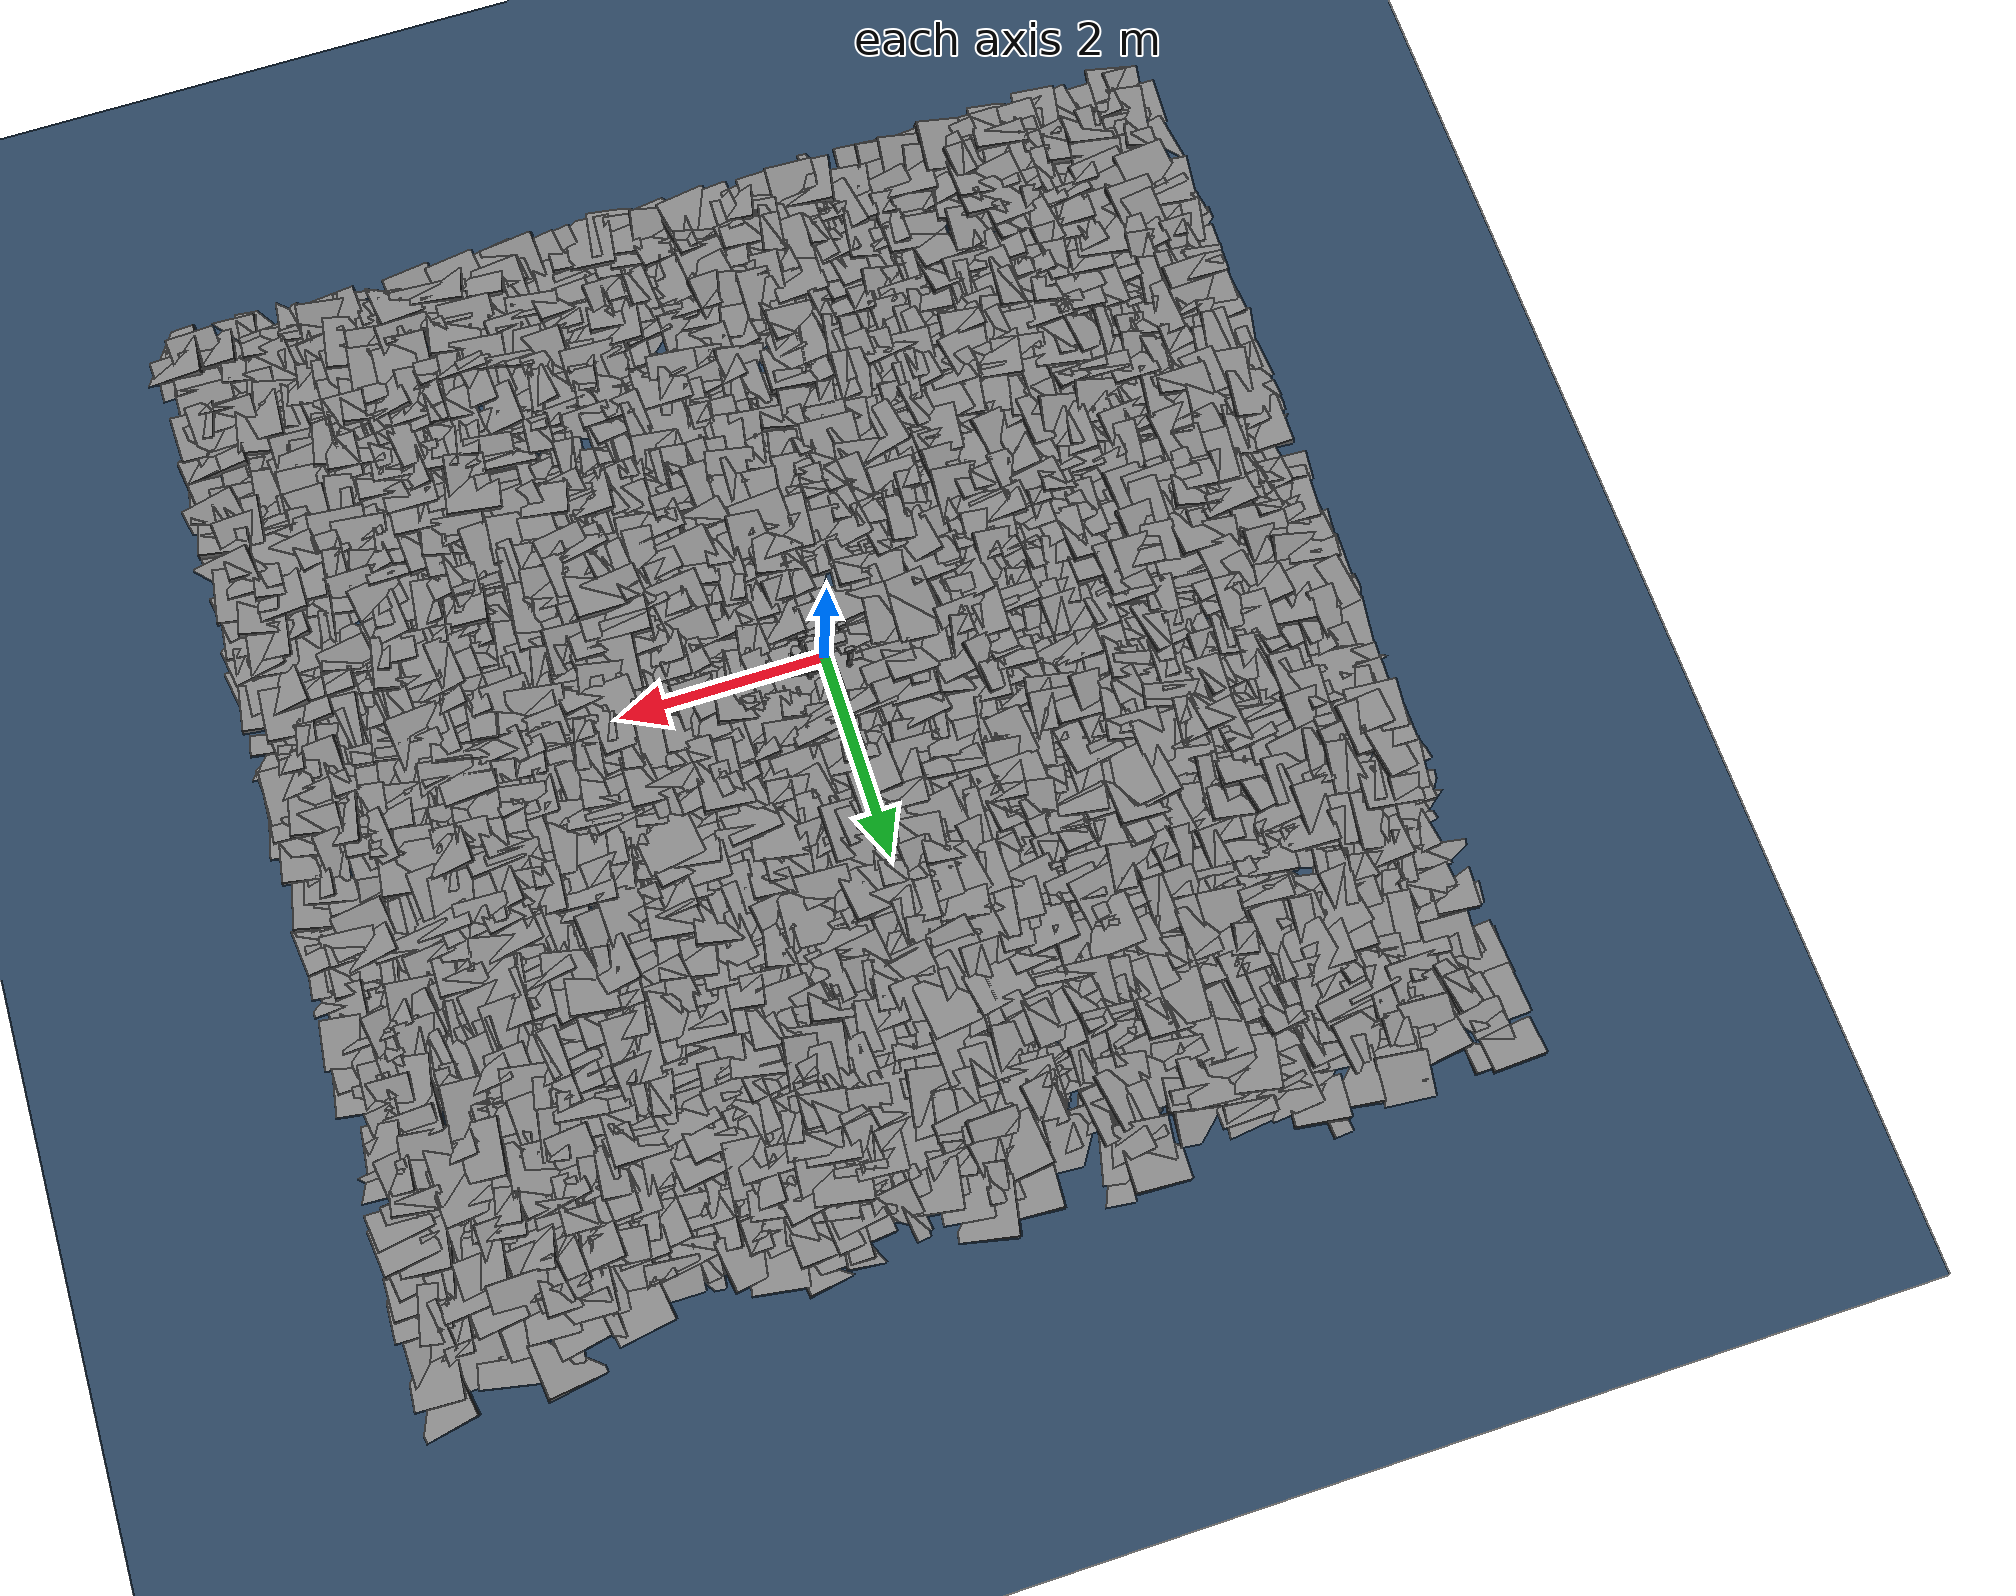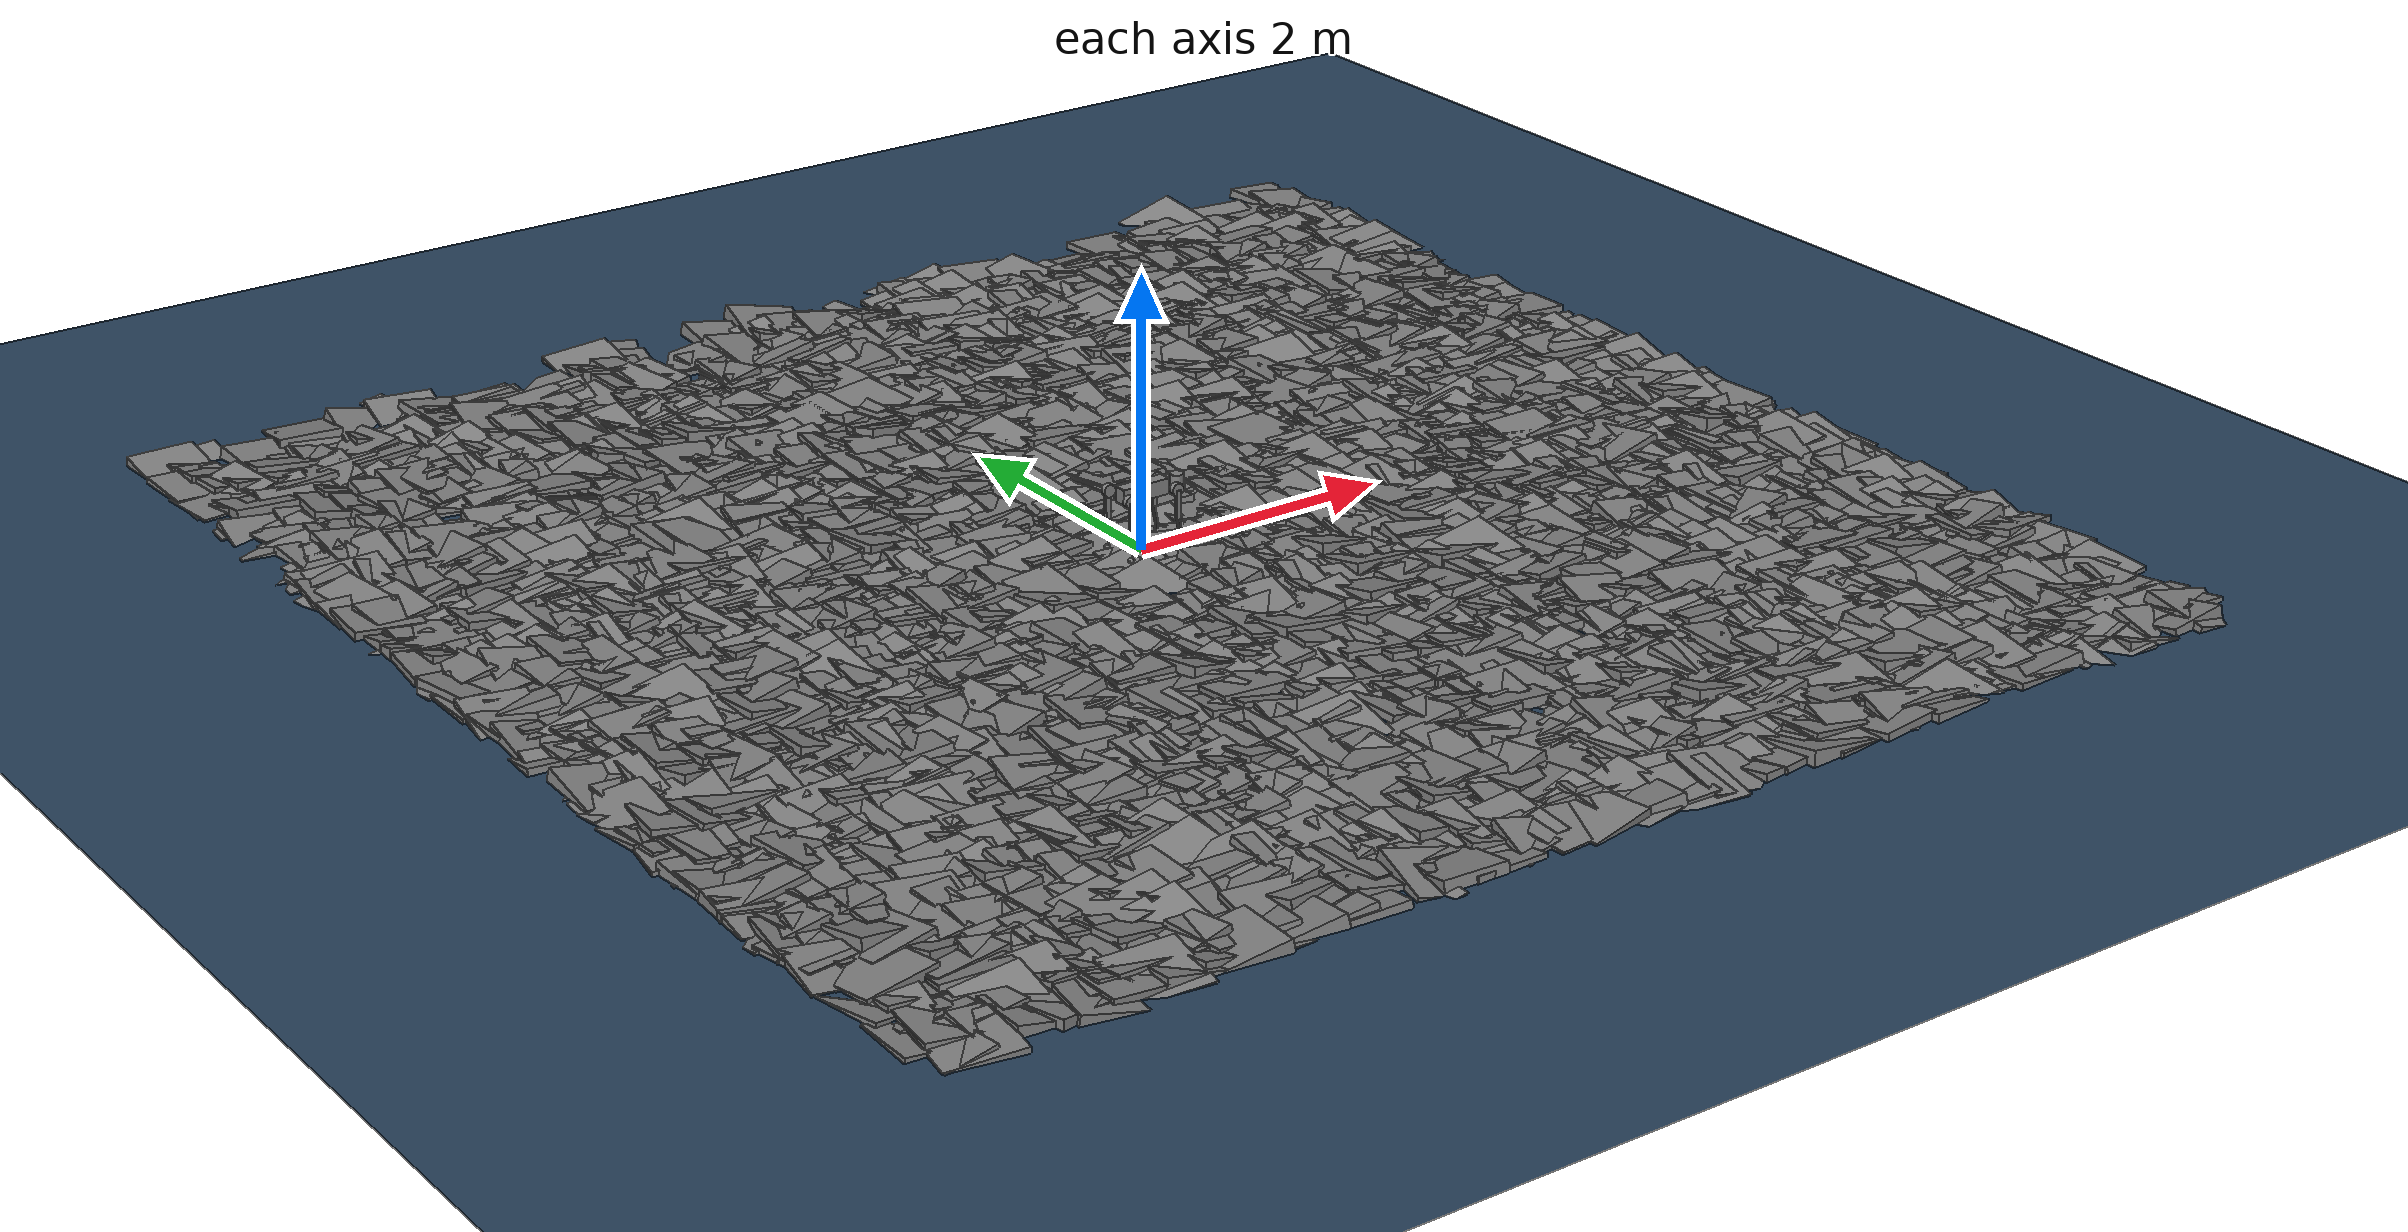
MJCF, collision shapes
<mujoco model="go2 scene">
  <include file="go2.xml" />

  <statistic center="0 0 0.1" extent="0.8" />

  <visual>
    <headlight diffuse="0.6 0.6 0.6" ambient="0.3 0.3 0.3" specular="0 0 0" />
    <rgba haze="0.15 0.25 0.35 1" />
    <global azimuth="-130" elevation="-20" />
  </visual>

  <asset>
    <texture type="skybox" builtin="gradient" rgb1="0.3 0.5 0.7" rgb2="0 0 0" width="512" height="3072" />
    <texture type="2d" name="groundplane" builtin="checker" mark="edge" rgb1="0.2 0.3 0.4" rgb2="0.1 0.2 0.3" markrgb="0.8 0.8 0.8" width="300" height="300" />
    <material name="groundplane" texture="groundplane" texuniform="true" texrepeat="5 5" reflectance="0.2" />
  </asset>

  <worldbody>
    <light pos="0 0 1.5" dir="0 0 -1" directional="true" />
    <geom name="floor" size="0 0 0.05" type="plane" material="groundplane" friction="1 0.005 0.0001" />
  <geom pos="-4.762925066211015 -4.805960013096589 -0.25" type="box" size="0.2643621732917061 0.2701650390040319 0.23499357700260978" quat="0.9947816696201447 -0.03977188865975952 -0.09065630097257449 0.024679176529269622" /><geom pos="-4.762925066211015 -4.615434812066643 -0.25" type="box" size="0.2552753260152732 0.242059985694448 0.23673464593325452" quat="0.9984806407908764 -0.02405721240727133 0.04463361645014893 -0.02157546707752418" /><geom pos="-4.762925066211015 -4.395320545024788 -0.25" type="box" size="0.2557956553915271 0.2615090650570002 0.23437198323015934" quat="0.9919059691745423 0.04087916401939168 -0.07870584740284811 -0.09086711093452415" /><geom pos="-4.762925066211015 -4.1620629099139785 -0.25" type="box" size="0.24456446239458213 0.25385614776499715 0.2295356891144668" quat="0.993842153804738 -0.04185215239032784 0.05567528827943958 0.08617675403528303" /><geom pos="-4.762925066211015 -3.945025750470667 -0.25" type="box" size="0.25130930431868487 0.24279368497264123 0.23120717594491383" quat="0.9995111194029531 -0.021788717273155057 -0.02241954601525725 0.00037141071041812827" /><geom pos="-4.762925066211015 -3.6968911557764605 -0.25" type="box" size="0.25478193963193957 0.25052320268326433 0.2576084999645151" quat="0.9954623316032115 0.04582563101799765 0.032962703115187175 -0.07660429559913767" /><geom pos="-4.762925066211015 -3.474045190218332 -0.25" type="box" size="0.23875315481241188 0.24426960397484626 0.2608302679090212" quat="0.9954291443614506 -0.010443295935171421 0.022336459339819474 0.0922650459816795" /><geom pos="-4.762925066211015 -3.2881681542257972 -0.25" type="box" size="0.23175907690216288 0.25986136356727013 0.25098533706629955" quat="0.990400137816883 -0.009834208782339985 0.09818777228837984 -0.09679884670268336" /><geom pos="-4.762925066211015 -3.1053889024624737 -0.25" type="box" size="0.2732229867359889 0.24513807768967094 0.253934361963644" quat="0.9948839607137109 -0.07139338165098487 -0.06321490307433204 0.03335814443788735" /><geom pos="-4.762925066211015 -2.8563508929672583 -0.25" type="box" size="0.26409800470842204 0.27395106710636047 0.26373201901905635" quat="0.9963116203222898 0.06710794588843999 0.04264205900211389 -0.03226970116793502" /><geom pos="-4.762925066211015 -2.7016637006506623 -0.25" type="box" size="0.23361497924971628 0.2626748628422877 0.24965285473459964" quat="0.9935342093116472 -0.05043783327847958 0.04705669586561812 -0.09017464874266433" /><geom pos="-4.762925066211015 -2.532919921703248 -0.25" type="box" size="0.261433835803901 0.2505326713383013 0.26328097441702797" quat="0.996118239459529 -0.014025689096715735 0.08689779788878159 0.0007111845689569545" /><geom pos="-4.762925066211015 -2.359993431731162 -0.25" type="box" size="0.26887339572589314 0.25943645958732053 0.2535445273949284" quat="0.995409739033825 0.05228925529667126 0.07269499527048262 0.033774589261106165" /><geom pos="-4.762925066211015 -2.1657931456913553 -0.25" type="box" size="0.22696475798053134 0.24631020426207934 0.23369794527434862" quat="0.9972572646146713 -0.05798908058577014 -0.0394624492899764 -0.02362053771861153" /><geom pos="-4.762925066211015 -1.9958971677481236 -0.25" type="box" size="0.24461466558699396 0.24494997967141613 0.26490629196234905" quat="0.9948829929771424 -0.02652770549373524 -0.01576616865309692 -0.09620571215932437" /><geom pos="-4.762925066211015 -1.7823006439335773 -0.25" type="box" size="0.23371989986453434 0.22765536683382917 0.23685345829589458" quat="0.9955227589092103 -0.025487684881835473 0.09098583910418219 0.002528140752908712" /><geom pos="-4.762925066211015 -1.5689197275241282 -0.25" type="box" size="0.2679622744828477 0.2634210933178289 0.23744338115247585" quat="0.9965187398262574 -0.052285016163791116 0.022073994630459923 0.06106895300309662" /><geom pos="-4.762925066211015 -1.3218894120112763 -0.25" type="box" size="0.24555117597622453 0.240858897747516 0.26730426454911405" quat="0.9953163948029499 0.010497003293848246 -0.07065406796364011 -0.0651390039722499" /><geom pos="-4.762925066211015 -1.148138243416867 -0.25" type="box" size="0.2672470475594213 0.22794371742436892 0.24250070111424907" quat="0.997542513984623 -0.032137566930088075 -0.021560345071735102 0.058406002306612546" /><geom pos="-4.762925066211015 -0.9580081723155871 -0.25" type="box" size="0.24772162778310866 0.2630148769603415 0.25486004951154195" quat="0.9935385780532818 0.06824423813537171 0.0877901527288368 -0.022731189256900795" /><geom pos="-4.762925066211015 -0.781601919162231 -0.25" type="box" size="0.26037703437974746 0.25384673860699103 0.23512460538789806" quat="0.9990878051411898 -0.028863901732020487 -0.029010806694463813 -0.012198601965015867" /><geom pos="-4.762925066211015 -0.5612029602308484 -0.25" type="box" size="0.23776921148518196 0.23384657939358003 0.2383228232133543" quat="0.9923213208180801 0.09620878139138873 0.009817214001728258 -0.07710959046895027" /><geom pos="-4.762925066211015 -0.3924078731523002 -0.25" type="box" size="0.2636161302469233 0.2615770885456838 0.23489920456339985" quat="0.9954692712961349 -0.08865641798227554 0.019306042084584703 -0.028429671027332053" /><geom pos="-4.762925066211015 -0.14505185195159065 -0.25" type="box" size="0.24323964839469772 0.2276326527732023 0.25116068058727536" quat="0.9926854941250703 0.05338487122488006 0.09736583635744371 -0.04738627637178947" /><geom pos="-4.762925066211015 0.07359032986715963 -0.25" type="box" size="0.2254134622740644 0.2520540176768668 0.2618442808437733" quat="0.9982568189981078 0.010990254351386303 0.0448783786549879 0.03672150272484009" /><geom pos="-4.762925066211015 0.264102205203149 -0.25" type="box" size="0.2414890177308626 0.25748456829729577 0.2634512002802915" quat="0.9945170121079235 0.07457975592505704 0.016581741419258687 -0.07140601155079336" /><geom pos="-4.762925066211015 0.5058887345788756 -0.25" type="box" size="0.24796721106450442 0.23301135062683662 0.26064480880840946" quat="0.9998118916196815 -0.01741866663148426 -0.0004791174260932354 -0.008517151821321699" /><geom pos="-4.762925066211015 0.7526120755562422 -0.25" type="box" size="0.2425671913015382 0.24803014780969804 0.2714871109367209" quat="0.9943763778283801 -0.024002275604524625 0.07159133214603455 0.0742575999091771" /><geom pos="-4.762925066211015 0.9866321429088272 -0.25" type="box" size="0.2636187350375713 0.2684117414699157 0.2619015024831677" quat="0.9958226829640828 -0.03904262375612436 -0.0672760497475954 0.047820401031491" /><geom pos="-4.762925066211015 1.1527393924465246 -0.25" type="box" size="0.24901327899233688 0.23671703853907933 0.25917484619884945" quat="0.9962258116442909 0.0022752158740063444 0.057619124757241506 -0.06487674520665938" /><geom pos="-4.762925066211015 1.4002794729358348 -0.25" type="box" size="0.26589518739347284 0.23350568948364173 0.23115996045202966" quat="0.9942946646714887 0.04869089343485277 -0.02980847957908856 0.09010422435996442" /><geom pos="-4.762925066211015 1.5998396802798656 -0.25" type="box" size="0.23292284638930166 0.23833334730060327 0.23596452860114267" quat="0.9919453573332323 -0.090227899555962 0.08866580789849515 -0.006458228586260748" /><geom pos="-4.762925066211015 1.7579343039121174 -0.25" type="box" size="0.2295049860976568 0.24442747260262565 0.23314146474485484" quat="0.9928572117621652 -0.09402918557748036 0.07317592344832244 0.0061930234118732904" /><geom pos="-4.762925066211015 2.0009448181405425 -0.25" type="box" size="0.25368059985906627 0.23174415177250307 0.2749606324010752" quat="0.9981910991254501 -0.0081796988073529 0.0383881022703743 -0.04554092399398599" /><geom pos="-4.762925066211015 2.1889524531079365 -0.25" type="box" size="0.25140861195827846 0.24533950270877092 0.24722097774693386" quat="0.9980491246301437 0.059504775819752505 0.012160441727485016 -0.014465480864361991" /><geom pos="-4.762925066211015 2.387577059753464 -0.25" type="box" size="0.22843667476872753 0.27343725975759 0.26884500210521967" quat="0.9935816325051866 0.022038494562153184 -0.0766194198441242 0.08024530396547871" /><geom pos="-4.762925066211015 2.5853365216866697 -0.25" type="box" size="0.25516693728725326 0.24316072211350903 0.23876839231605335" quat="0.9948813572486295 0.0018036463571113235 0.06895628838742743 -0.07384349768783528" /><geom pos="-4.762925066211015 2.7640690740621245 -0.25" type="box" size="0.22873234163836967 0.23990645609073935 0.23026536592712832" quat="0.9962670811930844 0.053576044389268246 0.06748071952857804 0.00527853109459784" /><geom pos="-4.762925066211015 2.9314724722503307 -0.25" type="box" size="0.22538605525599117 0.2618621963026537 0.2550822452990421" quat="0.9959433214569263 -0.038683651420586405 -0.06398110176842181 -0.05006889428192579" /><geom pos="-4.762925066211015 3.108394890852095 -0.25" type="box" size="0.2481050093420405 0.261249198118216 0.23571386901394875" quat="0.9938747501268956 -0.042293796865527 -0.038765639012627306 -0.09445338024041705" /><geom pos="-4.762925066211015 3.3315400618013413 -0.25" type="box" size="0.2575659538179792 0.2567488818842098 0.2436912462114381" quat="0.9953269393750105 0.017281186566400385 -0.07955925728169023 -0.05192272071085631" /><geom pos="-4.762925066211015 3.58147599197226 -0.25" type="box" size="0.26253092395888733 0.24008021389248185 0.23670057693124996" quat="0.9951590582645725 -0.054579033221522896 -0.03170720550585789 -0.07532749169846435" /><geom pos="-4.762925066211015 3.7909585677085413 -0.25" type="box" size="0.24531347501358866 0.26251372960561375 0.23882571265014127" quat="0.9946748025771763 0.07928933373812133 0.03169426523602317 -0.05771232298711213" /><geom pos="-4.762925066211015 4.0179407981975785 -0.25" type="box" size="0.2481105332799565 0.24634425328170445 0.23588229561484644" quat="0.9979168751632752 -0.026659056920826863 -0.0044136690370429645 -0.0585809224414204" /><geom pos="-4.762925066211015 4.2023937702472605 -0.25" type="box" size="0.26539643837618077 0.25305801255804 0.22624206699416521" quat="0.9994880800600103 0.02018877054059036 0.013623739640313406 -0.020745724384242676" /><geom pos="-4.762925066211015 4.449772831619656 -0.25" type="box" size="0.25074426685792206 0.25744517032938746 0.247664056213003" quat="0.9989650872464567 -0.012817239679599156 -0.007516219467985236 0.04298812946133016" /><geom pos="-4.762925066211015 4.654498039743505 -0.25" type="box" size="0.271906514789473 0.24754617466059914 0.23349450561130877" quat="0.9985240898538472 -0.021372216032718574 -0.032883108262944674 -0.037570887058526126" /><geom pos="-4.762925066211015 4.8512313274139345 -0.25" type="box" size="0.27449756853055013 0.2371194183859808 0.2556010084908295" quat="0.9991174056802159 0.02751420268503682 0.023500098652506213 0.021333627932536302" /><geom pos="-4.762925066211015 5.06418626199566 -0.25" type="box" size="0.2615556968999619 0.2681587138158399 0.22649635447307778" quat="0.9976683723138434 -0.053572419558146886 -0.003386141651704294 0.042146753042753685" /><geom pos="-4.762925066211015 5.25486391879193 -0.25" type="box" size="0.25554647889786025 0.2537045149781123 0.25644819102836486" quat="0.9947759710445195 0.09962943363686695 0.009621366396973328 0.020054243797395142" /><geom pos="-4.586375680870231 -4.844616281093233 -0.25" type="box" size="0.2622161388549687 0.2478650995639266 0.271160912225061" quat="0.9957083296148161 0.014523431485905017 -0.03390631989931453 -0.08487846455039111" /><geom pos="-4.586375680870231 -4.59625575056023 -0.25" type="box" size="0.24432216018701686 0.26617137067562335 0.265543623644362" quat="0.9955545599399711 -0.031953230350603885 0.02563036052594025 -0.08481269876735405" /><geom pos="-4.586375680870231 -4.379750500298863 -0.25" type="box" size="0.25054047112767996 0.23039639630775835 0.23339448185946868" quat="0.9952118608335199 -0.09109485179869145 -0.03138846269169185 -0.01642694256121491" /><geom pos="-4.586375680870231 -4.137895183361398 -0.25" type="box" size="0.22682476381027966 0.23607635302278746 0.24304229185128898" quat="0.9968787278214482 -0.06891768717698288 0.03735066132648924 -0.009385228273236136" /><geom pos="-4.586375680870231 -3.919495989221966 -0.25" type="box" size="0.2664633711308615 0.2525406350610112 0.2714310884689663" quat="0.9963146097671133 -0.040139902118532564 -0.04042177968053797 0.06412539551517517" /><geom pos="-4.586375680870231 -3.729065239475858 -0.25" type="box" size="0.2738794530071855 0.27069089001343294 0.24073767137306432" quat="0.9958340639134603 0.02105706440508952 0.008931355238344697 -0.08826861323170644" /><geom pos="-4.586375680870231 -3.50986664068699 -0.25" type="box" size="0.2264526765871827 0.22919733319534685 0.23268912351944138" quat="0.993055062199263 -0.030268051634574772 0.05955908119839973 0.0968411293690179" /><geom pos="-4.586375680870231 -3.3442214700155786 -0.25" type="box" size="0.2295973380242833 0.25058783719122035 0.23850422080540626" quat="0.991412801549267 0.07396777389885574 0.08208766962312636 -0.06993596960452958" /><geom pos="-4.586375680870231 -3.1516783464455234 -0.25" type="box" size="0.26787704008351365 0.24255241767666993 0.24269336910158523" quat="0.9979077806007868 0.05027116721994837 -0.020160777147981417 -0.03530459215945312" /><geom pos="-4.586375680870231 -2.974013973326074 -0.25" type="box" size="0.27220978719585304 0.23008657528989987 0.22624756879891564" quat="0.9932710886814191 -0.026178924008909667 0.08079983375795446 0.07873115769535617" /><geom pos="-4.586375680870231 -2.7704209684229664 -0.25" type="box" size="0.2704936216104557 0.24070061935248965 0.25403041928380016" quat="0.997895105946623 -0.03126305200704351 -0.05613246096728272 -0.008782137139649242" /><geom pos="-4.586375680870231 -2.611653018150772 -0.25" type="box" size="0.23530982590827607 0.260920329873134 0.27313955803505063" quat="0.9954317291194212 -0.06450146854889355 -0.05750723563569457 0.040597426850674" /><geom pos="-4.586375680870231 -2.390401176465274 -0.25" type="box" size="0.23487260436576568 0.2513387854607357 0.2518757159902576" quat="0.9950377845808411 -0.09160451383097845 -0.02578007383035575 0.029048375092988313" /><geom pos="-4.586375680870231 -2.2396566263603512 -0.25" type="box" size="0.25792923819385966 0.2553959927344538 0.2269738202976626" quat="0.9989878270474601 -0.01756458340869238 -0.007928720221051849 -0.040644092022450395" /><geom pos="-4.586375680870231 -2.0336222462211584 -0.25" type="box" size="0.2547299460769123 0.24426184843852794 0.2422507240555018" quat="0.995241625718726 -0.03771852525028148 0.08815424012110198 -0.01732770147371876" /><geom pos="-4.586375680870231 -1.8513757498384322 -0.25" type="box" size="0.22743634358920764 0.2649016701792005 0.2492611087977005" quat="0.9944459927812009 0.002975927984777977 -0.06292919600914296 -0.08431030532315541" /><geom pos="-4.586375680870231 -1.616036406386962 -0.25" type="box" size="0.2546283134859171 0.22873019127269012 0.26987955416269493" quat="0.994476576144819 -0.031698373462316326 0.05694188267560831 -0.08227499387103594" /><geom pos="-4.586375680870231 -1.3866417961911157 -0.25" type="box" size="0.26289380135420604 0.25462596308891666 0.2464068958161374" quat="0.9970970870303287 -0.007081820286970119 0.0010999846788168944 -0.07580261796773573" /><geom pos="-4.586375680870231 -1.203151861480154 -0.25" type="box" size="0.25065991975556523 0.25936848011961733 0.22641948799714576" quat="0.9944543829338447 0.06848134231322585 0.06083502787612365 0.05167093382121487" /><geom pos="-4.586375680870231 -0.9762367631172664 -0.25" type="box" size="0.2523487170698729 0.2691683491297947 0.2442349844416677" quat="0.9923023694564187 0.033384237460382896 -0.10083398631326033 -0.06367108813694736" /><geom pos="-4.586375680870231 -0.79983281020509 -0.25" type="box" size="0.24750780463017405 0.24810315652939172 0.24275751751661048" quat="0.9955172554738878 0.03111176845685395 -0.05790158716293263 0.06800630942227569" /><geom pos="-4.586375680870231 -0.5577076173553266 -0.25" type="box" size="0.25209506305595303 0.24769312066976854 0.23670874730506827" quat="0.9938519598630335 0.02337747025639015 0.09770064285953939 0.04654417413222797" /><geom pos="-4.586375680870231 -0.3213847152267464 -0.25" type="box" size="0.26617707661384027 0.26579054894700427 0.22743040670652317" quat="0.9912074948393131 0.09328965912994253 -0.08932511033413998 0.02873615036127754" /><geom pos="-4.586375680870231 -0.09758516903095416 -0.25" type="box" size="0.255322657031987 0.27105035657877863 0.2514059698474783" quat="0.9962650718892888 -0.010012373878528602 -0.03303610091538449 -0.07914717265357761" /><geom pos="-4.586375680870231 0.1399541473204593 -0.25" type="box" size="0.26876225462142883 0.26525708402077536 0.23266003916073524" quat="0.9961703026824726 -0.04250995438144892 0.06797461009501887 0.03488673407512372" /><geom pos="-4.586375680870231 0.38710102650642586 -0.25" type="box" size="0.26360809208913244 0.27056643523763324 0.2523796854682727" quat="0.9883450802202791 -0.10246376765193171 -0.06589825053778843 -0.09128307235736524" /><geom pos="-4.586375680870231 0.5775652069329658 -0.25" type="box" size="0.2349948199049364 0.24448990890476785 0.23330729528883654" quat="0.9941464998627977 -0.07985443968430603 0.06274511529395732 -0.036865373726601536" /><geom pos="-4.586375680870231 0.7304058414728027 -0.25" type="box" size="0.25412928827579434 0.2660896633570218 0.2743113419066634" quat="0.9961127970011646 -0.010386686773532088 -0.003724860287925352 0.08739300775359843" /><geom pos="-4.586375680870231 0.9696041991937072 -0.25" type="box" size="0.2671243940646018 0.2540795745381148 0.25419170019654314" quat="0.9965248033044259 0.002338772747198569 -0.06476996144302051 0.052323022043666" /><geom pos="-4.586375680870231 1.1405253358670304 -0.25" type="box" size="0.26016334574975636 0.2357711338196282 0.24710900700423374" quat="0.9971581695140052 0.005622687123991071 -0.0496188353413759 -0.05640870092768921" /><geom pos="-4.586375680870231 1.3739238394559345 -0.25" type="box" size="0.24874884422049315 0.26533073653735806 0.2261252257894906" quat="0.9916349030219294 -0.09511343602694242 0.08371093801321237 0.024619753304728015" /><geom pos="-4.586375680870231 1.5849848585594062 -0.25" type="box" size="0.26668304728514103 0.2321246402853934 0.26241080131194616" quat="0.9987588074584978 -0.014225857141002786 0.009673956893690095 -0.04674274350850574" /><geom pos="-4.586375680870231 1.7844361637100228 -0.25" type="box" size="0.24897425595933256 0.2602984490388124 0.2526551900380374" quat="0.996619752611409 0.0027434906845005464 0.05805246304818597 -0.05806421873819388" /><geom pos="-4.586375680870231 1.9555292147995962 -0.25" type="box" size="0.26868734509869396 0.2692097192698558 0.27034354803393834" quat="0.9975261968488877 0.045819487324111986 0.04058355230370015 0.03456929944275342" /><geom pos="-4.586375680870231 2.1301165001665954 -0.25" type="box" size="0.22831291863406733 0.25213529114947353 0.2726510598686059" quat="0.9973187143756111 0.010804096280989193 -0.06696950947699915 0.027454294020054414" /><geom pos="-4.586375680870231 2.312435610072132 -0.25" type="box" size="0.2610183269306786 0.24893924171963994 0.22634087883843226" quat="0.9950460008832452 0.01608689108079204 0.00040730565790030406 -0.09810454711029712" /><geom pos="-4.586375680870231 2.535092641970138 -0.25" type="box" size="0.2730994176850473 0.25292807297870207 0.22921070801379365" quat="0.9945502849787693 0.03405011609802031 0.009862532739382372 0.09804616611742023" /><geom pos="-4.586375680870231 2.7291727762049183 -0.25" type="box" size="0.274204820962723 0.22662692221924324 0.26519019321986703" quat="0.9962304664575101 0.0529033781174299 -0.03764342102210583 -0.057524456880255925" /><geom pos="-4.586375680870231 2.9761455554616862 -0.25" type="box" size="0.26656069602344545 0.2575024384551478 0.23964455816533656" quat="0.9944079491978247 0.04427307141773864 -0.030259524030171146 0.09097849704673945" /><geom pos="-4.586375680870231 3.2085968532613727 -0.25" type="box" size="0.26366492036533234 0.2501135217202404 0.2303018544738378" quat="0.9927730929191358 0.06871479983986059 0.07778630913907054 0.06024244657433868" /><geom pos="-4.586375680870231 3.397042645489302 -0.25" type="box" size="0.2292037248993866 0.2437334959885824 0.24836155081090844" quat="0.9924042812803916 -0.036358068243486634 -0.08100775389798737 -0.0851444488992347" /><geom pos="-4.586375680870231 3.6132402633430214 -0.25" type="box" size="0.23304078457504748 0.26027902857479657 0.2510463114266115" quat="0.9968421894129554 0.01797767586869095 -0.057087440981983206 0.052186939543092246" /><geom pos="-4.586375680870231 3.8294238327780334 -0.25" type="box" size="0.24955481772395977 0.26118788141240434 0.25303639271566597" quat="0.997680147598909 -0.03507246438567272 -0.02467743093736089 0.05287031048959781" /><geom pos="-4.586375680870231 4.025037980696281 -0.25" type="box" size="0.27104130832330015 0.26563780053450176 0.24095277725974223" quat="0.9986609924029733 -0.024339262368583855 -0.018680092801674684 -0.04165185101508066" /><geom pos="-4.586375680870231 4.246894405186216 -0.25" type="box" size="0.23273152042369855 0.26778089035132646 0.2746586116284788" quat="0.9956476011790214 -0.08908431053386016 0.023373319253527515 -0.01426631803373645" /><geom pos="-4.586375680870231 4.401876577195239 -0.25" type="box" size="0.26876510761581557 0.22709551442466838 0.25071416460988183" quat="0.9909929268031017 -0.09077387675430092 0.005565543397171477 0.09829622094420333" /><geom pos="-4.586375680870231 4.635409093897049 -0.25" type="box" size="0.2551958341165652 0.24186180869527965 0.2626603373698193" quat="0.991404727452238 0.03394820890416052 -0.09529840163121334 0.08296023230493635" /><geom pos="-4.586375680870231 4.878507515878345 -0.25" type="box" size="0.2250941936423416 0.2625158483860952 0.2547450626572464" quat="0.9939453295723281 -0.003391993266086668 0.08212414125925831 0.07291640162177777" /><geom pos="-4.586375680870231 5.053072690106109 -0.25" type="box" size="0.24727724184861333 0.23512849208941328 0.25027967445952226" quat="0.9961535231556363 -0.0533217573139808 0.06735091247006922 0.0172859217576369" /><geom pos="-4.586375680870231 5.208464797322282 -0.25" type="box" size="0.25447862258064613 0.2577922656128418 0.22878606628400652" quat="0.9964252790669131 0.07700021220064983 -0.032107391323124984 0.013294584608131193" /><geom pos="-4.348970534617806 -4.789752333544846 -0.25" type="box" size="0.2728109195464887 0.2381402071254043 0.2534204442000869" quat="0.9962646445466821 0.05595260648038916 0.06375033460056383 0.016185138017334504" /><geom pos="-4.348970534617806 -4.542715823197966 -0.25" type="box" size="0.2283221805392372 0.22696408983060976 0.2720827705572196" quat="0.997662920471636 -0.04530066223810336 -0.03013181066173113 0.04133547027724575" /><geom pos="-4.348970534617806 -4.321695602226816 -0.25" type="box" size="0.23602744333422743 0.23200252439475452 0.23432854767021197" quat="0.9958886884902031 -0.05330667547243217 0.04187652595258668 -0.06008722877186593" /><geom pos="-4.348970534617806 -4.110843774668031 -0.25" type="box" size="0.24609709419149262 0.2656909700871401 0.22844174758418626" quat="0.9979215693301494 -0.0603317142364545 -0.01190894062139386 0.019256242006655797" /><geom pos="-4.348970534617806 -3.9585062890038802 -0.25" type="box" size="0.23246268330755715 0.2699913699720417 0.22843700489365318" quat="0.9932482361808934 0.07371927796204399 -0.07707637469599464 -0.04563597094421949" /><geom pos="-4.348970534617806 -3.758728507108531 -0.25" type="box" size="0.24804204667172233 0.24172900737925496 0.24119222203896165" quat="0.9977359131120231 -0.014438232858432118 -0.026707587498822245 0.06001074810761879" /><geom pos="-4.348970534617806 -3.598571663447252 -0.25" type="box" size="0.23572434505728146 0.258236557130221 0.2729532577711416" quat="0.9944513428078788 -0.06014461827004304 -0.06391113216861147 0.058004472807565946" /><geom pos="-4.348970534617806 -3.4360290615884796 -0.25" type="box" size="0.2669462927823577 0.27471783426602864 0.2673800660501391" quat="0.9930131895392489 -0.09058717656693305 0.060902353948770825 0.044829366783589" /><geom pos="-4.348970534617806 -3.28582089055461 -0.25" type="box" size="0.23590855072262967 0.2556896048133941 0.24831123960422824" quat="0.9924347927533643 0.059562350421217505 0.10070583570211095 0.037200043016462576" /><geom pos="-4.348970534617806 -3.0614359942641283 -0.25" type="box" size="0.26545118051055017 0.2438748825270154 0.2548272308645255" quat="0.9933129014784895 -0.07811456726982854 -0.07905851879932431 -0.031262513364872145" /><geom pos="-4.348970534617806 -2.8835217949515135 -0.25" type="box" size="0.23506359837919089 0.2737502689824313 0.2413160654730225" quat="0.9911061912133321 -0.01921855052851569 0.09760077787536597 0.08839260835787359" /><geom pos="-4.348970534617806 -2.7302819590444414 -0.25" type="box" size="0.2643973126541997 0.2483277506892669 0.26381138035103197" quat="0.9932534803066616 -0.018867947253710795 -0.07993494468475734 -0.08186531037857363" /><geom pos="-4.348970534617806 -2.5205277204704197 -0.25" type="box" size="0.23001623556870596 0.264884870607839 0.2321001222286074" quat="0.9922511596476583 0.08096481238726431 0.008176684899284484 0.09389077248074096" /><geom pos="-4.348970534617806 -2.2970513385102036 -0.25" type="box" size="0.2305150535675359 0.2733675563303354 0.2464546242690559" quat="0.994514099593761 -0.06942940630631007 -0.02760009288845974 -0.07320859322314863" /><geom pos="-4.348970534617806 -2.0564309289628135 -0.25" type="box" size="0.24360670636484846 0.2397664915197589 0.23080575989695368" quat="0.994907126006375 -0.0738815650110959 -0.05953321993560898 0.03401647685085251" /><geom pos="-4.348970534617806 -1.831572552645957 -0.25" type="box" size="0.23232423506453292 0.25856367484325715 0.247093642191419" quat="0.9997660560110959 -0.005827691400405415 0.012005934476294267 0.017021421747630446" /><geom pos="-4.348970534617806 -1.6746092943448176 -0.25" type="box" size="0.2516081457098654 0.2255262958888519 0.25351407583098323" quat="0.9949872630839307 -0.03238556841056045 0.09291719512420568 0.017830202178436616" /><geom pos="-4.348970534617806 -1.4504442228461358 -0.25" type="box" size="0.23927153309916718 0.27416345487097615 0.25825209386956205" quat="0.9934442988834803 0.044672528813904 -0.07308251247584814 -0.07570823307605729" /><geom pos="-4.348970534617806 -1.2214105044664088 -0.25" type="box" size="0.23195201383021283 0.2416558085271194 0.2277900187589327" quat="0.9934311476196855 0.02042042579916041 0.05359350958907798 -0.09902169903178182" /><geom pos="-4.348970534617806 -1.0711241801582485 -0.25" type="box" size="0.26865226600867365 0.25957247567700353 0.23248694509975967" quat="0.9927670535229497 0.02339837474371509 0.06727583704162676 -0.09664396126536859" /><geom pos="-4.348970534617806 -0.8673159238656929 -0.25" type="box" size="0.2529865413619852 0.27166748041666394 0.2250920189389259" quat="0.994426896536095 -0.0039648941375368596 -0.07757920378919762 0.07128039140958053" /><geom pos="-4.348970534617806 -0.6578316758546112 -0.25" type="box" size="0.25940017040426144 0.24735729946032076 0.23369849360482028" quat="0.991996723016391 -0.0893196454949686 -0.08893275128233111 0.007447697815409111" /><geom pos="-4.348970534617806 -0.48724756500057786 -0.25" type="box" size="0.24804863142962552 0.22566582391964485 0.23581756960634662" quat="0.9942564324233647 0.002058583173154785 0.07909524640002984 0.07206837598420762" /><geom pos="-4.348970534617806 -0.30954552563839943 -0.25" type="box" size="0.2698245434928934 0.2284878497146649 0.2525523525346245" quat="0.9959554162405909 -0.006861679704427868 0.027321644815938257 0.08531854392344429" /><geom pos="-4.348970534617806 -0.14604264937364242 -0.25" type="box" size="0.2256920052512034 0.2697198713743312 0.229396668217268" quat="0.9903256899843211 0.05622946612949124 -0.09360153196725762 -0.08562726265187524" /><geom pos="-4.348970534617806 0.020888516584526506 -0.25" type="box" size="0.25291034401601764 0.2711786115355478 0.2638525988949117" quat="0.9976726998530252 -0.057451680388806554 -0.025892994472137294 -0.026039224753125877" /><geom pos="-4.348970534617806 0.19212642768834165 -0.25" type="box" size="0.23810918589228205 0.23839854576047992 0.2435876601409544" quat="0.9906138665957875 -0.094022949300126 -0.09892818261211621 0.007554270190618016" /><geom pos="-4.348970534617806 0.43233574996612667 -0.25" type="box" size="0.23745947538038623 0.24224945141772894 0.22702025863849512" quat="0.9949153137477162 -0.006018933449787 -0.058912295568154006 -0.08146552854613243" /><geom pos="-4.348970534617806 0.6045478865946325 -0.25" type="box" size="0.25788708015330386 0.26108135399176247 0.2551850262966512" quat="0.9959319248818665 -0.06348211478311606 -0.021201596595541532 -0.06033336063541646" /><geom pos="-4.348970534617806 0.7873911645836866 -0.25" type="box" size="0.2553775739990007 0.26355691261200587 0.2626238382110673" quat="0.9891581510306563 0.09705962512116587 0.07518537819213109 -0.08057754232451018" /><geom pos="-4.348970534617806 0.9735374511947699 -0.25" type="box" size="0.2288358875155746 0.25187272202115085 0.23449694913294533" quat="0.9925227624271908 0.0637034306958467 -0.05640531703594906 0.08751502266212054" /><geom pos="-4.348970534617806 1.1636448463755 -0.25" type="box" size="0.26629276049045847 0.2366825748720627 0.2433850121962835" quat="0.994685688660933 0.033475889885079206 0.056087008043824015 0.07958638764399073" /><geom pos="-4.348970534617806 1.404695874218091 -0.25" type="box" size="0.24200728886342995 0.25900352038021157 0.22901760806374094" quat="0.9982950366920416 0.005032826306882 -0.014520241553194837 -0.05631032730003328" /><geom pos="-4.348970534617806 1.6061127493791663 -0.25" type="box" size="0.2317161975488522 0.2706477743832254 0.23776353505995473" quat="0.9931221669085158 0.08383386787759885 -0.07641195869123892 0.029007874113481137" /><geom pos="-4.348970534617806 1.8053103619831052 -0.25" type="box" size="0.22684296011176866 0.23342310976195252 0.23929697636552422" quat="0.9977170258775745 0.04112568497529727 -0.03375606539809934 0.041592575757692034" /><geom pos="-4.348970534617806 1.9901262802612019 -0.25" type="box" size="0.24132127323456318 0.2504565638272267 0.24002627370867877" quat="0.9954071554509888 0.07898263676453991 -0.01692902474037169 -0.05137845937775603" /><geom pos="-4.348970534617806 2.2151155592307283 -0.25" type="box" size="0.25100914542325414 0.22738806526874078 0.2630824304684481" quat="0.9905609190450284 -0.08141830876414789 -0.09346923507290242 0.058511765941056657" /><geom pos="-4.348970534617806 2.4213963555054843 -0.25" type="box" size="0.2682576385703652 0.24369870616686487 0.2569078606696324" quat="0.994246229429012 -0.05664207987540035 -0.06941484599214429 -0.05871702657209596" /><geom pos="-4.348970534617806 2.6100506526124736 -0.25" type="box" size="0.2496976441299707 0.2501590310486806 0.2325883262578666" quat="0.9883387796545078 0.09188743285087063 0.0844190116638213 -0.0872730587570907" /><geom pos="-4.348970534617806 2.808923420583267 -0.25" type="box" size="0.24150329372812984 0.2649115940044403 0.228049879025821" quat="0.9935904712291648 0.0038281866296405107 0.08398622777345034 0.07556212023309883" /><geom pos="-4.348970534617806 3.002053898141437 -0.25" type="box" size="0.23486074788953268 0.2723521525321968 0.26013109032619997" quat="0.9940166432600501 0.012918461068442192 -0.08500436994440266 -0.06736678243764155" /><geom pos="-4.348970534617806 3.218923004195984 -0.25" type="box" size="0.2559300603048419 0.24121923508330098 0.25714540626605054" quat="0.9918877832748533 0.08945331176011026 0.08781911594315918 0.021083957887642637" /><geom pos="-4.348970534617806 3.3696416759118772 -0.25" type="box" size="0.24689490449114748 0.2575695136465429 0.250421691335699" quat="0.9924855354378109 0.016152279385844424 0.09053014233565544 -0.080720871811753" /><geom pos="-4.348970534617806 3.533869989254505 -0.25" type="box" size="0.22567723988065108 0.25315725313121024 0.23431310698867452" quat="0.9951976572600302 -0.07788964264595712 0.03530660733863323 0.0476263585724139" /><geom pos="-4.348970534617806 3.7676198790696027 -0.25" type="box" size="0.2684851062441659 0.2596073901643004 0.2339232457405727" quat="0.9953636004521569 0.047359774700125964 0.054883263415134845 -0.06321536231152351" /><geom pos="-4.348970534617806 3.946234016439666 -0.25" type="box" size="0.23047788654290813 0.25637380705915863 0.23341889996762585" quat="0.9978817722906669 0.004899299938533117 0.010656680208727695 0.06398750313208613" /><geom pos="-4.348970534617806 4.117678768716971 -0.25" type="box" size="0.24131492607577074 0.24496785782017585 0.26021247075767556" quat="0.9947429887254735 0.08167290089846159 0.024701565608601685 -0.05661939859117618" /><geom pos="-4.348970534617806 4.312560116335785 -0.25" type="box" size="0.25675992116800433 0.2525338472926182 0.23858831096394034" quat="0.9924598844207129 0.08357013010456381 -0.07773057241168982 -0.04469193755569803" /><geom pos="-4.348970534617806 4.503507551487939 -0.25" type="box" size="0.24096431016542436 0.2740765608829886 0.24903864578911414" quat="0.9938874609543367 -0.027135832725396145 0.040924289981842145 0.09887650898733856" /><geom pos="-4.348970534617806 4.717251169517867 -0.25" type="box" size="0.2728070702014324 0.23099669950582766 0.25712157692310844" quat="0.9954921270841621 -0.08218884523168159 0.0405548466592349 0.024407438320701934" /><geom pos="-4.154673035088282 -4.772602548321339 -0.25" type="box" size="0.24244678429161254 0.22929338494787105 0.26522673104704136" quat="0.9953517276747964 -0.0319086717009002 0.0858915529132885 -0.02965494938835249" /><geom pos="-4.154673035088282 -4.560606808120804 -0.25" type="box" size="0.23402192101452277 0.25616638442069345 0.2666329175340678" quat="0.9920156744910551 0.09261636251959668 -0.07827820087941487 -0.034635736238421" /><geom pos="-4.154673035088282 -4.312340927289366 -0.25" type="box" size="0.26003654126619297 0.26548778018858027 0.2358654204641992" quat="0.9955989395916806 0.01254473361211875 -0.08220918498926691 0.04320915465410939" /><geom pos="-4.154673035088282 -4.140653261279176 -0.25" type="box" size="0.2563602212357058 0.26659580925725523 0.26233429884398646" quat="0.9922818530290242 -0.10065404529980095 -0.01596292025446431 -0.07064469188142367" /><geom pos="-4.154673035088282 -3.9809450909091666 -0.25" type="box" size="0.27445852565029316 0.2386026034968781 0.26815831334059875" quat="0.9957634495537483 -0.05124786816379532 -0.014660947658348992 0.07492573092900204" /><geom pos="-4.154673035088282 -3.7780519190906565 -0.25" type="box" size="0.2417029901036791 0.2648926864794095 0.2525386733452538" quat="0.9889061441658425 -0.10356584777831787 0.0675942970914619 0.08227857683331423" /><geom pos="-4.154673035088282 -3.59893818750292 -0.25" type="box" size="0.2634865087520868 0.24954322735867687 0.2655531814642504" quat="0.9988373662566572 -0.010199142993773697 -0.02923622675008405 0.036947750906851" /><geom pos="-4.154673035088282 -3.4003647255620235 -0.25" type="box" size="0.2300150826836302 0.2646194558105792 0.2416832399556591" quat="0.9950691535092362 -0.023090033832126183 -0.05451625583340114 -0.07957517151694049" /><geom pos="-4.154673035088282 -3.2184558237024476 -0.25" type="box" size="0.24435721834042093 0.24290229203258187 0.2642379451302591" quat="0.998732953127134 -0.009778234951048976 0.04911422065897257 -0.0049666677217248" /><geom pos="-4.154673035088282 -2.9805183045954102 -0.25" type="box" size="0.2722017015020391 0.22956781210717012 0.2500835477804988" quat="0.9970255566052837 -0.07264176983344492 0.007190323468657908 0.02472876866738521" /><geom pos="-4.154673035088282 -2.798977311134109 -0.25" type="box" size="0.2555161616315992 0.25923918436836635 0.25747038859855487" quat="0.9990960898689091 0.021560172724964837 -0.011949069831932646 0.034632093365520006" /><geom pos="-4.154673035088282 -2.6304377121555405 -0.25" type="box" size="0.2362062453779913 0.24185871174839424 0.24665767139882305" quat="0.9960453814276502 -0.009187917958011388 -0.0384377126769162 -0.07957212165331805" /><geom pos="-4.154673035088282 -2.422101407814044 -0.25" type="box" size="0.2476247604370965 0.2636070409821684 0.27035071059917537" quat="0.9960597103699796 -0.01868322580679896 0.07719467115339443 0.039458499675528766" /><geom pos="-4.154673035088282 -2.2043765130612716 -0.25" type="box" size="0.2584252533300381 0.263893511248905 0.23298256704567433" quat="0.9952543373725921 0.035442658439664314 0.033001063634808335 0.08440113567211725" /><geom pos="-4.154673035088282 -1.9750063390472858 -0.25" type="box" size="0.253679147168991 0.25921190141528966 0.2338524448904727" quat="0.9928960743716033 0.009966163671716004 -0.0955056815394347 0.07026183795501006" /><geom pos="-4.154673035088282 -1.7685784079181674 -0.25" type="box" size="0.2654183478221228 0.2732643356737841 0.24682017766284794" quat="0.9934127316697893 0.06761740649326109 -0.07350400408736432 -0.05617999891969795" /><geom pos="-4.154673035088282 -1.5431523876387634 -0.25" type="box" size="0.2702242165913123 0.2636219149849526 0.26365755392796153" quat="0.9960043169891484 -0.08715639954035878 0.018325744011509493 0.00658252721725891" /><geom pos="-4.154673035088282 -1.3052418767955385 -0.25" type="box" size="0.25777328229704355 0.24441908460347878 0.2284813450439752" quat="0.9945045506756649 -0.07330649542251622 -0.016803666187012956 -0.07283195189570137" /><geom pos="-4.154673035088282 -1.066599341526981 -0.25" type="box" size="0.25834448800410054 0.26571419317657496 0.26297252339794785" quat="0.9913128985422783 -0.08763116714552403 0.06555413987278351 0.07295320742749667" /><geom pos="-4.154673035088282 -0.8203624491395756 -0.25" type="box" size="0.2617587025283496 0.26064784472350566 0.2719140930533866" quat="0.9948304887634987 -0.022659778200797134 0.09027408744022322 -0.0406130793624877" /><geom pos="-4.154673035088282 -0.6226301737093509 -0.25" type="box" size="0.2675361813415793 0.2358577571184452 0.2645608274342791" quat="0.9973195942901378 -0.0441830227408998 0.043401906908479136 -0.03895846279231003" /><geom pos="-4.154673035088282 -0.4347512756222125 -0.25" type="box" size="0.26598030193479655 0.24352910783596637 0.27040901922600885" quat="0.9944751262129697 0.08563202582228498 0.02989653083514791 0.052844838359980384" /><geom pos="-4.154673035088282 -0.24184469403662678 -0.25" type="box" size="0.24384415894645017 0.24259477218222483 0.2525301135350058" quat="0.9958820189337952 -0.06632708135014076 -0.06057787054333614 0.012249254848957558" /><geom pos="-4.154673035088282 -0.06585912355119472 -0.25" type="box" size="0.2702875970425682 0.23112933894143334 0.23201492359097545" quat="0.9938755920439188 -0.05673702184921378 0.033729570159867786 -0.08862580881358555" /><geom pos="-4.154673035088282 0.11308492938557624 -0.25" type="box" size="0.22824870361732744 0.26005470319671603 0.25621832571513" quat="0.9950844791828147 0.017026864216265418 0.01785355044183395 0.09590732986090349" /><geom pos="-4.154673035088282 0.3577330064248443 -0.25" type="box" size="0.2571394650258599 0.24490694080044548 0.2310997902340414" quat="0.9950179542392359 -0.03372811279760035 -0.056864928012493786 -0.07461946871167183" /><geom pos="-4.154673035088282 0.5413562557951233 -0.25" type="box" size="0.2723112465739019 0.24403231520342877 0.27090165085275514" quat="0.9950944576556306 0.06583693845964335 0.05757137427276812 0.04623910403167666" /><geom pos="-4.154673035088282 0.7213502094915771 -0.25" type="box" size="0.2655901419611329 0.2525476815827804 0.2254798861883886" quat="0.9954056528334865 -0.031729017395574814 0.05644374114876567 -0.07053339526339909" /><geom pos="-4.154673035088282 0.9569437334185391 -0.25" type="box" size="0.25881035160977006 0.25878028270042963 0.23068589045056592" quat="0.9884699763774623 0.07436920510046811 -0.08583609484582547 0.10014235844377789" /><geom pos="-4.154673035088282 1.1476484840385517 -0.25" type="box" size="0.24764852836933104 0.24289078300039904 0.2507407597820835" quat="0.9954128986129085 -0.011505555708061162 -0.04965737692338841 0.08096251218919066" /><geom pos="-4.154673035088282 1.337732544182872 -0.25" type="box" size="0.2686780688467663 0.2517769753390494 0.23337798407045862" quat="0.9961965207625819 0.05261694752850664 0.02331413893071765 0.06542476426574446" /><geom pos="-4.154673035088282 1.5010159054623209 -0.25" type="box" size="0.258537187642997 0.2609959936490439 0.2657764845859942" quat="0.9958993576574715 0.015180482549631568 -0.08902062064949029 -0.005417699343381415" /><geom pos="-4.154673035088282 1.6599572726328562 -0.25" type="box" size="0.23099960321605384 0.23330057919070138 0.2748847075351194" quat="0.9968456761454174 -0.041859483040464274 0.06200080218350386 -0.026502493436893492" /><geom pos="-4.154673035088282 1.8567889431498168 -0.25" type="box" size="0.24292480195193653 0.2657999402607756 0.2673389857510107" quat="0.9944473989038589 -0.08430468774138469 -0.05684777545928529 0.027118644204819336" /><geom pos="-4.154673035088282 2.0943522697022727 -0.25" type="box" size="0.2404623368345931 0.23871765620315644 0.22885724230145874" quat="0.9974369592583839 0.0423372771059099 -0.007874207425033763 -0.0571407396703414" /><geom pos="-4.154673035088282 2.2515904007339467 -0.25" type="box" size="0.2415423702507145 0.26647321453997874 0.2570695394272571" quat="0.9922922039005739 -0.0675082530221851 -0.08066615272673076 -0.06551175204726407" /><geom pos="-4.154673035088282 2.433476619409303 -0.25" type="box" size="0.2573799462687727 0.26432775720325674 0.2555137425466964" quat="0.9957443659172056 -0.024063393157205917 0.045899022635774694 0.07620623711340396" /><geom pos="-4.154673035088282 2.633201027348634 -0.25" type="box" size="0.2381675522719374 0.23826600182585375 0.2312180825949106" quat="0.9949794317977521 -0.08976088218181298 -0.008482323013382313 0.04343920493818688" /><geom pos="-4.154673035088282 2.796271419639406 -0.25" type="box" size="0.269640777852133 0.24477616326317805 0.23768010139402163" quat="0.9961246717612712 0.022733558965437325 -0.04901541319163229 0.06939966048128973" /><geom pos="-4.154673035088282 3.0345998799583445 -0.25" type="box" size="0.2617819461125344 0.2555173574754227 0.25783440827880527" quat="0.9947467163369921 -0.025854519970946663 -0.09904489836128541 0.0007888234570918012" /><geom pos="-4.154673035088282 3.2554661908257163 -0.25" type="box" size="0.27230971137787846 0.22973952168423772 0.24013868679261288" quat="0.9936460370094371 -0.009810915565996477 -0.06709914286160877 0.08982763549395291" /><geom pos="-4.154673035088282 3.496774856465688 -0.25" type="box" size="0.2640787630543856 0.2538590680161804 0.25612404050059717" quat="0.9926365280182529 -0.057954745305306456 -0.06262760003666204 -0.0859753130503939" /><geom pos="-4.154673035088282 3.681583177757492 -0.25" type="box" size="0.22825734696898944 0.245311079763237 0.23435810230172222" quat="0.9943423130958778 -0.02927889807114959 0.06097624728533674 -0.08190242842477902" /><geom pos="-4.154673035088282 3.890366319382437 -0.25" type="box" size="0.25439977835158345 0.23627580065354198 0.27495651889455225" quat="0.9933681526544289 -0.030337405825352503 0.08872515637047929 -0.06653722061184358" /><geom pos="-4.154673035088282 4.078599416054136 -0.25" type="box" size="0.25491374258387944 0.24487645883568213 0.23783484998273122" quat="0.9989624946184508 0.019869208964182147 0.024063520732846115 -0.033167692876642486" /><geom pos="-4.154673035088282 4.294172956612531 -0.25" type="box" size="0.2705259442529006 0.2706554291191773 0.23611776931087902" quat="0.9963522010507234 -0.004434520993548989 -0.0397445866965879 -0.07538563731410734" /><geom pos="-4.154673035088282 4.4766817671670065 -0.25" type="box" size="0.23963462771733438 0.23819753358848117 0.268777938768828" quat="0.9953947846240162 -0.092103927578543 -0.022764199109651922 0.013706951039933293" /><geom pos="-4.154673035088282 4.674287509512844 -0.25" type="box" size="0.24613152154364926 0.22825410022917816 0.2520443539423061" quat="0.9901079992286943 -0.0700816662611029 0.06373361861114377 0.1035023467180748" /><geom pos="-4.154673035088282 4.853638721971246 -0.25" type="box" size="0.23236949052841183 0.23612119837459677 0.2646414236532249" quat="0.9942285913270725 -0.08949464352714649 0.05383733972024878 -0.024530752527804914" /><geom pos="-4.154673035088282 5.024512965770368 -0.25" type="box" size="0.26831312768393156 0.23693671262226357 0.26306998592934544" quat="0.9913534609045739 0.086880646868334 0.06808647851734033 0.07095280258996826" /><geom pos="-3.9304585501842704 -4.77796237163722 -0.25" type="box" size="0.24929131669257243 0.25242538710328866 0.26558785886443187" quat="0.9939895429847855 -0.04656793440792701 0.04135734715432421 0.09003213736345927" /><geom pos="-3.9304585501842704 -4.5998613951555045 -0.25" type="box" size="0.2502969868488408 0.25653943758030406 0.2727252426109221" quat="0.9975987671128125 -0.009969142579273785 -0.004320789529039512 -0.06840063471252494" /><geom pos="-3.9304585501842704 -4.428115911100401 -0.25" type="box" size="0.25230160757774717 0.23174692899999322 0.270701853665805" quat="0.9950441242681557 0.06583830701971537 -0.052245796963287836 -0.05313082709565176" /><geom pos="-3.9304585501842704 -4.181161190770744 -0.25" type="box" size="0.22813747397419215 0.27243452971066195 0.24511662906452875" quat="0.9927999016940189 0.08990453854429686 0.07551422648099623 -0.023730375986491768" /><geom pos="-3.9304585501842704 -3.9557114156736572 -0.25" type="box" size="0.26304373745487303 0.2603713851803628 0.23579278017377517" quat="0.9963954273969139 -0.019272054966004853 -0.03403812515383623 -0.07527380816672197" /><geom pos="-3.9304585501842704 -3.782947776908464 -0.25" type="box" size="0.26439096221564656 0.24957114067331973 0.24080444653598063" quat="0.9958021438441709 -0.0891195732338427 -0.01174947450916418 0.017255197209234192" /><geom pos="-3.9304585501842704 -3.575885624399403 -0.25" type="box" size="0.23162772943523519 0.22573152595788581 0.23622551527691954" quat="0.9950598728788251 0.04222317672645708 -0.06414563329870833 0.06291574097322777" /><geom pos="-3.9304585501842704 -3.3710272735130866 -0.25" type="box" size="0.2499170066887999 0.2590476310883087 0.27198930287782724" quat="0.9945462415682382 0.05155319888004494 0.01940476922341497 -0.08856351392708026" /><geom pos="-3.9304585501842704 -3.1935308689265556 -0.25" type="box" size="0.27024503950297135 0.260426433647073 0.23934436090100428" quat="0.9954830895976503 0.061214406431260665 0.059624530076435284 -0.04136580935445518" /><geom pos="-3.9304585501842704 -3.016385232429018 -0.25" type="box" size="0.24916819987515534 0.2620850421546678 0.2516350161138734" quat="0.994907216016836 0.06753810018446918 0.06338690876317246 0.039753444360845054" /><geom pos="-3.9304585501842704 -2.8298681361150897 -0.25" type="box" size="0.27026912054631685 0.27414550151003864 0.23524050861693035" quat="0.9944280062405936 0.09745791927261248 -0.023256386876469012 0.03277247083854002" /><geom pos="-3.9304585501842704 -2.6510559198539387 -0.25" type="box" size="0.2745456674045536 0.22722781714947182 0.24478940922568987" quat="0.9964492659979024 -0.03326948345552635 0.042147926334108125 0.06485024339644754" /><geom pos="-3.9304585501842704 -2.470035580675652 -0.25" type="box" size="0.23257795132205192 0.2723373004351199 0.24112960594680968" quat="0.9920160696050945 0.07453416571020549 -0.028783318223303742 -0.0975720061247073" /><geom pos="-3.9304585501842704 -2.256674334496942 -0.25" type="box" size="0.24464635173518323 0.23440970635454367 0.24668390290199138" quat="0.9934711320396786 -0.05744286208230102 -0.09519536174788099 -0.025559156896955943" /><geom pos="-3.9304585501842704 -2.053316161664255 -0.25" type="box" size="0.2688618707505879 0.23830880921321726 0.2397351844248185" quat="0.9891849579230448 -0.07821449013344361 -0.0805181218186512 -0.09440574458551892" /><geom pos="-3.9304585501842704 -1.8149978522148178 -0.25" type="box" size="0.22588696936407593 0.23913112811167317 0.22652894682573427" quat="0.993209163314154 0.037187619320016754 0.08160270839123886 -0.07411907218335992" /><geom pos="-3.9304585501842704 -1.596249133488349 -0.25" type="box" size="0.22505150010870384 0.2711107603495185 0.2653510357007347" quat="0.9928302652213583 0.00892366053507622 -0.09195152904123632 -0.07585083420847065" /><geom pos="-3.9304585501842704 -1.3486071899882934 -0.25" type="box" size="0.23789590038066535 0.2405521996511118 0.25806860208600013" quat="0.98967173822292 0.06538247521595626 0.08120205152155587 -0.0983931365805047" /><geom pos="-3.9304585501842704 -1.1691045136988247 -0.25" type="box" size="0.23274746395925477 0.2604005666210677 0.27407786061182515" quat="0.9971442713122852 -0.029341444780444502 -0.04433876379071144 0.05363260046650103" /><geom pos="-3.9304585501842704 -0.9458348473388716 -0.25" type="box" size="0.23243967360806303 0.26339651068355524 0.259163474832367" quat="0.994438390294708 -0.06564363743391932 0.08050857146551604 -0.017365790885992098" /><geom pos="-3.9304585501842704 -0.7603976620073505 -0.25" type="box" size="0.23792319863361935 0.24293601956641273 0.26846529489176635" quat="0.9956379055261336 0.06228020981591889 0.03735282120258743 -0.0585756202957044" /><geom pos="-3.9304585501842704 -0.5836572959935786 -0.25" type="box" size="0.2729150944217589 0.2622735432505283 0.26365956871719237" quat="0.9903393802985366 0.0828506506583223 -0.05924882872841876 -0.09409175208121896" /><geom pos="-3.9304585501842704 -0.3689339283389099 -0.25" type="box" size="0.234848485296689 0.2710447201227686 0.22527434743765917" quat="0.9913910947074497 -0.07715742986144454 0.06215230397383931 0.08560093143584567" /><geom pos="-3.9304585501842704 -0.13910119404272248 -0.25" type="box" size="0.2487732515266265 0.24634362848931904 0.23083387197253094" quat="0.993918282421187 -0.08151845851402183 -0.07394444363934731 -0.0036616997805008523" /><geom pos="-3.9304585501842704 0.02599709501754255 -0.25" type="box" size="0.2294798198317673 0.274780512067064 0.23688692993953114" quat="0.9876878975597873 -0.08664874597111381 0.10445532118617207 -0.07780551208914843" /><geom pos="-3.9304585501842704 0.23440848813470705 -0.25" type="box" size="0.24436081734213683 0.24759936587867842 0.2744045613106958" quat="0.9973436487715682 -0.025051163512629204 -0.0376701984255513 0.05708801636296361" /><geom pos="-3.9304585501842704 0.4293390395583643 -0.25" type="box" size="0.2314542955441248 0.24887614874536415 0.261646900280094" quat="0.9939778173206842 -0.05230440544363911 0.046423903658205756 0.08436331557454228" /><geom pos="-3.9304585501842704 0.6133397938269134 -0.25" type="box" size="0.251454659487741 0.25314530873042923 0.26579353552340307" quat="0.9984180639595198 -0.025737705658900455 -0.04647042192786821 -0.018423896237930962" /><geom pos="-3.9304585501842704 0.831961131636012 -0.25" type="box" size="0.2552080012696403 0.24288630609902764 0.2687890276525366" quat="0.997090745518246 -0.0009727615524369603 0.0730396638575133 -0.02177857755713338" /><geom pos="-3.9304585501842704 1.0509364969086343 -0.25" type="box" size="0.2268272411403773 0.2553912333265923 0.22886096508159592" quat="0.9979672802947164 -0.05524757912527919 0.027119647865440234 0.016538958903679058" /><geom pos="-3.9304585501842704 1.2259336415620945 -0.25" type="box" size="0.23248589330155897 0.2710927655315274 0.2506766934711774" quat="0.9968078310725214 -0.0547125205466372 -0.029299175430817108 -0.05022197056073912" /><geom pos="-3.9304585501842704 1.3780074656211392 -0.25" type="box" size="0.2533723227052756 0.2293467913503001 0.24354604606578126" quat="0.997814550387392 0.01728488366736836 -0.030402511804556262 0.05606284962241837" /><geom pos="-3.9304585501842704 1.5681413461827498 -0.25" type="box" size="0.2446682393224542 0.2570229961611731 0.24138039081227775" quat="0.9937445736038595 -0.04430142132663692 0.07883755325663011 0.06552668691328115" /><geom pos="-3.9304585501842704 1.7906712465462675 -0.25" type="box" size="0.23405859424534373 0.26139329245051884 0.24096802652352825" quat="0.9962545507152554 -0.0371575454983994 -0.04783843920048929 -0.06170632647095665" /><geom pos="-3.9304585501842704 1.9596526837723536 -0.25" type="box" size="0.25019556618550964 0.25002301145954353 0.2315795601620179" quat="0.993812531695707 -0.03367891231240799 0.050919175636296374 -0.09278803943689472" /><geom pos="-3.9304585501842704 2.1911106251410324 -0.25" type="box" size="0.25148835141046477 0.2556987101580262 0.2610737417785973" quat="0.9913379682999869 -0.09997618099769784 0.027371860679637802 0.08065095835080985" /><geom pos="-3.9304585501842704 2.3466237573041004 -0.25" type="box" size="0.2283988722047526 0.2269676238601234 0.23993121280265448" quat="0.9939579196840923 0.09895895198839323 0.022343153673805707 -0.041899441554028326" /><geom pos="-3.9304585501842704 2.5159712061830257 -0.25" type="box" size="0.23413950600275693 0.2592559155745818 0.25980398131856286" quat="0.9942769797044332 -0.05414958579763651 -0.06864221376188055 0.06139508512611559" /><geom pos="-3.9304585501842704 2.676209773013407 -0.25" type="box" size="0.2720920865604815 0.2339346064964782 0.273440988568233" quat="0.9943332451413017 -0.05655340191069346 -0.08891242626880812 0.01406025583300053" /><geom pos="-3.9304585501842704 2.899013896115566 -0.25" type="box" size="0.253668604789584 0.2365016653304464 0.27206528264261215" quat="0.9957249599290386 0.02570282804073988 0.041864617923781794 -0.07822098549058475" /><geom pos="-3.9304585501842704 3.101149693309738 -0.25" type="box" size="0.2719407481585136 0.25901462017666443 0.24320466033349475" quat="0.9960739371963844 -0.0038362787258352272 -0.05940630564873181 -0.06552011487169777" /><geom pos="-3.9304585501842704 3.299515823173783 -0.25" type="box" size="0.2529718489052215 0.2721097712955503 0.2598264269081161" quat="0.9914377691546568 0.05879386267450397 0.07837504236481573 0.08632371829203349" /><geom pos="-3.9304585501842704 3.5306090187066683 -0.25" type="box" size="0.2686311689766662 0.2619540369873229 0.2646315898763258" quat="0.9970546108618005 -0.048047945835369275 -0.03020889251553737 0.05158411260465529" /><geom pos="-3.9304585501842704 3.7123474194114454 -0.25" type="box" size="0.24575227383519616 0.26597128513317075 0.2555660158162429" quat="0.9936315042543542 -0.05943848176251723 0.09553503331853538 -0.0060463251502412075" /><geom pos="-3.9304585501842704 3.886833764689607 -0.25" type="box" size="0.26132652870641127 0.245424603067577 0.2516176984303154" quat="0.9923743679634864 -0.015603378451228781 0.09438769199772591 -0.07772137408281442" /><geom pos="-3.9304585501842704 4.1020839361929315 -0.25" type="box" size="0.2661409928852219 0.2505138227969913 0.2419164263408697" quat="0.9949277427924604 0.05736602722919364 0.022288966413980593 0.07956838265313486" /><geom pos="-3.9304585501842704 4.259794581253594 -0.25" type="box" size="0.2537119552517556 0.273148186858448 0.23184810655805177" quat="0.9922732783608967 -0.05970158180295569 0.09851902785145025 -0.04608105177129049" /><geom pos="-3.9304585501842704 4.505392393438697 -0.25" type="box" size="0.2613638430144667 0.23948228942969096 0.24798696823368443" quat="0.9948799321512661 0.009157983181629966 -0.0905895708390246 -0.0438586548122294" /><geom pos="-3.9304585501842704 4.746379917722566 -0.25" type="box" size="0.2536121205354284 0.23272206640159568 0.23790252854818797" quat="0.9986159587134916 -0.003713397683784706 0.05207413242622209 -0.0063767085892818855" /><geom pos="-3.9304585501842704 4.916063721145193 -0.25" type="box" size="0.2345050381585896 0.25274097384005767 0.23286432241460484" quat="0.9957576299932792 -0.0714028935265698 -0.05282409865621472 -0.024041291715702854" /><geom pos="-3.741178981700232 -4.843726683275476 -0.25" type="box" size="0.27095181115233785 0.2623078223192736 0.2626791193247632" quat="0.9923933256254499 0.0016270026407935638 0.08397796234805167 -0.09000301081817015" /><geom pos="-3.741178981700232 -4.6519697442477375 -0.25" type="box" size="0.2662192981044776 0.22709280308134075 0.24554847646932215" quat="0.9966017850450788 0.01772475109756245 -0.07927280700346385 -0.013657866351787224" /><geom pos="-3.741178981700232 -4.457198365851141 -0.25" type="box" size="0.26567947995920554 0.23456715660257177 0.2504463738183766" quat="0.9904019438162665 -0.09772027033219054 0.047799441206207195 0.08526401275766361" /><geom pos="-3.741178981700232 -4.248408917339357 -0.25" type="box" size="0.2398728627925391 0.2622592476548109 0.2500987546362793" quat="0.9953616683746912 0.018419995448723494 -0.046076467000332084 0.08241851786332523" /><geom pos="-3.741178981700232 -4.018082802740722 -0.25" type="box" size="0.2538984760013506 0.23678143538167512 0.24981878527269916" quat="0.9942311892673652 0.07585516408039704 0.029197844207902078 0.06998444301377163" /><geom pos="-3.741178981700232 -3.792461078327963 -0.25" type="box" size="0.23160275948220865 0.26476823569589825 0.25948371723291086" quat="0.9963005502412571 0.06273716729356486 0.055236054294750585 -0.01995594485097487" /><geom pos="-3.741178981700232 -3.624808990050658 -0.25" type="box" size="0.24712683769214439 0.2290320860583587 0.26255857887958234" quat="0.9989456988739764 0.02291518142032608 -0.009031247637244014 -0.03874044046950109" /><geom pos="-3.741178981700232 -3.4567815290978654 -0.25" type="box" size="0.23295535828386355 0.24349634113766946 0.25684245675243844" quat="0.9939138214823292 0.06504789195002636 0.05204383340261543 0.07208000155390566" /><geom pos="-3.741178981700232 -3.217118831573206 -0.25" type="box" size="0.23459214345243942 0.2641200718673096 0.2535043299060247" quat="0.9932992066957255 0.09903801165365446 0.027084861351337263 -0.053052507112406735" /><geom pos="-3.741178981700232 -2.991225537253394 -0.25" type="box" size="0.25779642651308105 0.27482928697370185 0.24857412550607427" quat="0.9962381503444584 -0.020051555450472464 -0.06527940454703621 -0.053348685684404346" /><geom pos="-3.741178981700232 -2.828170810687888 -0.25" type="box" size="0.25037122091959546 0.2381910352937328 0.2631950298085173" quat="0.9972959209682631 -0.00013890453085660913 0.07264161710132587 0.011136525063931839" /><geom pos="-3.741178981700232 -2.5991733314162166 -0.25" type="box" size="0.24510192527693683 0.25084708470353456 0.2337183858033272" quat="0.9947693086226768 0.007659856432184444 0.07687567662438967 0.06682424384414888" /><geom pos="-3.741178981700232 -2.357388285227239 -0.25" type="box" size="0.23217901183552922 0.27311059806492344 0.255116547693726" quat="0.9942132443139962 -0.036072486077597526 -0.09747299481256612 -0.02716276607949412" /><geom pos="-3.741178981700232 -2.1730075594404283 -0.25" type="box" size="0.23645731077983104 0.22794905611470132 0.2357985511641974" quat="0.9934181302483456 -0.03278793953486864 0.0782369161023211 0.07696982833381605" /><geom pos="-3.741178981700232 -2.0038298805471597 -0.25" type="box" size="0.22890618446399122 0.25080411380863565 0.26322182849269143" quat="0.9961774335242063 0.08485245803006505 -0.017802773125451303 0.010660327031803904" /><geom pos="-3.741178981700232 -1.820382055033789 -0.25" type="box" size="0.24152792576875398 0.25832012261248416 0.241539506175151" quat="0.9974102738520318 0.04538651920858127 -0.05542415143473298 -0.00640100978623157" /><geom pos="-3.741178981700232 -1.6574385744603002 -0.25" type="box" size="0.22563774414022478 0.23268980723121524 0.24222804517027413" quat="0.9950666813140377 0.0208915148593555 -0.01777655488962215 0.09534064422797212" /><geom pos="-3.741178981700232 -1.4162955174215317 -0.25" type="box" size="0.2426908743309883 0.24672267178328777 0.23085409506946755" quat="0.9951988188222346 0.07055895278292622 0.014837122904243823 -0.06618613888821595" /><geom pos="-3.741178981700232 -1.1971520314560227 -0.25" type="box" size="0.2534642817876361 0.2531494698438579 0.23718173360417522" quat="0.9972674705060396 -0.07300395893295868 -0.007369484965097031 -0.008585158236727706" /><geom pos="-3.741178981700232 -0.9799039908656537 -0.25" type="box" size="0.23236357662277266 0.2470650576718302 0.2285499833331246" quat="0.9933828978573697 -0.06661844773168865 0.023884573106737673 0.09045400949556572" /><geom pos="-3.741178981700232 -0.7385986576755865 -0.25" type="box" size="0.22507326116211862 0.24129622271028764 0.26752092863089155" quat="0.9987349832846348 -0.025843264178570934 -0.015651887033696885 0.04019424451735772" /><geom pos="-3.741178981700232 -0.5576365503393648 -0.25" type="box" size="0.2671819931783602 0.24457568231037843 0.26755280324776554" quat="0.9991640991472369 -0.008068484641200583 0.036476078677439384 -0.016598138907794303" /><geom pos="-3.741178981700232 -0.35759195570052604 -0.25" type="box" size="0.2391198823429201 0.2662728965008768 0.2345971800616083" quat="0.9969945652499719 -0.009958007029787455 -0.07571565794051911 -0.013031273945715046" /><geom pos="-3.741178981700232 -0.1448899100693133 -0.25" type="box" size="0.24516799048232601 0.24771572057664434 0.27280728315028907" quat="0.9936526276428845 0.08224689029588246 -0.07266094829597038 0.024704072696185672" /><geom pos="-3.741178981700232 0.058029263256694996 -0.25" type="box" size="0.2619724382805872 0.2409637204568485 0.24734833081462312" quat="0.9982692304263913 0.048489983636832566 0.004570216607451841 0.03296025168230387" /><geom pos="-3.741178981700232 0.27864522411027615 -0.25" type="box" size="0.23087310868687766 0.25893466473937443 0.2598393018558461" quat="0.9954789675815543 0.05336197801483991 0.005902452647961341 0.07835359250120752" /><geom pos="-3.741178981700232 0.4529070719135637 -0.25" type="box" size="0.23947454369903126 0.24902207673073182 0.23627942642772826" quat="0.9963877217670164 0.057073737710347995 -0.038196346411717506 0.04995133127856749" /><geom pos="-3.741178981700232 0.6944828888666086 -0.25" type="box" size="0.23163647192998185 0.26735515142859134 0.2409973107948459" quat="0.9971229102242655 -0.07098619978266592 0.026137073759419864 -0.004869776339960834" /><geom pos="-3.741178981700232 0.9050572857024477 -0.25" type="box" size="0.22723868446160683 0.25406413650787624 0.24625841199476758" quat="0.991352107117571 0.06524734673506524 -0.09012626167527905 -0.06957758557197322" /><geom pos="-3.741178981700232 1.1502086127305748 -0.25" type="box" size="0.23818131442561727 0.24539114569714943 0.25838457187207364" quat="0.9980766568360114 0.003253557842434656 0.01078306193900775 -0.06096004441956978" /><geom pos="-3.741178981700232 1.3723646210684342 -0.25" type="box" size="0.23029318978457014 0.27277122161358813 0.24518199926109874" quat="0.9923391601624374 0.029553862671735227 0.0885436462404301 0.08092949474535431" /><geom pos="-3.741178981700232 1.590073129592275 -0.25" type="box" size="0.2305137817186747 0.2261135321846961 0.24450932866040623" quat="0.9950118424215196 0.09153693021823203 -0.025930208338565925 0.03000080236717116" /><geom pos="-3.741178981700232 1.7691208419102322 -0.25" type="box" size="0.27068755326373917 0.22761502606477635 0.23318008990619282" quat="0.9953763316110548 -0.09001340479682012 -0.0029288270538096136 -0.0333911275265194" /><geom pos="-3.741178981700232 1.9254129781023588 -0.25" type="box" size="0.270584289939291 0.2707906125548377 0.25975723921475624" quat="0.9977678602119462 -0.018461883485473906 -0.04902965941762157 -0.04140710668031195" /><geom pos="-3.741178981700232 2.137763011367772 -0.25" type="box" size="0.2590019020747615 0.2674842238288747 0.22903857920993984" quat="0.9937899748170491 -0.0770616316146012 0.02210799882232422 0.07716363958560139" /><geom pos="-3.741178981700232 2.3851564493867192 -0.25" type="box" size="0.26081795015236975 0.22930768557990003 0.2681645083796026" quat="0.995939544006883 -0.005033389292039956 -0.08882358691504544 -0.013764449976016876" /><geom pos="-3.741178981700232 2.634289046736284 -0.25" type="box" size="0.23899480838014106 0.24810563151644868 0.2515663700054518" quat="0.9968321427340735 -0.0479132749009874 0.05066850981217976 0.03824525348159186" /><geom pos="-3.741178981700232 2.8558347374274886 -0.25" type="box" size="0.27046938183675845 0.24593620800306754 0.27019589349180856" quat="0.9961383704213603 0.06093971522616885 0.05663991346548117 -0.028046716118879517" /><geom pos="-3.741178981700232 3.0525351490120762 -0.25" type="box" size="0.2595073893950104 0.26534810225877303 0.23192889650081652" quat="0.9983794536393104 -0.03450382336305263 -0.028559324413230266 0.03510438310614785" /><geom pos="-3.741178981700232 3.2089455626652406 -0.25" type="box" size="0.25073428147842997 0.24235357632832338 0.24274578560871932" quat="0.9955089628614814 -0.07566133391919709 0.0222939147369452 -0.05234738558636294" /><geom pos="-3.741178981700232 3.399833671229011 -0.25" type="box" size="0.2638277026419952 0.25760971278498174 0.25554747936598304" quat="0.9932964870363423 0.014597902309332585 0.09123799464562579 -0.06945947323780624" /><geom pos="-3.741178981700232 3.649447569301163 -0.25" type="box" size="0.2333132036951059 0.2664571458225008 0.27233378805989267" quat="0.9944383705448827 0.01717748792103815 0.05884773007617465 0.08563997759016007" /><geom pos="-3.741178981700232 3.863796649302884 -0.25" type="box" size="0.2520062071621536 0.2644114156973956 0.2552653236055557" quat="0.9934221522997686 0.08158826126296842 0.079411583418499 -0.012230427758168941" /><geom pos="-3.741178981700232 4.105052629212313 -0.25" type="box" size="0.2623140242668167 0.23596402198859046 0.2329314744035164" quat="0.9883928461837127 0.07449874455340252 -0.08961221124292218 0.09746368692482611" /><geom pos="-3.741178981700232 4.300434036653268 -0.25" type="box" size="0.24915038450978036 0.23400985532725585 0.2642458217855846" quat="0.9941664944096245 0.07871381465933612 0.009003847758384483 0.07318502237888296" /><geom pos="-3.741178981700232 4.506947200994697 -0.25" type="box" size="0.267063586043353 0.2535139586614592 0.2319889239973335" quat="0.9967595480360336 0.02585117943559077 -0.021472838764736633 0.07308239949655682" /><geom pos="-3.741178981700232 4.7432295121172 -0.25" type="box" size="0.2598515065503648 0.26177726694280234 0.22910328140852654" quat="0.9961307810409964 0.025761904630441645 0.06734089509785339 -0.05024933014365572" /><geom pos="-3.741178981700232 4.912794520384612 -0.25" type="box" size="0.24103413003266205 0.26325089353655373 0.23038270754328866" quat="0.9907525463811568 0.09766106935194202 0.026101660611311556 -0.09050088776150726" /><geom pos="-3.741178981700232 5.078426974168687 -0.25" type="box" size="0.23653890441115152 0.24600085893137158 0.24856916423163783" quat="0.9954505172120183 0.0187315582151741 0.016010691088912076 -0.0920383304933997" /><geom pos="-3.741178981700232 5.266825480497671 -0.25" type="box" size="0.23877859295738926 0.25392328083242816 0.27008732787217477" quat="0.9944709172687981 -0.08850013050372538 0.002583126234781137 -0.056468124337843775" /><geom pos="-3.504863427829489 -4.758424770426755 -0.25" type="box" size="0.26170218340762674 0.2580867403118343 0.27047423602155746" quat="0.999201174667741 -0.016015153716921093 0.03637312513702838 -0.004186067581399171" /><geom pos="-3.504863427829489 -4.591881309631638 -0.25" type="box" size="0.2413952247829662 0.25063064507168487 0.23905708052250235" quat="0.9934172349347772 -0.09530913732622609 0.06256916966259049 0.01111146634816251" /><geom pos="-3.504863427829489 -4.431901156324014 -0.25" type="box" size="0.23794530017237012 0.24157268803206655 0.24044895784059375" quat="0.9941470918947986 -0.07058574026597281 0.07913245764506563 -0.020670440132502667" /><geom pos="-3.504863427829489 -4.230246431751905 -0.25" type="box" size="0.24359268332678183 0.27168724085412893 0.24939162557177702" quat="0.9933050313264186 -0.04937666492551093 0.07099451626436717 -0.07659528942986624" /><geom pos="-3.504863427829489 -4.044908353604904 -0.25" type="box" size="0.25086892375873515 0.23386118483964155 0.2583172231030765" quat="0.9991131501152271 0.021638829963869555 0.030691895535849195 0.019044207860629284" /><geom pos="-3.504863427829489 -3.873840811253809 -0.25" type="box" size="0.24085020171549007 0.24345822860548302 0.23502238220670865" quat="0.990817309428285 -0.09124438683478665 -0.09634002040274238 -0.025963853281762577" /><geom pos="-3.504863427829489 -3.635843297558425 -0.25" type="box" size="0.22726580676750274 0.2558068041881524 0.25667656643112874" quat="0.9984774341656395 -0.0035114021509232347 -0.02237994081179835 0.05029534537306332" /><geom pos="-3.504863427829489 -3.4268992530090525 -0.25" type="box" size="0.24887866860046212 0.2279750930696158 0.2682874737523273" quat="0.9957860500023525 -0.04293441727867571 -0.06862822952563717 0.04309227942252571" /><geom pos="-3.504863427829489 -3.216765969970014 -0.25" type="box" size="0.26577892531651626 0.2276662653175821 0.24195367816400584" quat="0.9928640664700348 0.07908344742011984 -0.08752889991691715 0.017477000202258005" /><geom pos="-3.504863427829489 -3.0636253930740436 -0.25" type="box" size="0.26072097724524596 0.2720671077213015 0.27101520500622267" quat="0.9984089036776963 0.032796258656814854 -0.012913186104657214 0.04401495313916049" /><geom pos="-3.504863427829489 -2.864367960362301 -0.25" type="box" size="0.2382172047789794 0.27174997905404774 0.26614413820014116" quat="0.9949352635195488 0.09323244022817087 0.00667783509030063 -0.03697215185641128" /><geom pos="-3.504863427829489 -2.6711704029099326 -0.25" type="box" size="0.2726784914638695 0.2730028489092564 0.25243454706915847" quat="0.9952237684417035 -0.008998771074970172 0.004871751283421435 -0.09708212444764128" /><geom pos="-3.504863427829489 -2.49430727403635 -0.25" type="box" size="0.2611739811451862 0.26780776532942824 0.26949992570656456" quat="0.9941176436896725 0.01137743186236639 -0.08666764525331075 0.06394829016757919" /><geom pos="-3.504863427829489 -2.3394474317255387 -0.25" type="box" size="0.2271573246817676 0.27350611064431696 0.24741729812710742" quat="0.9960889508560825 -0.047923181352359366 0.04900757218502756 -0.05575328277354785" /><geom pos="-3.504863427829489 -2.151161909659106 -0.25" type="box" size="0.24531439299701127 0.24557938168830679 0.2641863277923708" quat="0.9979517875383339 0.05205087077453584 0.0321571649495188 -0.018677616096981323" /><geom pos="-3.504863427829489 -1.9156414053951765 -0.25" type="box" size="0.251023325715779 0.23426799394187114 0.27012906020008914" quat="0.9958325147245004 -0.06751596723337099 0.050865855987957106 -0.03423246238050231" /><geom pos="-3.504863427829489 -1.7604488976819361 -0.25" type="box" size="0.26373619535452764 0.2254560319578295 0.26993520820856975" quat="0.9971786390954365 0.027122077375203706 0.0022205569158770776 -0.06995872910230747" /><geom pos="-3.504863427829489 -1.5148282516624887 -0.25" type="box" size="0.2539467835575416 0.2574092233977977 0.2284514832257635" quat="0.9961146870777385 0.053436112598513615 0.06701517398767062 0.020225689451288203" /><geom pos="-3.504863427829489 -1.3637214460051452 -0.25" type="box" size="0.2665665553934201 0.24955553900590863 0.26417643443308775" quat="0.9941277477018295 -0.07568744952193365 -0.05217338809233133 0.05709088201385076" /><geom pos="-3.504863427829489 -1.1787596713903747 -0.25" type="box" size="0.272591127271171 0.2574271645529089 0.2269542719630976" quat="0.9974925786513065 0.020271747601455493 0.0478193269810765 0.04807206831234538" /><geom pos="-3.504863427829489 -0.9410566345586542 -0.25" type="box" size="0.24861387723955156 0.2355314329518567 0.24461857865318604" quat="0.9952037226213437 -0.038267296316924194 0.08365873924094351 -0.03326228888438204" /><geom pos="-3.504863427829489 -0.6910620881354061 -0.25" type="box" size="0.2559683043619157 0.23231275750255698 0.26493054186717085" quat="0.9960964073853013 -0.08221587688769906 -0.007801149387688071 0.031171122050922866" /><geom pos="-3.504863427829489 -0.4483206597272247 -0.25" type="box" size="0.2730333424720941 0.25141422576702793 0.22681690135027083" quat="0.9962905579538588 -0.01947040362708029 -0.01910377182186653 0.08161539938495223" /><geom pos="-3.504863427829489 -0.21413436219323945 -0.25" type="box" size="0.2577624281602664 0.27348672504035715 0.2443202720788759" quat="0.9978202029883319 0.025060701722543217 0.060981235619559516 0.0028447565466494934" /><geom pos="-3.504863427829489 0.026514371330176978 -0.25" type="box" size="0.22729777985075064 0.2532807917281635 0.2641212167806501" quat="0.9977351074118685 0.05276257256149137 0.014878535893683178 -0.0389794246260872" /><geom pos="-3.504863427829489 0.21506391028750738 -0.25" type="box" size="0.23202252479033644 0.22965987694696946 0.24238738427277332" quat="0.9951965397924545 0.06268436840132166 -0.011006597367894413 -0.0743866383003962" /><geom pos="-3.504863427829489 0.4600054336767485 -0.25" type="box" size="0.247270338724347 0.27295691801299604 0.23675801369968633" quat="0.9912756431139076 -0.1006979661493302 0.014183666751821415 0.08385310119471182" /><geom pos="-3.504863427829489 0.6484005504894839 -0.25" type="box" size="0.2690587327066556 0.254896954350307 0.22815869892305235" quat="0.996847903902725 -0.015641589093970946 0.058991633837835226 0.0506910673837285" /><geom pos="-3.504863427829489 0.8432479588755086 -0.25" type="box" size="0.2557475713995734 0.22583220149615424 0.24416099998723886" quat="0.994219205878473 0.07490259252970688 0.049883645258548874 -0.05856102996384544" /><geom pos="-3.504863427829489 1.0002894976151877 -0.25" type="box" size="0.24384393127179493 0.2383167556997933 0.24083258093502724" quat="0.9916368063552863 -0.09168254086697447 -0.0899605514160257 0.012564042764512718" /><geom pos="-3.504863427829489 1.1845059199842112 -0.25" type="box" size="0.252157461645885 0.27162033092996174 0.24190487188571208" quat="0.9902441852417057 0.08334734238362215 -0.08060681397040162 0.07728011163371061" /><geom pos="-3.504863427829489 1.421222112425225 -0.25" type="box" size="0.2700946047058364 0.26143995864871317 0.2364121475394755" quat="0.9993324542728071 -0.028286442654713268 0.011832715564949334 0.019862271808339806" /><geom pos="-3.504863427829489 1.57667031995216 -0.25" type="box" size="0.24667068847443943 0.2619316509080272 0.23142647566011637" quat="0.9971341756056659 -0.030490764608186362 -0.06862556705770483 -0.009180449816087729" /><geom pos="-3.504863427829489 1.775442460664184 -0.25" type="box" size="0.24122826866660085 0.24548441080642394 0.2608223627240843" quat="0.9953972086174226 0.06894520850176701 -0.024580528025629645 0.061860754467371715" /><geom pos="-3.504863427829489 1.9836136803466538 -0.25" type="box" size="0.23010363409699508 0.2603310071341254 0.24739134306812202" quat="0.9977924857740389 -0.04903670691266616 -0.029550954079362434 0.033649633297037386" /><geom pos="-3.504863427829489 2.134069185064501 -0.25" type="box" size="0.23942734062046986 0.25851404599772276 0.24931492849297335" quat="0.997111036843238 -0.042474911752291435 -0.05338964544235572 -0.03339173305741403" /><geom pos="-3.504863427829489 2.3568541122820985 -0.25" type="box" size="0.2511951983297503 0.2594743833123243 0.27365863435476206" quat="0.9917889953016812 0.05378545648854852 -0.07341201470633545 0.08984647775821192" /><geom pos="-3.504863427829489 2.5276816734671277 -0.25" type="box" size="0.252013249573997 0.2561519528707521 0.2725743120645552" quat="0.9976118492134182 -7.516977848551426e-05 0.0496982128739621 0.04796540728090212" /><geom pos="-3.504863427829489 2.7075104283989555 -0.25" type="box" size="0.2298798533945456 0.26205771318639887 0.225795703486912" quat="0.997621297775205 0.018699928176033352 -0.06599526275134066 0.006832584131082988" /><geom pos="-3.504863427829489 2.879855752879891 -0.25" type="box" size="0.22898314118472543 0.2315151401265432 0.2302163171638504" quat="0.9964547877517874 -0.06677109072897369 -0.017178532679705587 0.04821177682242822" /><geom pos="-3.504863427829489 3.03148654295698 -0.25" type="box" size="0.25662279179799097 0.2279199054750014 0.23173842000362993" quat="0.997417581583747 -0.06518276895076118 0.013113974858568226 -0.027155077664215273" /><geom pos="-3.504863427829489 3.280023546320182 -0.25" type="box" size="0.2370120914885369 0.24450002948675897 0.22925672239270312" quat="0.9908247027371835 0.06893826779835827 -0.07013372676522961 -0.09271021544982952" /><geom pos="-3.504863427829489 3.527708015839629 -0.25" type="box" size="0.25325505809343535 0.2643966569571703 0.2362556049073779" quat="0.9945932568115152 -0.04312971095299577 0.030711405166073152 -0.08933583340910611" /><geom pos="-3.504863427829489 3.7176176311593387 -0.25" type="box" size="0.24859426407468285 0.2703426368765076 0.24767535827120532" quat="0.9958635297453867 -0.04627164887287054 -0.06782391917535016 -0.038918897997510436" /><geom pos="-3.504863427829489 3.9271194946409 -0.25" type="box" size="0.24910529850373764 0.26521933030123784 0.25542798681057366" quat="0.9943560708956211 0.06419994652475149 0.08317598975535669 -0.014701219930960012" /><geom pos="-3.504863427829489 4.117980882575081 -0.25" type="box" size="0.24532500292166928 0.23629215254142297 0.25845898875192214" quat="0.9984447217381375 -0.023776798513319097 -0.03224256518110194 0.038771361547575996" /><geom pos="-3.504863427829489 4.356789045565211 -0.25" type="box" size="0.2650149408997476 0.25663658735607525 0.2632991092727618" quat="0.9991281975132064 0.02830758087225202 0.011973660189900068 0.02825167713302845" /><geom pos="-3.504863427829489 4.597666498671488 -0.25" type="box" size="0.26330626572207805 0.24604522477373567 0.26702767753959045" quat="0.9939641767850917 -0.0790141263268917 -6.808823996021923e-05 0.0761050489305689" /><geom pos="-3.504863427829489 4.829353153033479 -0.25" type="box" size="0.23488896129876827 0.2352858095726909 0.25903953790011386" quat="0.9947893588751925 -0.039537840893302756 -0.05954189044889968 0.07270250262508601" /><geom pos="-3.504863427829489 5.038904451521542 -0.25" type="box" size="0.2589966196338426 0.2653666491213785 0.2315553216516877" quat="0.9964678583647114 -0.005030576621795069 0.019399539120278596 -0.08154850352286318" /><geom pos="-3.3264505142813405 -4.797347901686118 -0.25" type="box" size="0.26399095981979787 0.24724037189000944 0.27484017745304523" quat="0.9958935258266406 0.06750468331178576 -0.028289861657321242 -0.05328120376800544" /><geom pos="-3.3264505142813405 -4.579863295130845 -0.25" type="box" size="0.26715397361392784 0.25797605876139823 0.2573783493555431" quat="0.9967366487806641 -0.07562473935867418 0.018082618300902704 0.02167880738895137" /><geom pos="-3.3264505142813405 -4.400134013921584 -0.25" type="box" size="0.2290796668497475 0.24957073407726463 0.26418763694247455" quat="0.997699780368745 -0.0324636500823766 0.02311942250332679 -0.054833857958378085" /><geom pos="-3.3264505142813405 -4.247515128077213 -0.25" type="box" size="0.2705700122234568 0.2553599246309636 0.2342311151848431" quat="0.9940780460599393 0.05093734819133018 0.09508195251753764 -0.013177526563841857" /><geom pos="-3.3264505142813405 -4.033377115353132 -0.25" type="box" size="0.2486855726263421 0.25718140596840383 0.24300836952531712" quat="0.9956493343760258 -0.06541317347321846 0.06500866561154978 -0.013318899659699552" /><geom pos="-3.3264505142813405 -3.8663373362351328 -0.25" type="box" size="0.27204125548254793 0.2305409821351649 0.2628897375593206" quat="0.998410281466309 0.009060049080179999 -0.0033318906055860254 -0.05553128737948607" /><geom pos="-3.3264505142813405 -3.644168100595833 -0.25" type="box" size="0.2438973040673933 0.24848034828603963 0.26850163148963074" quat="0.9968469622841127 0.013319210582385579 0.037212869475355424 0.06880359554419391" /><geom pos="-3.3264505142813405 -3.4731574571448474 -0.25" type="box" size="0.26893367059017326 0.22945420480403456 0.2415533638319946" quat="0.9958636333104873 0.005899324631564813 -0.037735121088417874 -0.08244320745197323" /><geom pos="-3.3264505142813405 -3.246480108716847 -0.25" type="box" size="0.22792065365076022 0.2398752168003082 0.26512009869044556" quat="0.9919618085608082 -0.08958911403958765 0.06209134838531699 -0.06426683015417393" /><geom pos="-3.3264505142813405 -3.0425590236414792 -0.25" type="box" size="0.24944428260419982 0.24972219305028703 0.2749965675813512" quat="0.9959170191101939 0.03975899538351399 -0.0334959093422086 -0.07380065982156211" /><geom pos="-3.3264505142813405 -2.814236951798103 -0.25" type="box" size="0.26316214525546205 0.2483620791406001 0.24443648629921247" quat="0.9951646825247057 0.06654898063245987 0.06369934789991458 -0.03407170247298715" /><geom pos="-3.3264505142813405 -2.64733714188708 -0.25" type="box" size="0.23693843295595582 0.2282933095039738 0.25746038506204394" quat="0.9956397831467285 -0.06506134262096579 0.06506489569151562 0.015329816063632522" /><geom pos="-3.3264505142813405 -2.4460799907912447 -0.25" type="box" size="0.24433637813807305 0.24713757240103446 0.2343240474634948" quat="0.9927800617236875 0.08828527526804886 -0.07909753100348473 -0.018358643847205397" /><geom pos="-3.3264505142813405 -2.2587112874261566 -0.25" type="box" size="0.25628576238251116 0.2563641481281502 0.25298634153481286" quat="0.992530573446737 0.06579202522574806 0.057640926636596916 -0.08504112985291469" /><geom pos="-3.3264505142813405 -2.0450995674573402 -0.25" type="box" size="0.2684771380220782 0.2693844435835224 0.23932636605209717" quat="0.9970954766860549 0.019790500140048014 0.002632320096083766 0.07349841744777574" /><geom pos="-3.3264505142813405 -1.882730045534018 -0.25" type="box" size="0.2357004894138006 0.23834074245951442 0.24529427039127638" quat="0.9966249291579233 -0.04704479163136176 -0.062134972338464454 0.025783393372951133" /><geom pos="-3.3264505142813405 -1.6604157320534871 -0.25" type="box" size="0.260709022630473 0.2737394341208197 0.2684918625246592" quat="0.9910815302654523 -0.07228611159279867 -0.045240026041783364 -0.10239852772975568" /><geom pos="-3.3264505142813405 -1.4161677593874344 -0.25" type="box" size="0.24856092320231019 0.27129648032954934 0.24446085511260313" quat="0.9914459047001427 -0.03947969128590924 0.08995444215011772 0.08593352295086024" /><geom pos="-3.3264505142813405 -1.2031833654661246 -0.25" type="box" size="0.26603990633626096 0.23922820000389072 0.2593650213436753" quat="0.9924371744673226 -0.058163768052888205 0.09761766749998668 -0.04643513554485362" /><geom pos="-3.3264505142813405 -0.9747047725861844 -0.25" type="box" size="0.23901881957987925 0.22969876681439266 0.24392242309959544" quat="0.9926988940081252 -0.07484203282169001 0.001708601373857828 0.09457619488807534" /><geom pos="-3.3264505142813405 -0.7383580883408509 -0.25" type="box" size="0.2625026738075288 0.2602470198276458 0.2600190999746573" quat="0.9943629170693936 -0.052426956572092134 -0.07997828522424653 0.045796039942588684" /><geom pos="-3.3264505142813405 -0.575512804156574 -0.25" type="box" size="0.2678435469816257 0.24893368320161663 0.2652283579167703" quat="0.9952191494673099 -0.059349526700507 0.07694440669371096 -0.009799821046486096" /><geom pos="-3.3264505142813405 -0.355576817933545 -0.25" type="box" size="0.2740598565127852 0.2590501200351968 0.2626943424267212" quat="0.9921549422695938 -0.08001155134630993 -0.08255054489778968 0.0491134372473969" /><geom pos="-3.3264505142813405 -0.11728103448328753 -0.25" type="box" size="0.22829434927012077 0.24189537754186682 0.27104059789884777" quat="0.9977959012204717 -0.03300299725846371 0.030022793683432036 -0.04911999123601953" /><geom pos="-3.3264505142813405 0.09700556041723019 -0.25" type="box" size="0.2301389497904596 0.25068377803556957 0.23009156366361755" quat="0.9985003019881993 -0.05359415661653709 0.010650560489316731 -0.003373257668804296" /><geom pos="-3.3264505142813405 0.30985017416015115 -0.25" type="box" size="0.2637110954113229 0.23932332018877794 0.23857630581715641" quat="0.9933002442123113 0.04349005397957712 -0.05598293732943661 -0.09126418125740535" /><geom pos="-3.3264505142813405 0.5152313116788196 -0.25" type="box" size="0.24686554688942391 0.23306911576081046 0.22551110050917056" quat="0.9937837902221358 -0.07230152500884077 -0.0016741303508589255 -0.08463725574881623" /><geom pos="-3.3264505142813405 0.7328681042094649 -0.25" type="box" size="0.2366966070835631 0.23253709911623177 0.2514574141650416" quat="0.9907932072808824 -0.0921277222747791 -0.09775209101823104 0.01690656369837116" /><geom pos="-3.3264505142813405 0.9184467065291733 -0.25" type="box" size="0.24638116401641164 0.2448130121433546 0.2548196596019485" quat="0.9982189832260493 0.03340979249234413 0.03489587153100963 0.034998934881824754" /><geom pos="-3.3264505142813405 1.153617325563439 -0.25" type="box" size="0.26489874693637483 0.2738906563863641 0.25032220797963417" quat="0.9961636425291057 -0.005174692582610134 0.05541499863413982 0.06753071735290447" /><geom pos="-3.3264505142813405 1.3107762394424984 -0.25" type="box" size="0.226616370807665 0.2587553730458285 0.27059754767639255" quat="0.9959684851969982 -0.015490057863347964 0.08665936739179465 -0.017233358495685663" /><geom pos="-3.3264505142813405 1.5316808603034495 -0.25" type="box" size="0.22699928096176783 0.25118461214233595 0.2623806287011663" quat="0.9917870622511951 0.10187082023161821 -0.05230309676339977 0.056966175976975" /><geom pos="-3.3264505142813405 1.7501057063717749 -0.25" type="box" size="0.2346246668150548 0.2526658390593607 0.2687735090001343" quat="0.9938177212709248 -0.03905688114979735 0.0785460641814043 0.06805448349908846" /><geom pos="-3.3264505142813405 1.9154833296005966 -0.25" type="box" size="0.24290489401337542 0.23930560352702498 0.25158902129989846" quat="0.9942725761556446 -0.057689650832200075 -0.0073237416609593375 0.08966778295330131" /><geom pos="-3.3264505142813405 2.0811573684975366 -0.25" type="box" size="0.2422501015819099 0.26890949493739136 0.2643628684439182" quat="0.9922784356696053 0.09775223476192181 -0.07519121950846255 -0.013201788248622264" /><geom pos="-3.3264505142813405 2.3308278442477715 -0.25" type="box" size="0.24736501753446738 0.26355571230158653 0.2343874207306412" quat="0.9949103406139875 0.0004157892746819809 -0.02886947527326452 0.09653908356766568" /><geom pos="-3.3264505142813405 2.5308179788672076 -0.25" type="box" size="0.25481879116359124 0.23171545894291698 0.22674217929888169" quat="0.9957691464849533 -0.0336941249591747 -0.0797644345643128 -0.03075951609662363" /><geom pos="-3.3264505142813405 2.7736049492811423 -0.25" type="box" size="0.26756194979259096 0.24943131421240547 0.2389143931458729" quat="0.9980693314709754 -0.04310380118544743 -0.03857213556055629 -0.02262437311272487" /><geom pos="-3.3264505142813405 2.993418332588038 -0.25" type="box" size="0.23333997322569527 0.24661456213686633 0.24953609069459087" quat="0.992698609745939 0.09466059704184582 0.025991696435210224 -0.07009474511388887" /><geom pos="-3.3264505142813405 3.1995600651169482 -0.25" type="box" size="0.22635206825617987 0.24654263080445601 0.2415858063081042" quat="0.9991195093187142 -0.02155249994808261 -0.03513247833268084 0.007836122186600753" /><geom pos="-3.3264505142813405 3.4397258467343566 -0.25" type="box" size="0.2463830500602362 0.23133938115158137 0.22749229995152917" quat="0.9912432685074275 0.0314171291275219 -0.08140316796168383 0.09911241537717838" /><geom pos="-3.3264505142813405 3.6628025540401623 -0.25" type="box" size="0.2619909879059178 0.22672129265677532 0.25336968283027794" quat="0.9988515869665316 -0.0361244499730515 0.01209372537614992 0.029056378561551115" /><geom pos="-3.3264505142813405 3.8229131803461325 -0.25" type="box" size="0.2695533838103862 0.23205150812820385 0.23532619208427535" quat="0.997237344798762 -0.035787787153736476 0.022217444724958162 -0.061182494058735125" /><geom pos="-3.3264505142813405 3.991280575061868 -0.25" type="box" size="0.26153529654946134 0.2583335143139111 0.26973656783355" quat="0.9962956522898004 0.012758936643131047 0.027041198693837934 0.08062850821749079" /><geom pos="-3.3264505142813405 4.2259565598341595 -0.25" type="box" size="0.23132606309013748 0.23263674399873954 0.26004326257083854" quat="0.9987318736348197 -0.04100236096241996 -0.022039194634889174 -0.019176153974024664" /><geom pos="-3.3264505142813405 4.430345323619635 -0.25" type="box" size="0.25867244236651504 0.2620919577524346 0.2506640789767711" quat="0.9974779676098384 -0.03213403244052696 -0.038064187004962974 -0.05055913131876856" /><geom pos="-3.3264505142813405 4.610517533456775 -0.25" type="box" size="0.22924602564724506 0.22661071637707708 0.2323300589974905" quat="0.9919877355976258 0.0827097804118847 -0.0770002589821164 -0.05648349108190573" /><geom pos="-3.3264505142813405 4.780731809121512 -0.25" type="box" size="0.27181713145045505 0.2533661406993669 0.24239200351719287" quat="0.9984722517767478 -0.0024727077829291766 -0.02491601753445565 -0.049256879908431854" /><geom pos="-3.3264505142813405 5.001569589648202 -0.25" type="box" size="0.2251686912372412 0.25929771886460773 0.22969358877678667" quat="0.9908577292287452 -0.06324852959249465 0.100421802549366 -0.06415641436971302" /><geom pos="-3.3264505142813405 5.176299648880203 -0.25" type="box" size="0.24248285945976716 0.2532208893916808 0.255277689852458" quat="0.9899877652435104 0.08534078076606355 0.08760526326945671 -0.07047335421198517" /><geom pos="-3.153611883012262 -4.780548165977174 -0.25" type="box" size="0.2578317344056127 0.2727429551740379 0.24093252732981732" quat="0.9941273854088218 -0.06347680030793844 0.08182314776640229 -0.03140716307601138" /><geom pos="-3.153611883012262 -4.586449294271901 -0.25" type="box" size="0.25971977803882046 0.23838054318043375 0.2428967267190575" quat="0.9983039185730355 -0.05802861784741481 -0.0028228282317447587 -0.0037412983328543752" /><geom pos="-3.153611883012262 -4.371540370619697 -0.25" type="box" size="0.2525492055523686 0.24420789447991784 0.24640203431403807" quat="0.9948744256308785 0.03135320333413705 0.09240270190876423 -0.026525356666365137" /><geom pos="-3.153611883012262 -4.215360492538981 -0.25" type="box" size="0.2745261729932883 0.2656141810924894 0.2568241322440039" quat="0.9937904211384734 -0.04878598486327394 0.0820451090508543 0.05717627668159044" /><geom pos="-3.153611883012262 -4.032160505365298 -0.25" type="box" size="0.24710136641287656 0.2582528217054643 0.2748917516124626" quat="0.9974107425600838 0.020168396365597696 -0.028463159969786482 0.06288795543120089" /><geom pos="-3.153611883012262 -3.827337889683033 -0.25" type="box" size="0.23583458009738392 0.23237217572781796 0.24775943440501808" quat="0.9948423297152625 0.0565956285584562 -0.05932731086356951 0.0597155257908649" /><geom pos="-3.153611883012262 -3.6031496293020506 -0.25" type="box" size="0.27264558897287805 0.2715561291472254 0.2293095498357972" quat="0.994568539612429 0.01953743705818458 0.034457135527399214 0.09625182791845648" /><geom pos="-3.153611883012262 -3.3543240494018 -0.25" type="box" size="0.27021551303133085 0.2607384722120753 0.24372442221933652" quat="0.9926430480637531 0.07158876460041357 0.09628734692839905 0.016234984914624467" /><geom pos="-3.153611883012262 -3.1993042882114198 -0.25" type="box" size="0.24632144891776314 0.2338962939870996 0.24267131239479564" quat="0.9913393650692249 0.06381335419255371 0.08394668005964741 -0.07827562837694056" /><geom pos="-3.153611883012262 -2.9535615106611557 -0.25" type="box" size="0.23917616756277293 0.2529717980796255 0.2509183328451155" quat="0.9920928922717414 -0.09265935278220604 -0.004868004506449097 0.08451177419744019" /><geom pos="-3.153611883012262 -2.8027748503636754 -0.25" type="box" size="0.2369960886907137 0.24369241684036236 0.2683750822472358" quat="0.995478597406071 0.09150490266808647 0.021445161649000895 0.013759358124341762" /><geom pos="-3.153611883012262 -2.5681990926544813 -0.25" type="box" size="0.24182428082664809 0.23096315603093728 0.27173952763394393" quat="0.9941975699820588 -0.007985409985173546 0.04898096075931292 -0.0954373645499121" /><geom pos="-3.153611883012262 -2.3859601706024423 -0.25" type="box" size="0.2747427864661333 0.2567398040299653 0.2729265484064515" quat="0.9960236603081637 0.03745876008278273 -0.010927681646660898 -0.08008929499763015" /><geom pos="-3.153611883012262 -2.155099220372759 -0.25" type="box" size="0.24513525313347095 0.252452276212121 0.26090375341993205" quat="0.98898212521904 0.07526667377247334 -0.07777578171970777 0.10099609692630443" /><geom pos="-3.153611883012262 -1.9370655052578534 -0.25" type="box" size="0.2508545899693675 0.2337067853199761 0.24468653711813307" quat="0.992640279880922 -0.08613267145835163 -0.08036022524410084 -0.028083302229084516" /><geom pos="-3.153611883012262 -1.722671258723976 -0.25" type="box" size="0.2737450413741419 0.24799458556907514 0.2634845656493886" quat="0.9981537049698975 0.031201965317586417 0.03755502824363089 -0.03612808421169057" /><geom pos="-3.153611883012262 -1.5108829622620248 -0.25" type="box" size="0.24853557144843652 0.25706611726247625 0.2555441834079125" quat="0.9920912331161371 0.056848769644268764 -0.06749971123406073 -0.08925800550848939" /><geom pos="-3.153611883012262 -1.318472936612002 -0.25" type="box" size="0.25110079620022885 0.24717530706849364 0.24807157852940478" quat="0.9956166174795175 -0.012857670190858485 0.0780102598676737 0.04996629535282213" /><geom pos="-3.153611883012262 -1.0894343441526528 -0.25" type="box" size="0.24646424489274507 0.2733579173791827 0.24445133174393746" quat="0.995855651651127 -0.03191437597855604 0.023800494420980475 0.08177120609190922" /><geom pos="-3.153611883012262 -0.8412099313442489 -0.25" type="box" size="0.25165276224617605 0.23115144812577343 0.22970466328619543" quat="0.9960489727935662 -0.05232408933977837 -0.027876138300551415 0.06611773124580873" /><geom pos="-3.153611883012262 -0.5977828551231399 -0.25" type="box" size="0.25336673054511083 0.23284357051521276 0.23462479262679473" quat="0.992439000500281 -0.05021548953257605 0.07653999574217417 -0.081761017293055" /><geom pos="-3.153611883012262 -0.3579099138792685 -0.25" type="box" size="0.2449037347154895 0.26719031035926044 0.24824155886111454" quat="0.9978494229937599 0.0604883582612772 0.0076770471165478835 -0.024057233703109443" /><geom pos="-3.153611883012262 -0.20006793383642663 -0.25" type="box" size="0.243511090846392 0.23366908577337184 0.2727977028160653" quat="0.9988296709383062 0.008144770000832134 0.017336367921903406 -0.04441172730467246" /><geom pos="-3.153611883012262 -0.045379588289074846 -0.25" type="box" size="0.2720139832851082 0.2654896709207601 0.26391384869019224" quat="0.9962150243851136 -0.06253181257841348 -0.05962499497797066 0.009500398881247162" /><geom pos="-3.153611883012262 0.18763958776840184 -0.25" type="box" size="0.2711122026216194 0.26131318517809193 0.2358559544314792" quat="0.9970547635689481 0.03501047757204472 -0.02043280840140736 0.06510426441853068" /><geom pos="-3.153611883012262 0.4283179491493412 -0.25" type="box" size="0.22976087431756217 0.25427159022092877 0.26415181434656415" quat="0.9942245250434747 0.01998510917946979 0.08633214227193498 -0.06053883401503696" /><geom pos="-3.153611883012262 0.6313164393032196 -0.25" type="box" size="0.26655981619049235 0.2584609026043715 0.26461077111107945" quat="0.9900988178057142 0.06212269166494737 -0.08633512330090089 0.09160430472771112" /><geom pos="-3.153611883012262 0.8687119494345028 -0.25" type="box" size="0.23269615897215423 0.2408884090635097 0.23511834069848345" quat="0.9944732404782007 -0.009302164055777017 0.0656624399937054 -0.0813934130672705" /><geom pos="-3.153611883012262 1.02393823350405 -0.25" type="box" size="0.2737990214937377 0.26009752580256823 0.25501344929634645" quat="0.9973475356751392 0.022323960633183672 -0.06617010311802209 -0.020519535027025998" /><geom pos="-3.153611883012262 1.1971746894533961 -0.25" type="box" size="0.2279505280026479 0.24201627649346902 0.23875031919543807" quat="0.9985899749534096 -0.01046400384986686 -0.01994535475302704 0.048070254521428726" /><geom pos="-3.153611883012262 1.3725918478203543 -0.25" type="box" size="0.23302498348464348 0.23364391786665603 0.2475348286974764" quat="0.9944125092502116 0.06606874437180142 0.006149321897604116 0.08210279108551233" /><geom pos="-3.153611883012262 1.6145054935800873 -0.25" type="box" size="0.2616837901143867 0.2392335074112943 0.23927751555565244" quat="0.9949248111169773 -0.001350574573621685 -0.07973221526820379 -0.06136424056886157" /><geom pos="-3.153611883012262 1.8318739336824583 -0.25" type="box" size="0.2663353672859104 0.2397216294512699 0.22503852268560187" quat="0.9928426812177831 0.07882415098400784 0.04844276144416706 0.07552127142466177" /><geom pos="-3.153611883012262 2.0088315573089455 -0.25" type="box" size="0.2725092290260817 0.26403742664329494 0.24365772623858178" quat="0.9982501367578507 0.049239660013924276 0.03082705327874516 -0.011036898604000997" /><geom pos="-3.153611883012262 2.161267013773653 -0.25" type="box" size="0.24983896699299185 0.23860880898917294 0.25139166632360815" quat="0.9909041943020259 -0.10123119932830243 -0.06765837454893796 -0.05730153881530672" /><geom pos="-3.153611883012262 2.3652157547533212 -0.25" type="box" size="0.22673836776605136 0.2667810156409473 0.25308145014562156" quat="0.9933944905550823 0.07450674397501768 -0.05458055192209197 -0.06809621567260175" /><geom pos="-3.153611883012262 2.5719920303518355 -0.25" type="box" size="0.25961566465233177 0.2431429769839973 0.2351138346198601" quat="0.9987666694624743 -0.00936042176882944 -0.046413550374227376 0.014943387059341184" /><geom pos="-3.153611883012262 2.7898845960463623 -0.25" type="box" size="0.2655240540784437 0.258689673516877 0.24145222501531763" quat="0.9932383681671473 0.07150946274567462 -0.06357297300172762 -0.06574509747661005" /><geom pos="-3.153611883012262 3.027299419211758 -0.25" type="box" size="0.2518985217562193 0.2456874842504186 0.2335971128388758" quat="0.9927029893850916 0.09170167676631848 -0.042202093603782735 0.0659587798523141" /><geom pos="-3.153611883012262 3.212461669993475 -0.25" type="box" size="0.24726512908393564 0.2573657092061975 0.26440852841564255" quat="0.9968018999434763 0.07430958118495336 0.0048104095584491635 -0.02899859260503274" /><geom pos="-3.153611883012262 3.4584545413214247 -0.25" type="box" size="0.26267850214011773 0.25020945490604485 0.26062972107047544" quat="0.9974983207993715 -0.06377608388617156 -0.028322958229807058 0.011292526895730532" /><geom pos="-3.153611883012262 3.6733537742865465 -0.25" type="box" size="0.23438654113940882 0.2725270482212783 0.2608022036380874" quat="0.9963845211811554 -0.043669327971131 -0.05802675446178132 0.044088224184945325" /><geom pos="-3.153611883012262 3.885309190613409 -0.25" type="box" size="0.22523823456238923 0.27019492322223543 0.23182727313791313" quat="0.9942854795673008 0.04319369966590238 -0.09643833476421208 0.01517685799829306" /><geom pos="-3.153611883012262 4.106607256743956 -0.25" type="box" size="0.2326973621932446 0.27125605189645313 0.24701948953787653" quat="0.9981098976874576 0.024477592926699907 -0.05551436769754018 0.009779292509690451" /><geom pos="-3.153611883012262 4.351334483950451 -0.25" type="box" size="0.27252357756145934 0.2359962017689819 0.22847578996011947" quat="0.9920538656225777 0.06811630706666036 -0.09373972308920546 -0.04901184275315671" /><geom pos="-3.153611883012262 4.524081873161348 -0.25" type="box" size="0.2735588636477304 0.2511858559685379 0.23708829515307145" quat="0.9950388334614726 -0.04546667431906883 -0.013262228022238755 -0.08749065514602967" /><geom pos="-3.153611883012262 4.730573496424951 -0.25" type="box" size="0.24159153477393058 0.22622954351517782 0.26257059071981653" quat="0.9922671316073164 0.05346611637854537 -0.0929410582868822 0.06252418424657019" /><geom pos="-3.153611883012262 4.974731750652616 -0.25" type="box" size="0.2451355599644686 0.26159869832672805 0.2343949186786941" quat="0.997311856971228 -0.045893596954098385 -0.022394306875581582 -0.05254838458770811" /><geom pos="-3.153611883012262 5.130262881591191 -0.25" type="box" size="0.23721680240644 0.23028292890998 0.22540416391785728" quat="0.9975783607139768 -0.045012792940249735 -0.046167849024857405 -0.026072829216468592" /><geom pos="-3.153611883012262 5.335269803336228 -0.25" type="box" size="0.2569318709493811 0.2351182736200046 0.22563585678355128" quat="0.9956754671265527 0.005253526786584217 -0.08507174430132974 0.03695352405594183" /><geom pos="-2.935729793526553 -4.751434113084866 -0.25" type="box" size="0.2318641165521675 0.24562920402524663 0.23896159280936122" quat="0.9926061696589428 -0.07065257929567119 0.091482716369118 0.037042105766259104" /><geom pos="-2.935729793526553 -4.51018283134966 -0.25" type="box" size="0.22542334501395797 0.2585913623883943 0.2601220957778594" quat="0.9931404067286096 -0.04438390136734323 -0.08984061501808786 0.06025666532025777" /><geom pos="-2.935729793526553 -4.3524790363208 -0.25" type="box" size="0.2718399367714584 0.26725779512366943 0.2539075517907014" quat="0.990941586042535 0.09490579219965328 -0.09442395026117625 -0.010572666434549668" /><geom pos="-2.935729793526553 -4.143054431573425 -0.25" type="box" size="0.2518328102972105 0.24348120578690485 0.27390964116693545" quat="0.9949760858035014 0.0753415477481669 -0.06439884239741435 0.014107762399720742" /><geom pos="-2.935729793526553 -3.9538435464012758 -0.25" type="box" size="0.23417811095675345 0.24455994191872138 0.22513232435971506" quat="0.9952693295537879 -0.05334918660417833 -0.009611679667601087 -0.08062531582693803" /><geom pos="-2.935729793526553 -3.756202213989919 -0.25" type="box" size="0.24283881337795926 0.27102775285495484 0.23405556217648346" quat="0.98788362100716 -0.09547932222514288 0.07412419012831734 0.09734092053720483" /><geom pos="-2.935729793526553 -3.5908662036838943 -0.25" type="box" size="0.2643279293159555 0.25626356631040365 0.24792362454405553" quat="0.9937407875583636 0.08715032790909742 0.0661308941063155 -0.02260027285054497" /><geom pos="-2.935729793526553 -3.3557107735730627 -0.25" type="box" size="0.266717172859947 0.23958903987863153 0.23488835868477115" quat="0.9935304025459214 0.09997387036963923 0.051276452174718656 -0.0165314824691443" /><geom pos="-2.935729793526553 -3.1422139661957984 -0.25" type="box" size="0.2334477761436039 0.2691867506154856 0.2741087516896573" quat="0.9945218534663921 0.03055229399235776 -0.09178984988068693 -0.03959120822174678" /><geom pos="-2.935729793526553 -2.9435000174362993 -0.25" type="box" size="0.25618518930071615 0.27276110940651077 0.23884637451498" quat="0.9952154339357856 -0.03980386540607264 0.06653671408174065 -0.05945383111243528" /><geom pos="-2.935729793526553 -2.740190579134175 -0.25" type="box" size="0.24254995222918296 0.24239103555843644 0.24383879849982235" quat="0.9987022513154182 0.015504888375434676 -0.0027198131029786366 -0.04843567146912909" /><geom pos="-2.935729793526553 -2.5324592433908517 -0.25" type="box" size="0.27391861128976824 0.24526291681384277 0.24636909354825073" quat="0.9988047509002201 -0.010583907227962798 0.04451587129717825 0.01718684641207382" /><geom pos="-2.935729793526553 -2.313612860512659 -0.25" type="box" size="0.25860840554656284 0.2549780617395302 0.24588597376344942" quat="0.9963419322107822 0.0093726066775522 -0.03850800073086316 -0.07571025189672229" /><geom pos="-2.935729793526553 -2.0849339021758384 -0.25" type="box" size="0.26748080030711946 0.23829045230589804 0.26993140439180807" quat="0.9983582624467768 -0.03821630128382874 -0.04257341211889675 0.0027926154391355977" /><geom pos="-2.935729793526553 -1.8564195224968274 -0.25" type="box" size="0.2528453898992955 0.23542878898614603 0.25841988008464306" quat="0.9936957776484276 -0.08624859007720806 0.019068341462330492 0.06903825423094238" /><geom pos="-2.935729793526553 -1.628048088210868 -0.25" type="box" size="0.250591702761912 0.27351719980920824 0.2580606458942401" quat="0.9901409139296681 -0.09583751989636008 -0.06053904143838578 -0.082287087713431" /><geom pos="-2.935729793526553 -1.471795885755478 -0.25" type="box" size="0.2626695865251828 0.25855580814923806 0.26535119520348427" quat="0.9957115237297168 0.03255366388923917 0.08656251518326913 -0.0023982169164136723" /><geom pos="-2.935729793526553 -1.2716434803571488 -0.25" type="box" size="0.22794288948223856 0.23464138284928568 0.25197183678544566" quat="0.9992032641670059 0.038206057154249864 0.00976535315964202 -0.006145889064591041" /><geom pos="-2.935729793526553 -1.0728985168818235 -0.25" type="box" size="0.2516582294055124 0.2538416937144725 0.23955188764381039" quat="0.9921133402461751 -0.02981040012232012 -0.07678467283133676 -0.09448054915329947" /><geom pos="-2.935729793526553 -0.8499727289272174 -0.25" type="box" size="0.24670150694121953 0.26942097395516623 0.2439357998743529" quat="0.9977051047832574 0.016487035089680944 -0.034060365011890865 0.05614795720805798" /><geom pos="-2.935729793526553 -0.6605707131931968 -0.25" type="box" size="0.23026562559784375 0.250074748815146 0.2430638958290938" quat="0.9940179801897838 -0.044622594825063755 -0.017371694191933015 0.09815958094553204" /><geom pos="-2.935729793526553 -0.4332472744984788 -0.25" type="box" size="0.25061837889258093 0.23260824616450979 0.24991567674614953" quat="0.9985016277195609 0.008964682158865908 0.05395638623508113 -0.0016859121058774987" /><geom pos="-2.935729793526553 -0.21357864107632096 -0.25" type="box" size="0.2668922797944885 0.274399296471509 0.23981844171602568" quat="0.9985302142660454 0.008886652760860703 -0.032817341985534085 0.04220735321621099" /><geom pos="-2.935729793526553 -0.03402213047328395 -0.25" type="box" size="0.2324583926571305 0.2609568004085124 0.2684302417013274" quat="0.9951064993790454 0.0023491379849032348 -0.09193221411052625 0.036138683609754564" /><geom pos="-2.935729793526553 0.12546553671801508 -0.25" type="box" size="0.2431252041312928 0.2567868264488843 0.24853963918734884" quat="0.9954620037936829 0.0923343829463337 0.0029645991357065997 0.022824808453744037" /><geom pos="-2.935729793526553 0.3065379131359327 -0.25" type="box" size="0.26737721250530255 0.23148851410995913 0.2549070167170308" quat="0.9946083559536587 -0.074621946908225 0.02820116238065843 0.06626068024979921" /><geom pos="-2.935729793526553 0.4795598596222712 -0.25" type="box" size="0.23690705554385272 0.27059615538018233 0.2375893398317091" quat="0.9936468553918447 0.0679946815051571 0.008963189941889571 -0.089231784040086" /><geom pos="-2.935729793526553 0.7283582409338027 -0.25" type="box" size="0.2658917233295761 0.2365907105618188 0.2702000552782594" quat="0.9937153868152904 -0.008441772920697916 0.08723709333598452 -0.06962870114243143" /><geom pos="-2.935729793526553 0.9559035189772711 -0.25" type="box" size="0.22876081154262873 0.23020256571139722 0.24009419256843237" quat="0.9924690796545191 0.08686230385650563 0.08607307838631195 -0.007175742160599981" /><geom pos="-2.935729793526553 1.1845967176242782 -0.25" type="box" size="0.24524902958297112 0.2604518289318925 0.24528096621926462" quat="0.9915119455094406 0.05694016365366287 -0.07639257806031707 -0.0884649856862954" /><geom pos="-2.935729793526553 1.3845193211615348 -0.25" type="box" size="0.27076702467351915 0.24526355646904272 0.2535063647492761" quat="0.9897432175354683 -0.10118938622074394 -0.042938990170465756 -0.09124316183664581" /><geom pos="-2.935729793526553 1.612157466757223 -0.25" type="box" size="0.27398833831727243 0.22511719324615959 0.24506474794958197" quat="0.9913671126636999 0.07287819049641112 0.0978306821339712 0.0480538750987824" /><geom pos="-2.935729793526553 1.8172012022105646 -0.25" type="box" size="0.25404288867897334 0.27153060565805087 0.2671541726833475" quat="0.9988839843288783 0.0012665064227143196 0.014321217923869945 -0.044989826960364326" /><geom pos="-2.935729793526553 1.975969849056991 -0.25" type="box" size="0.2565607541365597 0.25618146653706025 0.23152907558689895" quat="0.9904699761291049 -0.10120303740347202 0.04166539415848014 0.08361319594860658" /><geom pos="-2.935729793526553 2.1636511717294935 -0.25" type="box" size="0.25906264268453866 0.26198615656602137 0.22765444627747988" quat="0.990788711531298 -0.08784405896913373 0.09750800736332477 -0.03336673352325068" /><geom pos="-2.935729793526553 2.4125191422193915 -0.25" type="box" size="0.2708161985379821 0.2456639761897684 0.24487839585199267" quat="0.9956399503024174 -0.03709965507687028 -0.049932858453707804 -0.06950837792395272" /><geom pos="-2.935729793526553 2.5705023094733965 -0.25" type="box" size="0.23799354937263678 0.25078266662726695 0.26673348984189" quat="0.9959596106213195 0.07519111285591289 0.008304899815356693 -0.048391933187006755" /><geom pos="-2.935729793526553 2.7820016874935893 -0.25" type="box" size="0.24815728053512648 0.2259929408768575 0.2719563464996928" quat="0.9916042605080282 -0.08047250941988472 -0.09488420565996608 0.03524419507196026" /><geom pos="-2.935729793526553 3.0095054592070074 -0.25" type="box" size="0.22571443187439558 0.23757909770513236 0.22744609501195912" quat="0.9963312746530384 0.052819958396226614 0.059135980812283835 -0.03220215701846162" /><geom pos="-2.935729793526553 3.2303406630766585 -0.25" type="box" size="0.23732492351702736 0.24719914420678854 0.2570452158951933" quat="0.9950999667174298 -0.048831022936482865 0.011770438911714313 0.08516480614533249" /><geom pos="-2.935729793526553 3.442998555673519 -0.25" type="box" size="0.2568638321675688 0.253122824939477 0.2526193708950713" quat="0.9922478697647541 -0.08495976994851248 -0.00036688917271181665 -0.09069657011121238" /><geom pos="-2.935729793526553 3.6078689710539074 -0.25" type="box" size="0.22880942983664537 0.27094497721820276 0.2345589467641176" quat="0.9928849069490363 -0.01389529932405139 0.06734607138766288 -0.09721619658342102" /><geom pos="-2.935729793526553 3.7625465626060848 -0.25" type="box" size="0.2650693385285045 0.24579314907233993 0.25504005645786765" quat="0.990539896915086 -0.0771906522482528 -0.06252656758055924 -0.09467177072144531" /><geom pos="-2.935729793526553 3.95304905465877 -0.25" type="box" size="0.2426023273735623 0.2449300878932522 0.23372719416029655" quat="0.9915459242945122 0.07639172288395782 0.0997148394952918 0.03252592003603433" /><geom pos="-2.935729793526553 4.150405080608046 -0.25" type="box" size="0.27129130115004907 0.27194731273098194 0.243168940596213" quat="0.994859803389322 -0.001069709182582913 -0.09681142646048035 0.0296711143894384" /><geom pos="-2.935729793526553 4.3382961478402855 -0.25" type="box" size="0.2745435232106826 0.2490750882209534 0.25326357583135756" quat="0.9883733694187892 0.0972395245907949 -0.08582979892127844 0.07934609693134734" /><geom pos="-2.935729793526553 4.561569088758009 -0.25" type="box" size="0.2607628079366844 0.2664708836572828 0.23653955944972602" quat="0.9983048685255277 -0.005271808468633776 -0.04459402992497321 0.03702661216948963" /><geom pos="-2.935729793526553 4.728704908580591 -0.25" type="box" size="0.2360853625030072 0.26854751413241307 0.2563082699638303" quat="0.99683947439374 0.026393081718250964 0.06818184625251368 -0.031075768203288553" /><geom pos="-2.935729793526553 4.972139680907086 -0.25" type="box" size="0.25648666340908 0.2622883446861821 0.22553178299529908" quat="0.9962661186095821 0.004057432101239991 -0.0849132461358685 -0.015069797145658143" /><geom pos="-2.935729793526553 5.213020924003404 -0.25" type="box" size="0.25886887704660455 0.2633771856920559 0.25849631667742623" quat="0.99342657510747 0.09513444893783751 0.006473406144896161 -0.06333381015239417" /><geom pos="-2.732982333689824 -4.804505797423148 -0.25" type="box" size="0.2512666985826864 0.267660837218004 0.26989669375077946" quat="0.9944158040099831 -0.03493210006168661 -0.08854990346382703 -0.04556173522821891" /><geom pos="-2.732982333689824 -4.6067268058589965 -0.25" type="box" size="0.26008316663741593 0.23087299017253252 0.2580472103195901" quat="0.9960620919078925 0.005247258626936432 0.06055930050273323 0.06453949537759478" /><geom pos="-2.732982333689824 -4.365150066070979 -0.25" type="box" size="0.23939098823034966 0.23972152104792174 0.22861499608130825" quat="0.9934782395432779 0.09132149627213587 0.06327622786568243 -0.025641584578523904" /><geom pos="-2.732982333689824 -4.180785243839815 -0.25" type="box" size="0.27394909748855373 0.2457945253209934 0.2572721008057472" quat="0.9964108339287534 0.051483519509192964 -0.01551449154484559 -0.06537734929207283" /><geom pos="-2.732982333689824 -4.00384469639692 -0.25" type="box" size="0.24131491057064922 0.23350008449885648 0.24735382281007423" quat="0.9928184091830335 -0.07608122205462468 0.08949216110061226 0.022680545396605092" /><geom pos="-2.732982333689824 -3.8434494009211013 -0.25" type="box" size="0.2503553372740407 0.23091320543640123 0.26456479308143555" quat="0.996944986542399 -0.02135229787251318 -0.06977447722525607 -0.027862080171469666" /><geom pos="-2.732982333689824 -3.6184383072464437 -0.25" type="box" size="0.26318503534199916 0.22500461536405297 0.22749872085216444" quat="0.996190057453277 -0.011639863163089953 -0.08493007575585586 0.01602389618307073" /><geom pos="-2.732982333689824 -3.455925795999107 -0.25" type="box" size="0.2588942610272384 0.26904636376553237 0.23044436714220856" quat="0.9940813141607663 0.014863531927167476 0.09490404390466708 0.0507408977610293" /><geom pos="-2.732982333689824 -3.260515571100285 -0.25" type="box" size="0.2711595728460482 0.2669531708354148 0.26486371969523137" quat="0.9975261464568738 -0.03342492013595906 0.05593226640353291 0.02638073963649658" /><geom pos="-2.732982333689824 -3.0430375032996553 -0.25" type="box" size="0.26487084531776983 0.2539059549930409 0.2670551866011199" quat="0.9962467236752484 -0.031518505488590386 0.05268373057308042 0.06102027458969962" /><geom pos="-2.732982333689824 -2.7943472924544595 -0.25" type="box" size="0.2474149994591164 0.2643056533539927 0.26003059811518725" quat="0.9941639381660176 -0.04538502725347295 -0.0490373730822679 -0.08469710380306314" /><geom pos="-2.732982333689824 -2.590652537214834 -0.25" type="box" size="0.2680811140235992 0.26553765450482797 0.27225201956980155" quat="0.9978729729508523 -0.01750125897166832 0.0311898488250363 -0.054501643267939506" /><geom pos="-2.732982333689824 -2.3502566555602167 -0.25" type="box" size="0.26130034795499607 0.25202323555851575 0.2629559756302186" quat="0.9952571332157462 -0.05757072661983936 0.011101782054754702 -0.07762474254287344" /><geom pos="-2.732982333689824 -2.1433913304740515 -0.25" type="box" size="0.23339318914504958 0.2629643021297016 0.2586600502749562" quat="0.9963249902353674 -0.015821460042893785 0.007674803105330881 -0.08382894865081333" /><geom pos="-2.732982333689824 -1.9417175955433037 -0.25" type="box" size="0.2687922386354596 0.2374415911580282 0.2641947850983256" quat="0.9929443521637528 0.029059767672705065 -0.06234619062617006 -0.09659190402574638" /><geom pos="-2.732982333689824 -1.7035930281537337 -0.25" type="box" size="0.22925144373803735 0.24481204722594116 0.2655619770190268" quat="0.9949876473514904 -0.009642892907374969 -0.092023537393816 0.037924461760875675" /><geom pos="-2.732982333689824 -1.5252340807235316 -0.25" type="box" size="0.24749848265605676 0.24064253788591156 0.2520042630356597" quat="0.9979199449810828 -0.029604491083890416 0.0417671105412915 -0.03917736583345316" /><geom pos="-2.732982333689824 -1.3225176278145763 -0.25" type="box" size="0.2723204879556059 0.26667312221742784 0.2474163337309907" quat="0.9944895587232547 0.08345548764648564 -0.044727718285288036 0.04500144874451472" /><geom pos="-2.732982333689824 -1.1185926822666294 -0.25" type="box" size="0.2604960663113731 0.23185330372285629 0.2569396944989613" quat="0.9930758337613885 0.0600789780785619 -0.08512016051846642 -0.05427212051752912" /><geom pos="-2.732982333689824 -0.9093337646257869 -0.25" type="box" size="0.25379833838479166 0.24568919216830226 0.243153114360436" quat="0.9955976602060241 0.03898475219000005 -0.02185472758571639 -0.08238846382309077" /><geom pos="-2.732982333689824 -0.7489047109273868 -0.25" type="box" size="0.26774250346650763 0.24923974343616448 0.2252982408460948" quat="0.9934163934638841 -0.059575862146866575 0.09569249826416577 -0.020433590546686108" /><geom pos="-2.732982333689824 -0.5948543193171334 -0.25" type="box" size="0.2692963098086666 0.2265537765539432 0.22706981415680783" quat="0.9958358162376381 0.053488157682296054 0.07375061279828461 0.0033001815023447345" /><geom pos="-2.732982333689824 -0.42078249856939465 -0.25" type="box" size="0.25174797909606467 0.26882021968785036 0.25703379364031176" quat="0.9906336754935727 0.09474350531624877 -0.09619168138184638 0.020389938975347646" /><geom pos="-2.732982333689824 -0.19208530357346287 -0.25" type="box" size="0.2669253678607259 0.25858500678585705 0.2586842134591114" quat="0.9952993963030269 0.08391613845353847 -0.04811405215148706 0.004715019770968428" /><geom pos="-2.732982333689824 0.011178763307932549 -0.25" type="box" size="0.25600250625947474 0.27098944667349184 0.2342649729981512" quat="0.9934251346616806 0.0251989638395223 0.07592827467245208 -0.0818926806808825" /><geom pos="-2.732982333689824 0.25120530082661485 -0.25" type="box" size="0.2688165790106908 0.2510693955597218 0.23373687288399023" quat="0.9918692806504267 0.0868498049410139 -0.08111207115969728 0.04553321200945005" /><geom pos="-2.732982333689824 0.4181980809997832 -0.25" type="box" size="0.2630358922154086 0.27420122351481785 0.2263232098506569" quat="0.9964705070519438 0.04871501286808546 -0.06742618893810653 -0.011273204610356403" /><geom pos="-2.732982333689824 0.5761984030399825 -0.25" type="box" size="0.2503466351788287 0.24500219284633312 0.24785955249087738" quat="0.9963534917802003 0.0054014645487854935 0.037482237040669046 -0.07645669038454204" /><geom pos="-2.732982333689824 0.8129295294581711 -0.25" type="box" size="0.2640318033828978 0.2684497691817291 0.2634580200358617" quat="0.9925516344694553 0.06113131862147682 -0.08636171782265849 -0.060381027569357607" /><geom pos="-2.732982333689824 1.014287772494419 -0.25" type="box" size="0.2288692705093697 0.23866455831297398 0.26190608005092786" quat="0.9914066074789447 -0.08132545220346135 -0.04784094003703018 -0.09061100334598235" /><geom pos="-2.732982333689824 1.257229406464675 -0.25" type="box" size="0.2677446856196013 0.25192140003538066 0.2672446055132309" quat="0.998989773542146 -0.03192224471603517 -0.01580382067913583 0.027397844850337832" /><geom pos="-2.732982333689824 1.4317998919718145 -0.25" type="box" size="0.23365243365176433 0.2275213192579032 0.24477344771023993" quat="0.9937592042359603 -0.03854534781922496 -0.05384292805803084 0.08976546805951327" /><geom pos="-2.732982333689824 1.6703039543859788 -0.25" type="box" size="0.24957005965417856 0.22625027833036299 0.2746499458664" quat="0.9988193573048156 -0.017725581504846932 -0.03983791051872087 0.021415791346870022" /><geom pos="-2.732982333689824 1.823297640026854 -0.25" type="box" size="0.2430331830772175 0.24656482363722054 0.23425445893078664" quat="0.9978035966122804 0.03624208853794092 -0.001618511827858651 0.05542448940196483" /><geom pos="-2.732982333689824 2.068668617880175 -0.25" type="box" size="0.26262610831776473 0.2626649434167845 0.22688971551473153" quat="0.9943432902231947 0.014274685425373457 0.050723738683679104 -0.09222123875804364" /><geom pos="-2.732982333689824 2.302760677915656 -0.25" type="box" size="0.22822289824018405 0.2654010217088905 0.23840065190394716" quat="0.9928585597361796 -0.08111600360361798 -0.05759314963039838 0.06584150236459736" /><geom pos="-2.732982333689824 2.5349539710507916 -0.25" type="box" size="0.2615126150392997 0.24484011898897423 0.24186919735247703" quat="0.9982537980286897 0.01478079522838164 0.029778704583492813 0.048827364940591776" /><geom pos="-2.732982333689824 2.7229136602548056 -0.25" type="box" size="0.27297531758286836 0.2419068999016472 0.24560200442965596" quat="0.992814835149111 -0.07620580506120822 -0.09191010045227437 -0.007994486704566395" /><geom pos="-2.732982333689824 2.9187637267802558 -0.25" type="box" size="0.261488374026912 0.2331776303907272 0.2686681696665706" quat="0.992586704974313 -0.00759889696639478 0.09433154610814645 0.07625909311011096" /><geom pos="-2.732982333689824 3.1675114085863605 -0.25" type="box" size="0.24594569923201892 0.2422759638501902 0.23899830934004654" quat="0.9901652755592725 -0.09220869952014445 0.09724917235285514 -0.04016069329728099" /><geom pos="-2.732982333689824 3.369104215925196 -0.25" type="box" size="0.22597445808815098 0.23602778625679005 0.2635774338267296" quat="0.9952830142804359 -0.08333846371773454 0.0031516402770227136 -0.049562981282216374" /><geom pos="-2.732982333689824 3.587556119333783 -0.25" type="box" size="0.24447547459982108 0.2546747922940479 0.24623219538943913" quat="0.9887694960376251 0.09110837708688319 0.06087769163421351 -0.10162703376260075" /><geom pos="-2.732982333689824 3.785297472043103 -0.25" type="box" size="0.22951328379083955 0.24016153168768928 0.25525166011334205" quat="0.9963482010462781 0.08376726543769919 0.008912512496173993 0.013923887170653385" /><geom pos="-2.732982333689824 3.9741885617348043 -0.25" type="box" size="0.2440770762992837 0.2304291217138732 0.27062583625932785" quat="0.9963812028792055 0.009054972399351897 -0.06951865414599462 0.04805895077469141" /><geom pos="-2.732982333689824 4.177974067271338 -0.25" type="box" size="0.27489766240224633 0.27147240367898395 0.2401529875228347" quat="0.9949098757441709 -0.009658923985487332 0.029259752425283257 0.09594222856580016" /><geom pos="-2.732982333689824 4.390779993035592 -0.25" type="box" size="0.23223848026951815 0.2562586887045239 0.2574586384058186" quat="0.9944297482317773 -0.017216358737381185 0.06390890773866417 0.08202880186349529" /><geom pos="-2.732982333689824 4.620730979749297 -0.25" type="box" size="0.2564742596058081 0.2503798623352758 0.26108312277663287" quat="0.9966089349241544 0.05129284991684158 0.0495952134126849 -0.04098767111341301" /><geom pos="-2.732982333689824 4.806101367496083 -0.25" type="box" size="0.2742029959472454 0.2741723177178248 0.2650949288483307" quat="0.9938025058232498 0.03083196066122716 0.07089660486654455 -0.07987265514311735" /><geom pos="-2.732982333689824 5.009180255252369 -0.25" type="box" size="0.27077826423061757 0.27101017845118536 0.2734679942872254" quat="0.9946129477238254 0.009863309310657584 0.09412976843630345 0.04227748861620192" /><geom pos="-2.732982333689824 5.190935789144502 -0.25" type="box" size="0.23984610808654436 0.2683707828230468 0.24320691238291367" quat="0.9880100396334653 -0.1020597128155393 0.05682650527851542 0.10094912035931183" /><geom pos="-2.5149077176074566 -4.832799249918538 -0.25" type="box" size="0.23229807073210204 0.2338323533512726 0.225762877837467" quat="0.9978905700919545 -0.04632429655665395 0.034714596607224514 0.029383098074967744" /><geom pos="-2.5149077176074566 -4.612985024287821 -0.25" type="box" size="0.23625644524330186 0.2747075946314387 0.2392100218561973" quat="0.9911857980362783 -0.08610983497966317 -0.0471141552221986 -0.08897227921470752" /><geom pos="-2.5149077176074566 -4.393226836764528 -0.25" type="box" size="0.2275876366320999 0.2640703350798786 0.23730847593224255" quat="0.9902929674949636 0.08152371868796755 0.066394632071771 0.09091465587768621" /><geom pos="-2.5149077176074566 -4.2388951890676605 -0.25" type="box" size="0.2298837809224384 0.27105001096223424 0.2311365542859725" quat="0.9980004828799816 0.026167058865571254 0.0441124496309992 -0.03693796135687306" /><geom pos="-2.5149077176074566 -4.020354513624989 -0.25" type="box" size="0.23051947381144092 0.26852058662473816 0.2338477466774535" quat="0.9977904128722166 0.00027595160412835127 -0.021353697868118467 -0.06291450880648439" /><geom pos="-2.5149077176074566 -3.7966457073207076 -0.25" type="box" size="0.25210996591350443 0.240759299152928 0.22973361780347526" quat="0.9927289222082417 0.04080202827433783 0.06250755060196336 0.09443139106094996" /><geom pos="-2.5149077176074566 -3.5711106310307654 -0.25" type="box" size="0.23351052219025217 0.25982293943107515 0.2480745707767975" quat="0.995848553340862 0.08697210977804701 0.0074072393823513575 -0.02581944488946511" /><geom pos="-2.5149077176074566 -3.3458220386536346 -0.25" type="box" size="0.24453937690736838 0.2573887763016617 0.2666658347849689" quat="0.9913846708937095 -0.08396404470932739 -0.09809965627229236 0.02197569002965529" /><geom pos="-2.5149077176074566 -3.173860284578303 -0.25" type="box" size="0.231855705157697 0.24215070098753314 0.2587675186161397" quat="0.9993419545512855 -0.019818140347456402 -0.030377322917058486 -0.00034269399987769137" /><geom pos="-2.5149077176074566 -2.924796369958283 -0.25" type="box" size="0.22981230209306525 0.2415665255625154 0.24817364973409328" quat="0.9957380075504555 -0.06457070911674131 0.057964639257076435 0.03124971102917868" /><geom pos="-2.5149077176074566 -2.693432321739744 -0.25" type="box" size="0.2575273464754861 0.2527127192828269 0.2427788999757709" quat="0.9918684371063365 -0.07116184884779095 0.0898031282490904 0.05539307625935739" /><geom pos="-2.5149077176074566 -2.4477986093890323 -0.25" type="box" size="0.2720350831375312 0.27021906157316344 0.27495980139848775" quat="0.991618080175572 0.06437290400700155 0.057118004267312415 -0.09637035792782819" /><geom pos="-2.5149077176074566 -2.251460559089013 -0.25" type="box" size="0.2371260364538657 0.2480546732251112 0.25164862426169365" quat="0.9986790396426763 0.0019290629762113182 0.05132127804207035 0.0016065225002689168" /><geom pos="-2.5149077176074566 -2.0362437887444096 -0.25" type="box" size="0.23773119893501687 0.2306201545630412 0.2542830597321257" quat="0.9987777212479407 0.0033122696868201295 0.031472863958734644 -0.03796776583534414" /><geom pos="-2.5149077176074566 -1.7987081427772433 -0.25" type="box" size="0.26529556704691937 0.22586848646117275 0.24515041488004172" quat="0.9977451232299216 -0.06235487727993473 -0.01697039809509238 0.01812578105371055" /><geom pos="-2.5149077176074566 -1.618947024866276 -0.25" type="box" size="0.26448229375831434 0.2565534111164302 0.2512991927647777" quat="0.9973911523917567 -0.023304510372590393 -0.02923874841621272 0.061748558833310395" /><geom pos="-2.5149077176074566 -1.4430422530542857 -0.25" type="box" size="0.23136638215364383 0.23352872305158567 0.23017259152072084" quat="0.9990669219387847 0.01750950156848539 0.0279665074902829 -0.027867136583827702" /><geom pos="-2.5149077176074566 -1.203328571722201 -0.25" type="box" size="0.264393536185999 0.27183496385625183 0.2644467926816829" quat="0.9970164389897274 0.016129177807294177 0.013981546846980894 0.07417942002516359" /><geom pos="-2.5149077176074566 -1.0215786751633926 -0.25" type="box" size="0.2320398128356227 0.24476164385330726 0.27356551107252997" quat="0.992883753806494 -0.07500898874450455 0.033392160322747506 0.08625813969494293" /><geom pos="-2.5149077176074566 -0.793791156395641 -0.25" type="box" size="0.22906811422494064 0.24808231108374698 0.2377987017309061" quat="0.9924537456931396 -0.0760700644290007 -0.09565160873928047 -0.009983872145241527" /><geom pos="-2.5149077176074566 -0.6362149289090517 -0.25" type="box" size="0.25771110395423813 0.2487438097007093 0.23609310609116288" quat="0.9909266753166377 0.05925642624692723 0.06617358659051029 -0.10086652830401913" /><geom pos="-2.5149077176074566 -0.48233169498650597 -0.25" type="box" size="0.23740087429072304 0.265833031849933 0.2667706764582584" quat="0.9972218807722223 0.01826042165812688 0.0517141663755392 -0.05040558010837615" /><geom pos="-2.5149077176074566 -0.2518348231586076 -0.25" type="box" size="0.2678149180704552 0.23642459344963052 0.2531889878123337" quat="0.994519471169895 -0.006278907962026938 -0.03571295894123039 -0.09806213001163577" /><geom pos="-2.5149077176074566 -0.09398211944392365 -0.25" type="box" size="0.25027545446703636 0.22761151496310594 0.22678562829270268" quat="0.9941447799716366 -0.06506779798192194 -0.01710181495625275 0.08455688053690365" /><geom pos="-2.5149077176074566 0.14402682324874938 -0.25" type="box" size="0.2675237173218914 0.2324869112261011 0.24825615516875327" quat="0.9984752587335857 -0.03849754005833618 -0.03922241453823425 0.00516713693904102" /><geom pos="-2.5149077176074566 0.3074767130602707 -0.25" type="box" size="0.262158397687564 0.2432335602151266 0.2599834046938137" quat="0.9964254403802648 0.06624581622409338 0.05106230072729303 0.011852216680211766" /><geom pos="-2.5149077176074566 0.4755425161979545 -0.25" type="box" size="0.2383214797460132 0.2657066430003282 0.2270269663713781" quat="0.992054057161475 0.05843902667693441 0.05347926685434336 -0.09774249765189874" /><geom pos="-2.5149077176074566 0.6982808796427902 -0.25" type="box" size="0.2282479949952856 0.24522709292971742 0.26821581680031853" quat="0.9988404973258997 -0.03810809870213914 0.001536959332799358 -0.02937807806965091" /><geom pos="-2.5149077176074566 0.942263597663942 -0.25" type="box" size="0.2647029225529238 0.24291372722294235 0.26645728454964096" quat="0.9965202556285587 -0.044147046689740746 -0.019693826237748333 -0.06790118996514694" /><geom pos="-2.5149077176074566 1.1459972532061542 -0.25" type="box" size="0.2655790294986175 0.22981156590068075 0.25650808454211466" quat="0.989504134716591 -0.09441966019341937 0.07625433693718021 0.07843322794581908" /><geom pos="-2.5149077176074566 1.36977812156129 -0.25" type="box" size="0.2559781732241339 0.2590039414458245 0.26440074523634033" quat="0.9927436221080053 0.035946106553572554 -0.06689992294018623 -0.09323292604071906" /><geom pos="-2.5149077176074566 1.5648865346460603 -0.25" type="box" size="0.27465062959020425 0.23494292544171247 0.27053786161805915" quat="0.9963588576492387 -0.08139607712464468 0.019409776250994843 -0.016339094176522684" /><geom pos="-2.5149077176074566 1.7878885258641102 -0.25" type="box" size="0.22795166792420848 0.25818994291689934 0.23148168481777356" quat="0.9982814171500008 0.03099569794034869 0.02326918978637717 0.04395479142098471" /><geom pos="-2.5149077176074566 2.029608240953638 -0.25" type="box" size="0.2544056140395157 0.2506438564212944 0.27436823239755204" quat="0.9897175463408485 0.06909427419001413 0.1018186477717856 0.07292545992402442" /><geom pos="-2.5149077176074566 2.241533048400724 -0.25" type="box" size="0.2542116200801212 0.2655507686648769 0.2446425816742338" quat="0.9973098654792159 0.036322341937748456 -0.01382214555500142 0.06215036593811706" /><geom pos="-2.5149077176074566 2.3935862684980975 -0.25" type="box" size="0.2494349784917359 0.24744230587158716 0.2512877398558945" quat="0.9924921223930513 0.010866371444319133 0.09264050081792778 0.07911413633209945" /><geom pos="-2.5149077176074566 2.622279218219454 -0.25" type="box" size="0.23004927971172795 0.2279910421220287 0.23512604653192706" quat="0.9954158529990911 -0.04896832858252062 0.07618344069929768 -0.03074842690517761" /><geom pos="-2.5149077176074566 2.8313190686332357 -0.25" type="box" size="0.23580373673392205 0.24436280836059143 0.24209731044041916" quat="0.9912685338379642 -0.06298854880759493 -0.0936722350418979 0.0681516611984006" /><geom pos="-2.5149077176074566 3.074038183355613 -0.25" type="box" size="0.22802622527731267 0.27239938794371055 0.23732745459309842" quat="0.9990293137801997 -0.002645598291419075 0.026479464160390088 0.03510368919817584" /><geom pos="-2.5149077176074566 3.2940463540721723 -0.25" type="box" size="0.26709827051216734 0.2395889681838569 0.22650477448352593" quat="0.9939407697865377 -0.035678662354978186 0.055964878748576814 0.08761684515754642" /><geom pos="-2.5149077176074566 3.4877420410457525 -0.25" type="box" size="0.2606864619274743 0.2629710756672123 0.25197699782737654" quat="0.9958615253529773 -0.013923129095646653 -0.08701618519186939 0.022229536938083796" /><geom pos="-2.5149077176074566 3.652110370276068 -0.25" type="box" size="0.23161255830659738 0.24165755670421946 0.22582459717892892" quat="0.9897042436063647 0.09076487998691936 0.04817658034322623 -0.09963063713008334" /><geom pos="-2.5149077176074566 3.8499621922804046 -0.25" type="box" size="0.23120935504653117 0.2398825125785199 0.23920228144926944" quat="0.9978994896226249 -0.011764513937477076 -0.054263470432399534 -0.03337185340001301" /><geom pos="-2.5149077176074566 4.021007005785622 -0.25" type="box" size="0.27431385519613527 0.2560455145769646 0.22598195470840188" quat="0.9990952837211443 0.015746693665416228 -0.0393753289724528 -0.0031998676667591257" /><geom pos="-2.5149077176074566 4.181461774324871 -0.25" type="box" size="0.26215150075202864 0.23851524289820183 0.23353814863847752" quat="0.9935406394661284 0.05107924845366038 0.10012594951851726 0.015578906882753197" /><geom pos="-2.5149077176074566 4.351826963476945 -0.25" type="box" size="0.24806767268067786 0.23914991096260135 0.22743481316527137" quat="0.9956570616952032 0.05143504214809015 0.04838634551840759 -0.060664763273846456" /><geom pos="-2.5149077176074566 4.580092554649887 -0.25" type="box" size="0.23616449640257198 0.24292686512088957 0.23964487109273488" quat="0.9972115441052117 0.0603882314974634 0.03323807645797405 -0.028594196496524515" /><geom pos="-2.5149077176074566 4.765729274977446 -0.25" type="box" size="0.23533477500134348 0.24978822328089131 0.26669343619850155" quat="0.9927559835888354 0.034873574555025384 0.059351199108575406 -0.09847246321024637" /><geom pos="-2.5149077176074566 4.976908250068096 -0.25" type="box" size="0.2502591437763175 0.23931245030370177 0.23339873610545103" quat="0.9961964974232723 -0.05947647699830225 -0.0022233091573051244 0.0636407424678992" /><geom pos="-2.5149077176074566 5.204226394939488 -0.25" type="box" size="0.23262684173420797 0.26879471079011463 0.23453262867343763" quat="0.9993555637308945 -0.030041431154751202 -0.00172240834991555 -0.01957046151108022" /><geom pos="-2.3122355108988093 -4.8096888895650185 -0.25" type="box" size="0.2522268199672883 0.23517650128591536 0.25882158296877056" quat="0.9920771163463107 -0.08127446407814928 -0.08148471392037078 -0.05037557054876688" /><geom pos="-2.3122355108988093 -4.5699845328223425 -0.25" type="box" size="0.25962594397381333 0.25497802472987685 0.26003190546768384" quat="0.9971000452457149 0.06401073589998221 0.018053876644897895 -0.03698895779319179" /><geom pos="-2.3122355108988093 -4.331663883383021 -0.25" type="box" size="0.22865327487875656 0.24003011969929774 0.23025941651246476" quat="0.996261617064421 0.05767955607981819 -0.06272007230899923 0.014214489233663464" /><geom pos="-2.3122355108988093 -4.15182577029879 -0.25" type="box" size="0.2688500787204453 0.2466812487899916 0.245636490952039" quat="0.9946309581549913 -0.07126476141343019 -0.05609770330532746 0.049836116865566424" /><geom pos="-2.3122355108988093 -3.9033719091076593 -0.25" type="box" size="0.26436079892731723 0.23695137651680453 0.24716416647580083" quat="0.9959882376773975 -0.06655967952346496 -0.050814649951496135 -0.03154537716231233" /><geom pos="-2.3122355108988093 -3.7282010881677152 -0.25" type="box" size="0.23981275041208402 0.24206173976788503 0.2682325585678903" quat="0.9894321606940224 0.10151637320702106 -0.05937987702886603 0.08480834604735443" /><geom pos="-2.3122355108988093 -3.502742945373484 -0.25" type="box" size="0.2458412624748682 0.27338657761943136 0.27371925701278066" quat="0.9915723075728701 0.07219975437601392 -0.07445531732908334 0.0776399384600614" /><geom pos="-2.3122355108988093 -3.2981395825460798 -0.25" type="box" size="0.23623956708743338 0.2692182501051597 0.2701633797077242" quat="0.9919567405134428 -0.08917682305304173 0.04540914335842716 -0.07750696020079023" /><geom pos="-2.3122355108988093 -3.137571433065971 -0.25" type="box" size="0.26050046334768534 0.2736661500719451 0.25274557010156073" quat="0.9952119740445515 -0.08497566442318912 0.023855033772237254 0.041990481515576744" /><geom pos="-2.3122355108988093 -2.960192737917446 -0.25" type="box" size="0.23021006333707394 0.23230369995898886 0.2571193820066976" quat="0.9952322440417827 0.0764702264140091 0.048541697560785906 0.03617718189225169" /><geom pos="-2.3122355108988093 -2.792326779300255 -0.25" type="box" size="0.23959767755945505 0.22993367405744464 0.2701472685782595" quat="0.9968844403578209 -0.057383145189717204 -0.03044068173734927 -0.04474317954700776" /><geom pos="-2.3122355108988093 -2.562477241017819 -0.25" type="box" size="0.2734296634259561 0.24906576876179512 0.27291067734913166" quat="0.9948650265877389 -0.014087178649515582 -0.02727615163528155 0.09644242750078082" /><geom pos="-2.3122355108988093 -2.3584334414919677 -0.25" type="box" size="0.23346467832045925 0.24147690794284685 0.24738508432841652" quat="0.9962058750659095 -0.06230754644308312 0.015527123499750405 0.05874123403736228" /><geom pos="-2.3122355108988093 -2.139736798220264 -0.25" type="box" size="0.25339231778034843 0.25034328034724806 0.2714918008054187" quat="0.9939739804402161 -0.007512337122060747 0.05830690235156321 -0.09251808545880459" /><geom pos="-2.3122355108988093 -1.9221079235151053 -0.25" type="box" size="0.25676967598875217 0.246822213927441 0.24992127691850358" quat="0.9927311349864446 0.0012813277781063802 0.09707278893562962 0.07113455894225594" /><geom pos="-2.3122355108988093 -1.6950032295218347 -0.25" type="box" size="0.27309794986610997 0.2350552843944329 0.26268307136859137" quat="0.9897928451483916 -0.06266662585332661 -0.09102945167102865 0.08998142378115127" /><geom pos="-2.3122355108988093 -1.4551974863243258 -0.25" type="box" size="0.2602155682373097 0.2635379614859493 0.2406017316707597" quat="0.9952517191931775 0.06450021849638453 0.05110941347773283 0.05197658233190509" /><geom pos="-2.3122355108988093 -1.228939807150089 -0.25" type="box" size="0.2576054822080186 0.26358637843376975 0.2529225762018347" quat="0.9939024688707476 -0.005078813341670588 -0.093609717481678 0.058045747653668975" /><geom pos="-2.3122355108988093 -1.0725630767844914 -0.25" type="box" size="0.26876776890443616 0.26041290546941653 0.24367763442214552" quat="0.9956720876400699 0.07576911545684559 0.053717010837964804 -0.003258494128579157" /><geom pos="-2.3122355108988093 -0.8534308647640385 -0.25" type="box" size="0.2253470000033732 0.23517116297232957 0.25346250938594916" quat="0.99840260702461 0.02763902698981466 0.04902470933100287 0.0049896240869457" /><geom pos="-2.3122355108988093 -0.6579055593290848 -0.25" type="box" size="0.2260210842809224 0.2708546266320674 0.2500371605204246" quat="0.993364686310281 0.021753385058237863 0.06223204648476546 0.09423673710662507" /><geom pos="-2.3122355108988093 -0.49470477975870875 -0.25" type="box" size="0.24690121492861616 0.2553734635968791 0.24018666740152805" quat="0.9933321359832405 0.03980749675253162 -0.09413325969968933 0.05334379292458568" /><geom pos="-2.3122355108988093 -0.2569572245806908 -0.25" type="box" size="0.24895975110333032 0.2360712065953128 0.24722542438036454" quat="0.9926997415842735 0.010088404432949293 -0.08920038163652295 -0.08055270988869709" /><geom pos="-2.3122355108988093 -0.07445042073303743 -0.25" type="box" size="0.24322651233964496 0.261774541802098 0.2502464437691355" quat="0.9920797917079094 0.04187623423671622 0.08060591807715389 -0.08675686636734849" /><geom pos="-2.3122355108988093 0.08997184718898321 -0.25" type="box" size="0.2293251514211425 0.25756044318347543 0.2288284458168535" quat="0.994196741650902 -0.035301966621895976 -0.026661297232582256 0.09806011050999269" /><geom pos="-2.3122355108988093 0.2803806095467767 -0.25" type="box" size="0.24580746787633745 0.25861578720170575 0.26821505822593583" quat="0.994736831684881 -0.07609714426037013 -0.06134872974390737 0.030727734764380493" /><geom pos="-2.3122355108988093 0.5242374816755291 -0.25" type="box" size="0.2317795924436022 0.2691702133002023 0.25851721211090584" quat="0.9930162287408684 0.09006020543433639 0.07607884078285929 0.0044652927703364605" /><geom pos="-2.3122355108988093 0.722225441498991 -0.25" type="box" size="0.24128693889088096 0.25502771374096145 0.23688402018740917" quat="0.9971958120116188 0.0718593107883762 0.0034418726560209805 -0.020613235362932608" /><geom pos="-2.3122355108988093 0.8923341641888527 -0.25" type="box" size="0.25465383159128513 0.23997715976319395 0.2465731979400483" quat="0.9932526589961033 -0.05950040388268476 -0.020021708303968343 0.09750891513886786" /><geom pos="-2.3122355108988093 1.0745182758914202 -0.25" type="box" size="0.25403362493468123 0.24454571392439364 0.2620178747382867" quat="0.9931806346320596 -0.06459295287935503 -0.09650805970332521 0.010303972170188434" /><geom pos="-2.3122355108988093 1.2990789857673475 -0.25" type="box" size="0.2529166549973542 0.24678845455673984 0.2553093806684417" quat="0.9934356828904162 0.06890047348305972 0.03711706558276354 -0.08343016334868197" /><geom pos="-2.3122355108988093 1.525103475240014 -0.25" type="box" size="0.2653639359821623 0.27157668884066233 0.2312118207272865" quat="0.9944235389223051 -0.038012387997702186 -0.08474356301007364 0.04995410017514564" /><geom pos="-2.3122355108988093 1.7305923587230945 -0.25" type="box" size="0.25362707926413125 0.2654345981418019 0.23578365700580303" quat="0.9935287251215755 -0.09261973425283906 -0.029469383366683196 0.05876914691585858" /><geom pos="-2.3122355108988093 1.9778469590033172 -0.25" type="box" size="0.2662351560571661 0.2715272947766901 0.2726132889426097" quat="0.9960296926972176 0.03419838573045235 0.05880979573675369 0.05741715426872696" /><geom pos="-2.3122355108988093 2.144102719716887 -0.25" type="box" size="0.2534419694190957 0.26579868498767484 0.2638176725795274" quat="0.9924695074029276 0.09527899841191487 -0.07696318504609165 0.0016904095875846332" /><geom pos="-2.3122355108988093 2.3374541625820227 -0.25" type="box" size="0.24559682186104817 0.23996759706164716 0.23809770863680882" quat="0.9955975016730579 0.03781963590036063 -0.07943349136046714 0.03233589728175787" /><geom pos="-2.3122355108988093 2.571084754310209 -0.25" type="box" size="0.23298091993666736 0.2637018682615606 0.23285239984634837" quat="0.9888507067668177 0.08905349578290732 0.10344262810431865 0.05952627408531823" /><geom pos="-2.3122355108988093 2.7688225808193714 -0.25" type="box" size="0.22830603794489257 0.2519754416079883 0.2438041937071866" quat="0.9970246141190898 0.04194293791635081 -0.036381398996693334 0.05347057701828583" /><geom pos="-2.3122355108988093 2.925757463776783 -0.25" type="box" size="0.24597721579602186 0.24055715248245077 0.24257685315271224" quat="0.9933661952687408 0.07771947992197037 0.03389372886766207 -0.07768204220673977" /><geom pos="-2.3122355108988093 3.095330735774498 -0.25" type="box" size="0.25675135235950736 0.26016664195106626 0.2740208866350301" quat="0.993990601606219 -0.09595205273815835 -0.05060731084544658 0.014655633143370797" /><geom pos="-2.3122355108988093 3.329833858990538 -0.25" type="box" size="0.24033805156955562 0.22603184928969608 0.24770465187955543" quat="0.9940625452555092 -0.08586619552082025 0.06583160712799778 -0.011526148093096036" /><geom pos="-2.3122355108988093 3.5527284047412877 -0.25" type="box" size="0.2592392276484422 0.22897778975284905 0.2562229423492834" quat="0.9939083736480149 0.08932952559178586 -0.05232396623044131 0.03779660312541337" /><geom pos="-2.3122355108988093 3.7865541928004713 -0.25" type="box" size="0.2458649930716798 0.2290316295029864 0.24909938437782314" quat="0.9948893191714597 0.09082192848499168 0.042602861638778515 -0.011472405371318037" /><geom pos="-2.3122355108988093 3.981525515428908 -0.25" type="box" size="0.24617875961912755 0.23883214846588602 0.2456066311396554" quat="0.9944752335555354 0.016259190160963933 0.08639018277949528 0.05737059263506326" /><geom pos="-2.3122355108988093 4.230649818271793 -0.25" type="box" size="0.2407454615070193 0.24855550533415618 0.2616825079270073" quat="0.9918811655119079 -0.053374969214443 0.07778733650723547 0.08527600156671607" /><geom pos="-2.3122355108988093 4.4187645244655 -0.25" type="box" size="0.25378052217837666 0.25684026905909635 0.27342396272480873" quat="0.9987113741428996 0.04206223569040784 0.027974729652999967 -0.004875857582792443" /><geom pos="-2.3122355108988093 4.60935731760398 -0.25" type="box" size="0.2639114859897486 0.2264957958401305 0.24982038163454004" quat="0.9996878965931574 0.0031340288611327576 -0.007436443641742897 0.02364289690814754" /><geom pos="-2.3122355108988093 4.777582678151898 -0.25" type="box" size="0.23210589774196874 0.241192473589037 0.2535076792330211" quat="0.9950333220917774 -0.09230590338164046 -0.00030133064628953083 0.03725878859735298" /><geom pos="-2.3122355108988093 5.00136974907773 -0.25" type="box" size="0.26139903215679666 0.23262089445019032 0.24534843947076634" quat="0.9986286481295806 0.0481238940734113 0.019770157417300933 0.005835651616785626" /><geom pos="-2.3122355108988093 5.243238222732588 -0.25" type="box" size="0.23725074837619142 0.23333944930815986 0.23887360255342258" quat="0.995921604395437 -0.07288109926108688 -0.01245528595760995 -0.05170463345415525" /><geom pos="-2.08386466305826 -4.8076396709398646 -0.25" type="box" size="0.24225544311786743 0.24129075661384378 0.2636928132333588" quat="0.9928397811028713 -0.09025204806780973 -0.06984697464590824 -0.03528649900432682" /><geom pos="-2.08386466305826 -4.6088602987092315 -0.25" type="box" size="0.24162720100496354 0.24820472375411945 0.24336040895313538" quat="0.9931604799937368 -0.08850250347761986 -0.05882302601088814 0.048367545603702274" /><geom pos="-2.08386466305826 -4.441490164492077 -0.25" type="box" size="0.2548177244870556 0.24940664698447346 0.25392240381745734" quat="0.9901611968787832 -0.09994913650227176 0.02245326860176506 0.09532483955991163" /><geom pos="-2.08386466305826 -4.208245345678388 -0.25" type="box" size="0.2710350331113787 0.2569540345771774 0.2541545946018909" quat="0.9948202215020718 -0.0292920579130422 -0.09733747595520699 0.00034352359053659975" /><geom pos="-2.08386466305826 -3.962619255403278 -0.25" type="box" size="0.25039946506632355 0.22743494975177414 0.2709576504528125" quat="0.9955697958418525 0.052662255888387535 -0.07737973860523997 -0.008935573039424098" /><geom pos="-2.08386466305826 -3.72930391461303 -0.25" type="box" size="0.23878750620989597 0.27435601589297914 0.23792527405873032" quat="0.9949574750648599 0.0264079928296546 -0.09589477577325792 0.012900880073242239" /><geom pos="-2.08386466305826 -3.544343807887037 -0.25" type="box" size="0.22874957328117312 0.2721460173653057 0.227578331165991" quat="0.9954474842757167 -0.0636330590286775 -0.055622899386537264 0.04405942477648415" /><geom pos="-2.08386466305826 -3.3208731215813954 -0.25" type="box" size="0.2374920781551327 0.22925331482017725 0.2722297365513355" quat="0.9986759358870461 -0.00520996555753947 0.014782834886153728 -0.04899692981963629" /><geom pos="-2.08386466305826 -3.1103771898012376 -0.25" type="box" size="0.2562753085242056 0.2356195931087574 0.2445267693994377" quat="0.9938316853756891 -0.03537538013084378 -0.0725244361940399 -0.07607476440089907" /><geom pos="-2.08386466305826 -2.943366232613412 -0.25" type="box" size="0.2622088689528527 0.24895600116350428 0.2477267334643044" quat="0.9984244413557942 0.03178760704039735 -0.02445819706422074 -0.039242573034695395" /><geom pos="-2.08386466305826 -2.7124842418567834 -0.25" type="box" size="0.2530872970443164 0.2720511016486645 0.2256913784605221" quat="0.9938671879046098 -0.09408841171868698 -0.05592694929032098 0.015734037305023155" /><geom pos="-2.08386466305826 -2.510413248443228 -0.25" type="box" size="0.24460277161633398 0.2666565986200097 0.26459708929345716" quat="0.9988519471714761 0.04061258828703976 0.025140615759121288 -0.0036544142663920073" /><geom pos="-2.08386466305826 -2.3522516254159194 -0.25" type="box" size="0.26892790847803694 0.23035705444860768 0.2567810909431593" quat="0.9934247955764898 -0.04775785502125958 0.04990485510079985 0.09130097619930676" /><geom pos="-2.08386466305826 -2.1981374615262297 -0.25" type="box" size="0.23636807457274475 0.27216122045842284 0.26052684047454955" quat="0.9927493843102507 0.01600944054990256 0.08905914058917697 -0.07912538936658914" /><geom pos="-2.08386466305826 -2.0014380635909643 -0.25" type="box" size="0.2689954263191332 0.2556014874973165 0.23028370588234415" quat="0.9974499494265606 -0.06438691099147266 0.028520441446188552 0.011597780030762467" /><geom pos="-2.08386466305826 -1.7913591026253646 -0.25" type="box" size="0.27259990790584593 0.24313012747214366 0.22532743822009338" quat="0.9992909161556665 0.0358570183178297 -0.01103419866997817 -0.0031914864616820263" /><geom pos="-2.08386466305826 -1.5861070749532202 -0.25" type="box" size="0.23390008274501478 0.2654402382271208 0.2252112176792131" quat="0.9965655587658356 0.05900948260738547 0.03340210759421793 -0.04753174994054709" /><geom pos="-2.08386466305826 -1.3927908642780786 -0.25" type="box" size="0.23195267277499984 0.25250671501369953 0.25432338404043625" quat="0.998004697092165 0.04413708921319501 -0.0449741764091279 -0.003983138722518746" /><geom pos="-2.08386466305826 -1.1905788809146745 -0.25" type="box" size="0.24989496905579947 0.2676470428908578 0.23243266364971638" quat="0.9950385967323573 -0.027230381719903357 -0.08824914287480624 -0.03699710942967864" /><geom pos="-2.08386466305826 -1.031434302108425 -0.25" type="box" size="0.24206383944957408 0.25766838203543413 0.2587506042755023" quat="0.9921171815259343 0.0842687081641804 0.09274200776736971 -0.0010967865123059674" /><geom pos="-2.08386466305826 -0.8554746952543661 -0.25" type="box" size="0.2705367238274562 0.2669022403531166 0.26015364596430146" quat="0.9960713873957098 -0.053474301256693384 0.03064371549946763 0.06358657890688856" /><geom pos="-2.08386466305826 -0.6961409676334869 -0.25" type="box" size="0.2262269291655133 0.24795686478930823 0.25263677092629333" quat="0.994282350532498 0.048471060878821436 -0.006365042773698524 0.09493497725991919" /><geom pos="-2.08386466305826 -0.522329146242261 -0.25" type="box" size="0.24567700120231556 0.271933133248426 0.2358431022992937" quat="0.9984222183447488 -0.04117617604732992 -0.030396643278763173 0.02310066057613144" /><geom pos="-2.08386466305826 -0.2907934900603326 -0.25" type="box" size="0.2498256751414093 0.2706176243410096 0.23277109609109256" quat="0.9924113003228613 -0.08527966243854226 0.0009725101202093123 0.08857902906400661" /><geom pos="-2.08386466305826 -0.056859734630617886 -0.25" type="box" size="0.26259542955166865 0.23448119447864813 0.2493663427749196" quat="0.9944927055742346 -0.018592645006761683 -0.03573290441306775 -0.0967560419482827" /><geom pos="-2.08386466305826 0.16642556477123005 -0.25" type="box" size="0.2505518323690001 0.2713101301809417 0.2658655555693903" quat="0.9965707323567876 -0.0024011821328584777 0.07603531421851613 -0.03255212321665889" /><geom pos="-2.08386466305826 0.3593873221444026 -0.25" type="box" size="0.2289991724482808 0.2745776537585326 0.242400489772852" quat="0.9940278582766441 -0.07247220666670989 -0.04062824983193496 -0.07075126533426516" /><geom pos="-2.08386466305826 0.5657629091920624 -0.25" type="box" size="0.24519409660514976 0.2733989979053556 0.2506500440037384" quat="0.9995617130761602 -0.0062031302252652035 -0.028903215007176956 0.0015833792690009866" /><geom pos="-2.08386466305826 0.7261073268914222 -0.25" type="box" size="0.2570969556091244 0.2361704241883612 0.2479716565942947" quat="0.9936131801262927 -0.06051509008025604 0.005481815757787195 0.09508271056239083" /><geom pos="-2.08386466305826 0.8982170467357591 -0.25" type="box" size="0.2624127204386744 0.24499621620786272 0.24887051338849234" quat="0.9989648691637112 -0.022549962205448554 0.03944035829831043 0.00226881435185659" /><geom pos="-2.08386466305826 1.0765371913280033 -0.25" type="box" size="0.23385281606703584 0.255846024903171 0.26337454445396186" quat="0.9948512067725368 0.08356679426706365 -0.05733687201349589 0.0003877974491106719" /><geom pos="-2.08386466305826 1.3166260150298825 -0.25" type="box" size="0.23366366140681025 0.267955719725201 0.24874084392409843" quat="0.9969535130693491 -0.0031899948540642323 -0.002957226997898595 0.07787664296820422" /><geom pos="-2.08386466305826 1.513684029129978 -0.25" type="box" size="0.2628900732998781 0.22512910915909598 0.2700283760913621" quat="0.9958043760093098 0.022125719955255904 -0.0196130260091961 0.08659922891073034" /><geom pos="-2.08386466305826 1.745169864321114 -0.25" type="box" size="0.27165034322026155 0.23415833257360746 0.2542688857087401" quat="0.9994967224023186 0.017200496128816623 -0.026654026820977346 8.771642774557024e-05" /><geom pos="-2.08386466305826 1.9946351668660594 -0.25" type="box" size="0.2539229978052873 0.26308725153397106 0.25829945510153307" quat="0.9974303393590406 0.07137903150324154 -0.005386579367786561 0.0029557994659716777" /><geom pos="-2.08386466305826 2.1463580161712796 -0.25" type="box" size="0.2692523936625003 0.25749539620207895 0.23978930665647788" quat="0.9992410018680103 0.03656378800174611 -0.00940831863869104 -0.009591305081743056" /><geom pos="-2.08386466305826 2.3331401793261275 -0.25" type="box" size="0.2583758062601432 0.24753223935072982 0.27110937016051057" quat="0.9979450932633136 0.025803853259262807 -0.0014412906697509015 0.05863168656840837" /><geom pos="-2.08386466305826 2.517268352480028 -0.25" type="box" size="0.26355596547838966 0.2641643612234951 0.24766942957759594" quat="0.997740993055454 -0.009085885227592532 -0.058075286357713606 -0.03252104827364956" /><geom pos="-2.08386466305826 2.7218194234605644 -0.25" type="box" size="0.2605580793752292 0.24119928746723404 0.2575494672214457" quat="0.9922823103774409 -0.0736960410817207 -0.07837615862081405 -0.061659450214338954" /><geom pos="-2.08386466305826 2.928533137916803 -0.25" type="box" size="0.23408141818441822 0.2332022263894033 0.23755598840302408" quat="0.9938921160191224 0.039287555775810966 -0.05405761910087109 -0.08782211278111696" /><geom pos="-2.08386466305826 3.140242901607559 -0.25" type="box" size="0.2710017080715558 0.24943160236722367 0.2651641176539734" quat="0.9947345486264864 -0.04186346358186 0.09067519883347751 0.022992096518153305" /><geom pos="-2.08386466305826 3.3035984609055173 -0.25" type="box" size="0.2450903074091192 0.24008817755963519 0.24851138205164772" quat="0.9992413498896878 0.022342766624070483 -0.029452984940214276 -0.012249372568749672" /><geom pos="-2.08386466305826 3.4639186224010707 -0.25" type="box" size="0.27031119767369816 0.2632603004402163 0.23490676383764084" quat="0.9966466463650947 -0.07991115130796993 -0.002310064631322353 -0.017445165153808347" /><geom pos="-2.08386466305826 3.645895652390969 -0.25" type="box" size="0.23358026812028712 0.24017635177780405 0.2707786135841561" quat="0.9891793955315384 -0.05930844841454673 0.10281787313553171 -0.08622712082868833" /><geom pos="-2.08386466305826 3.8248617211671245 -0.25" type="box" size="0.26649237970721773 0.2300151404217676 0.2631972918495019" quat="0.9976522976371406 -0.023468198589318034 0.06393916413263609 0.007135822610357616" /><geom pos="-2.08386466305826 4.009851753727055 -0.25" type="box" size="0.2626970333529146 0.2410728283536485 0.27143712982126417" quat="0.9945312348095399 0.018428882346859358 0.09376385910362726 -0.0421466251276694" /><geom pos="-2.08386466305826 4.162512021441621 -0.25" type="box" size="0.2564826156977521 0.2340740956573674 0.23344174417577745" quat="0.9995843626796935 0.02702529322160754 0.005384790691898732 -0.008469913914642337" /><geom pos="-2.08386466305826 4.366972548205194 -0.25" type="box" size="0.2491141693970927 0.2606625760707199 0.27231001959842505" quat="0.9965635625583767 0.0055111672513856735 0.07260738033396455 -0.03948241554822381" /><geom pos="-2.08386466305826 4.586531752789824 -0.25" type="box" size="0.23533859363568177 0.24794164978365674 0.23482867894857368" quat="0.9959117028012876 -0.07173257358312601 0.03975231805853653 0.037869134127332886" /><geom pos="-2.08386466305826 4.763529736884319 -0.25" type="box" size="0.27409647192912084 0.23295309280939866 0.26634399646128476" quat="0.998633935588247 0.006012926382311319 -0.04494215668134857 -0.0259674789049522" /><geom pos="-1.8848146515773094 -4.819439193260384 -0.25" type="box" size="0.2265427245046794 0.25686319075793324 0.25020149581457923" quat="0.9966336554621616 -0.0762881210484564 -0.014157201233861055 -0.026477406222078136" /><geom pos="-1.8848146515773094 -4.601155119226354 -0.25" type="box" size="0.2439105140039435 0.24055932074766173 0.24609842387617722" quat="0.9994329071880951 0.02823907433429147 0.009059343217466143 0.01594826043063589" /><geom pos="-1.8848146515773094 -4.439186864440769 -0.25" type="box" size="0.2385139368492842 0.25301751192873956 0.2417161374245877" quat="0.9923759886572028 0.0955778241600934 0.03747109235754148 -0.06819599623873931" /><geom pos="-1.8848146515773094 -4.284542323031397 -0.25" type="box" size="0.24197394834783229 0.23830675876055202 0.24021972017954013" quat="0.9987423426204783 -0.01733322177524497 -0.009078993329420975 -0.046161286376938046" /><geom pos="-1.8848146515773094 -4.05845421545803 -0.25" type="box" size="0.2644958520678863 0.2381824042062365 0.2655050286793519" quat="0.9941156762628145 0.07151738351949342 0.08099963890374148 0.007638361114536944" /><geom pos="-1.8848146515773094 -3.8713400325525535 -0.25" type="box" size="0.27463314127875027 0.23410391477239367 0.2440992416040332" quat="0.9981209899710364 0.022658169562443282 -0.05337552239895385 -0.019802786166514087" /><geom pos="-1.8848146515773094 -3.683041972451268 -0.25" type="box" size="0.24187993347054787 0.2527151729821954 0.25795397817097987" quat="0.996991249888813 0.030830489809999334 0.06335551384817223 -0.032311103482426336" /><geom pos="-1.8848146515773094 -3.462616085868007 -0.25" type="box" size="0.2412183513146952 0.23088506273753584 0.24431053273917136" quat="0.9955242007389153 -0.08843322923069008 -0.03043255664558412 -0.013601073743991332" /><geom pos="-1.8848146515773094 -3.2325927435529045 -0.25" type="box" size="0.24297210587830825 0.2618869884737471 0.25839717262800493" quat="0.9976709102695317 -0.06506745553030427 0.018902313688451192 0.007853888845609187" /><geom pos="-1.8848146515773094 -2.997138999919142 -0.25" type="box" size="0.22855942204869506 0.23888519196951183 0.25209884307341346" quat="0.9948690612739536 -0.039552751733772235 -0.09305979074896799 -0.0033175436586958883" /><geom pos="-1.8848146515773094 -2.7915448981938424 -0.25" type="box" size="0.27270750050255904 0.2655221265862063 0.2374920039074139" quat="0.9997755805959938 0.004171403909071017 0.008303228876418064 -0.019037967948202433" /><geom pos="-1.8848146515773094 -2.641156505842144 -0.25" type="box" size="0.24887817414518926 0.23825205046649106 0.26567232257309176" quat="0.9970361172268348 0.05512707571166114 -0.0536419952720851 0.0015883362199225213" /><geom pos="-1.8848146515773094 -2.3972653208500505 -0.25" type="box" size="0.22673815775261055 0.22992354421267017 0.23504141205741944" quat="0.9954930674631294 0.04954786581258148 0.034402446073871176 0.07317809324109134" /><geom pos="-1.8848146515773094 -2.153804194872276 -0.25" type="box" size="0.23444845285432062 0.23272145145422088 0.27276011518951143" quat="0.9954589672461664 0.018066046756349877 0.022645028098261195 0.09067670696613322" /><geom pos="-1.8848146515773094 -1.9644283122342188 -0.25" type="box" size="0.26877782734407357 0.23368810921964484 0.2490108171491052" quat="0.9948120109022538 0.06980245899668253 -0.008292385506327486 -0.07353853428811849" /><geom pos="-1.8848146515773094 -1.7801171286308421 -0.25" type="box" size="0.2577040161483971 0.26950535159578665 0.22801597380001581" quat="0.9964083340118519 -0.07174925844907702 -0.009201139023603951 -0.04402061862810829" /><geom pos="-1.8848146515773094 -1.6020427776069122 -0.25" type="box" size="0.24558126829845792 0.23814973958838065 0.2618618921979842" quat="0.9973464218915946 0.0178528261577191 0.05679422850487934 0.04190235013398173" /><geom pos="-1.8848146515773094 -1.381355179013323 -0.25" type="box" size="0.22937303825009295 0.2690355185420684 0.2517898868803963" quat="0.9930302046719479 0.029687997385735347 -0.09576596573762308 0.06195575216841781" /><geom pos="-1.8848146515773094 -1.1382433934986764 -0.25" type="box" size="0.26357976864239824 0.26385656147056963 0.24032576569082686" quat="0.9947093049792335 -0.06539628066138323 0.06801307491512505 0.040631843472543845" /><geom pos="-1.8848146515773094 -0.8926793212963702 -0.25" type="box" size="0.27481994748636157 0.2422789770199854 0.2670406166404075" quat="0.9975747465949144 -0.015305671473722322 0.031647856177785164 -0.06007307696614922" /><geom pos="-1.8848146515773094 -0.7290923416673616 -0.25" type="box" size="0.2664130539354001 0.24694695135265501 0.25735450823189865" quat="0.9981832223764138 -0.032804564641196056 -0.025620181410757507 -0.04356284436788262" /><geom pos="-1.8848146515773094 -0.5229676021465259 -0.25" type="box" size="0.23477743339889343 0.24112424817356967 0.2720444870934294" quat="0.995518879086075 -0.056911315532466006 -0.07091136741351826 -0.02597771196841378" /><geom pos="-1.8848146515773094 -0.2739810463199204 -0.25" type="box" size="0.23350677426946123 0.26296194792468736 0.2295343025714261" quat="0.9938613922142575 0.06404909923295025 -0.01039422687095232 -0.08960583686981975" /><geom pos="-1.8848146515773094 -0.10632207127185023 -0.25" type="box" size="0.25150711008266746 0.23144716135682963 0.25819253313015134" quat="0.9942991263785517 0.0809309427582824 0.061447088659515536 0.0323061152473361" /><geom pos="-1.8848146515773094 0.05670247663403494 -0.25" type="box" size="0.24596910466968894 0.22908456270704858 0.26474295051048635" quat="0.9963171925115288 -0.06433949824245441 0.05667657051123072 0.0004972192068402517" /><geom pos="-1.8848146515773094 0.22946071461514173 -0.25" type="box" size="0.2526955333642283 0.24401423918584683 0.22743314794900588" quat="0.9977800720935944 -0.0148634228989017 0.04915445439025991 0.042401014212227466" /><geom pos="-1.8848146515773094 0.3808460549968471 -0.25" type="box" size="0.26549036100182255 0.23818201067068717 0.22547462592371081" quat="0.9949490203042638 -0.03688848344211364 0.08268651968750065 -0.04334312225596099" /><geom pos="-1.8848146515773094 0.6171198703159568 -0.25" type="box" size="0.23035030702342274 0.22734239556191582 0.23164741937634914" quat="0.9974174849607564 -0.010249036045976037 -0.04114401531226876 0.05796971587537277" /><geom pos="-1.8848146515773094 0.7889082750368228 -0.25" type="box" size="0.2355938992380222 0.2604072808701002 0.23089548876112595" quat="0.9982210225536572 0.01883745802911672 -0.032543435059873935 0.04626948391149471" /><geom pos="-1.8848146515773094 0.996669068593655 -0.25" type="box" size="0.23084442047505824 0.2536827753478235 0.25924159216322423" quat="0.9921249041815495 -0.0877306491526806 -0.018132703513465007 -0.08753692229735466" /><geom pos="-1.8848146515773094 1.1590986930475466 -0.25" type="box" size="0.26396643859256075 0.26826957957205655 0.26777953107254954" quat="0.9941242394331593 -0.07211999496674136 -0.06971110557420569 -0.040694774321300836" /><geom pos="-1.8848146515773094 1.3173799650415514 -0.25" type="box" size="0.2568445173348971 0.2601315475231077 0.23625573315907503" quat="0.9953353020496454 0.0066863576464870535 0.054305244495855366 -0.07945986115901553" /><geom pos="-1.8848146515773094 1.520313847305606 -0.25" type="box" size="0.240913853689548 0.23221113135808386 0.22810065041177646" quat="0.9956358106086729 0.08568814909357411 0.03454142503404203 0.013181945802722028" /><geom pos="-1.8848146515773094 1.7104899625800662 -0.25" type="box" size="0.26483600904859017 0.2597620903041443 0.23544146473663125" quat="0.9953797575902987 -0.061561174661919967 0.010046841829480381 0.07299603361125957" /><geom pos="-1.8848146515773094 1.9306244217724986 -0.25" type="box" size="0.23336823581132818 0.252555225898193 0.2695573522411641" quat="0.9921351814847473 0.06723922799576003 0.05896944215250194 -0.08757438421698728" /><geom pos="-1.8848146515773094 2.1298596602222535 -0.25" type="box" size="0.24314342131895278 0.23412586021746967 0.24382321225594641" quat="0.9908756977678915 -0.09277129542175164 0.04124290988855391 0.08864457514528941" /><geom pos="-1.8848146515773094 2.3264053862201344 -0.25" type="box" size="0.2608960016603098 0.26500120565532914 0.22716418390340473" quat="0.9991465854238903 -0.022741489496693097 0.004290645343561602 -0.034212802483695244" /><geom pos="-1.8848146515773094 2.5677689696261625 -0.25" type="box" size="0.27493554123151076 0.24204644030809586 0.23880934032611584" quat="0.9991410584892026 0.017503536407540043 -0.029150716158512845 0.023685590593258737" /><geom pos="-1.8848146515773094 2.7245905642048065 -0.25" type="box" size="0.24635989462864588 0.2365979263907784 0.2266229765168829" quat="0.9897533470582834 0.09448538780058661 0.08361291822389108 -0.06685584032216511" /><geom pos="-1.8848146515773094 2.9266003186744847 -0.25" type="box" size="0.24380477461728575 0.249907592001483 0.23163916361529288" quat="0.9916594305817441 0.09131906079528875 0.07704275056410119 0.048340639831049734" /><geom pos="-1.8848146515773094 3.1196609638272044 -0.25" type="box" size="0.26941567853566495 0.26108143884064855 0.22757048443082828" quat="0.9986153725072229 -0.047376443409809205 -0.009710986713123745 -0.02070041398511806" /><geom pos="-1.8848146515773094 3.3116292580561772 -0.25" type="box" size="0.25276709896420535 0.22916326887985605 0.24595287736839067" quat="0.9978642455608944 -0.05888567442172983 -0.007676688681598519 0.02721200525450417" /><geom pos="-1.8848146515773094 3.481810864394154 -0.25" type="box" size="0.25805587492112075 0.2724875429952265 0.26759405960463123" quat="0.99491878414771 -0.030149254420967234 0.06589158155140531 0.0698994627200857" /><geom pos="-1.8848146515773094 3.648108415998049 -0.25" type="box" size="0.23709900495770656 0.2467857924389672 0.2694949440948912" quat="0.9971683549223765 0.011316096368953884 0.041692587568807636 0.061554415326499023" /><geom pos="-1.8848146515773094 3.855685868614243 -0.25" type="box" size="0.25460031559008034 0.2318821289614517 0.2369162826939663" quat="0.9976580144522388 0.01579116982867035 -0.06536293893072978 -0.012522434627348433" /><geom pos="-1.8848146515773094 4.091138936496286 -0.25" type="box" size="0.23480401629847858 0.24046472790811124 0.26859275508469493" quat="0.9935564011743105 0.0921819984814851 -0.06557116188891525 -0.0069699045940108725" /><geom pos="-1.8848146515773094 4.333821005873764 -0.25" type="box" size="0.2644215811844058 0.24491679858722115 0.2530399282682916" quat="0.9966825104474919 0.03253611121678265 0.04758818265931767 0.05745206442033149" /><geom pos="-1.8848146515773094 4.5612929453063344 -0.25" type="box" size="0.24114898361558468 0.2662297879205459 0.24249023971991773" quat="0.9950350873506866 -0.08079233111870181 0.01559966840014697 -0.055985931440167266" /><geom pos="-1.8848146515773094 4.758867058727812 -0.25" type="box" size="0.26191561326928137 0.26613889217103376 0.24410914796165104" quat="0.9909071232225358 0.08601808523987486 -0.07235459393170478 -0.07395116561273454" /><geom pos="-1.8848146515773094 4.999839499258119 -0.25" type="box" size="0.25445029421546717 0.25011019987863786 0.2598036579687723" quat="0.9945050871127443 -0.06304913476117349 -0.062242449555208176 -0.05577020518258501" /><geom pos="-1.702860841513167 -4.768120401642427 -0.25" type="box" size="0.2578659045752388 0.2613574802740314 0.22865886256071657" quat="0.9986383917239557 0.03814749341774621 -0.005923508535098526 -0.03508622760526943" /><geom pos="-1.702860841513167 -4.581970245756827 -0.25" type="box" size="0.23145029460636124 0.268024590544257 0.2640533548986284" quat="0.9936306265152846 -0.046098042949915714 0.06491879795672026 -0.07974144567842739" /><geom pos="-1.702860841513167 -4.4202121560961 -0.25" type="box" size="0.2363526290972309 0.2415006853273338 0.2635877761457943" quat="0.9945069963350426 0.06786938100487812 0.07532292646206133 -0.02600073290999645" /><geom pos="-1.702860841513167 -4.254491243681627 -0.25" type="box" size="0.2338452791982391 0.25727531832600914 0.23870418132966956" quat="0.9909825847136133 -0.06903674054023762 -0.09413161301124212 0.06577753934138729" /><geom pos="-1.702860841513167 -4.067391037758062 -0.25" type="box" size="0.2371437416293517 0.2607804014949221 0.2693928401657061" quat="0.9934789747459094 0.013944208975770488 -0.09025654403942712 -0.06825571061761707" /><geom pos="-1.702860841513167 -3.884466075137464 -0.25" type="box" size="0.23714000601801757 0.23571933001760093 0.2510434425833755" quat="0.9935874570592664 -0.01683662688588912 0.07955402523948067 -0.07855985130969906" /><geom pos="-1.702860841513167 -3.6848547191038525 -0.25" type="box" size="0.23001220161435973 0.26798624809850435 0.24447144524308512" quat="0.9938300361103374 -0.054786219726092544 0.018185112808079256 0.09470813653117288" /><geom pos="-1.702860841513167 -3.448010871216399 -0.25" type="box" size="0.2439728502011485 0.2525096778237611 0.2610191403986065" quat="0.9921929068970464 -0.0624240895458338 -0.09065780409918006 -0.05863131504134521" /><geom pos="-1.702860841513167 -3.296532615984817 -0.25" type="box" size="0.25379766324298203 0.23470088814460935 0.22512629166680664" quat="0.9938613037334767 0.03959558154454399 -0.04142033304315912 -0.0946374919043044" /><geom pos="-1.702860841513167 -3.134670125121519 -0.25" type="box" size="0.24507236040944208 0.2345978013626874 0.2699198492148916" quat="0.996377283964819 -0.049807840163571135 -0.06738299093357006 0.014526513345502564" /><geom pos="-1.702860841513167 -2.9113196411079105 -0.25" type="box" size="0.2649315813378511 0.2365542591232925 0.27026007679445363" quat="0.9947094805797912 -0.04477488091128032 0.00410257361236855 0.09236573051634005" /><geom pos="-1.702860841513167 -2.707874662309119 -0.25" type="box" size="0.2738563931043054 0.26472800345667735 0.2557846709857338" quat="0.9956324209366247 -0.06774387814290878 0.049658899181517245 -0.040753442628988716" /><geom pos="-1.702860841513167 -2.557350023427129 -0.25" type="box" size="0.23789647363490302 0.2546585675391631 0.26717831509760187" quat="0.9940082573894525 0.0646335869813144 0.04470348946257914 0.0759715848550098" /><geom pos="-1.702860841513167 -2.3831027490855874 -0.25" type="box" size="0.2271160959399202 0.2604291581435703 0.2627569421520416" quat="0.9972538339487743 0.01167717826818117 -0.07312081617903171 -0.0013343251013201033" /><geom pos="-1.702860841513167 -2.211173266209544 -0.25" type="box" size="0.23131251229743785 0.22560738351832446 0.2652751392385659" quat="0.9927725593531356 -0.007807542179233201 -0.09011904791828515 0.07886852910284513" /><geom pos="-1.702860841513167 -2.0388615830877383 -0.25" type="box" size="0.23536531721162263 0.2578756865620992 0.2460739124236673" quat="0.9977943361449293 0.05854430647367606 -0.006295056886914926 0.030649619824829853" /><geom pos="-1.702860841513167 -1.8698216773124754 -0.25" type="box" size="0.2699804526105992 0.23612985260994723 0.27251858806938184" quat="0.9960297212294256 -0.0028871434855694575 0.07338967636114926 -0.05030322289607468" /><geom pos="-1.702860841513167 -1.7060179514185916 -0.25" type="box" size="0.2645380187981534 0.24704854321029074 0.23080949861293096" quat="0.9924543306773027 -0.0585973369646448 -0.09169213880721964 0.05650933817942414" /><geom pos="-1.702860841513167 -1.4729488530428498 -0.25" type="box" size="0.2591325505271604 0.2721047356768876 0.26614881859551615" quat="0.9914446864467907 -0.08437725787525026 -0.09640840078315378 0.024966624287503812" /><geom pos="-1.702860841513167 -1.2386443227135375 -0.25" type="box" size="0.24559318731824656 0.2685510667204927 0.27232592062572514" quat="0.9938858965281837 -0.08275303170642141 -0.06984207071319022 -0.02156027792628338" /><geom pos="-1.702860841513167 -1.0811850618440588 -0.25" type="box" size="0.22680827823125593 0.2636056171340061 0.227922353969507" quat="0.9970693393313195 -0.019217845196514417 0.07391798591900574 0.0044202204794127715" /><geom pos="-1.702860841513167 -0.8622833893760031 -0.25" type="box" size="0.22595707911826343 0.2450718811691392 0.24518718050991303" quat="0.9960718672109339 0.041132166303936964 -0.07810991705787532 0.00691528041952773" /><geom pos="-1.702860841513167 -0.6920433472152867 -0.25" type="box" size="0.24288284406140337 0.2719024860700237 0.23337860580175157" quat="0.993486140933267 0.0861578082129386 0.07457033420073883 0.0011769089417585261" /><geom pos="-1.702860841513167 -0.5295712585472865 -0.25" type="box" size="0.2284661313096397 0.2590943367261202 0.2279766674133324" quat="0.9918580620648632 -0.05637463245533635 -0.08117222225166973 -0.08031535262442198" /><geom pos="-1.702860841513167 -0.32726253692566587 -0.25" type="box" size="0.23501411293150798 0.22820839939342158 0.2473991708602422" quat="0.9928966213778863 -0.0839977488595485 0.02653642937790992 0.07997809299288004" /><geom pos="-1.702860841513167 -0.1562251423656349 -0.25" type="box" size="0.24690711622007383 0.2388693442037899 0.24801067000339966" quat="0.9972006258325319 0.032637564609064654 0.06123375690062013 -0.027859078079357686" /><geom pos="-1.702860841513167 0.0816679833531353 -0.25" type="box" size="0.23352183278231317 0.2383674888551848 0.2639715254676229" quat="0.9971186059110392 0.022025064661768113 -0.032536832596565125 0.06489019030064444" /><geom pos="-1.702860841513167 0.25989521680140193 -0.25" type="box" size="0.24158350533748485 0.26920160191347 0.24043950882400528" quat="0.9933877762749709 0.09382284392268382 -0.018196830023493146 0.06361505547293256" /><geom pos="-1.702860841513167 0.42214111543335164 -0.25" type="box" size="0.22518359096767943 0.2555632373729487 0.25469752063934803" quat="0.993292320250099 0.09989895172787062 0.04204192294289554 -0.040287003997703796" /><geom pos="-1.702860841513167 0.578149722894949 -0.25" type="box" size="0.23768374711504694 0.2278258062013177 0.25154969305613234" quat="0.9957855201172564 -0.04137536854478748 0.0812074752866495 0.010228526783285435" /><geom pos="-1.702860841513167 0.7985753004360232 -0.25" type="box" size="0.23367632909112634 0.23071835751933603 0.2251311064147509" quat="0.9913699501814964 -0.0005631073141259962 0.08747471953653707 -0.09763953210300852" /><geom pos="-1.702860841513167 1.046097016605703 -0.25" type="box" size="0.24147733184612422 0.24320313399521837 0.263865177020248" quat="0.9931371253400852 0.020267825367871202 0.087456829715443 -0.07496111300009839" /><geom pos="-1.702860841513167 1.234212535887619 -0.25" type="box" size="0.22571700790727842 0.2253821906566959 0.23877159879250748" quat="0.9971362507569292 0.06958360033633644 0.027382815264069885 -0.011296079800573164" /><geom pos="-1.702860841513167 1.4152661064285343 -0.25" type="box" size="0.25567899999542637 0.24438631706361705 0.24982532555301296" quat="0.9976605144738812 0.020162300013529075 -0.018025728319097538 0.06278576778571043" /><geom pos="-1.702860841513167 1.6309948287967133 -0.25" type="box" size="0.2458615989950215 0.2736567316122309 0.22996305361851097" quat="0.9975925702707693 -0.006160631347988494 0.061873905310358544 0.03070391186150674" /><geom pos="-1.702860841513167 1.8435869792942352 -0.25" type="box" size="0.24445036636318226 0.25735883945694005 0.24338859630656795" quat="0.9987123152944128 -0.010528302436139603 -0.048317901007348917 -0.011324600184135255" /><geom pos="-1.702860841513167 2.042586406837102 -0.25" type="box" size="0.26251891903213675 0.2589308595306702 0.23974902472741808" quat="0.9943656629925978 0.08753927719935262 -0.05079546148690038 -0.03152180675404377" /><geom pos="-1.702860841513167 2.2314883914319825 -0.25" type="box" size="0.2409206343664211 0.22861398811208072 0.25243721356594906" quat="0.9911006946982518 0.06785111002963075 -0.09400706437866568 0.06540880432552772" /><geom pos="-1.702860841513167 2.472039661689707 -0.25" type="box" size="0.2254233853288588 0.23045980207300634 0.24214367841499163" quat="0.9946198648708334 0.06206056948913448 0.07147065958089618 0.04209221944827038" /><geom pos="-1.702860841513167 2.6757755235143934 -0.25" type="box" size="0.24908897667798016 0.23061840802184846 0.2729126717938184" quat="0.9971548413136281 -0.07228136252209859 -0.01985492408256318 -0.007962981000720262" /><geom pos="-1.702860841513167 2.88991382386411 -0.25" type="box" size="0.2399621721579256 0.25167001625545554 0.27423990713858093" quat="0.9925215682968276 -0.07418491318510555 -0.031636248989120125 0.09163341569112585" /><geom pos="-1.702860841513167 3.0456662840951054 -0.25" type="box" size="0.2447524391876337 0.2519400294384149 0.22742729696095954" quat="0.9969195071653372 -0.06867468312061502 -0.007759649927966898 -0.03708196279189881" /><geom pos="-1.702860841513167 3.2128396370567582 -0.25" type="box" size="0.26779242840909284 0.24661447610090478 0.2674000643463138" quat="0.9972858354024056 0.03250776308100064 0.05750301518278657 0.03252093310597875" /><geom pos="-1.702860841513167 3.4382663043005603 -0.25" type="box" size="0.27266437607279914 0.24205962871685732 0.2368790991251262" quat="0.9959043289134657 -0.011611721359621126 0.049870793008419546 0.07451603574531489" /><geom pos="-1.702860841513167 3.615776185178772 -0.25" type="box" size="0.24350617294349267 0.23480950400248252 0.2317696247085536" quat="0.9965026869314149 0.030100492358838056 -0.01844919497606308 -0.07573626940219116" /><geom pos="-1.702860841513167 3.8288427466648773 -0.25" type="box" size="0.253762104915481 0.2655282566875533 0.25101611925081435" quat="0.9977406829467 -0.00140646285825919 0.06646509330673855 0.00969241079440651" /><geom pos="-1.702860841513167 4.056457801504031 -0.25" type="box" size="0.2681760613280006 0.267324517097132 0.24158075146182087" quat="0.9951804532130623 0.09127526788835374 0.030199180473087783 0.019305452942298594" /><geom pos="-1.702860841513167 4.218762354195418 -0.25" type="box" size="0.26595547403150815 0.2621869811467188 0.23731469536211391" quat="0.9937363612630674 -0.02594123547162932 0.09777215370664306 0.04749423718103489" /><geom pos="-1.702860841513167 4.418705538468439 -0.25" type="box" size="0.2591031834746096 0.25106556777389166 0.25249071698987274" quat="0.9933921211165364 -0.09193694310387003 -0.00897919489889044 0.06811069119655275" /><geom pos="-1.702860841513167 4.605516183997246 -0.25" type="box" size="0.24119947886059045 0.27365708668454214 0.25561299658303166" quat="0.9980863969097816 0.014823057443900103 -0.06003181036530203 5.4917475042788664e-05" /><geom pos="-1.5253826783347266 -4.833055764319342 -0.25" type="box" size="0.247642635028853 0.26252485747115734 0.2283214902375404" quat="0.9950776298260294 0.03550324146599758 -0.09156079725402635 0.013291007163708263" /><geom pos="-1.5253826783347266 -4.642472764839651 -0.25" type="box" size="0.22526363513609582 0.24489248442513883 0.2331492127873126" quat="0.993372682114653 0.09454583210502078 -0.020407165196648064 0.062091446017521416" /><geom pos="-1.5253826783347266 -4.397869045887614 -0.25" type="box" size="0.2554603989645979 0.26501427533388006 0.26929123271051103" quat="0.9918287438214319 0.02515119278565385 0.08404556464431541 0.09262560928100422" /><geom pos="-1.5253826783347266 -4.242249780651827 -0.25" type="box" size="0.2356633426584648 0.2592242421624344 0.24856221094214134" quat="0.9981963216617527 0.01783256021161871 -0.0509169203649426 -0.02633572550350337" /><geom pos="-1.5253826783347266 -4.072300752096931 -0.25" type="box" size="0.23964682367537993 0.253343550639393 0.2307485481805241" quat="0.9989887002879483 0.02794214526127633 0.008705960935289116 0.03413238139050891" /><geom pos="-1.5253826783347266 -3.8406049048163937 -0.25" type="box" size="0.268940143961967 0.2509015152868244 0.2684103906474459" quat="0.9952926188272592 0.03129573858889204 -0.05307929529680487 0.07480486658598104" /><geom pos="-1.5253826783347266 -3.6576493477384737 -0.25" type="box" size="0.24523611615086804 0.24190819756499182 0.23293818495690322" quat="0.9957625089739912 -0.006970330285331934 0.034159100594929825 -0.08509756790931683" /><geom pos="-1.5253826783347266 -3.5071134753275572 -0.25" type="box" size="0.27372085041208716 0.24687327750192586 0.24777983600998763" quat="0.9980594684829581 0.03888294229954312 0.048209608931690455 0.006422443172116413" /><geom pos="-1.5253826783347266 -3.332933973311915 -0.25" type="box" size="0.2389676974963444 0.23465510208826365 0.2636543308125599" quat="0.9929854362379799 -0.038967145507677124 -0.10123102655579401 0.0470506562410407" /><geom pos="-1.5253826783347266 -3.1750426770614504 -0.25" type="box" size="0.2552070841241606 0.2442799234680696 0.24562014431053122" quat="0.9977446762032731 0.012540165026208328 -0.026526046795648888 -0.06037113723076778" /><geom pos="-1.5253826783347266 -2.925669551251416 -0.25" type="box" size="0.26654544071342906 0.23519163548930047 0.2540153471244103" quat="0.9920656163444564 0.09712768464688025 -0.010323959996973988 0.07915454246100356" /><geom pos="-1.5253826783347266 -2.703180016875398 -0.25" type="box" size="0.2678739569828277 0.26999750045478393 0.23017353070476138" quat="0.9896252458718986 -0.04768387272859141 -0.09298154446157333 -0.0986030091028072" /><geom pos="-1.5253826783347266 -2.5039639903389115 -0.25" type="box" size="0.24872736526712194 0.26445195352084594 0.2652531843860141" quat="0.9936114344493766 0.016829044626088866 0.08244339946331461 -0.07520762244186227" /><geom pos="-1.5253826783347266 -2.262908781936424 -0.25" type="box" size="0.22817051251131754 0.2517364711226401 0.24484830761469897" quat="0.9949384577672149 -0.09107925208217334 -0.04184544774941256 -0.007140980226770349" /><geom pos="-1.5253826783347266 -2.0190761377173785 -0.25" type="box" size="0.26121543770498024 0.25870139701269507 0.26136552224322257" quat="0.9937472977706651 -0.05661767951688365 0.03367913825301283 0.09014689227122127" /><geom pos="-1.5253826783347266 -1.8555662709546374 -0.25" type="box" size="0.24585059624367175 0.26898888433468493 0.24090393182396197" quat="0.9984780115912438 0.052411643599264694 -0.007815814446357539 -0.015283750474273156" /><geom pos="-1.5253826783347266 -1.6793661116423135 -0.25" type="box" size="0.24611844716929168 0.24336910200980416 0.24698332827174732" quat="0.9949784498593184 -0.09962067909678293 -0.009622415322136948 0.0010068441846004695" /><geom pos="-1.5253826783347266 -1.4797998402992292 -0.25" type="box" size="0.25976589367641656 0.22846018922110783 0.22535738625977972" quat="0.9930193633091283 -0.05182749208971862 0.04562796939720532 0.09562710685527946" /><geom pos="-1.5253826783347266 -1.2741687348135762 -0.25" type="box" size="0.22545197891063093 0.23239795285020975 0.24042901938315456" quat="0.9995694875368591 -0.017370198630928438 0.023594546435777408 0.0015534359699343973" /><geom pos="-1.5253826783347266 -1.0618374880271193 -0.25" type="box" size="0.2554949107502794 0.2718619850646072 0.2327737142810216" quat="0.996675170139812 -0.04138265519122479 -0.023346430745162135 -0.06618931369611142" /><geom pos="-1.5253826783347266 -0.890559445296355 -0.25" type="box" size="0.2311806418525247 0.27440171737955155 0.24296066597993593" quat="0.9928232325389194 -0.0764033387236756 -0.0445961415198228 0.08047200087229238" /><geom pos="-1.5253826783347266 -0.7282691664899996 -0.25" type="box" size="0.24201507910465678 0.23870947346235424 0.2278314009665293" quat="0.996110017046647 0.07834666772408339 -0.029212796613023412 0.02780730317572456" /><geom pos="-1.5253826783347266 -0.5450983924069712 -0.25" type="box" size="0.2484387124647079 0.2728172815904011 0.25561588860199375" quat="0.9984500622659764 -0.03662247863517643 -0.032540183110394034 -0.02640840212557203" /><geom pos="-1.5253826783347266 -0.37689641158189247 -0.25" type="box" size="0.2308361320990256 0.25910348825216406 0.26150757813398556" quat="0.9927183455467211 0.04664699852845925 0.08838174777520816 0.0672533315417615" /><geom pos="-1.5253826783347266 -0.13773833039259653 -0.25" type="box" size="0.27310997409555016 0.2527502981957559 0.22661076523824789" quat="0.9965526566987016 0.055565138428751465 -0.020404876414693233 -0.058128812448343066" /><geom pos="-1.5253826783347266 0.035586628858562896 -0.25" type="box" size="0.27027787788905344 0.2425677469445159 0.26754057520338925" quat="0.9953527279148847 0.045032862343712426 0.08172917512305962 -0.023776675024781778" /><geom pos="-1.5253826783347266 0.2065957783847665 -0.25" type="box" size="0.24470094903564604 0.2686085910961618 0.2681474765557824" quat="0.9984997992399897 0.029623608889701277 0.03473753337897488 0.030230720944013897" /><geom pos="-1.5253826783347266 0.4290941742544465 -0.25" type="box" size="0.27114694263258754 0.23878979015273738 0.2615542322668803" quat="0.9908110595268714 -0.05350212943762386 -0.0909099939009853 0.084654234824969" /><geom pos="-1.5253826783347266 0.5960560427891224 -0.25" type="box" size="0.2313481339189107 0.22598928108304842 0.2700123235102007" quat="0.9921887441376352 0.06794066471676222 -0.09723102228710738 0.038622407866817386" /><geom pos="-1.5253826783347266 0.8224721701196414 -0.25" type="box" size="0.24717061606036528 0.23241279156267006 0.23272317342950985" quat="0.9928941849608719 0.08349092791563198 0.04398159734889365 0.07249842426778735" /><geom pos="-1.5253826783347266 1.0622228381706007 -0.25" type="box" size="0.2507034576037829 0.22526410833276428 0.2575805007787171" quat="0.9970737029918246 0.024287129784977234 0.026044412310334226 -0.06764506424261711" /><geom pos="-1.5253826783347266 1.305905903150367 -0.25" type="box" size="0.2598730719345634 0.2697984517586126 0.2714033597764512" quat="0.9964177831311966 -0.027750497184163354 0.019519421393273163 -0.07746291728572602" /><geom pos="-1.5253826783347266 1.458065460752553 -0.25" type="box" size="0.23534702279619013 0.2713602076709086 0.22914685409830318" quat="0.9978762075626922 -0.02691751936226779 -0.04325808963586959 -0.040586441242563207" /><geom pos="-1.5253826783347266 1.6442896597901546 -0.25" type="box" size="0.2493516921708123 0.22964887023196917 0.2554093896168563" quat="0.9969133854666119 0.015610474138258177 -0.004825473022286057 -0.07679016724026796" /><geom pos="-1.5253826783347266 1.8281500930755392 -0.25" type="box" size="0.2498003482064902 0.24681002189079213 0.22935994734222553" quat="0.9932020297401752 -0.05452736455932076 0.05541703834576176 -0.08663398002628839" /><geom pos="-1.5253826783347266 2.0491519566519285 -0.25" type="box" size="0.2697904790715792 0.22903515150709963 0.23595908827558124" quat="0.9943252804181874 -0.02370428525104254 -0.08817887241433701 0.05458781953665516" /><geom pos="-1.5253826783347266 2.280550585242711 -0.25" type="box" size="0.24686754612676076 0.25454931216508725 0.2681852866848932" quat="0.9951780055832159 0.008019078747438336 -0.06794967637685295 0.07027996200721877" /><geom pos="-1.5253826783347266 2.4316422364807426 -0.25" type="box" size="0.26701462531379166 0.2687099867829256 0.24562390097585438" quat="0.9938619307186362 -0.09849671796078915 -0.032287109489002486 0.03865749319372079" /><geom pos="-1.5253826783347266 2.6776449804078606 -0.25" type="box" size="0.260301306603945 0.26780228831275876 0.24433244441449997" quat="0.9935937260984019 0.0973055520133091 0.0019835550607198967 -0.05743868482651981" /><geom pos="-1.5253826783347266 2.831977735653334 -0.25" type="box" size="0.24553340437803975 0.25361970177861987 0.2671701729377604" quat="0.9949308609486192 -0.07801971707607377 0.024892670483232893 0.058359751846817916" /><geom pos="-1.5253826783347266 3.027213584731401 -0.25" type="box" size="0.27388000668373247 0.2267106406056704 0.23068060871739318" quat="0.9961406461920495 -0.004779320798629711 -0.028085840792577803 -0.0830190137484403" /><geom pos="-1.5253826783347266 3.1867723523247573 -0.25" type="box" size="0.24003611003860192 0.2391572407410268 0.22932632530476127" quat="0.9949552967586184 -0.08349172799218539 0.045975963397658526 0.03129376293297887" /><geom pos="-1.5253826783347266 3.336907571062321 -0.25" type="box" size="0.2582618587627227 0.235910849450493 0.23354815028935777" quat="0.9930824824342657 -0.0287165367488242 0.0708270127121689 -0.08914077557223858" /><geom pos="-1.5253826783347266 3.4976143240306534 -0.25" type="box" size="0.23194621142792102 0.25491248356009194 0.22601495663431725" quat="0.9967757067762603 0.07956918381935826 -0.009835473909975929 0.003193559138968787" /><geom pos="-1.5253826783347266 3.66999628700143 -0.25" type="box" size="0.24648310591622574 0.2299304072511341 0.25163295453072626" quat="0.9938312332304783 -0.06700245010753875 0.06909993509734168 -0.055094015144265714" /><geom pos="-1.5253826783347266 3.8677846097456836 -0.25" type="box" size="0.2607114332039159 0.23159857884728988 0.2323758419971131" quat="0.9950263086677298 -0.061434898928694005 0.058463870684993466 0.05225298151513648" /><geom pos="-1.5253826783347266 4.051556907519922 -0.25" type="box" size="0.2264224689355305 0.23617787356920142 0.23630709463295166" quat="0.9914747073726654 0.0881992087453564 -0.06388013593783376 0.07154112418423765" /><geom pos="-1.5253826783347266 4.214115539878279 -0.25" type="box" size="0.24399359230530282 0.22676027241981628 0.2599049940484166" quat="0.9956553539574731 0.01486835352834191 -0.08465170456819737 -0.03582509054941355" /><geom pos="-1.5253826783347266 4.438007555577158 -0.25" type="box" size="0.27496895627456663 0.24663897287347775 0.24002081474750242" quat="0.995824503473755 -0.0663132180122798 0.0039957460967111474 0.06261109655034099" /><geom pos="-1.5253826783347266 4.668687643170227 -0.25" type="box" size="0.26986114656935906 0.2319661912546448 0.23375835171200907" quat="0.9955836177515484 0.0330172644411492 -0.005365782574858643 0.08771732263881148" /><geom pos="-1.3604665767388613 -4.757931126789345 -0.25" type="box" size="0.246693242860651 0.25904892375692984 0.26611256453673476" quat="0.9882720198477921 0.08271828912846887 0.08703216976262643 -0.09434776550630879" /><geom pos="-1.3604665767388613 -4.533798282607147 -0.25" type="box" size="0.22781339655952257 0.260358260539017 0.2488814924000383" quat="0.9959416577633736 0.0809595991376973 0.03798296726485303 -0.010151445057902456" /><geom pos="-1.3604665767388613 -4.299585793711309 -0.25" type="box" size="0.252989534848051 0.2611311387062107 0.2488252202213745" quat="0.9912089254186317 0.09296162151974262 -0.0933151350605022 -0.012461487210669446" /><geom pos="-1.3604665767388613 -4.096723903140706 -0.25" type="box" size="0.24151419354314207 0.256411123034973 0.25989286434969017" quat="0.9927567592256028 0.08898756290784152 0.041391463085466665 0.06929630180064357" /><geom pos="-1.3604665767388613 -3.8996928403534623 -0.25" type="box" size="0.2313815967918688 0.2618113823369087 0.2700314179677507" quat="0.9984770667002432 0.030936721894595374 -0.04393552096967674 -0.012495459544087964" /><geom pos="-1.3604665767388613 -3.6819649181557015 -0.25" type="box" size="0.24381477046003647 0.24432266626117888 0.26152477473087116" quat="0.9939713808629893 0.07613217189361067 -0.05309079500379795 0.058362264468993175" /><geom pos="-1.3604665767388613 -3.4525838795614554 -0.25" type="box" size="0.22954984803270045 0.23422771563211423 0.2679548963649159" quat="0.9936149210340557 0.09643612048869024 0.05022147117667625 -0.030120876421979983" /><geom pos="-1.3604665767388613 -3.2230552241949635 -0.25" type="box" size="0.25149801150657725 0.2742577518873977 0.2646305156187313" quat="0.9984619583263599 0.00024066205437293657 0.055306319642226084 0.0038562759883075436" /><geom pos="-1.3604665767388613 -3.0579683564928373 -0.25" type="box" size="0.2571503062022083 0.2484978255514641 0.24285194737860502" quat="0.9911230318305899 -0.09386631030996061 -0.08871934800253471 -0.03151394697175636" /><geom pos="-1.3604665767388613 -2.8109085906018576 -0.25" type="box" size="0.26459916526351285 0.274143195099228 0.23794601367718896" quat="0.9926823275498594 -0.0827124818520035 0.08180215024642495 -0.03238595577000764" /><geom pos="-1.3604665767388613 -2.562039498392081 -0.25" type="box" size="0.2583504927378397 0.2509831095037767 0.24165708418977108" quat="0.9941464132102008 -0.06742748727299114 0.04041069751361976 0.07411759971697891" /><geom pos="-1.3604665767388613 -2.3449149485911946 -0.25" type="box" size="0.2507129891951835 0.22848834580114 0.25097817671587397" quat="0.9978296581398984 0.05834721058963947 0.029676264698632538 0.007134119872727064" /><geom pos="-1.3604665767388613 -2.163950470739798 -0.25" type="box" size="0.2487261020435451 0.22849778054663766 0.25350776022690236" quat="0.9965916726891757 0.04262662558028447 -0.04299313300147804 0.05603212679299504" /><geom pos="-1.3604665767388613 -1.9943945147165323 -0.25" type="box" size="0.25860712433860783 0.26449268528882913 0.2457367048048932" quat="0.9964755976229304 -0.03142805749239074 0.009343031262673449 -0.07720989775348462" /><geom pos="-1.3604665767388613 -1.7742045546663605 -0.25" type="box" size="0.22522868036629132 0.24802009930286617 0.23448774132461095" quat="0.9958860006767954 -0.007175415578357575 -0.05710730402504194 -0.06998816252943779" /><geom pos="-1.3604665767388613 -1.5824024913866888 -0.25" type="box" size="0.2561174998256612 0.2551899636614957 0.2474653145245194" quat="0.9965308169472736 0.07036543315352385 0.021177744068063626 0.03907095913468245" /><geom pos="-1.3604665767388613 -1.3382379327016891 -0.25" type="box" size="0.23183720915291023 0.23827914733539665 0.2593726547915624" quat="0.9952785712755123 -0.04658067414924539 -0.08424186410422618 -0.012414293689995543" /><geom pos="-1.3604665767388613 -1.1794769598214478 -0.25" type="box" size="0.27200517207314706 0.27178001632336773 0.24340911733857437" quat="0.9932755399220976 -0.0031198485853313972 0.07529702909267862 0.08788814338172384" /><geom pos="-1.3604665767388613 -1.000284328306826 -0.25" type="box" size="0.2591953634924607 0.23291164592060606 0.23245147100001598" quat="0.9922141752543013 -0.07002093189652911 -0.050718516569362396 -0.0896422422620694" /><geom pos="-1.3604665767388613 -0.7959559340492817 -0.25" type="box" size="0.27447510172649103 0.2492488832290394 0.23183192413382503" quat="0.9978144015246843 -0.051718795845137035 -0.0034210500179233105 0.04098637191848313" /><geom pos="-1.3604665767388613 -0.5971677868565246 -0.25" type="box" size="0.23591492105315143 0.24887870395227563 0.24396103396370175" quat="0.9960394466493593 -0.06482025552156756 0.031892546916672385 0.051832621424396" /><geom pos="-1.3604665767388613 -0.4034313949313084 -0.25" type="box" size="0.2332167507447761 0.27315907073053064 0.23162788111008906" quat="0.9936057130221665 0.025800626967421317 -0.07720160654972721 0.07824274179718703" /><geom pos="-1.3604665767388613 -0.2012600430107181 -0.25" type="box" size="0.23779744142888018 0.22588522696681493 0.2424707336372458" quat="0.9939086796535577 -0.05715487894267738 0.08779650087203335 -0.034214481685341386" /><geom pos="-1.3604665767388613 0.03769609512863248 -0.25" type="box" size="0.24562058284704183 0.25069377630932854 0.25546076859415134" quat="0.994640455774416 -0.08982921420579545 -0.02903877976336039 0.04216426546124487" /><geom pos="-1.3604665767388613 0.23270070169395218 -0.25" type="box" size="0.22519410859983968 0.2738798743506 0.24840374669843582" quat="0.9891359539471604 -0.0762238916577044 -0.09015374688472783 -0.08759157991633601" /><geom pos="-1.3604665767388613 0.43356954491133504 -0.25" type="box" size="0.23713937169015578 0.27300275901866783 0.2281258204343581" quat="0.993400946331028 -0.039747583701787756 -0.07426398832304122 -0.07784310795980982" /><geom pos="-1.3604665767388613 0.6508223685138077 -0.25" type="box" size="0.25924406483771567 0.24853918564457653 0.25467234176082965" quat="0.9915974864569213 0.08181674281069248 0.08335022130339345 -0.055616418950164816" /><geom pos="-1.3604665767388613 0.8381527433471065 -0.25" type="box" size="0.2661160559246928 0.27243680163398165 0.23045542688445306" quat="0.9950351216296426 -0.07617054395505739 0.04601163443127989 -0.04456550744730238" /><geom pos="-1.3604665767388613 1.0706614273065114 -0.25" type="box" size="0.25122279811511733 0.2574256441139512 0.2387974760459968" quat="0.9919766859449665 -0.01629198475960833 -0.09151991274430925 -0.08567923520613435" /><geom pos="-1.3604665767388613 1.2221815864048402 -0.25" type="box" size="0.2737996893496704 0.2327659978389893 0.2717858175793057" quat="0.9945711055906127 -0.04080740381674693 0.07904706299628103 0.05398734619950491" /><geom pos="-1.3604665767388613 1.4486035737031226 -0.25" type="box" size="0.25990161807068246 0.2344531790002625 0.26130261845183633" quat="0.9947564346459333 -0.08432398420485296 -0.02283602576165465 -0.053175345280906096" /><geom pos="-1.3604665767388613 1.6761962968618516 -0.25" type="box" size="0.25285323334819193 0.24287175341806846 0.27463597753692687" quat="0.9995907334214259 -0.009125678639652631 0.012088836135567984 0.024268244441432878" /><geom pos="-1.3604665767388613 1.8710371015292155 -0.25" type="box" size="0.264490821683514 0.2305646145883253 0.2729519779058448" quat="0.991428846133026 -0.09381707990275637 0.018611811391519142 -0.08899887106353091" /><geom pos="-1.3604665767388613 2.0300395350206477 -0.25" type="box" size="0.26210636242061824 0.22597722461584838 0.23164499794963936" quat="0.9955409145018951 0.006712202170719878 -0.08773718387754206 0.03399147628433263" /><geom pos="-1.3604665767388613 2.267603185482554 -0.25" type="box" size="0.24817722818972723 0.26230614504362 0.23233482841384623" quat="0.9873270273980822 0.09109879691151267 0.09162079967852328 -0.09215193561076065" /><geom pos="-1.3604665767388613 2.4600920669508506 -0.25" type="box" size="0.27046267439521354 0.24062140346818736 0.2589887383539845" quat="0.995032828399956 -0.003095282703126578 -0.018729050648435684 -0.0977205827509229" /><geom pos="-1.3604665767388613 2.6173528746171515 -0.25" type="box" size="0.2668537718329954 0.27166599575448197 0.23661466500396916" quat="0.9951258622110378 0.0773822442144053 0.01967104478102091 -0.057875354308235066" /><geom pos="-1.3604665767388613 2.8068603558599996 -0.25" type="box" size="0.25474207696628864 0.25914140348684234 0.23110982198059832" quat="0.9936239718642439 -0.060577491193506514 0.0017926004262494646 -0.09507132417893893" /><geom pos="-1.3604665767388613 3.0500475041601938 -0.25" type="box" size="0.2621717546673642 0.23516800402232077 0.24033439895665312" quat="0.9957946313788456 -0.00994121627340841 0.008153380819261525 0.09070692761465679" /><geom pos="-1.3604665767388613 3.29254275019224 -0.25" type="box" size="0.22789986521915995 0.2478176983725898 0.26067768730422586" quat="0.9959660491529825 -0.030314077624457366 -0.07765469472979762 -0.03320292184130004" /><geom pos="-1.3604665767388613 3.4442237737893304 -0.25" type="box" size="0.26042817691719655 0.2527497269840864 0.23714782499441708" quat="0.9977388892336988 0.03249438868413001 -0.041446383383557675 -0.04175429222454412" /><geom pos="-1.3604665767388613 3.640125419726525 -0.25" type="box" size="0.23538045307608968 0.25622923982332313 0.27223484235354156" quat="0.993259204550818 -0.0821635802201151 0.07329409674315134 -0.03623912310052296" /><geom pos="-1.3604665767388613 3.832371129481995 -0.25" type="box" size="0.271227336635707 0.24065722454815186 0.2664314221445342" quat="0.9882204418013555 0.08735967943089389 -0.0889802360258379 0.08871957175534115" /><geom pos="-1.3604665767388613 4.078134524382364 -0.25" type="box" size="0.25143076699024075 0.241033812743091 0.2704495088890178" quat="0.9932609751008455 -0.08471283096261692 -0.07446522997456811 -0.026670229411296705" /><geom pos="-1.3604665767388613 4.324744670505645 -0.25" type="box" size="0.23465750297820723 0.2323605447921915 0.24152538981117153" quat="0.9980112216213982 -0.020800801736384995 0.033607364219502264 -0.04910675345719507" /><geom pos="-1.3604665767388613 4.5180151496943886 -0.25" type="box" size="0.22809521574942376 0.23062958497342548 0.2716047409017134" quat="0.995783659740155 -0.05582898917665543 0.0179063317254006 -0.07055062186937783" /><geom pos="-1.3604665767388613 4.669890497279756 -0.25" type="box" size="0.2707793059596101 0.2745516780507162 0.2630084494583822" quat="0.991136814404723 0.014303589669366994 -0.09752770770313825 0.08905935483933941" /><geom pos="-1.3604665767388613 4.870047532701632 -0.25" type="box" size="0.235622502259929 0.2598626840094648 0.27142347024515356" quat="0.9948892754214913 0.005598041352859585 0.0966951676840577 0.028531318421403103" /><geom pos="-1.3604665767388613 5.115331070922757 -0.25" type="box" size="0.2529611114927784 0.2475908706900445 0.269492120891886" quat="0.9930602523177505 -0.09195971236396694 0.05135831582656682 -0.05231701409676052" /><geom pos="-1.3604665767388613 5.318174928337466 -0.25" type="box" size="0.2643722166669336 0.24584037962257344 0.26904396869131253" quat="0.9960115130778948 0.07537393992035342 -0.04201534477316433 -0.02268360202343325" /><geom pos="-1.1788006771989004 -4.800150621464609 -0.25" type="box" size="0.2378222274146804 0.2722675906500719 0.2732997341002461" quat="0.9959743898128881 -0.08727170302970186 0.004338039212903714 -0.019996152203066473" /><geom pos="-1.1788006771989004 -4.6467669118055905 -0.25" type="box" size="0.25427974594350133 0.2534211902286347 0.23981724689646822" quat="0.9923535385941765 -0.04024193057585321 0.08995556800842767 -0.07431713966122173" /><geom pos="-1.1788006771989004 -4.4492562953935195 -0.25" type="box" size="0.2743975114222642 0.24212953954064648 0.25889402512967236" quat="0.9983041854924197 -0.014120083901595014 0.04520454699518319 0.03385151975744432" /><geom pos="-1.1788006771989004 -4.283419017017406 -0.25" type="box" size="0.23598606932092955 0.2718615317504286 0.24783880826560414" quat="0.9972607824933313 -0.018147987821771 0.060248246203770686 -0.03888098594659634" /><geom pos="-1.1788006771989004 -4.105514603085196 -0.25" type="box" size="0.22643961147354064 0.22809096750468894 0.2698748164667207" quat="0.9932821509851171 0.027726845827455753 0.08223680271325973 0.07654344409771244" /><geom pos="-1.1788006771989004 -3.8798604343413983 -0.25" type="box" size="0.25237305813144034 0.25891338456401397 0.2509362334692153" quat="0.9921460292098973 -0.019080232159900117 0.08810784237269803 0.08671337599347698" /><geom pos="-1.1788006771989004 -3.7065546111871095 -0.25" type="box" size="0.23614562389336322 0.2580732653686704 0.24268924314352716" quat="0.9932109002501864 0.08022339327983512 -0.02617154657156619 -0.0800709994001314" /><geom pos="-1.1788006771989004 -3.4636485067650797 -0.25" type="box" size="0.2271456664856351 0.2462913810042006 0.2478785313963642" quat="0.9883207665768814 -0.08856750852299569 -0.08384407416553581 0.0913675544941364" /><geom pos="-1.1788006771989004 -3.297596426119103 -0.25" type="box" size="0.25318740705426523 0.2394810900937307 0.25393874532262384" quat="0.9919059852057607 0.037945989212816375 -0.07238053101242002 0.09717858378269466" /><geom pos="-1.1788006771989004 -3.0622191059511126 -0.25" type="box" size="0.25499597804282026 0.24982894987508558 0.27177467463731697" quat="0.9919140018601861 0.009456301851602018 -0.09947493637309153 -0.07824275239644571" /><geom pos="-1.1788006771989004 -2.867731620236969 -0.25" type="box" size="0.24287082542731078 0.24058248170106883 0.2692970965641743" quat="0.9956579610380378 -0.07202606876740351 0.05170863380103456 0.028349377945931942" /><geom pos="-1.1788006771989004 -2.674217168511167 -0.25" type="box" size="0.25799514406193846 0.26752692605960415 0.2725656944476228" quat="0.9962221052665152 -0.051585720266969066 -0.06518606182814976 -0.025123848953278096" /><geom pos="-1.1788006771989004 -2.426508328862633 -0.25" type="box" size="0.26249411503286874 0.24468046770450974 0.23239105025455592" quat="0.9963568502957644 0.05140909058711685 -0.05970034305710081 -0.03264967553550489" /><geom pos="-1.1788006771989004 -2.2549450347418665 -0.25" type="box" size="0.24223960650172008 0.2618643655513285 0.22917691486116482" quat="0.9992262037989393 -0.02294743229468786 0.02940207431239526 -0.012487074067595886" /><geom pos="-1.1788006771989004 -2.0184098534550885 -0.25" type="box" size="0.2738389254129107 0.23883060351381719 0.2657913025259057" quat="0.9913469346300787 0.03093126824483959 0.08584823466331812 0.09436414811518203" /><geom pos="-1.1788006771989004 -1.8169441986328998 -0.25" type="box" size="0.273425477899287 0.2625318905401385 0.23488010357579853" quat="0.9951211893354407 0.011075633386869056 0.012234667051147226 0.09727004576356113" /><geom pos="-1.1788006771989004 -1.612258302384463 -0.25" type="box" size="0.26215935453066075 0.24427314398415453 0.26472428064646863" quat="0.9967688057580519 0.05059994133225537 0.04632505446378122 -0.04178017632522676" /><geom pos="-1.1788006771989004 -1.4534464872117834 -0.25" type="box" size="0.228568542336952 0.2528889634472574 0.27491275606604293" quat="0.9992800899315947 -0.0346977981806344 0.013418299373447686 0.007437332159090759" /><geom pos="-1.1788006771989004 -1.2911712905387263 -0.25" type="box" size="0.25031292964752677 0.2316875976782602 0.2507405227338205" quat="0.9962007431128814 -0.04665790860273858 0.004041220747633863 -0.07342198254630683" /><geom pos="-1.1788006771989004 -1.1266541504482395 -0.25" type="box" size="0.24018001137226147 0.26094617585281776 0.2679400850388949" quat="0.9951928568848778 0.02358079746422207 -0.08167278403337251 -0.04862797491675568" /><geom pos="-1.1788006771989004 -0.8789761768425066 -0.25" type="box" size="0.2316142460479549 0.2488084321402651 0.27116339818906104" quat="0.9899303351270478 0.047615189813906195 0.1043286419366181 0.08298349092378264" /><geom pos="-1.1788006771989004 -0.6602139929119639 -0.25" type="box" size="0.22640884418873986 0.2714851959019104 0.2631405780387874" quat="0.9927633906956385 0.08608901364740484 -0.06199579939038262 0.05626768772273783" /><geom pos="-1.1788006771989004 -0.49697229648961283 -0.25" type="box" size="0.23778866802343138 0.23111599704259742 0.24199050877889072" quat="0.9950676823425224 0.025197871772323136 -0.030326257109420596 -0.09102578176187204" /><geom pos="-1.1788006771989004 -0.2778725775532367 -0.25" type="box" size="0.23059339485306585 0.2543058231460856 0.23388427046587046" quat="0.9963915669686628 0.02106734001303089 0.0013697630359303823 -0.08220788409716742" /><geom pos="-1.1788006771989004 -0.050704752088384986 -0.25" type="box" size="0.271822279363281 0.24555424573765589 0.2522358576934051" quat="0.9967390777894984 0.05292197398901749 0.060136474798455276 0.009699478092189939" /><geom pos="-1.1788006771989004 0.12092444426208093 -0.25" type="box" size="0.26809239309772376 0.24714127030306215 0.2476153697247464" quat="0.9933011111699289 -0.022332463551322786 0.06052752305983914 0.09586752616269015" /><geom pos="-1.1788006771989004 0.32600969926513645 -0.25" type="box" size="0.23538910279839284 0.25756131906118823 0.2575376999072726" quat="0.9945135554755863 0.060838313959795234 -0.0023274370383641347 0.08506509605396191" /><geom pos="-1.1788006771989004 0.4914810624224968 -0.25" type="box" size="0.266700754269226 0.2582767023776944 0.23721910968758805" quat="0.9908326711027889 0.08201687657976858 -0.07819544353672019 -0.07354809611068833" /><geom pos="-1.1788006771989004 0.7354844981245039 -0.25" type="box" size="0.2498492291668555 0.2688630244090026 0.2586524930145288" quat="0.9952633306311742 0.02574677036008297 0.03918955588250898 -0.08515976295586115" /><geom pos="-1.1788006771989004 0.9693280624342027 -0.25" type="box" size="0.2687662973799513 0.2634565474678868 0.2284160383016823" quat="0.9960802255694555 0.043030711470762616 0.0602111654147631 -0.048447473197461004" /><geom pos="-1.1788006771989004 1.210390490935131 -0.25" type="box" size="0.2686002344921428 0.27253256691329336 0.25406302266964403" quat="0.9984802285745348 -0.045185744626207884 -0.017417254681582714 -0.02630819012544801" /><geom pos="-1.1788006771989004 1.3754327145473537 -0.25" type="box" size="0.2302976271870015 0.23844415190829782 0.24476158479474808" quat="0.9973017910875365 0.05953720376492747 -0.03899951225093954 0.017986019727386726" /><geom pos="-1.1788006771989004 1.5939459510646552 -0.25" type="box" size="0.26372655624574504 0.2572625650734486 0.2590258462719452" quat="0.9917164228532573 0.08326628428116477 0.07251026380640956 -0.06563173156234783" /><geom pos="-1.1788006771989004 1.8233002100545272 -0.25" type="box" size="0.22921067429957062 0.25247161375156146 0.2504205298757486" quat="0.9931704203450723 0.03351267188432656 -0.08588192834483303 0.07151021856027788" /><geom pos="-1.1788006771989004 1.9835123213708767 -0.25" type="box" size="0.25367000034013676 0.2521738454635669 0.25271969580672765" quat="0.9946020350201444 -0.028796820406860116 0.012378789849398301 0.0989156237917296" /><geom pos="-1.1788006771989004 2.134782987486008 -0.25" type="box" size="0.25894910803849264 0.2557964831733943 0.22577935663728774" quat="0.9949904637062511 0.09076565575681264 0.0307375023062162 0.028474178137928914" /><geom pos="-1.1788006771989004 2.3729569221184015 -0.25" type="box" size="0.25324591282438197 0.2654858750745954 0.2598479121922304" quat="0.9963790460958848 0.016398890016241827 -0.05218494778768706 -0.06508920134466509" /><geom pos="-1.1788006771989004 2.6123194994116714 -0.25" type="box" size="0.23413162711991026 0.22698710036101 0.27057427657484734" quat="0.9933019781948633 -0.08387469022714675 0.0174230219190355 0.07754131002685173" /><geom pos="-1.1788006771989004 2.798731345932697 -0.25" type="box" size="0.24607497093775474 0.2518192822150577 0.2475756107923419" quat="0.9972335021277373 0.06208773998988284 0.03739441174911374 -0.01649584029185809" /><geom pos="-1.1788006771989004 2.9916551480631055 -0.25" type="box" size="0.2328398447810497 0.27111535825521677 0.2747932935681349" quat="0.994058159226754 0.07315162040637171 0.06840113105576247 0.042643894954990706" /><geom pos="-1.1788006771989004 3.1563063313839947 -0.25" type="box" size="0.2480818146591209 0.24411783137255258 0.2277587833841678" quat="0.9992019490194083 -0.025994724966215004 -0.01487563260457426 -0.0264282974169747" /><geom pos="-1.1788006771989004 3.335391875190579 -0.25" type="box" size="0.2741974751124402 0.25890551416717333 0.24767846105362565" quat="0.9948938131316158 0.0845706842648106 0.022729792795473394 -0.05017426107966119" /><geom pos="-1.1788006771989004 3.520131196994461 -0.25" type="box" size="0.2352547915727872 0.2557711589816598 0.24143421141216723" quat="0.9917554912031611 0.054936351035761354 0.0938117122588377 0.06784103217314097" /><geom pos="-1.1788006771989004 3.6860675942223153 -0.25" type="box" size="0.24237016566808653 0.22675304936461982 0.2675124630503393" quat="0.999170063985875 0.009045231010265541 0.03305516090274466 0.02201643404656985" /><geom pos="-1.1788006771989004 3.8864762832410467 -0.25" type="box" size="0.26253998045357924 0.26308585845681043 0.25851685468246766" quat="0.9915879417924325 0.07875745241595086 0.06925001872378941 0.07586206092343861" /><geom pos="-1.1788006771989004 4.116298793849513 -0.25" type="box" size="0.24305568795982496 0.24110794363747298 0.24451184436174392" quat="0.9972893529050824 0.0020132971919882376 0.03537320048613878 -0.06448743989294486" /><geom pos="-1.1788006771989004 4.335271440194804 -0.25" type="box" size="0.25518958075829046 0.25424659078352 0.23522476415977991" quat="0.9920586605626313 -0.09885925742218081 -0.0777547600169544 -0.0008114920325990307" /><geom pos="-1.1788006771989004 4.530329438499338 -0.25" type="box" size="0.2502678280184967 0.2392190489046153 0.24603740611971545" quat="0.9933417904400512 -0.06271470042577416 0.05326033818964687 0.0806367787785665" /><geom pos="-1.1788006771989004 4.759438083413919 -0.25" type="box" size="0.25309408270835343 0.25953544538278067 0.25384926402266816" quat="0.9950695846227189 0.00775242571366013 -0.07032759183628065 0.06950144948728246" /><geom pos="-1.1788006771989004 4.975084399926912 -0.25" type="box" size="0.26090291844797814 0.2587311580956498 0.2603502706131308" quat="0.9935516632498496 0.029937436482673895 0.09084091242483466 0.06088325697699522" /><geom pos="-0.9292686514369457 -4.793694240897371 -0.25" type="box" size="0.27056383305080167 0.27391296373791707 0.23807857163936585" quat="0.9969803953518044 -0.0751046715039422 0.010855684578342644 0.01647828009168629" /><geom pos="-0.9292686514369457 -4.592428272710542 -0.25" type="box" size="0.23634425121962152 0.24446801809420646 0.24638239291413191" quat="0.998562004255825 0.021566179848277182 -0.01606171904273847 0.04637720048400366" /><geom pos="-0.9292686514369457 -4.3863015972565 -0.25" type="box" size="0.244433915226389 0.2540838075099344 0.26296157106960194" quat="0.9937101373236311 0.008480868303604443 -0.07385067817999653 -0.08375150855609535" /><geom pos="-0.9292686514369457 -4.2265030141904525 -0.25" type="box" size="0.26663193056701456 0.24987396431363157 0.2678700860211711" quat="0.9968603302301228 -0.04387379620897207 0.06518369435701639 0.00978049127983854" /><geom pos="-0.9292686514369457 -4.041014208291224 -0.25" type="box" size="0.24760167309354825 0.22856030591307663 0.2422829700001228" quat="0.9967982921158621 -0.06906604390829914 -0.03587186495176404 -0.01833727675091647" /><geom pos="-0.9292686514369457 -3.835720866416457 -0.25" type="box" size="0.2583485439643856 0.2671915764619217 0.2741706865841266" quat="0.9979131697096022 0.055092724432810075 0.030495921257600245 0.014286224881171691" /><geom pos="-0.9292686514369457 -3.5947808220325195 -0.25" type="box" size="0.2417101559972322 0.2501788668515744 0.24414262165376316" quat="0.9995311512337618 0.0018575130877636456 -0.008197341877700354 -0.029441992877176075" /><geom pos="-0.9292686514369457 -3.4329724597430564 -0.25" type="box" size="0.22533355627552687 0.2653803084431571 0.2565044290827073" quat="0.9960094162637342 0.04571951267633579 0.05818417428971981 0.04989559837137323" /><geom pos="-0.9292686514369457 -3.276509873734998 -0.25" type="box" size="0.22658759189083533 0.24066871739020082 0.2310284947188264" quat="0.9963608625754072 0.017835744829538046 0.08165899095972669 -0.01669511694494001" /><geom pos="-0.9292686514369457 -3.117013728657962 -0.25" type="box" size="0.24790522369072993 0.23578626700157906 0.23248520183773794" quat="0.9955378928413446 0.019150586131292925 -0.0892811336767257 0.023799960866396835" /><geom pos="-0.9292686514369457 -2.8847162196933485 -0.25" type="box" size="0.2530506839672795 0.2710244620069261 0.27482396956870314" quat="0.9973407970469992 -0.010549947403907021 0.07208879434073912 0.001799690509394237" /><geom pos="-0.9292686514369457 -2.6594084827608415 -0.25" type="box" size="0.22864610255353296 0.23344945225633382 0.26652568261355947" quat="0.9983545884861557 0.01893584476908648 0.04803532901560446 0.024943067130618966" /><geom pos="-0.9292686514369457 -2.432560335253501 -0.25" type="box" size="0.25425626096045295 0.2619605510532869 0.22980114017806474" quat="0.9921096679006297 -0.06578429066898452 -0.08852891020649449 -0.05961095551097358" /><geom pos="-0.9292686514369457 -2.1850460458524044 -0.25" type="box" size="0.23137554784645872 0.27338824369798315 0.24317894569772333" quat="0.994126970651913 -0.06521122078762198 0.05912705428417698 -0.0629527946759683" /><geom pos="-0.9292686514369457 -1.9763798842780829 -0.25" type="box" size="0.23713827679148514 0.2583191646629155 0.23896145185743722" quat="0.9900090717493514 -0.02700056440249901 -0.10021069780922102 0.09545063342127888" /><geom pos="-0.9292686514369457 -1.7607638177910991 -0.25" type="box" size="0.2585710865905522 0.27343233117253846 0.23693138108597345" quat="0.9932833136488184 -0.0909612791399808 -0.013456273872572325 -0.07023697898904573" /><geom pos="-0.9292686514369457 -1.5799831848986305 -0.25" type="box" size="0.2687553630962914 0.24575787307066488 0.2255368708860092" quat="0.9905420767032059 0.07990178696065257 0.08204284527339527 -0.07557162338100468" /><geom pos="-0.9292686514369457 -1.3778969635560885 -0.25" type="box" size="0.25023750731248173 0.2738258657129964 0.25696430690704725" quat="0.9971986931349728 0.05019480294730412 -0.04776409339895523 -0.02817515836263077" /><geom pos="-0.9292686514369457 -1.204599962486224 -0.25" type="box" size="0.272945590107002 0.23510039114600673 0.23287574414730897" quat="0.9917126292369882 -0.06617675559720895 -0.08676999739869129 0.06780608808888897" /><geom pos="-0.9292686514369457 -1.0322804872692841 -0.25" type="box" size="0.22763837282582822 0.2253358301667142 0.2657014530779019" quat="0.992900393522793 0.03753484938431257 -0.08030053038486828 0.07932066845336301" /><geom pos="-0.9292686514369457 -0.7971934289130056 -0.25" type="box" size="0.27411862219776967 0.25152003108031196 0.2531677642912015" quat="0.9970364496211417 -0.03811181397430439 -0.01904517108515887 0.06405536059373707" /><geom pos="-0.9292686514369457 -0.5755475344438015 -0.25" type="box" size="0.2369358470118171 0.23367512703711754 0.2530538620350075" quat="0.9950733830036655 0.005265834629143194 0.015944700917590347 -0.09770875055975202" /><geom pos="-0.9292686514369457 -0.3373215328545589 -0.25" type="box" size="0.2526900565436126 0.2610085935664266 0.27448147477233426" quat="0.9937766832049724 -0.0802885774646135 0.06430807953035604 0.04273311542527704" /><geom pos="-0.9292686514369457 -0.12758786834598723 -0.25" type="box" size="0.22523803542311258 0.2370265847473859 0.2683606841541066" quat="0.9981103781358502 0.02685082324079798 -0.05072460821660236 -0.02194813135721463" /><geom pos="-0.9292686514369457 0.11001670147464537 -0.25" type="box" size="0.2528892125690131 0.2507288777933108 0.24984890180388872" quat="0.9970635558814023 0.03169470658387592 0.04643985629942191 -0.051990872800760396" /><geom pos="-0.9292686514369457 0.3035552632846432 -0.25" type="box" size="0.26963608067179906 0.2472404207858747 0.24605322516597275" quat="0.9938756982945988 0.058300243007501744 -0.08987145491544227 -0.027116408244304103" /><geom pos="-0.9292686514369457 0.462402517129866 -0.25" type="box" size="0.24952848696198518 0.2617911384398607 0.2334809628606945" quat="0.9961954298334956 -0.030049787324904948 -0.02420449462018371 0.07813973573519753" /><geom pos="-0.9292686514369457 0.6950353871081454 -0.25" type="box" size="0.2631277939920157 0.2517605012951364 0.23713355865288255" quat="0.9959071958658818 -0.026456247304283156 0.018165308706413797 -0.08449228225543227" /><geom pos="-0.9292686514369457 0.8527575759878676 -0.25" type="box" size="0.24042970877497633 0.24232379219009176 0.23748380192847401" quat="0.9933613247180267 0.022415875178975427 -0.09353122153093604 -0.06310877667439505" /><geom pos="-0.9292686514369457 1.0623111402082426 -0.25" type="box" size="0.27281531684153654 0.2328902900170544 0.26280039242548936" quat="0.9954292268756099 0.04695274057355237 -0.0034944399851302454 -0.08308961020277077" /><geom pos="-0.9292686514369457 1.2566296130629109 -0.25" type="box" size="0.23892132091733165 0.22823292757338534 0.26227993201016586" quat="0.9930700075942539 0.08503726548725886 0.0690900693465708 -0.04251100813770506" /><geom pos="-0.9292686514369457 1.4836081616886831 -0.25" type="box" size="0.23732727038824697 0.25056538556091507 0.2717940500431862" quat="0.9942511766620168 -0.013294541554456892 0.09207046587562982 0.05301775348405693" /><geom pos="-0.9292686514369457 1.7113268203016325 -0.25" type="box" size="0.2314428230651323 0.259360507019879 0.24723844281739019" quat="0.9932384135620165 -0.05300915783475649 -0.09445984863715141 0.04177104267198865" /><geom pos="-0.9292686514369457 1.8673583740183117 -0.25" type="box" size="0.2706880453571118 0.2576931628438253 0.2567094503785144" quat="0.995214037770646 -0.07515183278106778 0.034435180260077664 0.05210987827993232" /><geom pos="-0.9292686514369457 2.1054199405626974 -0.25" type="box" size="0.2679626889305396 0.2724837600860122 0.25287259067842077" quat="0.9946905445017434 -0.05371217230772391 -0.043772483165645665 0.07609003181970751" /><geom pos="-0.9292686514369457 2.3292873472891866 -0.25" type="box" size="0.27332412670191814 0.22714469589618777 0.2284584041600225" quat="0.9903113407916573 -0.09595775418322915 0.06956800870336488 0.07235917271907764" /><geom pos="-0.9292686514369457 2.4893905492880215 -0.25" type="box" size="0.24606313786508735 0.27405289042091047 0.24393575949894836" quat="0.9944999907886052 -0.005467945497102523 -0.09770716731904133 -0.03732531778824595" /><geom pos="-0.9292686514369457 2.6709624719632137 -0.25" type="box" size="0.2722677989293358 0.24404858923578884 0.2743047399157903" quat="0.9988933910818681 0.01686366651445576 0.02588186772462799 -0.035464615150035746" /><geom pos="-0.9292686514369457 2.9084921056911046 -0.25" type="box" size="0.25010904053572397 0.2742352495273642 0.2591525302780649" quat="0.9969147148423239 0.04647390549966445 -0.06016292150220671 -0.019535872511253626" /><geom pos="-0.9292686514369457 3.1455252318888753 -0.25" type="box" size="0.23517876611673214 0.24326772815804537 0.2275238858712991" quat="0.9932386004444449 0.09390839501506701 -0.03907585101337347 0.055958679402171675" /><geom pos="-0.9292686514369457 3.3795348860272814 -0.25" type="box" size="0.2585148065891658 0.2598135140029426 0.22713855289775586" quat="0.99610054611534 -0.061629375054977675 0.04136094614165251 0.047694803630180714" /><geom pos="-0.9292686514369457 3.6249987871081117 -0.25" type="box" size="0.2548376390331278 0.22732118358349046 0.251153104434794" quat="0.9985317239860723 -0.023252474990902303 0.022785062902617285 -0.04329618353531601" /><geom pos="-0.9292686514369457 3.810956983671465 -0.25" type="box" size="0.263141095366341 0.22519242784817511 0.2563320691762041" quat="0.9962839032302907 -0.005072738751863044 -0.07730488118777493 0.03763783774762082" /><geom pos="-0.9292686514369457 4.05751239826674 -0.25" type="box" size="0.2651241708606479 0.2391315668995894 0.23220609206609588" quat="0.9980238697834073 0.014613718597245091 -0.030888162376118744 0.05273249469103256" /><geom pos="-0.9292686514369457 4.249310320289705 -0.25" type="box" size="0.27221590255214106 0.2685929172438387 0.23376060864030507" quat="0.9994380831670645 0.02963959161534034 0.010519739600550911 0.011590841339437467" /><geom pos="-0.9292686514369457 4.418306879146167 -0.25" type="box" size="0.23855217054646097 0.24132138522908403 0.2395580309065375" quat="0.989737141309599 -0.07230667217002705 0.06834069198766984 0.10257527036593937" /><geom pos="-0.9292686514369457 4.642950798219847 -0.25" type="box" size="0.23831690574692194 0.2654893618893264 0.2382987690298623" quat="0.9986005741115053 0.018671114193596485 0.04926797694327759 0.004577043462583222" /><geom pos="-0.9292686514369457 4.874291293803518 -0.25" type="box" size="0.23755099331379323 0.27367988054904346 0.23017505293090823" quat="0.9954721493994826 -0.09063677234635638 0.0249098170134155 0.01413068593406587" /><geom pos="-0.9292686514369457 5.1148853321497025 -0.25" type="box" size="0.2613444253537094 0.2536014601404295 0.2340209556154204" quat="0.9948975568741931 0.007443629783119153 0.04647968254306153 -0.08923610710978828" /><geom pos="-0.9292686514369457 5.313492107479554 -0.25" type="box" size="0.2251527222490744 0.24934447382385014 0.23362363422783472" quat="0.9964691690242278 0.02034374843609335 0.055088047816032146 -0.06000528369695786" /><geom pos="-0.7192249235525656 -4.7547572476967925 -0.25" type="box" size="0.23577691400400042 0.23506610922599327 0.24052811956116482" quat="0.9955383409051162 -0.026384867436700113 -0.025239895895871427 0.08700688601140828" /><geom pos="-0.7192249235525656 -4.543376694116518 -0.25" type="box" size="0.24930363022117927 0.2345696027568803 0.24354174198481426" quat="0.992877214229163 -0.04528234533811649 0.0725186862277855 -0.08297823095856142" /><geom pos="-0.7192249235525656 -4.338110614704585 -0.25" type="box" size="0.22824437257321617 0.2605714914407652 0.2575904598091795" quat="0.995203412641891 -0.04696856852660358 0.06267733203073078 -0.05861461495229103" /><geom pos="-0.7192249235525656 -4.107186225887606 -0.25" type="box" size="0.2674901104993785 0.2630032666028414 0.2257699613184777" quat="0.992823522165104 0.0565705986429551 0.08378475763591849 0.06388533159298117" /><geom pos="-0.7192249235525656 -3.9325371059710457 -0.25" type="box" size="0.24960532039278144 0.25602131345061 0.24089470647568623" quat="0.9919341917108909 -0.08871209303590628 -0.03519584834576509 0.08341448389381868" /><geom pos="-0.7192249235525656 -3.702160326263183 -0.25" type="box" size="0.266725513255253 0.22510374962422786 0.2640882126311821" quat="0.9987078868129441 -0.042097831669587034 0.0020961282355510587 0.028389005490908423" /><geom pos="-0.7192249235525656 -3.4937241954335834 -0.25" type="box" size="0.27086671408962415 0.263775054599086 0.2330748198015577" quat="0.9921332510759932 0.05110159784220782 -0.09686510640098728 0.06064148719547302" /><geom pos="-0.7192249235525656 -3.309478049431684 -0.25" type="box" size="0.2316793868051551 0.26814981486706646 0.2678027907678022" quat="0.9982640945178418 -0.055329384625701326 -0.010999058354257078 -0.016925646479058712" /><geom pos="-0.7192249235525656 -3.1397164886401225 -0.25" type="box" size="0.27120144378207456 0.24794820932454203 0.270069312042959" quat="0.998150779893492 0.024390650366280103 0.03552847624994588 0.04287008453549871" /><geom pos="-0.7192249235525656 -2.891575096717376 -0.25" type="box" size="0.2608388040693209 0.24291106320364067 0.24854381103598422" quat="0.9944934826906482 0.05400876035545385 0.08374865536089991 0.032433461362207164" /><geom pos="-0.7192249235525656 -2.6588361297129373 -0.25" type="box" size="0.23030305488581596 0.23392182397019654 0.24884204882401578" quat="0.9922034897006449 0.06202865933055063 0.06934198453251018 -0.08292387851885492" /><geom pos="-0.7192249235525656 -2.4182863758267406 -0.25" type="box" size="0.2462268921210279 0.2495270384949378 0.2437578041585938" quat="0.995749013531884 -0.026322233907795683 0.01846529338499956 0.08631381692747087" /><geom pos="-0.7192249235525656 -2.2584122183157613 -0.25" type="box" size="0.25625263340866916 0.24331862636588172 0.2400616105961342" quat="0.991998460071318 -0.0884065159223978 0.07898582414898442 -0.04341178114409163" /><geom pos="-0.7192249235525656 -2.0752132741698284 -0.25" type="box" size="0.2700114234459469 0.2645098049709473 0.27138568320077383" quat="0.997226381630943 -0.06796661233652762 0.015815227131114582 -0.02588362373285978" /><geom pos="-0.7192249235525656 -1.8319791742929912 -0.25" type="box" size="0.26689558342311775 0.2704233636382638 0.24240394157747827" quat="0.9920226045053153 0.058439242592283905 -0.08157954244529572 0.0762940713957981" /><geom pos="-0.7192249235525656 -1.6475745300803197 -0.25" type="box" size="0.2523259357591822 0.24296592708016373 0.2578501654700079" quat="0.992997959750267 -0.07729132407140717 0.08562844295199443 0.0254729839774038" /><geom pos="-0.7192249235525656 -1.487242564989597 -0.25" type="box" size="0.24646063181432695 0.26162939066807117 0.24995844865731578" quat="0.9961511045525796 0.05783897378326344 -0.06017307481879093 -0.026773701223906002" /><geom pos="-0.7192249235525656 -1.3313246747435459 -0.25" type="box" size="0.25744526932359946 0.24997229730583231 0.23026764404862168" quat="0.9942517676083387 -0.07038954550298067 -0.00997154190912149 -0.08005812165878431" /><geom pos="-0.7192249235525656 -1.1285055524679115 -0.25" type="box" size="0.269885046191178 0.239219222610952 0.24925144312820027" quat="0.9943026228490327 0.01629438100975449 0.04552051156952368 -0.09499826508674636" /><geom pos="-0.7192249235525656 -0.9269559375695167 -0.25" type="box" size="0.23384291580226943 0.2595929543368782 0.238653122944149" quat="0.9979633066618779 0.06334511402874267 0.0029492723997500245 0.006923646256713632" /><geom pos="-0.7192249235525656 -0.7693069792904801 -0.25" type="box" size="0.22968806521527235 0.23545140680870807 0.24177912514044508" quat="0.9915214671126198 -0.0951900071570231 0.06678447814050016 -0.05799893336765007" /><geom pos="-0.7192249235525656 -0.601155928110928 -0.25" type="box" size="0.26275446881322506 0.2619475265169425 0.26182361607145327" quat="0.9956814614393031 -0.030628845730720083 0.026778111904352052 -0.0834459937812189" /><geom pos="-0.7192249235525656 -0.4479270582060906 -0.25" type="box" size="0.2302733591781156 0.2452132490465733 0.2295390521758362" quat="0.9960435544447249 0.04204569065648281 -0.0020438072280015204 -0.07826378727324966" /><geom pos="-0.7192249235525656 -0.21132215311152613 -0.25" type="box" size="0.2657001626745263 0.22644841059060306 0.2607248457374262" quat="0.996890479514609 -0.03465801097335769 -0.047944697622586026 -0.052052858695583584" /><geom pos="-0.7192249235525656 -0.031690113905811224 -0.25" type="box" size="0.22815207658788525 0.22835112977044708 0.2535400867245074" quat="0.9970237034385621 0.005978431140371299 -0.012623641353016085 0.07581976537647965" /><geom pos="-0.7192249235525656 0.21679329059058539 -0.25" type="box" size="0.23250340441477096 0.2553730813683667 0.2718085175988575" quat="0.9933433571532886 0.09462587699574801 -0.0594082543563251 0.02802815578224115" /><geom pos="-0.7192249235525656 0.4319020664968978 -0.25" type="box" size="0.228936066866291 0.2592219576149761 0.25780166290754675" quat="0.9954123549585199 0.08270766420514448 0.04244199858396042 -0.022635428731557553" /><geom pos="-0.7192249235525656 0.6447942938184212 -0.25" type="box" size="0.22771163143761658 0.26321989091564046 0.26198747651968424" quat="0.9936085098064044 0.0802487709822406 0.01896645805739837 0.07708785549548794" /><geom pos="-0.7192249235525656 0.7981339328740384 -0.25" type="box" size="0.2321057821511954 0.2616663088332203 0.25738610542900403" quat="0.992745002897311 0.010253246507374927 0.08357328926458282 -0.08583551409513074" /><geom pos="-0.7192249235525656 1.0420684773636877 -0.25" type="box" size="0.24927803859112752 0.24121459251580707 0.22805208765701193" quat="0.9918884713373949 0.09459446493944525 -0.07251214354464691 0.044171672702611554" /><geom pos="-0.7192249235525656 1.2302379634367409 -0.25" type="box" size="0.22879683879580093 0.2369687515103479 0.25462764995495824" quat="0.9932018842917504 0.08721290193532048 -0.07429706593013272 -0.020588170620776045" /><geom pos="-0.7192249235525656 1.4011155199361722 -0.25" type="box" size="0.2513086037689039 0.22700053655778393 0.23095556948927193" quat="0.9935002611055144 0.05624432862902241 -0.07738618999637698 -0.061686175746192035" /><geom pos="-0.7192249235525656 1.6069147917265507 -0.25" type="box" size="0.26809998271411095 0.26446037940313666 0.231445359386157" quat="0.9949527818766944 -0.0136987677918547 0.09138063452129894 0.039126528485114546" /><geom pos="-0.7192249235525656 1.8498523267419058 -0.25" type="box" size="0.2572860218180588 0.26515930395550136 0.25777181587895903" quat="0.9973905958299493 -0.028426519535902722 0.06382958824156412 -0.018158083653456517" /><geom pos="-0.7192249235525656 2.0250012291463984 -0.25" type="box" size="0.2687270492731908 0.2618003975667509 0.2327127364960532" quat="0.9958709922714624 0.08319847053436068 -0.012142130922164773 0.03422791126646603" /><geom pos="-0.7192249235525656 2.1781803260940897 -0.25" type="box" size="0.27495511325289523 0.26197055780531564 0.24165128667309602" quat="0.9986622853826419 -0.038404180851099076 -0.02764267731752376 0.020848046387945813" /><geom pos="-0.7192249235525656 2.3848083368842365 -0.25" type="box" size="0.26638057183420155 0.2351279358932862 0.27386575062442226" quat="0.9982532232908057 0.03626928278820252 0.04588947541475359 0.00831849515867135" /><geom pos="-0.7192249235525656 2.542485079988875 -0.25" type="box" size="0.2359093388904734 0.27144421857075846 0.24482335997660773" quat="0.99564937137451 0.09195440611813342 0.014779914131253262 -0.0028758677433171017" /><geom pos="-0.7192249235525656 2.788596044658261 -0.25" type="box" size="0.26224864099857426 0.22695236569705213 0.26679428514568976" quat="0.9926761636813078 0.010556845015361204 0.09644570550682034 -0.07197786445550215" /><geom pos="-0.7192249235525656 2.9661994377310794 -0.25" type="box" size="0.2632119426953112 0.26446270310996667 0.23132528503681468" quat="0.9968620270681938 -0.0062751484531909695 -0.00965026508000292 0.07831726428615826" /><geom pos="-0.7192249235525656 3.1890721003404323 -0.25" type="box" size="0.24795846126803558 0.2292142354468135 0.23618423039969522" quat="0.9944426223231566 -0.03955611404013128 0.04508955237657639 0.08652234980378075" /><geom pos="-0.7192249235525656 3.355809544514388 -0.25" type="box" size="0.2731362433779542 0.25128712073085757 0.2300215315306205" quat="0.9967210127724153 -0.028521419625662257 -0.043944088500508176 0.06166577986474399" /><geom pos="-0.7192249235525656 3.5170437658292837 -0.25" type="box" size="0.26500395223521206 0.271808061525559 0.23056811081375625" quat="0.9974867371417735 -0.04500959944084216 -0.007395488629555032 0.05421855708485194" /><geom pos="-0.7192249235525656 3.6737398707640896 -0.25" type="box" size="0.2439839722404961 0.23551787751932032 0.22562551168015177" quat="0.9974581552803344 0.044010802524294027 0.03102569469065262 -0.04666566183910752" /><geom pos="-0.7192249235525656 3.8936609035662144 -0.25" type="box" size="0.2660229623211827 0.25854526683096885 0.24265069862139313" quat="0.9912840297567674 -0.09537308606562653 0.03066338898195837 0.08555526506091901" /><geom pos="-0.7192249235525656 4.122685453947591 -0.25" type="box" size="0.23725697495001016 0.2741952275413876 0.22532114708747247" quat="0.9913680327504795 0.0883022381480796 -0.005911480120092591 0.09673258386538508" /><geom pos="-0.7192249235525656 4.31596054083796 -0.25" type="box" size="0.22790285473750913 0.2573221302334484 0.24790375185999908" quat="0.998981363813018 -0.008440185005477097 -0.03996754162082176 -0.019172731890467188" /><geom pos="-0.7192249235525656 4.487968497542944 -0.25" type="box" size="0.27334070553670897 0.2466750068651507 0.25435472785437385" quat="0.9917293533884516 -0.0570298008170547 -0.068501067306596 0.09234768662152774" /><geom pos="-0.7192249235525656 4.724296414759268 -0.25" type="box" size="0.22802627737171857 0.257294845284477 0.22894534006409634" quat="0.9946557103429606 -0.014248245421534005 -0.04766103173698026 0.09047337419547578" /><geom pos="-0.7192249235525656 4.893540095064306 -0.25" type="box" size="0.24533246023264463 0.2310717275321449 0.2627895295822342" quat="0.995275456694159 -0.047120695186127035 -0.07779188421016905 -0.033982762372139416" /><geom pos="-0.5462237845011195 -4.802438913952955 -0.25" type="box" size="0.23708140508966907 0.24844311373845815 0.24780573637880937" quat="0.9876534544970677 0.09374379422704952 0.07472420564945673 -0.1008416974965363" /><geom pos="-0.5462237845011195 -4.566697899571961 -0.25" type="box" size="0.2454458659895476 0.27296779975266194 0.26606851430028833" quat="0.9982632951369363 0.030538546094926497 -0.04892317935350069 -0.012013047352732327" /><geom pos="-0.5462237845011195 -4.4017849367699915 -0.25" type="box" size="0.2607393063686389 0.25686190514284346 0.23510316233449666" quat="0.9916962018682567 -0.08702376093437461 -0.047570711869434665 0.08186901492717417" /><geom pos="-0.5462237845011195 -4.163015336996437 -0.25" type="box" size="0.23718247531394082 0.2603504914374432 0.2540796019702805" quat="0.9962185237455308 0.08355754529533584 -0.02141103331025989 0.010409477560383448" /><geom pos="-0.5462237845011195 -3.9386474140456933 -0.25" type="box" size="0.27482462383088135 0.2668111836371153 0.26165828814392944" quat="0.9945529024888828 -0.06103447695374384 0.07146920697233108 -0.045071823001376805" /><geom pos="-0.5462237845011195 -3.7806077102835216 -0.25" type="box" size="0.23343507176322087 0.2733892650971827 0.2690029023005953" quat="0.9969542730825182 -0.06313387371731717 -0.04556772986836224 -0.004457955427964054" /><geom pos="-0.5462237845011195 -3.620104187175679 -0.25" type="box" size="0.24780731866501532 0.26315587567457766 0.23421510272214213" quat="0.9949913249668714 0.04146980421603117 0.03448596411887814 0.08416196800066646" /><geom pos="-0.5462237845011195 -3.4131508269790514 -0.25" type="box" size="0.274202369297839 0.2571263127658154 0.24366661115485413" quat="0.9965380179318665 -0.026667284151855812 0.04890485818834259 -0.061718308612349455" /><geom pos="-0.5462237845011195 -3.2627349572737034 -0.25" type="box" size="0.23745285037259667 0.23305016442836743 0.23432123143939695" quat="0.9953834572882122 0.06514558260748302 0.0430146279498812 0.055835184301930546" /><geom pos="-0.5462237845011195 -3.104867253577 -0.25" type="box" size="0.24048913667798913 0.26534717487602816 0.23760326384682856" quat="0.9925138668676997 0.022678008281876376 0.08703062060881656 -0.08262931133767065" /><geom pos="-0.5462237845011195 -2.8875853417210435 -0.25" type="box" size="0.253765657248801 0.24333512316235165 0.2679639354820356" quat="0.993534003553672 0.09570261296058383 -0.05650122280633666 -0.023212183794664026" /><geom pos="-0.5462237845011195 -2.683007211728675 -0.25" type="box" size="0.22873865563575285 0.22839558423251777 0.27442445626429607" quat="0.9945404001986539 -0.04166650410988725 -0.07862229389608374 -0.05451449083023616" /><geom pos="-0.5462237845011195 -2.468313465497155 -0.25" type="box" size="0.2672229348865641 0.22581609052029533 0.22886492992117893" quat="0.9998642606204529 0.008673955640133207 -0.013886507933155975 -0.0018405773252744301" /><geom pos="-0.5462237845011195 -2.2451840246146917 -0.25" type="box" size="0.22870508978786042 0.23724194570577556 0.23741760695753725" quat="0.9947763223896802 0.04709139385620149 -0.06339520961443423 0.06468010849933137" /><geom pos="-0.5462237845011195 -2.0262914618314594 -0.25" type="box" size="0.26062235094758507 0.2622933121712133 0.23034059210932806" quat="0.9956092379740363 0.07246144832109118 -0.0384863231262874 -0.04505981247395096" /><geom pos="-0.5462237845011195 -1.7968000238302828 -0.25" type="box" size="0.2671936954636689 0.2583392952517165 0.24799451387277185" quat="0.9964566715502162 0.07653608347689399 -0.016598073539830054 0.03067301100069811" /><geom pos="-0.5462237845011195 -1.6063625782896467 -0.25" type="box" size="0.22986882906249934 0.2322971663033801 0.244088167034745" quat="0.9921622895449129 -0.05082810264023037 0.0935860834374417 0.0653616108570663" /><geom pos="-0.5462237845011195 -1.4305135504144735 -0.25" type="box" size="0.23634040260322692 0.23734906961224492 0.22994157305868956" quat="0.995326935309747 -0.08145814089393501 0.05184524782447175 -0.0009661299236583196" /><geom pos="-0.5462237845011195 -1.2714106279261124 -0.25" type="box" size="0.2677826439201988 0.2686626217524941 0.25985242691354227" quat="0.993663687596885 0.019238449405148073 0.07782530172105251 0.0787755065224785" /><geom pos="-0.5462237845011195 -1.0684107022756728 -0.25" type="box" size="0.26718956845955205 0.24107495328150824 0.24717521964464742" quat="0.9947188617167124 0.01911279220238339 0.06248257771848874 0.07915184647808038" /><geom pos="-0.5462237845011195 -0.8410721809450141 -0.25" type="box" size="0.23346525424901646 0.23500643235884036 0.25918057351752377" quat="0.9968992228807216 0.038794780879958427 -0.06833096862090575 -0.00421700410457233" /><geom pos="-0.5462237845011195 -0.6712966732368431 -0.25" type="box" size="0.25578303324129725 0.24869564508190453 0.24823638697142686" quat="0.9965677753759767 -0.07520249825201278 -0.009186726707264283 -0.033359517251284346" /><geom pos="-0.5462237845011195 -0.4964921135336846 -0.25" type="box" size="0.24154853638966312 0.2409538686891492 0.23420599036928536" quat="0.9955980669583381 -0.01707038415899645 0.08943922695441447 0.022219715013515048" /><geom pos="-0.5462237845011195 -0.3452116018287539 -0.25" type="box" size="0.24820368581591498 0.2507544386628796 0.23809288169784165" quat="0.9909617142082591 -0.08847189865089229 0.09914618443711559 -0.018374934941283606" /><geom pos="-0.5462237845011195 -0.12753247198676032 -0.25" type="box" size="0.2473834852000412 0.239285061925377 0.24152157848971714" quat="0.9994661408716089 -0.02811050077773855 0.009029933452373417 0.013989042107445178" /><geom pos="-0.5462237845011195 0.024707967362206595 -0.25" type="box" size="0.26789018132117226 0.27152681257116695 0.24525650210846034" quat="0.9997802631693575 -0.017799306706143287 -0.010563078383882216 -0.0033213600899117436" /><geom pos="-0.5462237845011195 0.24465227854486926 -0.25" type="box" size="0.2567705785604 0.24775693807034782 0.2404769060804523" quat="0.9946197994547059 -0.09840346537145658 0.0246886704972304 -0.020944738829801603" /><geom pos="-0.5462237845011195 0.42010157867522757 -0.25" type="box" size="0.26186364911368 0.27288695455249845 0.266848903635808" quat="0.9968697697710535 -0.0707646240399183 -0.00819731928795737 0.03429043682409564" /><geom pos="-0.5462237845011195 0.5981060995014005 -0.25" type="box" size="0.22615031291833387 0.27463588019110713 0.25676873692986557" quat="0.9955456646886833 -0.08132064605184976 -0.038617189051113374 0.028008833518521136" /><geom pos="-0.5462237845011195 0.8357790002152781 -0.25" type="box" size="0.2651498796356923 0.2568137433944766 0.24272113651238247" quat="0.9975165360068952 -0.03685930597883133 0.010159309536051825 -0.059151841774492196" /><geom pos="-0.5462237845011195 1.019027297139834 -0.25" type="box" size="0.24852917267350827 0.25354764294067644 0.2538015942611255" quat="0.9913042603530864 -0.08183924232122775 -0.08936817366650372 -0.05129845375468017" /><geom pos="-0.5462237845011195 1.186744048143444 -0.25" type="box" size="0.2715999054132631 0.2461486648289846 0.2659673636370032" quat="0.9965773031773386 -0.0725807821261196 -0.03875997692316103 -0.007960718978813805" /><geom pos="-0.5462237845011195 1.3702164424624002 -0.25" type="box" size="0.2712830043472834 0.25618503809049065 0.24318811782770275" quat="0.9967139716867789 -0.04724495720789054 -0.04318782286700206 0.049638539652168814" /><geom pos="-0.5462237845011195 1.5925837213706666 -0.25" type="box" size="0.2356669206837453 0.2296344745044251 0.2591103067182455" quat="0.9956088070358776 -0.01891507175822676 -0.014711900431660235 -0.0904924494014088" /><geom pos="-0.5462237845011195 1.7845042860176443 -0.25" type="box" size="0.2407531616517177 0.24945086925352197 0.268780984499448" quat="0.9951991333318633 -0.05094261542571717 0.027362977516711726 0.07896076500715782" /><geom pos="-0.5462237845011195 1.9690420489841935 -0.25" type="box" size="0.2692557862262912 0.27065358675107054 0.25202077569062775" quat="0.9939857094574495 0.08485376188395935 -0.05641126692645646 -0.04012502276962772" /><geom pos="-0.5462237845011195 2.1637426639792494 -0.25" type="box" size="0.2651804996139212 0.25741845392635027 0.24123454371707503" quat="0.9940141389444449 -0.04722921178355438 -0.04110594684087269 -0.0895298512628795" /><geom pos="-0.5462237845011195 2.347489138425667 -0.25" type="box" size="0.23842302086300451 0.24330494565847063 0.2703172118449928" quat="0.9937339183616717 0.005911883495163316 0.05528915272464059 0.0969590569368817" /><geom pos="-0.5462237845011195 2.5078121920306895 -0.25" type="box" size="0.2292990405451747 0.2617824467273122 0.2698344254597243" quat="0.9933684794828785 0.048047306276787924 0.06035041181530322 -0.08525460763584217" /><geom pos="-0.5462237845011195 2.7365121067196725 -0.25" type="box" size="0.2575858806139023 0.26596101480989665 0.24881049688526563" quat="0.9957596359255194 0.005886164161463743 -0.02650257996957365 0.08789603965991753" /><geom pos="-0.5462237845011195 2.95512675182688 -0.25" type="box" size="0.2610593818579967 0.2566817179297583 0.26176174060957663" quat="0.99260667574686 -0.037308987947205614 0.08072482229523985 0.08260465935118408" /><geom pos="-0.5462237845011195 3.181541710904975 -0.25" type="box" size="0.25499273813256235 0.24777494475196787 0.25718142019557994" quat="0.9937321042803156 -0.09691357811576062 -0.055115826567452356 0.008155302643243297" /><geom pos="-0.5462237845011195 3.3662201649142958 -0.25" type="box" size="0.27419204095713945 0.25524418123969905 0.2737485407202268" quat="0.9936488588747195 0.05471704242917585 -0.025137270326340264 0.0950584460493219" /><geom pos="-0.5462237845011195 3.5728244409104466 -0.25" type="box" size="0.2409035880619137 0.2500910320727044 0.24590868767766444" quat="0.9957694682722107 0.03557354774709947 -0.07914780456947018 -0.030221081870053148" /><geom pos="-0.5462237845011195 3.737007866607449 -0.25" type="box" size="0.22594521499894377 0.23639006875090304 0.2689297780783691" quat="0.9945101471616681 -0.05234315694493733 0.03809239994362958 0.08221149664158543" /><geom pos="-0.5462237845011195 3.9855247520938537 -0.25" type="box" size="0.25302787159740653 0.25449388540945767 0.2523732027038925" quat="0.9945728210531289 -0.04026147484538919 -0.08813178698429226 -0.03790389674756478" /><geom pos="-0.5462237845011195 4.146718750720332 -0.25" type="box" size="0.25044695036885034 0.2435330764004197 0.24118782483579482" quat="0.9925861156980166 0.050693408439834844 0.06250767636805243 -0.09108112680101461" /><geom pos="-0.5462237845011195 4.356845752192946 -0.25" type="box" size="0.26519285126226855 0.24877086614703903 0.25868135484287563" quat="0.9991479441700157 -0.03932837960161245 0.009580797364185384 -0.008054349173532408" /><geom pos="-0.5462237845011195 4.518314348247802 -0.25" type="box" size="0.24910103784714746 0.26427562438697 0.24559525680236627" quat="0.9940302163430482 0.06404163598058302 0.0825503339273732 0.03143310717066331" /><geom pos="-0.5462237845011195 4.748149927625574 -0.25" type="box" size="0.26049288241519336 0.2650946598159236 0.2529333721596097" quat="0.9986799532603258 0.023198700770153038 0.032117289681223474 0.0326902270114927" /><geom pos="-0.3135855846025164 -4.7522719749931275 -0.25" type="box" size="0.25643914822465225 0.26076280983177036 0.2666725430602748" quat="0.9984700089410452 0.02934216610637892 0.002774999348775258 0.04678651421156784" /><geom pos="-0.3135855846025164 -4.580588915934582 -0.25" type="box" size="0.2600555214894576 0.26665139263069143 0.24463121680043867" quat="0.999221367557332 0.02204084045153789 -0.006422750353556374 -0.0320875092043776" /><geom pos="-0.3135855846025164 -4.33968002430513 -0.25" type="box" size="0.26536268666857754 0.23552904217353277 0.2505488007968286" quat="0.9931184645646849 0.04405260241754276 0.05924873107890767 -0.09091023829285662" /><geom pos="-0.3135855846025164 -4.1579771630921645 -0.25" type="box" size="0.27324208820346124 0.2579583453207511 0.2391493565843741" quat="0.9964852626971898 -0.021378368266665938 0.05428322959750647 0.060111709192400706" /><geom pos="-0.3135855846025164 -3.981186576329706 -0.25" type="box" size="0.2502923196259831 0.2461562861953152 0.23860169943119905" quat="0.9943868831282477 -0.03714620920213403 -0.06062250404026933 -0.07835686190939008" /><geom pos="-0.3135855846025164 -3.8249548785130267 -0.25" type="box" size="0.2282027004022592 0.2698489027436802 0.2674348993199447" quat="0.9891917396415277 -0.08810749178143801 -0.05878218025668934 -0.10139737373927506" /><geom pos="-0.3135855846025164 -3.6108473333073317 -0.25" type="box" size="0.2689082824372646 0.2663826541790029 0.25500080790578983" quat="0.9938847580532649 0.019677196685333437 -0.053441932182143874 -0.0946036760630836" /><geom pos="-0.3135855846025164 -3.3715063525598143 -0.25" type="box" size="0.25933748612813456 0.230648425626921 0.23184314975576353" quat="0.9951105225636415 0.018041776856066127 -0.058439866722810915 -0.0775520737853747" /><geom pos="-0.3135855846025164 -3.1506201661563247 -0.25" type="box" size="0.2694231951678756 0.23301746969600515 0.23034116968506368" quat="0.9942774311196743 -0.07183206648680714 -0.03278505684417495 0.07195612717497095" /><geom pos="-0.3135855846025164 -2.927866066600308 -0.25" type="box" size="0.2640563316998258 0.2673422825299607 0.23586391823539804" quat="0.9970282699100207 0.06605489735832461 -0.006026699991511841 -0.03917982162318275" /><geom pos="-0.3135855846025164 -2.7400921247052628 -0.25" type="box" size="0.24811520592675412 0.2735715459802063 0.22826574251637682" quat="0.9970887505878189 0.06663843026644942 -0.03600115492963764 0.008789761463090693" /><geom pos="-0.3135855846025164 -2.528899263991995 -0.25" type="box" size="0.23279316426404853 0.2526867523855435 0.2595411213672853" quat="0.9884948253938918 0.08956533435331575 -0.10129352963215103 -0.0677912376811257" /><geom pos="-0.3135855846025164 -2.279049099441797 -0.25" type="box" size="0.25629044742591334 0.2539912869307617 0.2512456505529957" quat="0.9964645910913428 -0.04077346974097573 0.07307231808182689 -0.007501946187017114" /><geom pos="-0.3135855846025164 -2.0678761344480727 -0.25" type="box" size="0.23192820518110813 0.2608681414128027 0.2518964021855731" quat="0.9938164925226864 -0.04918232377059456 -0.026510503286452946 -0.09595348578310435" /><geom pos="-0.3135855846025164 -1.8296369764275213 -0.25" type="box" size="0.26116229015146347 0.2544706790055331 0.2476187010630524" quat="0.9962234438414439 -0.05395523395930547 -0.06652485521860894 -0.014217113182125173" /><geom pos="-0.3135855846025164 -1.6578365878713384 -0.25" type="box" size="0.2563099288979242 0.26312904201595344 0.23190203785403163" quat="0.9926646801583279 -0.07062551321598994 0.09589136305718925 -0.020825852687869427" /><geom pos="-0.3135855846025164 -1.4806505573781434 -0.25" type="box" size="0.2270769828028234 0.26964887519512803 0.24185241267769272" quat="0.9935822275609996 -0.0727984072594544 0.04930723559779728 -0.07115859395120189" /><geom pos="-0.3135855846025164 -1.2375893773404112 -0.25" type="box" size="0.24499280068383558 0.24875166900777265 0.25278260122585017" quat="0.9952304126102879 -0.09473626256813333 0.0020819301342274387 -0.023176107030605814" /><geom pos="-0.3135855846025164 -1.0688583851359033 -0.25" type="box" size="0.25324195662791193 0.2728149924251939 0.22650067602340812" quat="0.9945039728276943 0.06866610089417287 -0.04826280450729084 0.06259006565753633" /><geom pos="-0.3135855846025164 -0.8937711148857961 -0.25" type="box" size="0.24107878716548592 0.24842895339840515 0.2311592196386892" quat="0.9973075648918084 -0.04309343303331445 0.00924136051596559 0.05861035996125963" /><geom pos="-0.3135855846025164 -0.6640677034155855 -0.25" type="box" size="0.23587294997632685 0.23017157182993597 0.22606468553685652" quat="0.9954879464190736 -0.03193381851856924 0.004100645400112462 0.08925897420686296" /><geom pos="-0.3135855846025164 -0.48531950413572034 -0.25" type="box" size="0.2582270154733555 0.2542354750905366 0.25991766986437204" quat="0.9897534421255458 0.09887926477059905 -0.049997369690496035 0.09006263277903606" /><geom pos="-0.3135855846025164 -0.2504617794338371 -0.25" type="box" size="0.23932161070905683 0.2662443504678497 0.24283761779672522" quat="0.9933305551668606 0.052219347054686116 -0.041910674998661794 0.09386715765503449" /><geom pos="-0.3135855846025164 -0.037060936432399494 -0.25" type="box" size="0.25055995642965934 0.23592698855811883 0.2340144709291026" quat="0.9970967731191273 -0.060611286368678484 -0.006662658180390494 0.0456059862970733" /><geom pos="-0.3135855846025164 0.20831724535009943 -0.25" type="box" size="0.2666911944760108 0.23224697614434978 0.2613802897942011" quat="0.9986002033402305 0.008184087759640262 -0.05028135304597732 0.014228145777261711" /><geom pos="-0.3135855846025164 0.4013335128972084 -0.25" type="box" size="0.2661564232838668 0.24681383191397188 0.25912416047683945" quat="0.9971571273752408 0.05475067705172768 -0.025090889089819143 0.045282159531293026" /><geom pos="-0.3135855846025164 0.6293559650269707 -0.25" type="box" size="0.26771949463384115 0.25336333651211074 0.2490688735802772" quat="0.9942678087485465 -0.06968998531200267 -0.027173251092039455 -0.07639662858180062" /><geom pos="-0.3135855846025164 0.8411770485335657 -0.25" type="box" size="0.25310479481768466 0.23075558923717485 0.22811627059322295" quat="0.9929193266931232 -0.07532887882575383 -0.06894462970985756 -0.06069109266029295" /><geom pos="-0.3135855846025164 1.014127909846672 -0.25" type="box" size="0.2724323070901448 0.2382046697240134 0.25487603986176" quat="0.9981347449840025 -0.03701972994240306 -0.004320317803530061 0.04835189039518849" /><geom pos="-0.3135855846025164 1.1655729162466013 -0.25" type="box" size="0.24129920194305485 0.2634309478388359 0.23325120181960443" quat="0.9991013860640333 0.04057319109380524 -0.005201033961500329 0.011098908735736941" /><geom pos="-0.3135855846025164 1.3519523758149194 -0.25" type="box" size="0.25132913663941925 0.25756715356526155 0.2699532043236372" quat="0.9944490901913201 0.030335875400365513 0.09237504375096436 -0.040219310950791023" /><geom pos="-0.3135855846025164 1.5895892445672093 -0.25" type="box" size="0.25841169359689437 0.2624379931619347 0.2615582185818233" quat="0.9961341836735174 -0.07935813983519455 0.0375928689479976 -0.0023979080990889044" /><geom pos="-0.3135855846025164 1.7600995627743679 -0.25" type="box" size="0.26246778591194386 0.24084312616563092 0.27085009711169267" quat="0.9988044589941838 -0.002852961770226224 -0.002541514078402294 -0.048734525838082944" /><geom pos="-0.3135855846025164 1.9446631547207813 -0.25" type="box" size="0.23743237391619715 0.2690579233773262 0.26462268876215533" quat="0.9954917285541298 -0.05226507545792372 0.058382736931831554 -0.05344189644873285" /><geom pos="-0.3135855846025164 2.1060397832919344 -0.25" type="box" size="0.266056401565414 0.26292141696377763 0.2448920161412392" quat="0.9912716716502862 -0.08890010886828048 -0.08798532589435326 0.041663245842343516" /><geom pos="-0.3135855846025164 2.28594977357496 -0.25" type="box" size="0.2386427927293993 0.22943972131264134 0.26622651260964664" quat="0.9995090945879027 -0.010374685445995584 0.029193837565938525 0.004653556289672224" /><geom pos="-0.3135855846025164 2.530738807908593 -0.25" type="box" size="0.24099869374210997 0.2546132438315107 0.2486397631610899" quat="0.9971577783684443 0.00021269660986334874 -0.008635483791592702 0.07484482760448931" /><geom pos="-0.3135855846025164 2.7299405908699406 -0.25" type="box" size="0.23872972243056587 0.24180388358343433 0.23746336407567933" quat="0.9950243279488015 0.04055823061473293 0.047960976348190285 0.07733926213228681" /><geom pos="-0.3135855846025164 2.9229924921223542 -0.25" type="box" size="0.23940904502285254 0.2371956239376878 0.26899741257650034" quat="0.9864149301735902 -0.10618665623717162 0.08225167672219356 0.09457611349694955" /><geom pos="-0.3135855846025164 3.1191964447386926 -0.25" type="box" size="0.23160485025760322 0.2421847154690046 0.27286909684541966" quat="0.9980749246289793 -0.044953014806337524 0.03925321617401482 0.0168776866505669" /><geom pos="-0.3135855846025164 3.3533522009992875 -0.25" type="box" size="0.2709116586851001 0.2526449878295111 0.24531784823553482" quat="0.9979599900089651 -0.02453634552588224 -0.05858064360508554 0.006491092693425465" /><geom pos="-0.3135855846025164 3.5373704459601782 -0.25" type="box" size="0.22830439960002258 0.2489379026702286 0.25661168715874155" quat="0.9929205984587313 0.048146958531436225 0.09497867506067303 0.052627054109518956" /><geom pos="-0.3135855846025164 3.74265735323414 -0.25" type="box" size="0.244691656242804 0.26975336174849907 0.23434319623057595" quat="0.9950401867591604 -0.004911307591968796 0.025654433512341767 0.09598310181064704" /><geom pos="-0.3135855846025164 3.9883480091739365 -0.25" type="box" size="0.23304466384833455 0.246466926120848 0.264333979756666" quat="0.9986026851068306 0.044568573481605284 -0.027691123229346706 0.006286592840321932" /><geom pos="-0.3135855846025164 4.226066730308105 -0.25" type="box" size="0.2475084793518387 0.26288964207767396 0.23521297991628998" quat="0.9993567078526848 -0.020242139625324604 0.01902664694722264 0.022680673693213364" /><geom pos="-0.3135855846025164 4.442556646556936 -0.25" type="box" size="0.25328716556004366 0.2604925902521196 0.24046001983923743" quat="0.99953957530092 0.02592264312381117 -0.013080831955805035 -0.00880601022461727" /><geom pos="-0.3135855846025164 4.654369984889637 -0.25" type="box" size="0.27166500490941575 0.2391219376243912 0.23352595031718537" quat="0.9942438601341681 0.0655360317427235 0.08133239279844173 -0.023858269229047952" /><geom pos="-0.3135855846025164 4.849883944837497 -0.25" type="box" size="0.23682408711965752 0.2665940120595082 0.27426460480028747" quat="0.9895443235085506 0.08808335596934884 0.09986630304881944 0.05540826408166262" /><geom pos="-0.3135855846025164 5.026567721174153 -0.25" type="box" size="0.2560832472608184 0.2668641570223378 0.23457884409762933" quat="0.9957156466839789 -0.04585477093958695 0.012787189164521894 0.07927281201051485" /><geom pos="-0.3135855846025164 5.19661681966185 -0.25" type="box" size="0.22887290159883814 0.25978942783842934 0.271841950478814" quat="0.9937107224417563 0.06882515101684299 0.08272946903152215 -0.030950503155102435" /><geom pos="-0.08183052411061453 -4.777260921507673 -0.25" type="box" size="0.2588716548251259 0.25123889157249235 0.2739621926331199" quat="0.9942090127345121 0.005341027695394983 -0.044889015145398004 0.09749301892904964" /><geom pos="-0.08183052411061453 -4.596809853204645 -0.25" type="box" size="0.272164463129925 0.22819137117883892 0.2669786216680115" quat="0.989773474655533 0.07708452586070791 -0.08354596353405985 0.08617724014093396" /><geom pos="-0.08183052411061453 -4.396297428957622 -0.25" type="box" size="0.27117088262257155 0.24961631339843915 0.2616161562076239" quat="0.9895331097154489 -0.09451966627616688 -0.05156983633368179 -0.0960771015613626" /><geom pos="-0.08183052411061453 -4.209921649682341 -0.25" type="box" size="0.23188133881412365 0.2745761117251414 0.269155029967155" quat="0.9965558868750091 -0.05790213205092819 -0.023029604948312025 0.054711468035922" /><geom pos="-0.08183052411061453 -4.051454372132074 -0.25" type="box" size="0.263300748339648 0.24569463541826425 0.2697868355886374" quat="0.9944678845433572 -0.02840477003797374 0.035686294798727855 0.09462179460614842" /><geom pos="-0.08183052411061453 -3.884157338638577 -0.25" type="box" size="0.23470606759217988 0.2663384040298964 0.26744717759170994" quat="0.9909100392629836 -0.061047785292687555 -0.0974804877238631 0.0697711724984466" /><geom pos="-0.08183052411061453 -3.6767395680028043 -0.25" type="box" size="0.2650228126924882 0.24333005522988155 0.2309125813175942" quat="0.9959290673041047 0.05798684932142701 0.008132721692772512 0.06853230655988418" /><geom pos="-0.08183052411061453 -3.473371801195337 -0.25" type="box" size="0.2687357061290122 0.26507811848382956 0.24752259587825332" quat="0.9942025388853952 0.06846665701153257 0.028660517107146524 0.07779590805852468" /><geom pos="-0.08183052411061453 -3.321555896124406 -0.25" type="box" size="0.2747825770409967 0.2510780791323894 0.23709150291038855" quat="0.9992030722294165 0.00033496958576801673 -0.03684189525639531 -0.01535522701196417" /><geom pos="-0.08183052411061453 -3.0758191348347843 -0.25" type="box" size="0.2387181843709705 0.23851560799281854 0.2657023397389223" quat="0.9936606767911945 -0.06268116723034502 -0.08417087545186878 -0.040308738496420776" /><geom pos="-0.08183052411061453 -2.85591554048134 -0.25" type="box" size="0.23697696065521573 0.22947105153037958 0.2530040592230576" quat="0.9966076409638079 -0.011647671103756516 0.07925836878656652 0.018858756791075734" /><geom pos="-0.08183052411061453 -2.639357148081321 -0.25" type="box" size="0.2358122073219552 0.23510112541192524 0.23704620405705434" quat="0.9948984230574095 0.01413354107255138 -0.04707322624633554 -0.08809927460196" /><geom pos="-0.08183052411061453 -2.4024950698608833 -0.25" type="box" size="0.2623375362060486 0.23101246768707928 0.27338912013744654" quat="0.9937877824091679 -0.08576358567539981 0.0331870417326801 -0.06268230346277855" /><geom pos="-0.08183052411061453 -2.1834349171636727 -0.25" type="box" size="0.22801772603096948 0.2576805325715568 0.24609566739996241" quat="0.9928880171142306 0.0886535268968009 -0.05019885975155914 -0.06159555275645115" /><geom pos="-0.08183052411061453 -1.9801895992203211 -0.25" type="box" size="0.27118965192680433 0.22949389881809773 0.25154690225266324" quat="0.999753520660565 -0.014714033799582941 0.016539019741854902 0.0016899592090990352" /><geom pos="-0.08183052411061453 -1.7773689585902086 -0.25" type="box" size="0.2598765776055601 0.24010942286122286 0.22637632281796682" quat="0.9910016085118842 0.0410551754791288 0.09178661602291373 -0.08834874991927258" /><geom pos="-0.08183052411061453 -1.5899227735144086 -0.25" type="box" size="0.2314748374013032 0.233027053119781 0.253627863035064" quat="0.9992950061970444 0.03580369229069081 0.0016696835769886994 -0.0111713188458324" /><geom pos="-0.08183052411061453 -1.384479690720012 -0.25" type="box" size="0.23352240370904992 0.268935705953927 0.2674464775668264" quat="0.9949382165337423 -0.007831169315260646 0.09073442942254853 -0.04247212480176405" /><geom pos="-0.08183052411061453 -1.189231862016075 -0.25" type="box" size="0.24972777739374316 0.25029734075669524 0.23216081835513616" quat="0.9980215873199513 -0.03442705076876862 0.04694542188098471 0.023744826450112486" /><geom pos="-0.08183052411061453 -0.9966454621477805 -0.25" type="box" size="0.2645564357011781 0.23968224356007153 0.23306435159353378" quat="0.9952409730005685 0.08197669973912972 0.05113953653850774 0.012648089317712809" /><geom pos="-0.08183052411061453 -0.7648572052703342 -0.25" type="box" size="0.2441402239498846 0.25511064219284496 0.2512631958214938" quat="0.9978237167421691 -0.034088449071091355 -0.056439853730593355 -0.0005923323733040202" /><geom pos="-0.08183052411061453 -0.5401679185152766 -0.25" type="box" size="0.22513898218227568 0.23638911550723096 0.2458963070008153" quat="0.9974780623198166 0.03134599797566779 -0.017793343387556566 0.061141970304416135" /><geom pos="-0.08183052411061453 -0.34795868655198525 -0.25" type="box" size="0.24936079309240236 0.25812430772623307 0.22950550230727013" quat="0.9929629172485162 -0.0823297405167151 -0.07596883102593217 0.038408273956534005" /><geom pos="-0.08183052411061453 -0.11185083939054152 -0.25" type="box" size="0.26944785450260295 0.2577190235223996 0.22933047046913713" quat="0.9959457133926446 0.08599268354692943 0.023393097137058713 -0.012253871125081186" /><geom pos="-0.08183052411061453 0.06990975758844886 -0.25" type="box" size="0.23109375418170153 0.23293304746360138 0.2374625896112221" quat="0.9995172678867915 -0.021644165692570258 -0.015063071507412666 0.016427573294890634" /><geom pos="-0.08183052411061453 0.24147472326480823 -0.25" type="box" size="0.25115181990413304 0.25868997910708513 0.256201015618984" quat="0.9980416484068088 0.05313916627842174 -0.001970162146953157 -0.0329426093952603" /><geom pos="-0.08183052411061453 0.424698475272022 -0.25" type="box" size="0.23979286003773972 0.2398049629435442 0.2672305869356226" quat="0.9926141109440169 0.09591487176391367 0.027891893310100047 0.06884479949065901" /><geom pos="-0.08183052411061453 0.6034689568834981 -0.25" type="box" size="0.24792828473450768 0.2685830277383262 0.24638061211180365" quat="0.9987559987646641 -0.006096583045132666 0.04535726878423579 0.019799110465030866" /><geom pos="-0.08183052411061453 0.8195069951053204 -0.25" type="box" size="0.22798538148879688 0.27187821227362413 0.25452234695181003" quat="0.9936581067221653 0.07921999960620561 -0.06301279982562988 -0.048960654262885595" /><geom pos="-0.08183052411061453 1.003422746002288 -0.25" type="box" size="0.2460353730564578 0.22706903073038193 0.23472320975639166" quat="0.992406958909784 -0.08019665765510742 0.01835893547502425 0.09143234382103269" /><geom pos="-0.08183052411061453 1.1846518580734315 -0.25" type="box" size="0.2714379559798482 0.26045715151380117 0.2683463099563493" quat="0.9920348496020805 0.07730309636565535 0.09566015682963354 0.027207037004968015" /><geom pos="-0.08183052411061453 1.4063458928608803 -0.25" type="box" size="0.2659046704653155 0.2715403108984343 0.2644374846237994" quat="0.9962797476843279 0.04075394458891222 -0.07500000237003798 0.011865074757048575" /><geom pos="-0.08183052411061453 1.6123899916192626 -0.25" type="box" size="0.27184635882491487 0.25313201125938806 0.2581741792533274" quat="0.9945108083084407 0.018853349192603064 -0.051165169487119175 0.08930245692738806" /><geom pos="-0.08183052411061453 1.8354766124801882 -0.25" type="box" size="0.24019531208704673 0.27032937420471714 0.2576526985479631" quat="0.9930391924748937 -0.02978304877941828 -0.055690156860727986 -0.09942202292772584" /><geom pos="-0.08183052411061453 2.0627094009589975 -0.25" type="box" size="0.24170204907593282 0.24513321513019104 0.2575652344066756" quat="0.9953931290854822 0.0791421276965534 -0.04085393840525004 -0.03549644925700668" /><geom pos="-0.08183052411061453 2.2294346402346683 -0.25" type="box" size="0.2456125541692431 0.24241668972982436 0.24624160415350702" quat="0.997954720795047 0.05600980931232042 0.013544804936272907 0.027673358359900552" /><geom pos="-0.08183052411061453 2.4096690565648773 -0.25" type="box" size="0.230521165716407 0.267991563734003 0.26409249164893644" quat="0.9969939307505366 0.03801859311292041 0.06310540926741244 -0.023987412230185395" /><geom pos="-0.08183052411061453 2.6056943210700148 -0.25" type="box" size="0.24555767668217815 0.22731871751308427 0.26404339785375974" quat="0.9969107441559841 -0.006880153433222835 -0.07339397713420753 0.027110068157797512" /><geom pos="-0.08183052411061453 2.8420101346302404 -0.25" type="box" size="0.22737490210855757 0.2742438721281517 0.25852348942189357" quat="0.9926942810925089 -0.056087712367305004 -0.08901878188563206 -0.05905835486387817" /><geom pos="-0.08183052411061453 3.086610840174542 -0.25" type="box" size="0.24397799911265983 0.2550947368554153 0.22517696746245797" quat="0.9964652784503439 -0.055691125116622345 -0.0014465725632876953 -0.06287570957009025" /><geom pos="-0.08183052411061453 3.249617378934742 -0.25" type="box" size="0.22681684139372835 0.2594174046923394 0.2591169272299349" quat="0.9938867180854278 -0.03219274297823606 0.035062136345615696 0.09961659253254945" /><geom pos="-0.08183052411061453 3.428504386179201 -0.25" type="box" size="0.2612188637695531 0.2616387799194219 0.27300017874881594" quat="0.9974038311021645 0.027027361877511983 -0.02241228130392128 0.0628713691549736" /><geom pos="-0.08183052411061453 3.6320512464970918 -0.25" type="box" size="0.23910191274946077 0.2674362494441549 0.25113541180510074" quat="0.9992509598938221 0.020467066444533537 -0.02039505398928524 -0.02574218551724766" /><geom pos="-0.08183052411061453 3.8673054050131324 -0.25" type="box" size="0.27151904003674543 0.2575296509626612 0.25767619748667303" quat="0.9976370247474281 -0.014555000329173225 -0.062227615546742186 0.02522385144826256" /><geom pos="-0.08183052411061453 4.0633809613858585 -0.25" type="box" size="0.22772468496881557 0.22800227121109898 0.26416893356085763" quat="0.9971013884413871 -0.022317442495456544 0.07113372761345761 -0.015190316801659247" /><geom pos="-0.08183052411061453 4.261812905890247 -0.25" type="box" size="0.25198413389560115 0.24090018805772176 0.2250027097541216" quat="0.998308198108341 0.057440306958143124 0.0072362808738276035 0.005384140167835786" /><geom pos="-0.08183052411061453 4.451660270392171 -0.25" type="box" size="0.272005016221914 0.2477799990471317 0.255990382929373" quat="0.9964182716063423 0.011456200659107072 -0.05931355253454198 -0.059171665188836695" /><geom pos="-0.08183052411061453 4.672956962373 -0.25" type="box" size="0.24139170805411544 0.25360430537129264 0.26863818308722875" quat="0.9919078843642075 -0.08999099339666725 -0.08797118656652038 0.016776184836888305" /><geom pos="-0.08183052411061453 4.840482335537818 -0.25" type="box" size="0.266254064133059 0.22625337081632407 0.2582098340280015" quat="0.9916423829805355 -0.046579998790493855 -0.0904305142793216 0.07936000300239426" /><geom pos="-0.08183052411061453 5.042773524276232 -0.25" type="box" size="0.24833932565432376 0.2455021487774799 0.24108748779397596" quat="0.9907421544124954 0.08674448540470157 -0.09482414353849239 -0.043746537281846305" /><geom pos="0.13946347415981197 -4.814323761982006 -0.25" type="box" size="0.26308805674022806 0.24430890858573212 0.24331883983977412" quat="0.9961970251388103 0.013211676371652688 -0.022365961565888152 0.08316671494815865" /><geom pos="0.13946347415981197 -4.6342766458024 -0.25" type="box" size="0.2572348898200677 0.25834729102452625 0.24999802467410548" quat="0.9913832767353046 0.06991100715430211 0.10110364114113843 0.04527365057343535" /><geom pos="0.13946347415981197 -4.4249725734571745 -0.25" type="box" size="0.22506795940838362 0.24123094685143456 0.22788437152827462" quat="0.9950750246446624 0.007691562160554895 0.06840596264520242 -0.07132432596623728" /><geom pos="0.13946347415981197 -4.220974070836416 -0.25" type="box" size="0.22630045894402714 0.263543465843192 0.24402078888971138" quat="0.9979018452561706 -0.0158115994583759 -0.00564165002309966 0.06253057125849895" /><geom pos="0.13946347415981197 -3.980065217405576 -0.25" type="box" size="0.2731015316309455 0.26808733913209476 0.24751086762016994" quat="0.9960922280964783 0.08643760104358651 0.015972525357191087 0.008584444381370512" /><geom pos="0.13946347415981197 -3.7784610524716937 -0.25" type="box" size="0.26928006166492324 0.23485682465060498 0.23704613244012504" quat="0.9891472516206554 0.0884760275170395 0.07524405385757241 -0.08998910781415026" /><geom pos="0.13946347415981197 -3.5537153216964077 -0.25" type="box" size="0.2678161158898479 0.2530560534943687 0.24511496807187924" quat="0.9937346901341896 0.05495351864387708 -0.011843935457410824 -0.09659812423356817" /><geom pos="0.13946347415981197 -3.3641828570789896 -0.25" type="box" size="0.27381594696947875 0.23396399507464866 0.24166122592794798" quat="0.992671215799238 -0.07709453363740941 0.09285511955762336 0.006181988258848107" /><geom pos="0.13946347415981197 -3.1805249964350786 -0.25" type="box" size="0.2676085653171894 0.2692685794737325 0.266832871109709" quat="0.9957426570823997 0.035580997728436085 0.03432238219894128 0.07779799192344981" /><geom pos="0.13946347415981197 -2.986857542483034 -0.25" type="box" size="0.2360650961328789 0.2654825975478659 0.23591977153103494" quat="0.9924159482985517 0.01995559522587658 0.07225509589277652 0.09742464215686547" /><geom pos="0.13946347415981197 -2.7472589954301236 -0.25" type="box" size="0.2441283048709583 0.25227582373509155 0.2505285893055463" quat="0.9974593207133273 -0.010351318524492349 0.06973578527975098 -0.010231030169451918" /><geom pos="0.13946347415981197 -2.5032625617539948 -0.25" type="box" size="0.23576568147870267 0.2491394360760314 0.2382958753527677" quat="0.9949113208112323 -0.025113695143876243 0.08596180726223053 -0.04616637012025804" /><geom pos="0.13946347415981197 -2.318400495798724 -0.25" type="box" size="0.2552292425203391 0.2720606904691477 0.23070149216903374" quat="0.9968831410232463 -0.04714677855459769 0.06079409130606738 0.017471773745660408" /><geom pos="0.13946347415981197 -2.1582063667730096 -0.25" type="box" size="0.233372728291244 0.26532162522020125 0.25384190132997714" quat="0.9939906379500348 0.030343489268289843 0.05911821341296236 -0.08698805187821709" /><geom pos="0.13946347415981197 -1.9834619298153413 -0.25" type="box" size="0.27358840945183993 0.2385689259142155 0.23747996028675916" quat="0.9954958513523751 -0.05521295093588018 -0.07615808836320534 -0.011810400756307717" /><geom pos="0.13946347415981197 -1.7449960399258022 -0.25" type="box" size="0.26524031100682954 0.2747707431451681 0.2612522645325585" quat="0.9919984599339298 -0.03459888607688668 0.09700213514587872 -0.07302436818001952" /><geom pos="0.13946347415981197 -1.5337022533627813 -0.25" type="box" size="0.2687317342622853 0.23530448971858536 0.27264760206796707" quat="0.9942059304586085 -0.08096768475818016 0.06719421116912945 0.02199408673237007" /><geom pos="0.13946347415981197 -1.326364587922889 -0.25" type="box" size="0.2478744136812511 0.2732529591850115 0.2411166539756893" quat="0.9953092105027015 0.09241120596315713 -0.005922255464906937 0.028011986561693646" /><geom pos="0.13946347415981197 -1.1256629581654085 -0.25" type="box" size="0.2279449718838231 0.22968952690477612 0.27237021385029603" quat="0.9938304258094581 0.06360099983757389 -0.03754149911221369 -0.08274438590901355" /><geom pos="0.13946347415981197 -0.8911151393291572 -0.25" type="box" size="0.23601673582215743 0.25609989282439827 0.26975559034131635" quat="0.9965314324964243 0.015053472579053429 0.026382160406664353 0.07747566470972218" /><geom pos="0.13946347415981197 -0.6668519693665296 -0.25" type="box" size="0.25585742484018686 0.2619920195789052 0.25316487218438377" quat="0.9925411281883517 -0.05928423673385733 -0.09690283450119945 0.04424170877250358" /><geom pos="0.13946347415981197 -0.4573301114712347 -0.25" type="box" size="0.23275255155305694 0.24841112534309256 0.23226449835461582" quat="0.9961572652199124 0.0818955360726201 -0.003656084711624608 -0.030829485327276206" /><geom pos="0.13946347415981197 -0.2525773472572208 -0.25" type="box" size="0.23204227104462297 0.25684253059823403 0.2404690476519952" quat="0.991798340162826 0.09962324174179481 -0.0037388869129126798 0.07998301619576459" /><geom pos="0.13946347415981197 -0.007715188385133409 -0.25" type="box" size="0.2490299894000849 0.23892828427079849 0.24269115183655796" quat="0.9995625227030688 -0.00820286269145986 0.021866643341343892 0.018147345814877903" /><geom pos="0.13946347415981197 0.23439392759689515 -0.25" type="box" size="0.24720399045109756 0.24930198537703674 0.24635463943076838" quat="0.9937074631006462 0.08441618560932507 0.05193138520859424 -0.05217774061385274" /><geom pos="0.13946347415981197 0.4367132684679449 -0.25" type="box" size="0.22671917709254596 0.2654091099308562 0.23699522255775873" quat="0.9973392713039849 0.0632435230286267 0.030285855978199834 0.019934935099757037" /><geom pos="0.13946347415981197 0.6232351417692295 -0.25" type="box" size="0.2255513785442464 0.25541522854546117 0.2469306312176879" quat="0.9936599639883207 -0.10027597658845853 -0.018727684901110354 -0.04726392180305017" /><geom pos="0.13946347415981197 0.8059258558881846 -0.25" type="box" size="0.26402805527061035 0.2576176639651369 0.26070299421904275" quat="0.9930155965737226 -0.05730998059594547 0.09243643988103555 0.0457284995111998" /><geom pos="0.13946347415981197 0.9847113815230317 -0.25" type="box" size="0.26666306849043014 0.2308408382386288 0.2681461678398047" quat="0.9981268146188668 -0.058581005100856384 -0.011696058642208233 0.013203408363223134" /><geom pos="0.13946347415981197 1.1676756979969065 -0.25" type="box" size="0.24576177139911884 0.24102352486672896 0.22891199465329998" quat="0.9978666781855923 -0.009576576376056104 -0.03223608982124127 -0.055957271777688194" /><geom pos="0.13946347415981197 1.3260055556154473 -0.25" type="box" size="0.23837773117133218 0.23573939341282113 0.23594092141659861" quat="0.9944611484260367 0.0258385705036961 -0.09074869586847592 0.046304068327358214" /><geom pos="0.13946347415981197 1.538218956539339 -0.25" type="box" size="0.267316282098196 0.2527195658233 0.25550764657925307" quat="0.9937199704642395 0.032981542137597075 -0.09527596302649607 0.04853173238357038" /><geom pos="0.13946347415981197 1.6903091692841903 -0.25" type="box" size="0.25907833953826037 0.24343816317211667 0.23911368000190145" quat="0.9969163973041062 0.011945780385456992 0.008293858587682555 0.07711165299039635" /><geom pos="0.13946347415981197 1.9366037739978674 -0.25" type="box" size="0.2600617287598409 0.25955722584772367 0.2659094180650993" quat="0.9923783379054214 -0.09404962302868652 0.0467091249643493 -0.06448380036334549" /><geom pos="0.13946347415981197 2.101683582781713 -0.25" type="box" size="0.2553517323363466 0.2722447819186313 0.24058292713091625" quat="0.991684421909761 -0.020687894136351206 0.0837745777946899 0.09547690031116204" /><geom pos="0.13946347415981197 2.3024059361144547 -0.25" type="box" size="0.24204364418272248 0.2719953185911537 0.27435820486965806" quat="0.9961130251434247 0.015741220547299734 0.045481713241702665 -0.07377309045916258" /><geom pos="0.13946347415981197 2.502904799712568 -0.25" type="box" size="0.2660093743633531 0.25933041544684743 0.2722602776379882" quat="0.9992811083024449 -0.027969546491572482 0.02264638176830691 0.011921092722437743" /><geom pos="0.13946347415981197 2.6751740217126176 -0.25" type="box" size="0.24531281993783707 0.22931376295210637 0.26237869879601383" quat="0.9936981452582795 -0.07660783240829906 -0.07933188122994521 0.020042174145408993" /><geom pos="0.13946347415981197 2.8497845807701285 -0.25" type="box" size="0.2637484006156617 0.26239881010875077 0.24526594031540527" quat="0.9926620166622342 0.0321110270946718 0.06254095460735093 -0.09838511885337561" /><geom pos="0.13946347415981197 3.087224486114197 -0.25" type="box" size="0.24873550551570947 0.27195948497717787 0.26661776398542536" quat="0.99556555702004 -0.05375905089012912 0.04396114867152573 0.06345552403258548" /><geom pos="0.13946347415981197 3.3285148531373725 -0.25" type="box" size="0.26746661405621464 0.24363106858839392 0.2589742957315514" quat="0.9961233047747998 -0.016471001048753806 -0.06892228076923432 0.052122807124619655" /><geom pos="0.13946347415981197 3.5574619091927087 -0.25" type="box" size="0.24847287270243873 0.2408650894372782 0.23443685609669523" quat="0.9965199732983284 0.07112248330310415 -0.01724651213860829 -0.03990104015375262" /><geom pos="0.13946347415981197 3.7770857102221864 -0.25" type="box" size="0.23408128941907694 0.26333624676541156 0.2595690272925067" quat="0.9960139710063707 -0.01710303515483779 -0.025607781114681226 -0.0837131847142099" /><geom pos="0.13946347415981197 4.021685998213524 -0.25" type="box" size="0.2472611765622428 0.2336601389608284 0.22873012908118337" quat="0.9983002490267119 0.010868557570231658 0.03711363147550119 0.043601211086946166" /><geom pos="0.13946347415981197 4.2156698644841715 -0.25" type="box" size="0.2533588512766579 0.23588128290128882 0.24581357925555197" quat="0.9954476943166028 -0.04887981884306255 0.07503363539973844 -0.03262828141854505" /><geom pos="0.13946347415981197 4.371688517642129 -0.25" type="box" size="0.2563284510812874 0.2679776374726851 0.2649827880441358" quat="0.9934555742568729 0.037588058886451774 -0.06261648394052229 -0.08781990518112552" /><geom pos="0.13946347415981197 4.605867370900809 -0.25" type="box" size="0.260112905189984 0.2735654110167845 0.2656339430553106" quat="0.9933398680608729 -0.076963280965529 -0.04578179883649338 0.07250232271536851" /><geom pos="0.13946347415981197 4.823567496300054 -0.25" type="box" size="0.26124429314669984 0.2500989520561054 0.2733841857079468" quat="0.9998931420639482 0.005715671308668441 -0.005569196324833954 -0.01224824915128355" /><geom pos="0.13946347415981197 5.0515091154285034 -0.25" type="box" size="0.26555270191960934 0.24815378918684103 0.24773321461961426" quat="0.9883171454105498 -0.07465403255988456 0.10063334362869972 -0.08676938204342591" /><geom pos="0.13946347415981197 5.2745598171995205 -0.25" type="box" size="0.27205783747732326 0.27120393318077984 0.2704136962112564" quat="0.9884981460076103 0.07270685437892048 0.08800656091269977 -0.09919664259519563" /><geom pos="0.29783115115661296 -4.784126926201549 -0.25" type="box" size="0.23782332364732342 0.22725170085634694 0.2659593781371038" quat="0.9911865855357992 -0.08686288516319128 -0.062280587422641705 -0.07826314755554235" /><geom pos="0.29783115115661296 -4.612846176562498 -0.25" type="box" size="0.26366551130286703 0.25447694132204257 0.25807592239732385" quat="0.9924758168556684 0.0713102407795891 -0.05586609065313002 0.08237464677779718" /><geom pos="0.29783115115661296 -4.37915844814413 -0.25" type="box" size="0.24883891411920991 0.2503422490072599 0.22777503939944843" quat="0.9950666237817025 -0.08266347975542344 0.0017007569897739862 0.05482946995977844" /><geom pos="0.29783115115661296 -4.188234384434222 -0.25" type="box" size="0.24934717272535753 0.2659176726876841 0.2668173695054718" quat="0.9973337243027974 -0.012413686578429657 0.016935062457308036 0.06988953007004008" /><geom pos="0.29783115115661296 -3.94654628482222 -0.25" type="box" size="0.22663433087472 0.2481985477433554 0.22585721224670507" quat="0.993882275539041 0.05342519691979307 0.09347004170278163 -0.024639845930922992" /><geom pos="0.29783115115661296 -3.756551666316545 -0.25" type="box" size="0.2680079703975908 0.2298515136139706 0.2326818924582123" quat="0.9935867112054454 -0.06945756748474037 -0.04953898802511419 0.07420904460035266" /><geom pos="0.29783115115661296 -3.587433806785559 -0.25" type="box" size="0.26559364197739294 0.2640325718446511 0.23262123519385958" quat="0.9935689341783499 -0.08442120688220682 -0.07541134479402928 -0.0026385489583758115" /><geom pos="0.29783115115661296 -3.3752415820191635 -0.25" type="box" size="0.23860120588983613 0.2569153677425123 0.237752455058998" quat="0.9968909246285406 -0.003864854295448224 0.07512293551390516 -0.02345403705765958" /><geom pos="0.29783115115661296 -3.164889144816134 -0.25" type="box" size="0.24825841889870504 0.27193465130713407 0.24368457016916625" quat="0.9944859608958263 -0.08601269356110748 -0.01919507147841263 -0.05684223217297642" /><geom pos="0.29783115115661296 -2.98014264843923 -0.25" type="box" size="0.26894354683897315 0.2313386709138335 0.24869571266566198" quat="0.9897769177176722 -0.10043887681687841 0.07031126395099783 0.07286982460992718" /><geom pos="0.29783115115661296 -2.784603820405609 -0.25" type="box" size="0.2726519393638936 0.24459702880483256 0.23258388527256038" quat="0.9915217333550413 -0.033009489196808274 -0.08823847915592373 -0.0894929980715236" /><geom pos="0.29783115115661296 -2.6151018159390094 -0.25" type="box" size="0.22589324026176322 0.22977052210850854 0.26171767858420836" quat="0.9980102252532792 -0.059941175220511504 -0.014407826156414522 -0.013231037318717734" /><geom pos="0.29783115115661296 -2.4313046364533806 -0.25" type="box" size="0.25578922547602695 0.23241425509100794 0.26256340123669425" quat="0.9946108973430265 -0.01849692117910147 0.04733679142588772 -0.09036733353870675" /><geom pos="0.29783115115661296 -2.2388252318796016 -0.25" type="box" size="0.25599424692686473 0.250119902717191 0.22552789074741453" quat="0.9953281795333287 -0.0030936173852460966 -0.08586789815314284 -0.04403349435492052" /><geom pos="0.29783115115661296 -2.0801717407876974 -0.25" type="box" size="0.23266421542577312 0.23847066046755244 0.26992367757587776" quat="0.9918586274717395 -0.08408230594681443 0.014602128287368073 -0.0945167010957463" /><geom pos="0.29783115115661296 -1.837434179663886 -0.25" type="box" size="0.23237381362516657 0.24077834258366712 0.2560598546606495" quat="0.9997044920333458 -0.02243835238018182 0.009299071368064536 -0.000988039728268359" /><geom pos="0.29783115115661296 -1.615078523264958 -0.25" type="box" size="0.2675259648230452 0.23136268049093342 0.231917925553031" quat="0.9965865921294769 -0.04027023788482827 -0.003977931132900952 0.07195587809454593" /><geom pos="0.29783115115661296 -1.3667551498020143 -0.25" type="box" size="0.24992812039781234 0.26692900588692453 0.263655994251309" quat="0.9948748878460755 -0.06764087921142999 -0.06986261819580869 -0.027710712217303472" /><geom pos="0.29783115115661296 -1.139368244092 -0.25" type="box" size="0.24414976625818735 0.22885072076399987 0.24020695250692797" quat="0.9987996082804151 -0.004768426240682131 0.018291358775835626 0.04518883495079096" /><geom pos="0.29783115115661296 -0.9143196130931441 -0.25" type="box" size="0.2655618264481163 0.26794556960438326 0.25486118660206925" quat="0.9944066178837216 0.04973767765843821 0.08486411661196738 -0.03846717356231811" /><geom pos="0.29783115115661296 -0.6658498121897711 -0.25" type="box" size="0.2347213251389297 0.23778626397078906 0.22524745874003826" quat="0.9955469084840527 0.07650529448520217 -0.054366960240523746 -0.008804916682345208" /><geom pos="0.29783115115661296 -0.4848157067260628 -0.25" type="box" size="0.24211115276414122 0.26248295537493715 0.26210559466322436" quat="0.9919216903263015 0.09382452500539251 0.08410804580869706 0.014634049267630483" /><geom pos="0.29783115115661296 -0.28898076907628933 -0.25" type="box" size="0.25120392634275285 0.24196877469144043 0.25150609067863205" quat="0.9938654191182609 0.07849497110286584 -0.04240871190131482 0.06535724403090704" /><geom pos="0.29783115115661296 -0.1275880575510362 -0.25" type="box" size="0.2559243516120498 0.25270603460761126 0.260054505487767" quat="0.9953432027608914 0.06036485424059997 0.03665393907084155 -0.06560855005861069" /><geom pos="0.29783115115661296 0.09092066332472992 -0.25" type="box" size="0.26290369997956714 0.23591206349207672 0.26853967816661795" quat="0.9988092534860922 -0.0314950092347109 -0.03407094646586562 0.01507680837514646" /><geom pos="0.29783115115661296 0.26580365577772813 -0.25" type="box" size="0.2547797242111223 0.26027109808151794 0.2533427666075966" quat="0.992213107402827 0.05604645306179734 -0.06477875897241626 -0.09041933965259498" /><geom pos="0.29783115115661296 0.4936026424489057 -0.25" type="box" size="0.23838149032880923 0.27437376830888016 0.2670430957105589" quat="0.994710205162692 0.06484685247164962 0.021258241997128186 0.07677617219493806" /><geom pos="0.29783115115661296 0.6455002910993786 -0.25" type="box" size="0.23590597629309154 0.23320813997828285 0.26713056807405255" quat="0.9966249137225702 -0.04894540759266638 0.004060783631991256 0.0657771879861215" /><geom pos="0.29783115115661296 0.8572517141945495 -0.25" type="box" size="0.2398119507164198 0.2589582618091324 0.259017692222388" quat="0.9980176335289731 0.021247638726094562 0.021975767931809387 -0.05501278612832757" /><geom pos="0.29783115115661296 1.0756432760714647 -0.25" type="box" size="0.22628792447791868 0.22566410206919305 0.23620455761401313" quat="0.9957278637426032 0.03270407702243782 -0.06332266688582665 -0.058708641367083717" /><geom pos="0.29783115115661296 1.249184636142405 -0.25" type="box" size="0.23226549945168903 0.24306386076106998 0.23529814769669025" quat="0.9967255525251363 0.041201090381537596 -0.005472206845304676 -0.06935919583643044" /><geom pos="0.29783115115661296 1.4171518949679793 -0.25" type="box" size="0.24578882256449122 0.2565956331002735 0.2429920951832084" quat="0.999269864997971 -0.011343895469591294 -0.034360530386523216 0.01226404884484041" /><geom pos="0.29783115115661296 1.6164819734268967 -0.25" type="box" size="0.24593093439122624 0.2686325663555452 0.26816142732658754" quat="0.9952145696963577 -0.024585812288983894 -0.09428830608772598 0.00729475381981875" /><geom pos="0.29783115115661296 1.8495556138065234 -0.25" type="box" size="0.2384289482048403 0.23063318439475528 0.26041693567872465" quat="0.9986919257256005 -0.04736309145819411 0.01860196953929893 0.005014158680523637" /><geom pos="0.29783115115661296 2.07305383362538 -0.25" type="box" size="0.2725221100968249 0.27281906787176863 0.225982215038843" quat="0.9959854033426551 -0.06457003817348064 0.04584899976444478 -0.04173314892557109" /><geom pos="0.29783115115661296 2.2559135630822293 -0.25" type="box" size="0.24480842314056647 0.23148404680223308 0.27296305364277745" quat="0.9932267803814122 0.06413720201369892 -0.07302757108932886 0.06367068329946478" /><geom pos="0.29783115115661296 2.505780887647737 -0.25" type="box" size="0.2667334376597046 0.2302169071939446 0.2576801691043652" quat="0.9953149311722616 -0.045108705510302 0.0040790187298306736 0.08542104002494366" /><geom pos="0.29783115115661296 2.689678776179994 -0.25" type="box" size="0.25146233689906256 0.25094508823872447 0.2648823143922683" quat="0.9940789264814186 0.0270385751882445 0.05110612932455274 0.09200090718466888" /><geom pos="0.29783115115661296 2.9116218556369597 -0.25" type="box" size="0.2262771333439746 0.26589400450142653 0.2712753423784357" quat="0.9988791713795389 -0.031323714187856636 -0.0010587257681504386 -0.03546977605443112" /><geom pos="0.29783115115661296 3.120952845385876 -0.25" type="box" size="0.24846747211595474 0.2409566826916195 0.25804044997529946" quat="0.9958442695962614 0.03723875139410066 -0.05731482218128864 -0.06018701907574843" /><geom pos="0.29783115115661296 3.354784408386468 -0.25" type="box" size="0.23707857089901324 0.25134821289439385 0.22815885070925568" quat="0.997414189637803 -0.06189383604250239 -0.03450486722046026 0.011979211460140898" /><geom pos="0.29783115115661296 3.5963877237954414 -0.25" type="box" size="0.23475306904781879 0.24807709054732968 0.2450880332059017" quat="0.9948980314505543 0.08545860255185318 -0.01974038122249553 -0.049850292024086675" /><geom pos="0.29783115115661296 3.789595005726838 -0.25" type="box" size="0.25185986052698356 0.23373089798876928 0.22609833171976257" quat="0.9983428908957735 -0.05604843101633691 -0.004231478197301707 -0.012334511370234023" /><geom pos="0.29783115115661296 3.9450634482072164 -0.25" type="box" size="0.27257950238609785 0.23139779739280703 0.24493024560887397" quat="0.995414595230445 0.08075269299072055 -0.03928425324148111 -0.03294743729359326" /><geom pos="0.29783115115661296 4.131564113301735 -0.25" type="box" size="0.26504350953387074 0.2524726131549944 0.27004069236048744" quat="0.9915752776302282 -0.06653009205843664 -0.07886110546602797 -0.07831437727459614" /><geom pos="0.29783115115661296 4.285821330912649 -0.25" type="box" size="0.2367696977475218 0.24939110859636215 0.22582839363344523" quat="0.9941144347619968 0.08258585313000398 0.06360061464776168 0.029513205130107783" /><geom pos="0.29783115115661296 4.49139229197637 -0.25" type="box" size="0.2722296104627687 0.2649991336432115 0.24148750563343332" quat="0.9944964996161504 0.06362788772504713 -0.0147194751509162 0.08192399652210913" /><geom pos="0.29783115115661296 4.702008697915854 -0.25" type="box" size="0.23007958155296657 0.24672836817868946 0.23946022867487096" quat="0.9873380273367034 0.09935727134019685 0.06930475695220176 -0.10241388123928286" /><geom pos="0.29783115115661296 4.885346201771105 -0.25" type="box" size="0.25630931203342994 0.24400542674418005 0.25054076127071495" quat="0.9972175417295366 -0.06534262666551832 -0.03054737698478345 0.0188248072154821" /><geom pos="0.29783115115661296 5.078403161928197 -0.25" type="box" size="0.23331018323644873 0.22690337683967937 0.2744940505130176" quat="0.9968760740833942 0.008311939747913118 0.04538990432607198 -0.06409961905484626" /><geom pos="0.5341883784653794 -4.752196355649715 -0.25" type="box" size="0.2456626879650274 0.25299871721366246 0.2529399272573877" quat="0.9981568856480498 -0.018366814760333 -0.03555042067819446 -0.04562520507952797" /><geom pos="0.5341883784653794 -4.59476156799984 -0.25" type="box" size="0.24475123749960087 0.23816855941799123 0.25932250466503665" quat="0.992886247240315 0.0927694069626531 0.003057057687927984 -0.07457473815665815" /><geom pos="0.5341883784653794 -4.438070900895694 -0.25" type="box" size="0.23882701211659818 0.265701738148282 0.2273143624300451" quat="0.9943567731673267 0.026104633894151543 0.09801920846893913 0.031070734085896518" /><geom pos="0.5341883784653794 -4.245067514842166 -0.25" type="box" size="0.23310553784212604 0.26313239848892034 0.2603502012079331" quat="0.9953528879419286 0.039715545363114245 -0.08729185657285356 0.008685372659650017" /><geom pos="0.5341883784653794 -4.036044723648456 -0.25" type="box" size="0.24481671906316238 0.2478623547284594 0.2599729846204296" quat="0.9980928192167235 0.023989330524385958 -0.05672812030382225 0.004142054538441825" /><geom pos="0.5341883784653794 -3.8666237432832773 -0.25" type="box" size="0.22602990265355316 0.23854482179522826 0.23178008624195276" quat="0.997528153742713 -0.04497188560217428 -0.05328562377735421 -0.008703694313186048" /><geom pos="0.5341883784653794 -3.7133988674742824 -0.25" type="box" size="0.2587057565208814 0.25689065932272476 0.23375978107796794" quat="0.9931410126176882 -0.08123866148065612 0.02354358371025306 -0.08072737208420967" /><geom pos="0.5341883784653794 -3.562311774130415 -0.25" type="box" size="0.25422381865634314 0.2661836615830042 0.22647877420018042" quat="0.9922710905590932 -0.08318547617806483 -0.08403804439785093 -0.03762800137505626" /><geom pos="0.5341883784653794 -3.406684561923946 -0.25" type="box" size="0.24969684421472899 0.2543973351292584 0.22612834594896358" quat="0.9978609285875654 0.018244465846403983 0.04095063705544045 0.04757890277312948" /><geom pos="0.5341883784653794 -3.183063695036281 -0.25" type="box" size="0.24087047001902132 0.26943056775376345 0.2693169938411204" quat="0.9952012845177316 -0.08096957159866834 0.016445510331267527 -0.05242019610158841" /><geom pos="0.5341883784653794 -3.016293753899263 -0.25" type="box" size="0.23733356812868706 0.2485815509904421 0.25657885830099636" quat="0.9914414463081958 -0.018584637918799524 -0.08204219009308594 -0.09983761225344745" /><geom pos="0.5341883784653794 -2.864080342234621 -0.25" type="box" size="0.24294548087982817 0.22592776365011935 0.2670153317309532" quat="0.9988337739187517 -0.0066063715390003285 0.04045898136552788 -0.025505269282569607" /><geom pos="0.5341883784653794 -2.6579194909647796 -0.25" type="box" size="0.2527847300972307 0.25017601314499927 0.24455223481949026" quat="0.9952413918137851 -0.048203056134515115 0.05542904290571531 -0.06402076696204984" /><geom pos="0.5341883784653794 -2.464751846963345 -0.25" type="box" size="0.22576719716640947 0.2489739090374899 0.25148008048121695" quat="0.9993413255578952 -0.015635979643983132 0.02078874836726498 -0.025303341954849297" /><geom pos="0.5341883784653794 -2.227041168844575 -0.25" type="box" size="0.2722268190048511 0.25617510740311955 0.25424440698489814" quat="0.9934310803472286 -0.0846459561680787 0.05019033677575565 -0.058401034227712895" /><geom pos="0.5341883784653794 -1.9891284557354107 -0.25" type="box" size="0.24273521723801586 0.2744882692170733 0.24694409535465825" quat="0.9955752145770425 -0.044316207303844446 -0.06887082938622596 0.04607466494432774" /><geom pos="0.5341883784653794 -1.815183218603842 -0.25" type="box" size="0.23859310131772532 0.24939302201936703 0.24100767294272532" quat="0.9984548193068848 0.047728449615833744 -0.015838081171572697 -0.0236458048060876" /><geom pos="0.5341883784653794 -1.5926116328726274 -0.25" type="box" size="0.26007410656797547 0.26316099152262534 0.23417911557260565" quat="0.9962417709683014 0.04295366374789074 0.05022487031271592 0.055989096712186624" /><geom pos="0.5341883784653794 -1.357328469161382 -0.25" type="box" size="0.2744346890437221 0.22818993649143762 0.24363035592269586" quat="0.9948880985701084 0.06664046411901509 -0.06855882304207102 -0.03250242527323999" /><geom pos="0.5341883784653794 -1.1453266084791829 -0.25" type="box" size="0.23800456105767898 0.24367578513665927 0.24346710760470244" quat="0.995269975867287 0.05376913146130213 -0.0004854484400208213 0.08090933184027109" /><geom pos="0.5341883784653794 -0.9789071397411648 -0.25" type="box" size="0.2530958077263865 0.24120649752901335 0.25749916417403673" quat="0.9965917850896839 0.016705330052934775 -0.07967359320110624 -0.013336580746363038" /><geom pos="0.5341883784653794 -0.7448052257447353 -0.25" type="box" size="0.26224131463664274 0.24785317816439756 0.2629651566412042" quat="0.9971971638464655 0.07437539514737876 0.007909654981103135 0.001885304038263516" /><geom pos="0.5341883784653794 -0.5934224382227589 -0.25" type="box" size="0.25732283867341965 0.2504486977785373 0.23690181310501096" quat="0.9923241204865034 -0.049022356549502495 -0.08883652835353513 0.07069455204690274" /><geom pos="0.5341883784653794 -0.43761551757588535 -0.25" type="box" size="0.24543183679797975 0.26035240853079566 0.23935552690152698" quat="0.9967943899232549 0.07588822995863301 0.02037921023081426 0.015053523230132365" /><geom pos="0.5341883784653794 -0.2679223218835034 -0.25" type="box" size="0.26544659997169945 0.2572280424031389 0.26705798166952566" quat="0.9928381830193733 -0.058345692992460854 -0.06776485650699957 -0.07922150383957992" /><geom pos="0.5341883784653794 -0.021079577845000586 -0.25" type="box" size="0.23972424963436773 0.26595976718070213 0.2738310947682287" quat="0.9953711577982206 -0.03481243220796862 -0.06342197911108531 0.06326140492297438" /><geom pos="0.5341883784653794 0.22046741058431696 -0.25" type="box" size="0.24058901037613784 0.26886242489404166 0.23404110895444763" quat="0.9931967383917993 -0.08905086676205978 -0.07360860882466282 -0.014558663527779547" /><geom pos="0.5341883784653794 0.458258733438913 -0.25" type="box" size="0.24761039226090767 0.25835681911859154 0.2305232835020852" quat="0.9975881012042236 -0.025531226539693877 0.056933380725195736 0.030409323674333855" /><geom pos="0.5341883784653794 0.6668848095210365 -0.25" type="box" size="0.26954613895567753 0.23513275604669134 0.2647630600232893" quat="0.994007018622422 -0.0843947619482356 -0.03646785055699651 -0.05914107676410046" /><geom pos="0.5341883784653794 0.8311737387502571 -0.25" type="box" size="0.23190157128666686 0.2512528273103397 0.23265943552874727" quat="0.9955817324102091 -0.026936380987547724 0.08763514594520308 0.02028612002191225" /><geom pos="0.5341883784653794 1.0056727536976036 -0.25" type="box" size="0.2407849070623295 0.24167356549948327 0.27014983884384325" quat="0.9988638582441202 -0.0342168079459048 0.027823194768170325 0.01805747990600123" /><geom pos="0.5341883784653794 1.216812298063335 -0.25" type="box" size="0.23495878409772714 0.23531331009181775 0.2626609562552375" quat="0.9935843137549235 -0.02463144054238228 0.052874791266463876 0.0968904538408858" /><geom pos="0.5341883784653794 1.4329004413782203 -0.25" type="box" size="0.24492352664448472 0.25994518211506495 0.2605508611265224" quat="0.9997452703521607 -0.022517883512907278 -0.00014278973398472854 -0.0015228071696977434" /><geom pos="0.5341883784653794 1.6733512328503126 -0.25" type="box" size="0.25178916837100734 0.26449517516749077 0.2299247206385731" quat="0.9934020118459775 -0.07689864970013917 -0.08048054791708678 0.02760293356918736" /><geom pos="0.5341883784653794 1.8921218172732939 -0.25" type="box" size="0.25366314648240607 0.2255254129403503 0.22851297639169332" quat="0.9956377728868047 -0.020150053045352882 -0.08848145009530756 0.021689480222096692" /><geom pos="0.5341883784653794 2.0596476804708397 -0.25" type="box" size="0.2564863437696331 0.27397552496046973 0.232725704821285" quat="0.9998652102134753 0.013293091889339439 0.0073208719363111446 -0.006265775839970481" /><geom pos="0.5341883784653794 2.224836069945858 -0.25" type="box" size="0.2355291250680993 0.26872438516327857 0.23194281958767057" quat="0.9958189050564406 0.055367413057203066 0.04623485014709424 -0.056049054723701516" /><geom pos="0.5341883784653794 2.4134736112186417 -0.25" type="box" size="0.25976886782833203 0.26939425239532067 0.22616749844550563" quat="0.9959176856852087 -0.06231306985047865 0.013845771191793248 0.06382271762728212" /><geom pos="0.5341883784653794 2.627555644933109 -0.25" type="box" size="0.23785642962885478 0.2568565267549203 0.24335876709220036" quat="0.9977303871122493 -0.041441609429580376 0.04227973445268516 0.03207945908736087" /><geom pos="0.5341883784653794 2.847464803778836 -0.25" type="box" size="0.2629943077970196 0.2623814351298731 0.25660378822009283" quat="0.9928652555885132 -0.07473440547188799 0.058268765489352864 0.07237474595649074" /><geom pos="0.5341883784653794 3.008725563028179 -0.25" type="box" size="0.27038474981838195 0.2674450147168862 0.24043568943652724" quat="0.990830254791656 -0.0935871603606732 -0.09275752348800385 -0.029881289153917953" /><geom pos="0.5341883784653794 3.256692303904485 -0.25" type="box" size="0.27183694997381297 0.2570839706839029 0.24649535871255324" quat="0.9950074529994566 0.0670720363464296 0.07302599936986114 0.011345211849506393" /><geom pos="0.5341883784653794 3.4238935286598178 -0.25" type="box" size="0.26327505010246455 0.23302523145814347 0.26362084457252155" quat="0.9951198897635783 -0.013517897811962356 -0.03218224828431216 -0.09229287259066021" /><geom pos="0.5341883784653794 3.585170370617451 -0.25" type="box" size="0.22543682498806122 0.25128083352291297 0.25665397071938" quat="0.9998429304689462 -0.0021713688173812533 0.01184517325539343 0.013003515650725042" /><geom pos="0.5341883784653794 3.8103452431824874 -0.25" type="box" size="0.22537631499605873 0.26093068694113036 0.23592470232398574" quat="0.9944312568981699 -0.04996536133236257 0.055463713412605496 -0.07438894047731039" /><geom pos="0.5341883784653794 4.03027753036436 -0.25" type="box" size="0.26865063493232705 0.24650005342595296 0.2690785476777925" quat="0.9989973470543856 0.002603134932700188 -0.01472268469443164 0.042199132955665776" /><geom pos="0.5341883784653794 4.2489251068874765 -0.25" type="box" size="0.24917926202160803 0.2548084165904548 0.2581240029788729" quat="0.9985138652521707 0.020216063730584422 0.05060908520034721 0.0003035812822882423" /><geom pos="0.5341883784653794 4.489750549036275 -0.25" type="box" size="0.2502506764792781 0.25403162974309373 0.2639338638810256" quat="0.9990367724229042 -0.00044669898351292305 0.00125233393862211 0.04386068246790524" /><geom pos="0.5341883784653794 4.693836946960113 -0.25" type="box" size="0.2691843020710399 0.26169086338039416 0.24711414560967254" quat="0.9964635196160447 0.029084727041500662 -0.0432696174818005 0.06589592499012789" /><geom pos="0.5341883784653794 4.934364126420391 -0.25" type="box" size="0.24453573067170994 0.23180286517023452 0.2715748353595855" quat="0.9945072322737912 0.03370573743150651 0.05427286836473855 -0.08290804532001456" /><geom pos="0.687231216556329 -4.808327200819827 -0.25" type="box" size="0.24690252873387275 0.2570618704033424 0.2699637063594707" quat="0.9960590306281135 0.05486592208752856 -0.02027952355526936 -0.0666699259189578" /><geom pos="0.687231216556329 -4.5632204205207385 -0.25" type="box" size="0.24782858557685739 0.23057948845923595 0.2641597161875973" quat="0.996567249469161 0.0434176539613213 0.025915871917601106 -0.0655514469155063" /><geom pos="0.687231216556329 -4.32114378455071 -0.25" type="box" size="0.24881833332038722 0.2272179400460385 0.26159443988288067" quat="0.9987439293962926 0.04808049132370606 -0.011116256097995252 0.008675177144488046" /><geom pos="0.687231216556329 -4.140609500824293 -0.25" type="box" size="0.2543334366955117 0.24163651542682973 0.25769698089698845" quat="0.9940323805108673 -0.024865746653336903 0.09604657871614804 0.04534728058211624" /><geom pos="0.687231216556329 -3.965284199423672 -0.25" type="box" size="0.24365564709945156 0.26721457482411853 0.26309201282947753" quat="0.9994981051726647 0.012601527021442563 -0.02822073480368581 -0.0069519349911467" /><geom pos="0.687231216556329 -3.809331867634204 -0.25" type="box" size="0.22710874200093284 0.22673225694843166 0.2703828468379457" quat="0.9936882887766465 0.06595006611861527 -0.017910167664744094 0.08895728987166333" /><geom pos="0.687231216556329 -3.5622499468719893 -0.25" type="box" size="0.26685658757181197 0.22627436392206626 0.23483467430965507" quat="0.9977788044420594 0.02385132938909464 -0.054979308969584605 -0.029083450238487202" /><geom pos="0.687231216556329 -3.3515079265337855 -0.25" type="box" size="0.2678719840622305 0.23862017345041184 0.23169827554843847" quat="0.9926722492064471 0.08867070705525536 0.0450452550290845 0.06863116176416585" /><geom pos="0.687231216556329 -3.1090524412491582 -0.25" type="box" size="0.264995741764402 0.2312146123716976 0.2728088208701854" quat="0.9987413552683091 0.049942931466527306 0.00311840118943103 0.0034182520931922084" /><geom pos="0.687231216556329 -2.859220448321773 -0.25" type="box" size="0.25939602222846503 0.24636666217890293 0.2259467763886965" quat="0.9968796280999345 -0.01762107841264266 -0.039166065357645025 0.06623083873327265" /><geom pos="0.687231216556329 -2.672920787133643 -0.25" type="box" size="0.24963984353638158 0.23899474816063168 0.2709799503095181" quat="0.9997195320154741 -0.0034799630137848855 -0.015787201362915903 0.017306398738925127" /><geom pos="0.687231216556329 -2.46024812916163 -0.25" type="box" size="0.23938488656979612 0.2639563096831208 0.2368176394144974" quat="0.9927925318071105 0.05446350936548713 -0.05360990312946524 0.09231843381509709" /><geom pos="0.687231216556329 -2.269267412885632 -0.25" type="box" size="0.2730363660792425 0.2373080715541771 0.23682547396463238" quat="0.9920849264677215 -0.08756453877549539 0.08899736738928322 -0.013394731141284344" /><geom pos="0.687231216556329 -2.0522354398002642 -0.25" type="box" size="0.23545954049148884 0.27213918018043387 0.24429298508632646" quat="0.9981133866211092 -0.022014703013510356 -0.05094865799450909 -0.02625365779325688" /><geom pos="0.687231216556329 -1.8062908530489015 -0.25" type="box" size="0.2588124718618994 0.27433151992798455 0.22932569236367217" quat="0.9948392572826188 0.07584900718254645 -0.045433228349191286 0.04977551647707654" /><geom pos="0.687231216556329 -1.6161731669441464 -0.25" type="box" size="0.2643054218818766 0.2290707825487429 0.2416875111506496" quat="0.9879812806059329 -0.10051382119219646 0.0557012216017023 0.10337956680931666" /><geom pos="0.687231216556329 -1.4054752483180226 -0.25" type="box" size="0.2279269844631015 0.24915320525290696 0.2528493366049823" quat="0.9991043861194869 -0.018782820712353477 -0.0036157453514379743 0.03774331289704832" /><geom pos="0.687231216556329 -1.227432926189422 -0.25" type="box" size="0.26594448793226105 0.24365472261451804 0.23790993888036663" quat="0.9952844608151723 -0.0012731950443874086 0.09689708813408926 -0.004263255254550324" /><geom pos="0.687231216556329 -1.0335856262759213 -0.25" type="box" size="0.23169278605740146 0.26826001337284167 0.24695958986009287" quat="0.991473245023836 0.07415556226263584 0.06999992536863714 -0.0811280927657108" /><geom pos="0.687231216556329 -0.8721605030290416 -0.25" type="box" size="0.268226263006344 0.2548939073948284 0.22710495446638787" quat="0.9951571565781255 0.05021041595331967 -0.07785846800281596 -0.03285128310110835" /><geom pos="0.687231216556329 -0.6762848972577604 -0.25" type="box" size="0.2297997695794979 0.27354762789131226 0.22629861423345218" quat="0.9925863203679353 -0.055228736671016215 0.08364167744047085 -0.06874774948396746" /><geom pos="0.687231216556329 -0.437350031289772 -0.25" type="box" size="0.2367526367584241 0.263909469449216 0.2688073300946999" quat="0.9959826217163666 0.004920300957244226 0.07981310807212595 0.04030230337524324" /><geom pos="0.687231216556329 -0.20471301051722435 -0.25" type="box" size="0.2711184834777488 0.2718876743048117 0.243787157952433" quat="0.994730630924179 0.012262743826707731 -0.0668615044952533 -0.07674722295729473" /><geom pos="0.687231216556329 0.021724388293097086 -0.25" type="box" size="0.2319539169299137 0.2544650935427537 0.25492350584662066" quat="0.9941048067543276 0.05959192145456629 -0.027855579144318153 0.08618876258439019" /><geom pos="0.687231216556329 0.21439747417218413 -0.25" type="box" size="0.2741721580293824 0.2629137422224209 0.2350179499971464" quat="0.995348845449675 -0.020277434855522088 0.08208868448808847 0.04616220723377954" /><geom pos="0.687231216556329 0.43169878940721684 -0.25" type="box" size="0.24957772114610036 0.26029436447021753 0.27349373750038297" quat="0.9975628123708967 -0.008068785952342205 0.02504612201479273 -0.06462214666770448" /><geom pos="0.687231216556329 0.6579448764273232 -0.25" type="box" size="0.26038002672642424 0.25114620925204445 0.22722153926250843" quat="0.9948865902578534 -0.05517278895791918 0.08457169992741495 0.00206481357366787" /><geom pos="0.687231216556329 0.8593489812866908 -0.25" type="box" size="0.25151426806524674 0.26164555127417255 0.2325485003844559" quat="0.9940174161454578 -0.06425946666693406 -0.07357451100509657 -0.04885579467729211" /><geom pos="0.687231216556329 1.061535735710195 -0.25" type="box" size="0.25843858889452487 0.2509150160800302 0.2393481672899507" quat="0.9942604794497322 0.05321796043596506 -0.022708894888664833 -0.08999029827909377" /><geom pos="0.687231216556329 1.2359608631967376 -0.25" type="box" size="0.25365276067446096 0.26523658624771745 0.25865833457251647" quat="0.9954854491704118 -0.07030571935763263 -0.030268503825202155 -0.05612168913862647" /><geom pos="0.687231216556329 1.425351286403493 -0.25" type="box" size="0.27266734299705775 0.22837695846683156 0.24869527352839396" quat="0.9999602881280162 -0.003012614904908067 -0.0002971499944774541 0.008382005741491857" /><geom pos="0.687231216556329 1.5977633413236614 -0.25" type="box" size="0.263081092689297 0.23611447688474207 0.23202073822164793" quat="0.9930006385391048 0.04759246293792549 0.059771619165241395 0.0900668800103432" /><geom pos="0.687231216556329 1.8144005430293868 -0.25" type="box" size="0.24167150719376904 0.24594618866357254 0.23665475977297928" quat="0.9984438534233384 -0.0026004194515723686 -0.051366868567468936 0.021553519281161993" /><geom pos="0.687231216556329 1.980116898028129 -0.25" type="box" size="0.2389922956201905 0.2355239002419417 0.2469384580791409" quat="0.9974230218279686 0.010062541654412147 -0.021970156874802117 0.06755274228270472" /><geom pos="0.687231216556329 2.1571598141197796 -0.25" type="box" size="0.27199898929518135 0.2720874774032747 0.2543801086759636" quat="0.996218600085035 -0.08354502714791005 0.016185737610275572 -0.01751431361713673" /><geom pos="0.687231216556329 2.3618430243903754 -0.25" type="box" size="0.22548067623843657 0.22544242382168064 0.22705117635867092" quat="0.9974244252689565 -0.049118664286687784 0.05054484071302209 0.013307583284678057" /><geom pos="0.687231216556329 2.5162201298925337 -0.25" type="box" size="0.2732622829763266 0.22682827000250347 0.248271202182301" quat="0.996212491637325 0.06333697368760445 0.017145462017230113 0.057053767641269945" /><geom pos="0.687231216556329 2.668066102469166 -0.25" type="box" size="0.24564497119244091 0.23128176627378877 0.25299025025569355" quat="0.9985504299764266 0.05044976502549183 0.00528402650958856 -0.017998307326305023" /><geom pos="0.687231216556329 2.831592392299793 -0.25" type="box" size="0.26726979036854087 0.23546735981687233 0.22769331765982231" quat="0.9895939996290632 0.06380786308746364 -0.087335455648144 0.09489357561550853" /><geom pos="0.687231216556329 3.0305936659072312 -0.25" type="box" size="0.23628799935737224 0.24629566424272584 0.2307264693045049" quat="0.9932578737124728 -0.0749587198253196 0.07776969263179487 -0.04209348569889252" /><geom pos="0.687231216556329 3.2026767769209545 -0.25" type="box" size="0.2377924399474351 0.24929265179637805 0.2532834981758757" quat="0.9955230572226056 -0.020306820920352252 -0.09038602831159506 0.018757437146929054" /><geom pos="0.687231216556329 3.4200967006212295 -0.25" type="box" size="0.23432310841270448 0.2522993147664549 0.2657506883667326" quat="0.9991792874195852 -0.020953255862040394 0.022448870000503076 -0.02641516413294852" /><geom pos="0.687231216556329 3.655072612430473 -0.25" type="box" size="0.23068607548446732 0.2289263747160176 0.22719031044532162" quat="0.9938875375910905 0.047826898729886304 0.08400190119728297 -0.05332758174005283" /><geom pos="0.687231216556329 3.860466364293263 -0.25" type="box" size="0.2501431081835355 0.2734096574906724 0.23239004365172658" quat="0.9976832168774247 -0.038015771298601175 -0.006854463470662656 0.056000144858880746" /><geom pos="0.687231216556329 4.035778463794976 -0.25" type="box" size="0.23359681649562228 0.2563642937157943 0.24938662196990832" quat="0.9927762756672667 0.06447709105801726 -0.04331858192280605 0.09144108300498616" /><geom pos="0.687231216556329 4.273511217779259 -0.25" type="box" size="0.23078603392424962 0.2694260440880521 0.25427331154748234" quat="0.9962531746735888 -0.005589462000102101 -0.0012619661060295675 -0.08629471194049336" /><geom pos="0.687231216556329 4.4829187082436075 -0.25" type="box" size="0.2439827818314146 0.2326238522465318 0.24468742088134773" quat="0.9950205606778313 -0.06865280249607573 -0.052480672721039054 0.04966543595455466" /><geom pos="0.687231216556329 4.7069009113067874 -0.25" type="box" size="0.2477849282184053 0.2343842510383436 0.2413979091196512" quat="0.9969272249986012 -0.046275655722705575 -0.06278919274886922 -0.007224196700516539" /><geom pos="0.687231216556329 4.8739368085341415 -0.25" type="box" size="0.2355588876924954 0.27094197508179196 0.24465367305575508" quat="0.9984186314203126 0.003127929662229775 0.02721167980185425 -0.04909151628519683" /><geom pos="0.687231216556329 5.046854646137376 -0.25" type="box" size="0.23285937201145024 0.25616092477876595 0.2258988478596356" quat="0.9929461681314383 -0.006529711826792455 -0.09892829498138649 0.06502662922701992" /><geom pos="0.9153735623844454 -4.7709278214953095 -0.25" type="box" size="0.22688782832157225 0.2722484656767697 0.27463683822175233" quat="0.9956780142699578 0.05434266243131517 0.04392997863634639 -0.061174536502696046" /><geom pos="0.9153735623844454 -4.590438084183969 -0.25" type="box" size="0.2636156998489724 0.22618138833021664 0.23227522323614355" quat="0.9954015329175735 0.0029369590543737345 0.03348831869560817 -0.08969779845569838" /><geom pos="0.9153735623844454 -4.393543004182322 -0.25" type="box" size="0.2607932986691607 0.2668953342653045 0.22894500882537183" quat="0.9957538678586717 0.03981777870038905 0.008689394012558856 -0.08254255614866933" /><geom pos="0.9153735623844454 -4.17868997189507 -0.25" type="box" size="0.25019389588026353 0.22981556089818725 0.2588257800200453" quat="0.9910536379861372 -0.08271625767859221 -0.09086284527983174 0.05210230990795188" /><geom pos="0.9153735623844454 -4.015174166213051 -0.25" type="box" size="0.27497002043168983 0.23166421850670438 0.2682903999182768" quat="0.9948565235577704 0.08414441153058629 -0.03645806352544126 -0.04302354177300827" /><geom pos="0.9153735623844454 -3.852106083693049 -0.25" type="box" size="0.271219711850468 0.24282887486373833 0.27317389384526813" quat="0.9914806949311229 0.07739425179935809 0.09043614179394856 -0.052891073204652625" /><geom pos="0.9153735623844454 -3.6345566165263903 -0.25" type="box" size="0.26068955072827593 0.268737467623216 0.24725730811474017" quat="0.9967676807942025 0.021219144939798373 0.06908352927498802 -0.035091372088911506" /><geom pos="0.9153735623844454 -3.4182941385030152 -0.25" type="box" size="0.27200876048880734 0.27115341609248533 0.22533362782092403" quat="0.9996867986699585 -0.01385354243246844 -0.01607716334406211 0.013263059446836463" /><geom pos="0.9153735623844454 -3.187211450469124 -0.25" type="box" size="0.25409157430704254 0.2657518321262219 0.2493752681380214" quat="0.9990040634324128 0.018442780502101963 0.03938502915733346 0.00997820480623614" /><geom pos="0.9153735623844454 -3.0097240922649275 -0.25" type="box" size="0.2358840441352322 0.25273129894422053 0.23654242713967039" quat="0.9951313508386059 -0.025055785973396926 0.0392021995760148 0.0868849222580599" /><geom pos="0.9153735623844454 -2.8024035978037047 -0.25" type="box" size="0.2574159737576792 0.2414663426083261 0.255933942068226" quat="0.9960629157408172 -0.027778318510810397 -0.08417765013271228 0.001075232416005093" /><geom pos="0.9153735623844454 -2.6194624995142397 -0.25" type="box" size="0.25647522027112957 0.25226395354920783 0.25599971505687974" quat="0.9989294864650822 0.016545198191696902 0.02922152619147056 0.03181571772639749" /><geom pos="0.9153735623844454 -2.452746647404086 -0.25" type="box" size="0.2667998400008437 0.24391971346058175 0.25768601872292424" quat="0.9931849862705442 -0.09071730486962555 -0.06043899632286315 -0.04124416767805325" /><geom pos="0.9153735623844454 -2.258801218931362 -0.25" type="box" size="0.2575925934617284 0.26655389938614393 0.2581908718370987" quat="0.994089135099168 -0.07195872316379796 0.03417138827933398 -0.07376347240665404" /><geom pos="0.9153735623844454 -2.041927107633373 -0.25" type="box" size="0.2649764129950428 0.27223036079400503 0.24163547746830524" quat="0.994337653620784 0.06397566147024421 -0.08050575539271398 0.026806131388300423" /><geom pos="0.9153735623844454 -1.8340134892603408 -0.25" type="box" size="0.25055070292774995 0.24342155252630596 0.25262350011189144" quat="0.992115229248022 -0.08267070495587711 -0.0862449876414078 0.037877810694082435" /><geom pos="0.9153735623844454 -1.6172703145186813 -0.25" type="box" size="0.23369464042932023 0.2663674555824882 0.23418878462701645" quat="0.9960231975082217 0.01788668608456153 0.05188804107125729 0.07018181872962644" /><geom pos="0.9153735623844454 -1.38440672047353 -0.25" type="box" size="0.2574874117269015 0.23592087892149127 0.27276836296641527" quat="0.9925753846009849 -0.08573776084623771 0.05241630105528441 0.06852498546487966" /><geom pos="0.9153735623844454 -1.2212887163537443 -0.25" type="box" size="0.24138182470739186 0.23121321397191255 0.2564066936487147" quat="0.991562456294427 0.09113910527525326 0.02479503422495303 -0.08878493698129455" /><geom pos="0.9153735623844454 -0.988773347259257 -0.25" type="box" size="0.24169826678989273 0.24039587217220734 0.25009108077916414" quat="0.9948012738431203 -0.01374960835845827 -0.08340413101561964 0.05679018189461608" /><geom pos="0.9153735623844454 -0.8219172978038056 -0.25" type="box" size="0.2605679185091393 0.2513036079698516 0.2455097076953138" quat="0.9921658880063365 -0.051540408287502636 -0.07217502335419167 -0.08798410648507447" /><geom pos="0.9153735623844454 -0.6598644900232964 -0.25" type="box" size="0.26723641508184826 0.2527248412225356 0.2581533321236476" quat="0.9939622119965228 0.0867416824295086 0.041985818327741634 0.052461344927743445" /><geom pos="0.9153735623844454 -0.47137279600052384 -0.25" type="box" size="0.26156856438068693 0.2546769364124016 0.23719737388711848" quat="0.992842705650212 0.0750495295617122 0.021038595003591034 -0.09048926715366155" /><geom pos="0.9153735623844454 -0.25572293149997805 -0.25" type="box" size="0.22759610391026994 0.23896655562385355 0.2523889678235626" quat="0.9947475524298519 -0.08503123459769169 0.01544444148125447 -0.0548494786205247" /><geom pos="0.9153735623844454 -0.07599477335795157 -0.25" type="box" size="0.2474210521108952 0.2653590017487047 0.2724745409367261" quat="0.9936456782759366 0.0025526708353185877 0.05383402310835042 -0.09881117280515354" /><geom pos="0.9153735623844454 0.13489416390488262 -0.25" type="box" size="0.24905984874259268 0.259295973712743 0.26930994038588263" quat="0.9900849218651683 0.06505533169768535 -0.1026504491955124 -0.07044527374428546" /><geom pos="0.9153735623844454 0.34273001555684335 -0.25" type="box" size="0.2585281194523684 0.2558642400411128 0.23257988445742586" quat="0.9933728340617878 -0.08710579622951754 0.07362172913697577 -0.014241973534433506" /><geom pos="0.9153735623844454 0.5602361805744245 -0.25" type="box" size="0.26094871902336064 0.26624706462061476 0.2473802633526885" quat="0.9929962852244263 0.09232255263300447 0.06116369865942699 0.041157329506598644" /><geom pos="0.9153735623844454 0.7367927880823189 -0.25" type="box" size="0.2687839917775855 0.249845914696189 0.236632061947938" quat="0.9994252248840709 -0.027435367842108895 -0.019124415899174897 -0.005547717846783131" /><geom pos="0.9153735623844454 0.9680409821537168 -0.25" type="box" size="0.2641932513046573 0.26179135079229693 0.25376346562311936" quat="0.9980747913941065 0.04494379809226313 0.03842807891042449 -0.018709584386266243" /><geom pos="0.9153735623844454 1.216632943674652 -0.25" type="box" size="0.2680338735654428 0.2527201650775935 0.25003095350068644" quat="0.9962103530422299 -0.015565589256817816 0.06577741789476373 -0.054735511486248285" /><geom pos="0.9153735623844454 1.4611484177732432 -0.25" type="box" size="0.2577334747771633 0.266238323450423 0.2744800357821517" quat="0.9961087464639924 0.029106834113271283 0.00112978616213469 -0.08317981130697757" /><geom pos="0.9153735623844454 1.678118987815302 -0.25" type="box" size="0.234929670011341 0.2684516687086606 0.2566272452848928" quat="0.9949919495806314 0.0640951399953861 -0.06739346194242136 -0.036619046766971454" /><geom pos="0.9153735623844454 1.8878318815907358 -0.25" type="box" size="0.23091480434820824 0.2546088214371173 0.24819240394986894" quat="0.9949190990290668 -0.04269242357582101 0.05921101375145604 -0.06933541091633841" /><geom pos="0.9153735623844454 2.0882510452307814 -0.25" type="box" size="0.2720686453508989 0.25496793422160574 0.25509640124444094" quat="0.9938851258649822 -0.031778334400512635 -0.04109952902296278 0.09743368391459079" /><geom pos="0.9153735623844454 2.3044286255156097 -0.25" type="box" size="0.2364689037318773 0.2591820513386426 0.2611059687055409" quat="0.9988579591329655 0.0008009621383483179 -0.042758211543042886 -0.021304255021485446" /><geom pos="0.9153735623844454 2.524914085750111 -0.25" type="box" size="0.2743801594853935 0.2408700663719291 0.2423476196590997" quat="0.9977167249201899 0.01828616046165515 0.0065443744939026 -0.06468480743253675" /><geom pos="0.9153735623844454 2.7251975361863403 -0.25" type="box" size="0.2428769876769858 0.24149036903125762 0.24272473437139638" quat="0.9919117358929838 0.06127450565063662 -0.04415120903066815 0.10201575317649784" /><geom pos="0.9153735623844454 2.9061243260778333 -0.25" type="box" size="0.24841813405857913 0.23456588376033385 0.2723665270697223" quat="0.9941138925216497 -0.01333718517041005 0.09389477494384735 0.05237804335242312" /><geom pos="0.9153735623844454 3.089105121096706 -0.25" type="box" size="0.26060620195789114 0.22925396925988648 0.2726130267837314" quat="0.9887433928304056 0.09172429089239485 -0.09641366343972738 -0.0683927123064758" /><geom pos="0.9153735623844454 3.252731346649794 -0.25" type="box" size="0.24943071028542108 0.25943197878441404 0.22737304951102683" quat="0.9916438092635859 -0.09621219281656734 -0.08577664774023018 -0.0053043571788670574" /><geom pos="0.9153735623844454 3.4651814348005896 -0.25" type="box" size="0.24991000959377072 0.25873859928032084 0.23279336093160272" quat="0.9952680747857428 -0.015634470478873435 -0.08671403734882627 -0.04095971645156805" /><geom pos="0.9153735623844454 3.6995408700479544 -0.25" type="box" size="0.2486123388835717 0.25774378531226166 0.24362734844478445" quat="0.995058119268896 -0.027566046633964128 0.0877181069179182 0.0374831437950229" /><geom pos="0.9153735623844454 3.9256851640032675 -0.25" type="box" size="0.26406057758294665 0.26768441275482063 0.24359928965461225" quat="0.994936144734546 -0.004442011061550292 -0.053160755728420904 0.08518374544988554" /><geom pos="0.9153735623844454 4.106240174749308 -0.25" type="box" size="0.23323328203363816 0.23782704036272573 0.2682724607695407" quat="0.9953760937832454 -0.06400173472131716 0.009715122256600917 -0.07096355597776322" /><geom pos="0.9153735623844454 4.279819040920621 -0.25" type="box" size="0.25645620606107233 0.24647493141378823 0.25855385042286866" quat="0.9965053727767366 -0.033388056650201996 -0.051414823169027256 0.056734430980822335" /><geom pos="0.9153735623844454 4.452891339505353 -0.25" type="box" size="0.2331080961553933 0.2689805372820518 0.2671389122877525" quat="0.9981479210444661 0.04662493262858649 0.014817499465023545 -0.03615639751957956" /><geom pos="0.9153735623844454 4.6241087952837585 -0.25" type="box" size="0.24669360267777385 0.2329864255210925 0.2572471767825141" quat="0.9952600567341575 0.039153952107779603 -0.00072872874465795 0.08901604607193218" /><geom pos="0.9153735623844454 4.7790336726831235 -0.25" type="box" size="0.23982563635752682 0.25249143538070035 0.25322282772425914" quat="0.9980493539864372 -0.0013954626376377485 -0.06140361655114699 -0.011186400928016031" /><geom pos="0.9153735623844454 5.009682373058288 -0.25" type="box" size="0.2413521770282269 0.2390281001937914 0.2526418576045336" quat="0.9892779578751011 -0.10293934724613538 0.07458080521916352 0.07190491182019873" /><geom pos="1.1271232615857194 -4.791940810738898 -0.25" type="box" size="0.25716856746101513 0.2605992827958295 0.23070345558239091" quat="0.9936966222817681 0.09695760206649152 -0.055954959956070666 -0.005940431266807211" /><geom pos="1.1271232615857194 -4.575759151997749 -0.25" type="box" size="0.23854951484829373 0.23549318290956348 0.244222206861989" quat="0.9994046457678093 -0.016723204146165026 0.02983658248205488 -0.004524025485902152" /><geom pos="1.1271232615857194 -4.383272307565171 -0.25" type="box" size="0.25229386135512594 0.23883664757343298 0.2253789391905029" quat="0.9948560733754428 -0.08581416256071725 -0.02898935690832685 0.04535349995358498" /><geom pos="1.1271232615857194 -4.2017071477243615 -0.25" type="box" size="0.22931995452703016 0.2482639272411756 0.24920631260715434" quat="0.9932439002310498 -0.061032411242750946 0.08068222232589785 0.056850491926302135" /><geom pos="1.1271232615857194 -4.023545618106067 -0.25" type="box" size="0.2465472448315083 0.23235969881812293 0.23373698782669788" quat="0.9973760634256947 -0.0073813956071523724 0.029968788362598125 -0.06548568414877444" /><geom pos="1.1271232615857194 -3.7820042706791535 -0.25" type="box" size="0.2433924392387056 0.24583353036485014 0.26453732619826664" quat="0.9980279945562738 0.01579358915515969 0.05825838009529405 0.017223407684097455" /><geom pos="1.1271232615857194 -3.5918736004745826 -0.25" type="box" size="0.23197207721557228 0.25224343970022567 0.2358963415313323" quat="0.9943828208984214 -0.006993111766962601 0.04075935770029853 0.09742985502284088" /><geom pos="1.1271232615857194 -3.38733452127905 -0.25" type="box" size="0.2428855148295649 0.24484230424008854 0.2400622974055586" quat="0.9902869160561306 -0.08775716165378943 0.0408116546287654 0.0998244124098476" /><geom pos="1.1271232615857194 -3.210429876559649 -0.25" type="box" size="0.2535241728118135 0.26945389624880406 0.2531405304288201" quat="0.9914953656981178 0.04707475479029284 -0.0685070497395514 0.10013836126366374" /><geom pos="1.1271232615857194 -3.045272922065143 -0.25" type="box" size="0.22552073569600967 0.2305113424477389 0.22725587431827696" quat="0.9971233524206086 -0.05760464075601454 -0.03284335760478534 -0.03671565445558186" /><geom pos="1.1271232615857194 -2.878837079371565 -0.25" type="box" size="0.2612997437550562 0.2648122651549324 0.2573083750335793" quat="0.993612717458931 -0.05963824591913251 0.08777649600664325 0.03837100567307778" /><geom pos="1.1271232615857194 -2.718763235694251 -0.25" type="box" size="0.26708300558837406 0.2604993881806101 0.2567007144765726" quat="0.9970564126686047 0.04307380586591977 -0.041621045626618405 0.04786278058768727" /><geom pos="1.1271232615857194 -2.5097929104835153 -0.25" type="box" size="0.24984964507556015 0.26088940449482406 0.2498462152923943" quat="0.9938475360048235 0.04635695770922247 -0.0990183370134344 -0.01770526995502275" /><geom pos="1.1271232615857194 -2.2857264663604018 -0.25" type="box" size="0.26197454155633343 0.24453081535548374 0.22757170412858538" quat="0.9921597911928646 -0.07203593623238355 0.09173759134501329 -0.04487746612132584" /><geom pos="1.1271232615857194 -2.070513150758191 -0.25" type="box" size="0.2583852566189356 0.2387603698810828 0.22963370386428575" quat="0.9952093761674227 0.0028171193185624888 -0.06423172337226067 -0.0736522039033712" /><geom pos="1.1271232615857194 -1.839377731309496 -0.25" type="box" size="0.24306137507458705 0.23400028214099838 0.27381578247976435" quat="0.9973332419885792 0.039568583855451867 0.027668838369454746 0.054728118728031544" /><geom pos="1.1271232615857194 -1.6184958474113809 -0.25" type="box" size="0.23460535675489805 0.2665644328842207 0.24422832135879138" quat="0.9934527119284887 -0.04693355907571627 0.09857561008644464 -0.033642224814996194" /><geom pos="1.1271232615857194 -1.4432148090790533 -0.25" type="box" size="0.25979872992155734 0.24355104882084053 0.2364048190914445" quat="0.9992315425929029 -0.03065141162377657 -0.014070479775624938 -0.01997090012396141" /><geom pos="1.1271232615857194 -1.2074201507393898 -0.25" type="box" size="0.2697617629962834 0.2362874846891236 0.236994274745729" quat="0.9930062227584066 -0.08317238809608125 -0.06289819505325042 0.05536074855454688" /><geom pos="1.1271232615857194 -0.9656459770328603 -0.25" type="box" size="0.2563100455053512 0.26068829311599934 0.27319106595608766" quat="0.9936226178863433 -0.0888477375002666 0.05094705263205893 0.047165353744881414" /><geom pos="1.1271232615857194 -0.7796330536797065 -0.25" type="box" size="0.25380873338992715 0.238604395301757 0.26066307796297256" quat="0.9961353414263661 -0.01785098146301125 -0.03221717241499633 0.0797356747244702" /><geom pos="1.1271232615857194 -0.6003057678172858 -0.25" type="box" size="0.26887525070952084 0.24087775215751422 0.2696413308721323" quat="0.9915845459436162 -0.08820830580153727 0.08583190027692551 0.04015305627554136" /><geom pos="1.1271232615857194 -0.41086737039934107 -0.25" type="box" size="0.2334202065699345 0.2531318556467364 0.23331852925523716" quat="0.9963882252451557 0.07005915788592265 0.0016033465517348382 -0.04795464804332658" /><geom pos="1.1271232615857194 -0.2145152989711665 -0.25" type="box" size="0.22935328554508516 0.26742057157636423 0.23117899940680464" quat="0.9918332638073383 0.09536179225324895 0.07762288453952655 -0.033876144693488194" /><geom pos="1.1271232615857194 -0.019915331750999243 -0.25" type="box" size="0.23476351020927258 0.2438994900416246 0.27314057548490744" quat="0.9940557329536291 0.028504872265981786 -0.031173634727277355 0.10034379172132955" /><geom pos="1.1271232615857194 0.13769222222201982 -0.25" type="box" size="0.2566380995285732 0.2580448056096756 0.24758929947898214" quat="0.995894593193236 -0.02916748380301383 -0.03596287908130143 -0.07778102895477454" /><geom pos="1.1271232615857194 0.33752268448618583 -0.25" type="box" size="0.2454052907958549 0.2356182904344357 0.2367779097018826" quat="0.9957467739822348 0.0034283002358207544 0.015736370581064845 -0.09071370074250522" /><geom pos="1.1271232615857194 0.5268577467760958 -0.25" type="box" size="0.2604979675537966 0.23662115128123634 0.24622719151409947" quat="0.995839657450717 0.02533695378149467 0.08556951502194941 0.018419378936911982" /><geom pos="1.1271232615857194 0.7047248516698792 -0.25" type="box" size="0.23689439967324774 0.24944401287505114 0.25061534559106924" quat="0.9930723634226883 0.018053101195862415 0.08497800489531522 0.0791208267607194" /><geom pos="1.1271232615857194 0.9113365812367356 -0.25" type="box" size="0.23557257858993072 0.2681798266035726 0.24386129570836523" quat="0.9969529700450156 -0.05710321901338947 -0.05064043293428768 0.016110383265421944" /><geom pos="1.1271232615857194 1.101998588374963 -0.25" type="box" size="0.24793230954392642 0.2590877293954092 0.24458486072231858" quat="0.9930908954939969 0.026029316102237767 0.06249232781398113 0.09585226629856501" /><geom pos="1.1271232615857194 1.2583985634540067 -0.25" type="box" size="0.251150642118585 0.24026682587283812 0.2725504539940323" quat="0.9947473916374244 0.0848657023961671 0.0027550657774543068 0.05716510299044158" /><geom pos="1.1271232615857194 1.4806871876986643 -0.25" type="box" size="0.236876203367511 0.24691924711061067 0.25998504214112134" quat="0.9947496796960306 0.014455744656563557 0.02793376861106854 -0.09738485899898387" /><geom pos="1.1271232615857194 1.6395496790725836 -0.25" type="box" size="0.2707449938489217 0.25579175897915374 0.25359648102834126" quat="0.9968283498848877 0.05647044562543434 -0.019895301412778923 0.0524262016393657" /><geom pos="1.1271232615857194 1.8089794155801346 -0.25" type="box" size="0.22548333469668522 0.23524853607821872 0.2716257881256501" quat="0.9942274567717352 0.04969984741702273 -0.09301082886208786 -0.019765502329044057" /><geom pos="1.1271232615857194 2.024654574735692 -0.25" type="box" size="0.2294429748128829 0.25466549868872607 0.2520259242042264" quat="0.9944232403874205 -0.095393438571801 0.039985021762502654 0.02058419027999296" /><geom pos="1.1271232615857194 2.2369959537763533 -0.25" type="box" size="0.2619462552876911 0.2552487902354518 0.2539627724678199" quat="0.9899853984342392 -0.06976135929694982 -0.09429582110063708 0.07855292330014897" /><geom pos="1.1271232615857194 2.4547650071080636 -0.25" type="box" size="0.26309230785083737 0.25360948039632725 0.26750599349610826" quat="0.9917999074720604 0.04068399800574093 -0.07527156079545905 -0.09493128030368554" /><geom pos="1.1271232615857194 2.68823814399412 -0.25" type="box" size="0.25432839792498496 0.26056352273193956 0.2458883293472499" quat="0.9943153222798922 0.04418965605030851 0.05552719762466217 0.0793791188004854" /><geom pos="1.1271232615857194 2.877055203409581 -0.25" type="box" size="0.2627753020846585 0.23919022015911046 0.26812983181933037" quat="0.9994673415426848 0.004073350579537485 0.012381614506981607 0.029918833982206197" /><geom pos="1.1271232615857194 3.1137907202940553 -0.25" type="box" size="0.23057371847815072 0.23346744684502554 0.26184618628640766" quat="0.990894646269877 -0.09309407936932382 0.05722351066588722 0.07865597375371097" /><geom pos="1.1271232615857194 3.283606825424245 -0.25" type="box" size="0.2700708586908586 0.27196730486619247 0.24216940781788202" quat="0.9928029186141988 -0.09641523228992503 0.04700702851580717 -0.053261684574585966" /><geom pos="1.1271232615857194 3.4490109655206638 -0.25" type="box" size="0.2554670684372874 0.24069639003491847 0.267260197391392" quat="0.9901899821417964 -0.0813398856540899 0.07375195300875116 -0.08641916277772678" /><geom pos="1.1271232615857194 3.697104160877057 -0.25" type="box" size="0.25223232056262834 0.24016359547269975 0.24765179306223342" quat="0.9926431038174904 -0.07092946086118718 -0.0315419500993532 0.09291816512098276" /><geom pos="1.1271232615857194 3.9378455023824444 -0.25" type="box" size="0.24778105618717428 0.2582658229161192 0.266221750750623" quat="0.9959698117655368 0.045332605501464125 -0.03969106532172946 0.06643574537698911" /><geom pos="1.1271232615857194 4.1632889811423865 -0.25" type="box" size="0.27180796489516523 0.26759824110866376 0.23441787579528117" quat="0.9979679048237545 -0.0018042705292578847 -0.009454057489618261 -0.06298750944850724" /><geom pos="1.1271232615857194 4.349513895166101 -0.25" type="box" size="0.23006139517502233 0.25428830156355886 0.23279882738186228" quat="0.990215909964591 0.0370335096801048 0.08795548858558987 -0.10180767574913396" /><geom pos="1.1271232615857194 4.530331945238933 -0.25" type="box" size="0.23880793021458271 0.2616857952000903 0.24127164052837913" quat="0.99741513227083 0.061826677929456196 0.012735714359397887 -0.034326628047713525" /><geom pos="1.1271232615857194 4.7607282252847565 -0.25" type="box" size="0.24029463673281723 0.2377030644729548 0.2658263516085369" quat="0.9978771380482404 -0.02395162035829492 0.0299370803067016 -0.052643218609572884" /><geom pos="1.1271232615857194 4.988901965332309 -0.25" type="box" size="0.26709706319245274 0.257258168958947 0.24660974591712367" quat="0.9964031557943459 -0.0596138696273052 0.0077525260560618245 0.05972299398788691" /><geom pos="1.2916883350325232 -4.804112640973724 -0.25" type="box" size="0.2561710619952958 0.24411641297988645 0.24184724939393068" quat="0.9942766177449931 -0.07834211782719179 0.024659713174854343 0.06832582620108668" /><geom pos="1.2916883350325232 -4.600539700496025 -0.25" type="box" size="0.2695395867278738 0.2479256851939182 0.25392855544691895" quat="0.9995281792706027 0.019627017729383456 -0.019833047245592893 -0.012839363535574093" /><geom pos="1.2916883350325232 -4.431215444851185 -0.25" type="box" size="0.2388379882855662 0.26178872567066797 0.2396819295530169" quat="0.9961074887311957 0.06257708094309321 0.03425634783427031 -0.05177337604724906" /><geom pos="1.2916883350325232 -4.188715762303968 -0.25" type="box" size="0.2352553114483377 0.24386830862432862 0.2677437540770064" quat="0.9989814986811455 -0.01929451864612416 0.03560924085706312 0.019891425503726433" /><geom pos="1.2916883350325232 -3.95810783735135 -0.25" type="box" size="0.27441948516154024 0.23463526891636413 0.24774861204077853" quat="0.9977603188067794 -0.02570649602501167 0.022107578754553457 -0.05766088135227235" /><geom pos="1.2916883350325232 -3.7232995561144184 -0.25" type="box" size="0.2607096776215968 0.24645219527139925 0.23818150026417687" quat="0.9932300357695858 0.08606489169780515 -0.04124471230581357 0.06622540425699913" /><geom pos="1.2916883350325232 -3.5254326631705664 -0.25" type="box" size="0.26210134528941376 0.2516327597943886 0.2683352493015638" quat="0.9960778774944972 -0.08623325344328818 -0.01675364711827894 -0.010583159966643574" /><geom pos="1.2916883350325232 -3.367478045302264 -0.25" type="box" size="0.22839033091474004 0.27243068991845554 0.2534200333684601" quat="0.9980048282070996 0.02137670162013166 -0.04276461535822888 -0.0412381762014781" /><geom pos="1.2916883350325232 -3.126666909732504 -0.25" type="box" size="0.2582519997136534 0.264656230399723 0.2617193464637868" quat="0.996332898947687 0.07931315652358431 -0.008370259315234291 0.030985745686677293" /><geom pos="1.2916883350325232 -2.940487868775743 -0.25" type="box" size="0.23157281626627588 0.24673098587385794 0.2630112732638799" quat="0.9919441892845137 0.05037219896600032 -0.06712111786746695 0.09489005454861973" /><geom pos="1.2916883350325232 -2.711989203407744 -0.25" type="box" size="0.24037549322124782 0.23345296911533167 0.2611326462329829" quat="0.9981307478873732 0.019232245027840534 -0.05690651527861089 0.011259635510417152" /><geom pos="1.2916883350325232 -2.47543196688696 -0.25" type="box" size="0.23204178864444303 0.2701715296288076 0.25808506294004957" quat="0.9972451985824344 0.020393212720232843 0.04717701633268119 -0.05348326756261374" /><geom pos="1.2916883350325232 -2.241711715099981 -0.25" type="box" size="0.2621987683634235 0.25420010048992475 0.2674388834649264" quat="0.9976513789302457 -0.006088931197296487 -0.0413112603303093 0.05429577152390054" /><geom pos="1.2916883350325232 -2.011215581223823 -0.25" type="box" size="0.2262347568262029 0.2356375891806378 0.2609349395475232" quat="0.9934747593452682 -0.0688921365293783 0.08947549581677598 0.015997240906504125" /><geom pos="1.2916883350325232 -1.8163974139644714 -0.25" type="box" size="0.27499768515327266 0.22620333309414037 0.2577846019203362" quat="0.999486328426138 0.002101989070292569 -0.030508475031141388 0.00958612969141937" /><geom pos="1.2916883350325232 -1.6608357682221269 -0.25" type="box" size="0.2687382944583207 0.26090900315353127 0.2570666989123832" quat="0.9964375563576812 -0.048659134127048705 -0.05746027827405139 -0.03798422523374216" /><geom pos="1.2916883350325232 -1.4703295029674912 -0.25" type="box" size="0.2667535778587093 0.26045158867678897 0.2594474094730559" quat="0.9959991170889786 0.024664470536020406 0.04568286204442816 0.0727358148822342" /><geom pos="1.2916883350325232 -1.2753949140582281 -0.25" type="box" size="0.23159934013129346 0.272556154927434 0.23658724813384147" quat="0.9916723151700251 0.04858830032788349 -0.08076913651361256 0.08775843539748993" /><geom pos="1.2916883350325232 -1.075263468564955 -0.25" type="box" size="0.26356145986628143 0.2579819621511779 0.26473253275841313" quat="0.9976351577219262 0.02550133861315712 0.061375833707057646 0.017515160371753054" /><geom pos="1.2916883350325232 -0.8680721607546973 -0.25" type="box" size="0.23930364447093402 0.24440316689075925 0.23983776699581863" quat="0.9980182022508068 -0.0386167268942143 -0.026930814562090812 0.0417510192338795" /><geom pos="1.2916883350325232 -0.674291967520646 -0.25" type="box" size="0.25372060113906075 0.23920999813143418 0.2262312569557094" quat="0.9910813009214963 -0.023911064371496874 -0.09983290246837183 0.08496768532281743" /><geom pos="1.2916883350325232 -0.4377431004141119 -0.25" type="box" size="0.2512282089410683 0.25460488838414214 0.24974087346940724" quat="0.9933570166715348 0.04057600950572585 0.06881019215473864 0.08282863235408092" /><geom pos="1.2916883350325232 -0.19558031414116872 -0.25" type="box" size="0.23146445171250518 0.2267591870634084 0.24920444475550305" quat="0.9945229370567682 0.018517831456780195 -0.09074687377722351 0.0484378208198754" /><geom pos="1.2916883350325232 0.024909722138766632 -0.25" type="box" size="0.2318999986687527 0.24010473351270376 0.26694106678514623" quat="0.9906465173228168 -0.09420895149972829 -0.09410611605348887 0.029802518263114926" /><geom pos="1.2916883350325232 0.21030817251518386 -0.25" type="box" size="0.26831135785234345 0.24259325351979422 0.2537754142903426" quat="0.9986517716434188 0.0032510908299754095 0.04694833659446891 0.02190714707324315" /><geom pos="1.2916883350325232 0.45438369014253777 -0.25" type="box" size="0.22611714004477984 0.24220638523777818 0.2266860973989781" quat="0.9955206065983652 0.03638763769414431 -0.0264953653902298 -0.08314239155750017" /><geom pos="1.2916883350325232 0.6850891820523444 -0.25" type="box" size="0.2514714752545771 0.24261468663077235 0.2559450098883639" quat="0.9959030525830761 -0.051574344763484416 0.06535901708814922 -0.03529016439745213" /><geom pos="1.2916883350325232 0.8804943517118078 -0.25" type="box" size="0.24117086580896324 0.27427715410808556 0.2714970816009743" quat="0.9944284362464212 0.07078567154246634 -0.07334124391735199 -0.026880026589179" /><geom pos="1.2916883350325232 1.0365941012265667 -0.25" type="box" size="0.22867392252845198 0.25090485880141344 0.23706758304041936" quat="0.9943932852071071 -0.08085888059968489 0.04412892517589993 0.051927581553568705" /><geom pos="1.2916883350325232 1.280816540466513 -0.25" type="box" size="0.24646926977621636 0.25443126893410123 0.25439936492053" quat="0.9979961883522017 0.017175773001332 -0.013639494117628955 -0.05935120096930198" /><geom pos="1.2916883350325232 1.5239713334756164 -0.25" type="box" size="0.22526463641575875 0.2435706284137885 0.2679742216058067" quat="0.9948387150479895 -0.06754660471447513 -0.01328251128608324 -0.0745450342219146" /><geom pos="1.2916883350325232 1.7723717208891383 -0.25" type="box" size="0.2584898214026958 0.2724923982844595 0.2405428705445571" quat="0.9965431823238452 0.07794956719067475 0.004076748261365991 -0.028441709904002882" /><geom pos="1.2916883350325232 2.0210303114621455 -0.25" type="box" size="0.26565700805842624 0.25822728808841855 0.26941167486958384" quat="0.9978606241924999 -0.020682469188110453 -0.02424417473654703 0.05708441245893184" /><geom pos="1.2916883350325232 2.195359269578593 -0.25" type="box" size="0.2353966544635156 0.2400318321041361 0.24337276536688676" quat="0.9939807675201431 0.07329473649259295 0.010229776528625912 0.08078036317523613" /><geom pos="1.2916883350325232 2.368842733615441 -0.25" type="box" size="0.24176829036788017 0.22946559836479238 0.2695008886794389" quat="0.9998001348013028 0.013757533795644865 0.009451326620413689 0.011004232834352683" /><geom pos="1.2916883350325232 2.6051267588481553 -0.25" type="box" size="0.2498669944685938 0.25446954657537335 0.2251629054487792" quat="0.9934525533413735 -0.004206592373038686 -0.061178604627989325 0.09639246431067362" /><geom pos="1.2916883350325232 2.7650874598918245 -0.25" type="box" size="0.2378667562005889 0.24217175875603603 0.2500990103448273" quat="0.9954694051031018 -0.01294319108430211 0.09298225603918556 0.015081026824970837" /><geom pos="1.2916883350325232 2.9994221962239696 -0.25" type="box" size="0.2383011861423354 0.2549833411932575 0.27291460638166815" quat="0.9964163531353475 -0.08148205661516009 0.01379665815432849 0.018021594768245167" /><geom pos="1.2916883350325232 3.1761105943603436 -0.25" type="box" size="0.24216585421703557 0.2549830073002558 0.24908105588040066" quat="0.9983346048026769 -0.03898192035543552 0.001678225350568477 -0.04249247343422742" /><geom pos="1.2916883350325232 3.329020416486978 -0.25" type="box" size="0.24430435620941998 0.22886105148727312 0.23123260429408493" quat="0.9926617502759824 0.08916013081229546 -0.08061729425873297 0.013189862734639289" /><geom pos="1.2916883350325232 3.5008413262109155 -0.25" type="box" size="0.23058827838560697 0.24656782759318235 0.26844218892003563" quat="0.9897741365639394 -0.09686461251529184 -0.07915055391361599 -0.06855359397244079" /><geom pos="1.2916883350325232 3.6720502359932965 -0.25" type="box" size="0.2661050022030212 0.27016379443998817 0.2554484092157202" quat="0.9976259379749163 -0.046011005652538406 0.04650841062278248 -0.021504487435262534" /><geom pos="1.2916883350325232 3.879755065429455 -0.25" type="box" size="0.2308359941387963 0.2702239301273869 0.2430128910797239" quat="0.993701069175173 0.0522341947145907 -0.09859194742099762 -0.010459537579249327" /><geom pos="1.2916883350325232 4.031688504477948 -0.25" type="box" size="0.25825701392362466 0.25168875471598784 0.2580469691191719" quat="0.9915275640319501 -0.08748769559570994 0.06413667439407955 -0.07145264083214398" /><geom pos="1.2916883350325232 4.258120065191621 -0.25" type="box" size="0.25102989593744834 0.2500561215785865 0.25768459819128686" quat="0.9941488296980479 0.08589404024876349 0.0010110877793177986 -0.06549271685652039" /><geom pos="1.2916883350325232 4.439067632489541 -0.25" type="box" size="0.24479277120483625 0.22773971270711002 0.24026916208922508" quat="0.9977539262941317 -0.008500602322322125 0.034773955027380093 -0.05661814529420342" /><geom pos="1.2916883350325232 4.614483991245395 -0.25" type="box" size="0.26776147802999994 0.26824759541186316 0.26089767171478806" quat="0.9908865999347601 0.10104672797423388 0.01810581818999719 -0.08720942714582383" /><geom pos="1.2916883350325232 4.847712880086073 -0.25" type="box" size="0.23665895969441522 0.2621590812410934 0.25423589069521546" quat="0.9943665631954449 0.07586202570011366 -0.011932812235453904 0.07305955822278039" /><geom pos="1.2916883350325232 5.02041903605709 -0.25" type="box" size="0.2719736533013749 0.22963318078994177 0.26676986278433495" quat="0.9948489500967401 0.07930402399640239 -0.040821150190336934 0.048167125371251694" /><geom pos="1.2916883350325232 5.181958928540633 -0.25" type="box" size="0.22819456151551656 0.23976148653279825 0.23657422925652746" quat="0.9921227447733512 0.055547031911531874 -0.09873006046579258 -0.05347299981889896" /><geom pos="1.4590983439798544 -4.756392913352851 -0.25" type="box" size="0.2508648761631422 0.2681723919536062 0.2532551178335689" quat="0.9946157305841788 -0.05760421695156957 -0.0014957105516685142 0.08613399743331437" /><geom pos="1.4590983439798544 -4.603582847760332 -0.25" type="box" size="0.2716696700941188 0.2605050894092172 0.22670740705088657" quat="0.9946845048233453 -0.0675689501241642 -0.07533156446441203 0.019034921560090446" /><geom pos="1.4590983439798544 -4.358560087093043 -0.25" type="box" size="0.22722995827123632 0.26372519255743726 0.26144930526142024" quat="0.9932137550927382 0.06676035240080631 -0.0658870773608007 0.0687632538406552" /><geom pos="1.4590983439798544 -4.2009801577119585 -0.25" type="box" size="0.2694815221047915 0.233993859560346 0.23798991879446224" quat="0.9970383380134908 0.04259047923394332 0.05515804477137053 -0.03252988943907777" /><geom pos="1.4590983439798544 -3.987778542296271 -0.25" type="box" size="0.2270680203817213 0.23634298897726405 0.2308221525006444" quat="0.9963850709186821 -0.043675463875008445 0.014033040602238825 -0.07150047606227113" /><geom pos="1.4590983439798544 -3.790155495910932 -0.25" type="box" size="0.2580150171460832 0.26684141145133555 0.2283364706794787" quat="0.993546409361483 -0.07870535741219148 -0.027549324493629478 0.0768897514592696" /><geom pos="1.4590983439798544 -3.5565893981927954 -0.25" type="box" size="0.25727555158095183 0.26071666746693023 0.2525517672296388" quat="0.9916490352130087 0.024310038547684487 0.0767579785997678 -0.10074435819536907" /><geom pos="1.4590983439798544 -3.3208007732015323 -0.25" type="box" size="0.22906788863443572 0.24495351241309968 0.2516667372713366" quat="0.9892680631160867 -0.0899641092304833 0.09711835161710082 -0.061831902187211546" /><geom pos="1.4590983439798544 -3.1497763463741655 -0.25" type="box" size="0.2337694970085398 0.23853117882297306 0.2264169318129342" quat="0.9972108136287798 0.03925947326135298 0.05517396633724488 0.0313866274021981" /><geom pos="1.4590983439798544 -2.9023344035919014 -0.25" type="box" size="0.23575706597662507 0.24720847485180672 0.25245220470042595" quat="0.9957247947719942 -0.08407341513513679 0.036549861656877486 0.011309357039551547" /><geom pos="1.4590983439798544 -2.6562536102327803 -0.25" type="box" size="0.23645946645216082 0.24020327625434248 0.2253096178929328" quat="0.993619412184543 0.041490399459724187 0.07502574977336934 0.07328128924670826" /><geom pos="1.4590983439798544 -2.4277998537548293 -0.25" type="box" size="0.2293449090815359 0.27246460003053435 0.24362613218273113" quat="0.9930791610656449 -0.08592242681076731 -0.023854118550153184 -0.0764336147012468" /><geom pos="1.4590983439798544 -2.1996105617120056 -0.25" type="box" size="0.24710753643632818 0.2521546273200803 0.27439451538278486" quat="0.9970822487017894 -0.032747194541014484 0.039330770143023615 0.05663657028310209" /><geom pos="1.4590983439798544 -2.0460820966215474 -0.25" type="box" size="0.24539097430786383 0.2326152082642089 0.2318930474453779" quat="0.9963484770237696 -0.05818212357287352 -0.0449955521533026 -0.04335842611748421" /><geom pos="1.4590983439798544 -1.811997563238811 -0.25" type="box" size="0.23234879467290548 0.23148282662367772 0.25131522818894525" quat="0.9943827927443518 0.0041149942271737835 -0.03927791591718133 0.0981996621056136" /><geom pos="1.4590983439798544 -1.5728050355879697 -0.25" type="box" size="0.25006814247055664 0.2275384747636091 0.2718038163782988" quat="0.9977967792125271 -0.05174473469543819 0.011493770416016128 -0.039899411850681216" /><geom pos="1.4590983439798544 -1.3677385879493853 -0.25" type="box" size="0.2669867222632151 0.2573505918522385 0.2495175194486515" quat="0.9910516215662094 0.03454179815371629 -0.08124131106067335 0.10011691639497108" /><geom pos="1.4590983439798544 -1.1414347931095241 -0.25" type="box" size="0.23561371037628345 0.22543037754756978 0.24282980317402159" quat="0.9937210140330291 0.07562755648587362 0.06146371873700465 0.0549657188451345" /><geom pos="1.4590983439798544 -0.9818790643142794 -0.25" type="box" size="0.2643837796300002 0.2285876541679302 0.2283202249451932" quat="0.9973147462464368 -0.04893515902385829 0.00055352327135204 -0.054482481062292004" /><geom pos="1.4590983439798544 -0.7913481971986247 -0.25" type="box" size="0.26014691062588374 0.24602434016885025 0.2530631965508458" quat="0.9980469194539227 0.04255585607809116 -0.02371035990545107 0.039104533179033646" /><geom pos="1.4590983439798544 -0.5869891878612696 -0.25" type="box" size="0.24933319811545815 0.22652460441539216 0.24947625324480305" quat="0.9953139872801712 0.05599203242754064 0.07507647874792421 -0.024051639609247888" /><geom pos="1.4590983439798544 -0.41391546930372414 -0.25" type="box" size="0.25117371103486097 0.24161548844619898 0.2515412248867463" quat="0.994760107755081 0.09058813313539608 0.04237938334367194 -0.021215702240405226" /><geom pos="1.4590983439798544 -0.1715214569166852 -0.25" type="box" size="0.25441716231284706 0.2576297935345663 0.2600156148650796" quat="0.9927227010570348 0.08889676653402165 -0.08087080064292794 0.007675761147458878" /><geom pos="1.4590983439798544 -0.00222585658738339 -0.25" type="box" size="0.22691230413407473 0.263371589790913 0.2566646228343583" quat="0.9968220852257214 -0.027429165207330363 0.027691056866582187 -0.06947356815282768" /><geom pos="1.4590983439798544 0.22857250651265204 -0.25" type="box" size="0.23273336619829368 0.25097247256652155 0.255282679253059" quat="0.9965182309240226 0.018719587231146792 -0.07286186230163309 -0.03594636994036661" /><geom pos="1.4590983439798544 0.40367732165859405 -0.25" type="box" size="0.23105811229645293 0.23339872202494782 0.24875838040082165" quat="0.9970734815382111 0.06609734433747429 0.01713640483577421 -0.03437960316973632" /><geom pos="1.4590983439798544 0.6307015015045438 -0.25" type="box" size="0.24225392785812552 0.2541195570305653 0.2521983223533197" quat="0.996191181230044 -0.03283662088999082 0.07989531477339529 -0.011900648943508015" /><geom pos="1.4590983439798544 0.8228849783264831 -0.25" type="box" size="0.25961248905164863 0.23525679602226626 0.2668237118445744" quat="0.9959444849457146 0.05667979706263171 0.019836038616281387 0.06699638111993503" /><geom pos="1.4590983439798544 0.9902012503341675 -0.25" type="box" size="0.25293283838985076 0.2371762189701659 0.25520731749509507" quat="0.9964111262100915 -0.011826831790199926 -0.014003471108565696 0.08263713699938359" /><geom pos="1.4590983439798544 1.2287983342400484 -0.25" type="box" size="0.2634156568329462 0.2506245305631196 0.25006936716833605" quat="0.9988257794517873 -0.03992891573051681 0.016316337563075777 -0.022057223751928447" /><geom pos="1.4590983439798544 1.4052635902743376 -0.25" type="box" size="0.2326086800710645 0.26057407656993337 0.2576097307359038" quat="0.9951969387403712 0.029003862813065603 0.002847446845199428 0.0934543798341125" /><geom pos="1.4590983439798544 1.6072435263812057 -0.25" type="box" size="0.232311687448998 0.2491693463269272 0.2337233245024432" quat="0.9907365089714891 0.03143978806929254 -0.09227602458202856 -0.09454017561059051" /><geom pos="1.4590983439798544 1.8495534682092094 -0.25" type="box" size="0.22655448957164154 0.23854875921187818 0.27350072482565463" quat="0.9962144641399371 -0.023353642216479037 0.07627118923224957 -0.034555094077446065" /><geom pos="1.4590983439798544 2.059164159718999 -0.25" type="box" size="0.26834558232948286 0.26642709384426033 0.24103018577928312" quat="0.9970417204835093 -0.014771974468363248 -0.06182008311942992 0.043218904529116836" /><geom pos="1.4590983439798544 2.3085359053736987 -0.25" type="box" size="0.26128347270613456 0.2742155355397682 0.23770834172964625" quat="0.9950272012955345 -0.04496997630626219 -0.009411812190186965 0.08837413481492622" /><geom pos="1.4590983439798544 2.485025124765457 -0.25" type="box" size="0.26098186985238725 0.24476977648557913 0.23535479663718725" quat="0.9922284398455282 0.09528042884998605 -0.024821792119559986 -0.07608049471346211" /><geom pos="1.4590983439798544 2.725987240742821 -0.25" type="box" size="0.2641401737280113 0.23124455591396023 0.24966739797163992" quat="0.9941869130651343 -0.028707958083763682 0.06161829367136883 -0.08349503528778815" /><geom pos="1.4590983439798544 2.879844584969012 -0.25" type="box" size="0.2275965487112887 0.26322756463128816 0.2566273803188217" quat="0.9969633207903034 -0.06493669183151526 -0.013447830167649827 -0.04082301944407689" /><geom pos="1.4590983439798544 3.1139175341469087 -0.25" type="box" size="0.2514260788003604 0.24817124732888993 0.25749888006785815" quat="0.996926996763834 0.06176953727052042 -0.03116213540629488 -0.03674246461178097" /><geom pos="1.4590983439798544 3.3093117889511134 -0.25" type="box" size="0.2291504709117082 0.2664828869832897 0.24659389994154388" quat="0.9969677843686521 -0.014871469372324858 0.07053765522646462 0.029300435575627535" /><geom pos="1.4590983439798544 3.461178334160806 -0.25" type="box" size="0.2388391226555147 0.26354374891636884 0.23362166561281256" quat="0.9969553812216126 0.06448718770205321 0.036354930893029894 0.024488558048855667" /><geom pos="1.4590983439798544 3.6480979827620903 -0.25" type="box" size="0.2625907401002058 0.23529723456555451 0.2316194274971532" quat="0.9948035436572532 -0.09773435642923521 -0.010023668992471329 -0.026710132164855457" /><geom pos="1.4590983439798544 3.8153521164979782 -0.25" type="box" size="0.25944260222824617 0.2685529357243265 0.22843522043416847" quat="0.9961216133137899 0.016709999622562883 -0.03142487553574429 -0.08046728900186467" /><geom pos="1.4590983439798544 3.9957305554321323 -0.25" type="box" size="0.2618490817742628 0.2717062816038437 0.2397694056157918" quat="0.9944360663483974 -0.059805796482669475 0.07398608890142369 0.045235332447874047" /><geom pos="1.4590983439798544 4.169954882917743 -0.25" type="box" size="0.24048929302714928 0.22568709828560035 0.26525224091284394" quat="0.9961379101596134 0.053002571005632215 -0.020435811509018787 -0.06695049676887281" /><geom pos="1.4590983439798544 4.38572831587671 -0.25" type="box" size="0.27237324773862287 0.2739461530271602 0.23715823605936492" quat="0.9925386505002516 -0.06467031270119902 0.06123561284662572 -0.08327651312084833" /><geom pos="1.4590983439798544 4.584076305593943 -0.25" type="box" size="0.2557785079411487 0.26891298628808075 0.2503669763858605" quat="0.9969656994546058 -0.033843643638748436 -0.05749958000542112 -0.04009738389773403" /><geom pos="1.4590983439798544 4.742426035120138 -0.25" type="box" size="0.2683999785968277 0.2255177441380303 0.2451209342952028" quat="0.9923291417864638 0.07563417759478663 0.027837833406291902 -0.0937411359657238" /><geom pos="1.4590983439798544 4.95983602822262 -0.25" type="box" size="0.2497064971888066 0.24854542136499316 0.2458424582824377" quat="0.9991276558047538 0.028793363972393807 -0.0014416623772888098 -0.030212434639406236" /><geom pos="1.4590983439798544 5.139731485210877 -0.25" type="box" size="0.2631132022309238 0.229164158107859 0.26382960344241585" quat="0.996047936667408 0.06022385269624918 0.0652740672040951 0.0009442338982740628" /><geom pos="1.680690653553139 -4.840023745489833 -0.25" type="box" size="0.2708362450328109 0.2510447699172604 0.2675490472169783" quat="0.9932500688913536 -0.08609835168253566 0.07284339212417527 0.02711484295944992" /><geom pos="1.680690653553139 -4.591643276223331 -0.25" type="box" size="0.22794914148291795 0.2478795412187863 0.26169637688859837" quat="0.9966442409480449 0.020628632960638642 -0.07375149638990215 0.028903862501763272" /><geom pos="1.680690653553139 -4.426527637555897 -0.25" type="box" size="0.22662236342182804 0.2629033854555271 0.2558805146666921" quat="0.996773515172398 0.07103576949931004 -0.011071992196923602 -0.03569159412653355" /><geom pos="1.680690653553139 -4.218393592008131 -0.25" type="box" size="0.2548981849839946 0.23627950059854946 0.2744715494147662" quat="0.9961805780543984 -0.06427067800859233 -0.014394241089019207 -0.057326622776785" /><geom pos="1.680690653553139 -4.005590969657276 -0.25" type="box" size="0.25710920396037 0.26244358024553094 0.2466646116004591" quat="0.9991531218136449 -0.028697638230653206 0.0047026463278797915 0.02910961778424881" /><geom pos="1.680690653553139 -3.7900074887926567 -0.25" type="box" size="0.2584039581475955 0.26228147692760045 0.2563542698320923" quat="0.9919214340097985 -0.09150380056009773 0.08780517414851588 -0.003028964798633557" /><geom pos="1.680690653553139 -3.563099865422469 -0.25" type="box" size="0.24618114535227617 0.2722197314399703 0.2421420777957783" quat="0.9968432703543996 -0.05506054163954868 -0.035392195404979655 0.04493577202987366" /><geom pos="1.680690653553139 -3.4116015468993184 -0.25" type="box" size="0.2591606453535833 0.2628195360973233 0.2657835365002094" quat="0.9963893528654653 0.03207167112960729 -0.03756931541663983 -0.06905224070527179" /><geom pos="1.680690653553139 -3.208061873382402 -0.25" type="box" size="0.24208744880495583 0.2605563435326477 0.2262433985339913" quat="0.99220912242246 0.036811988867995075 -0.08272346157739636 0.08557314860333042" /><geom pos="1.680690653553139 -3.0124711020389263 -0.25" type="box" size="0.25046443369429994 0.24734372280200376 0.24970915038731706" quat="0.9936249595528527 -0.09308623848643599 -0.03767018943167419 0.05123815752171392" /><geom pos="1.680690653553139 -2.8496114143371005 -0.25" type="box" size="0.24109429656216363 0.2743670603541323 0.23102515971859175" quat="0.9979442634473822 0.03738439499674157 -0.040487744165109425 -0.032716916658049995" /><geom pos="1.680690653553139 -2.6034313151325783 -0.25" type="box" size="0.23022880343881874 0.2525337797111829 0.24378520317266353" quat="0.9951547609250834 -0.010928744404152733 -0.09769550884671271 0.0017753605467133694" /><geom pos="1.680690653553139 -2.3961692986169063 -0.25" type="box" size="0.25600446963876566 0.25524565331122534 0.2575535248652574" quat="0.9960497054432683 0.06728755838286264 0.051162926851905155 0.0271978618497418" /><geom pos="1.680690653553139 -2.2181275042892303 -0.25" type="box" size="0.26292985187457907 0.22523170374530016 0.2747195536719376" quat="0.9941234062919758 0.060930105679530104 0.0871302804183482 -0.020359015657458117" /><geom pos="1.680690653553139 -2.0543779858727524 -0.25" type="box" size="0.25276942457305795 0.22737111101800078 0.25898794504509387" quat="0.9943672553227818 -0.08845366516216376 -0.011199229397557409 0.05730870721032072" /><geom pos="1.680690653553139 -1.8783844802902592 -0.25" type="box" size="0.23584928346321007 0.23628097296924624 0.23865537100717055" quat="0.9962488694079359 -0.011324751996186455 -0.07149760328020618 0.04741342553350046" /><geom pos="1.680690653553139 -1.6453976790393363 -0.25" type="box" size="0.23807205767012407 0.2593764937352169 0.2501724898255063" quat="0.9923520671165211 0.04157213628190737 -0.08071633797393185 0.08363016894999101" /><geom pos="1.680690653553139 -1.4447648541712468 -0.25" type="box" size="0.2413960980277244 0.2484923386387323 0.2697864366429832" quat="0.9950583143792732 0.002817081606009934 0.08353993006622051 0.05359193148633319" /><geom pos="1.680690653553139 -1.2049398904824677 -0.25" type="box" size="0.2710232759944595 0.24872975894267552 0.27075891304197636" quat="0.9921125596586312 -0.09908788627431174 0.057189140512569826 0.051221694317173" /><geom pos="1.680690653553139 -0.9639107308041304 -0.25" type="box" size="0.2601377974682879 0.25731968213135503 0.26880853485539646" quat="0.9927671996985332 0.09064356919783859 0.07093764107693412 -0.03413036249806796" /><geom pos="1.680690653553139 -0.7540058357170274 -0.25" type="box" size="0.23360364113570087 0.24665972709977527 0.2619502568769521" quat="0.9956357143679068 -0.07781966450892505 0.05010048003064833 -0.01198190266715111" /><geom pos="1.680690653553139 -0.550250360206535 -0.25" type="box" size="0.24037401379500553 0.2408737838446909 0.24990575918075292" quat="0.998698835596507 0.03373472779464256 -0.01727220440519635 -0.034121472327371866" /><geom pos="1.680690653553139 -0.32538328398359795 -0.25" type="box" size="0.24329502640906148 0.27087506173586406 0.2364498198576542" quat="0.9939534060648391 -0.007229056535719693 -0.049958053032206726 0.09751184672099898" /><geom pos="1.680690653553139 -0.1454539680675042 -0.25" type="box" size="0.27039541135009465 0.26386495872286375 0.22937367728423202" quat="0.9940380005641546 -0.03630944619501093 -0.027938709949111327 -0.09894193265652691" /><geom pos="1.680690653553139 0.07083027563311273 -0.25" type="box" size="0.23398283883337553 0.23224073333531225 0.22942590014013528" quat="0.9925705099335003 -0.08385667307483444 -0.05846258692058497 -0.06598459760978019" /><geom pos="1.680690653553139 0.30057975199984543 -0.25" type="box" size="0.25155011209429173 0.23455705747959144 0.263082868412212" quat="0.9975085675295073 -0.037848508144207524 -0.05387345677679516 -0.02533374807262033" /><geom pos="1.680690653553139 0.4740764322657327 -0.25" type="box" size="0.2740219189972849 0.23021306019771953 0.24522901101516145" quat="0.9990385964467784 -0.0032062962039114975 -0.010905370841430825 -0.04233999717896664" /><geom pos="1.680690653553139 0.6345549020729173 -0.25" type="box" size="0.24932319025391647 0.25722131274910465 0.2446105831715346" quat="0.9915944326703271 0.03184393301328051 0.0880228418978319 0.0893220260164708" /><geom pos="1.680690653553139 0.8368452394917085 -0.25" type="box" size="0.24863085870920573 0.24192518340995756 0.2537715983399352" quat="0.9907402735107852 -0.09463742639900084 -0.004353589718546676 0.09725489306410583" /><geom pos="1.680690653553139 1.07024603503804 -0.25" type="box" size="0.2534703395206614 0.2691627811113013 0.2341254100932273" quat="0.993121572351034 -0.09662222223614808 -0.037215147228740315 0.054669200816376703" /><geom pos="1.680690653553139 1.310698304574636 -0.25" type="box" size="0.2704211455708569 0.26783710696195495 0.25870988765973385" quat="0.9915685233893454 0.07253588272523218 0.061687601256381064 -0.0878922578614196" /><geom pos="1.680690653553139 1.4752804613257027 -0.25" type="box" size="0.2742726880603607 0.26141181233563315 0.27448167552283215" quat="0.9987712617544618 0.022286462981637334 0.04319607464625183 -0.009663301522965417" /><geom pos="1.680690653553139 1.6865859168824349 -0.25" type="box" size="0.26642566374609317 0.2706149549812383 0.23248682158636708" quat="0.9963832389679015 0.004231078898059279 0.006917437770955103 -0.08458538957690698" /><geom pos="1.680690653553139 1.911861609348346 -0.25" type="box" size="0.26426767184288613 0.24898458166630447 0.23009465367553114" quat="0.9961943748653792 -0.012899639141033606 -0.06877781434879371 -0.05196132263530404" /><geom pos="1.680690653553139 2.1019829517925386 -0.25" type="box" size="0.2574444988865257 0.24119717066949922 0.2602060147111458" quat="0.9901558020222541 0.09112056425857756 -0.07026515376446718 -0.07969528629298729" /><geom pos="1.680690653553139 2.299018968443076 -0.25" type="box" size="0.2562417749836874 0.24174741393792595 0.25347313419485795" quat="0.9963010739032575 0.0026526755585183264 0.05504662135426782 0.06593180514044188" /><geom pos="1.680690653553139 2.490706962911055 -0.25" type="box" size="0.2737333833761779 0.2327017168171889 0.24719927159162897" quat="0.9971201813439847 0.06800803257674738 -0.009451050682749528 -0.03220138355057447" /><geom pos="1.680690653553139 2.7083885091120754 -0.25" type="box" size="0.25562672444129725 0.24880477843529347 0.26288049173062544" quat="0.9917888944304973 0.07757209795223159 0.05436088525845238 -0.08592003641490441" /><geom pos="1.680690653553139 2.8724886425326703 -0.25" type="box" size="0.2394609336895737 0.27463956258790134 0.2455525169044759" quat="0.999383243313834 0.02513888680228053 -0.014771398268708085 0.019569750817309745" /><geom pos="1.680690653553139 3.081315848370517 -0.25" type="box" size="0.26321667578553853 0.23674686197035502 0.24575090574395966" quat="0.9973943852213788 0.030538034634378087 0.04828148620650092 0.04405413555194405" /><geom pos="1.680690653553139 3.3060374299120987 -0.25" type="box" size="0.263611041356287 0.2668172706972923 0.2568112734440959" quat="0.9939023030228249 0.059440041060123495 -0.011323723359745227 -0.09217845113673395" /><geom pos="1.680690653553139 3.51722365315924 -0.25" type="box" size="0.26039852788428997 0.24300135349012505 0.23572821967217375" quat="0.98971315641668 0.08063163783380865 -0.09154757219374222 0.07473586168233774" /><geom pos="1.680690653553139 3.756536562292254 -0.25" type="box" size="0.24355525374252687 0.23183106126826997 0.23329344856647574" quat="0.9972927379629916 -0.03147764305063497 0.006501220672563981 -0.0661368802108432" /><geom pos="1.680690653553139 3.9699434838765715 -0.25" type="box" size="0.23464135974468053 0.25147976647646475 0.2274310518401502" quat="0.9879792350717215 0.09902611426208616 0.06641868893994224 -0.09838403082181346" /><geom pos="1.680690653553139 4.17056959954305 -0.25" type="box" size="0.24814398936337378 0.2529068869137383 0.23604610232907464" quat="0.9990333655524121 -0.020007663670666042 0.0019314400038011868 -0.039093445064023506" /><geom pos="1.680690653553139 4.3789915598225715 -0.25" type="box" size="0.2488401927212988 0.24522056308729814 0.24220878209526037" quat="0.9952612635006716 -0.05940040579899506 -0.06952560346453705 -0.03305752000458451" /><geom pos="1.680690653553139 4.62840963243381 -0.25" type="box" size="0.22835381207493813 0.2559009922861344 0.2585227115546672" quat="0.9911160559796832 0.08946099901860975 -0.04743516191722034 0.08622991735909667" /><geom pos="1.680690653553139 4.802394470721611 -0.25" type="box" size="0.25639350255413546 0.263723334189392 0.23151963858214186" quat="0.9917501684811122 0.00656320591808175 -0.0853026604831194 -0.09545671144693922" /><geom pos="1.680690653553139 5.03040649355931 -0.25" type="box" size="0.2422548646087316 0.24264491978262873 0.2545075732192065" quat="0.9925161593863389 0.09333688728665802 -0.06942938117411437 0.037141080469058826" /><geom pos="1.680690653553139 5.272889983186531 -0.25" type="box" size="0.25515330980182793 0.22706526344578082 0.23037411485691564" quat="0.9897483917130452 0.09537295834509313 -0.0738509706412873 0.07647322442061232" /><geom pos="1.8918500879595692 -4.782421045645715 -0.25" type="box" size="0.2599389665484139 0.24528718794834511 0.2697411440532734" quat="0.9963882978082503 0.03193964692817223 0.03655079150663406 0.06967250953654285" /><geom pos="1.8918500879595692 -4.619320276167501 -0.25" type="box" size="0.27000735325681713 0.25200607218047727 0.27250581829704124" quat="0.996905311188162 -0.038335882532215745 0.06611999947550182 0.018393104813205746" /><geom pos="1.8918500879595692 -4.371206124109889 -0.25" type="box" size="0.25641026904968967 0.2678508272075647 0.24061984140217269" quat="0.9888972479032273 0.08243202326125383 -0.06843300925794352 0.10297629763387849" /><geom pos="1.8918500879595692 -4.204119915673662 -0.25" type="box" size="0.26815895948423585 0.27443832973047516 0.22509829566617662" quat="0.993133797440996 0.07220321081531064 0.025485122575350894 0.08844470168249846" /><geom pos="1.8918500879595692 -4.041489897053811 -0.25" type="box" size="0.27434730169292626 0.26954770527353966 0.26947705979657777" quat="0.9959775951240912 -0.059099055353901996 -0.05126952839174976 0.043673414402768736" /><geom pos="1.8918500879595692 -3.851340281876805 -0.25" type="box" size="0.2336207066399587 0.26853808791161654 0.25843047741672426" quat="0.9989548624079919 -0.043128470631356004 -0.010515405548966062 -0.010887797691487872" /><geom pos="1.8918500879595692 -3.638441571469121 -0.25" type="box" size="0.26587256669565734 0.23954078953527896 0.23751333191149415" quat="0.9960815303770302 0.008399422632685803 0.0396720156040901 -0.07859494716010634" /><geom pos="1.8918500879595692 -3.460567192696397 -0.25" type="box" size="0.22597090033228706 0.2482997222243633 0.2607874173498662" quat="0.9910976697281235 0.06861947847287994 0.07449674710998955 0.08641186784015253" /><geom pos="1.8918500879595692 -3.2343225212623845 -0.25" type="box" size="0.23216492413422152 0.2494044927696759 0.22943840255053932" quat="0.9926782931364662 0.07347283274280673 0.08014038208172379 -0.0526219378606965" /><geom pos="1.8918500879595692 -3.0072744672485854 -0.25" type="box" size="0.23249859746538182 0.22576248626133366 0.2637577999820623" quat="0.9968533591652393 0.012213793168123257 -0.0721431220440162 -0.030488908133400456" /><geom pos="1.8918500879595692 -2.769998555148593 -0.25" type="box" size="0.23035209658983866 0.24452793637443346 0.24060923172336215" quat="0.9966644867229361 0.02954600551758655 0.03284251717622586 -0.06861707898759808" /><geom pos="1.8918500879595692 -2.5204217677417975 -0.25" type="box" size="0.24173114147029556 0.23742783168912066 0.22850420263992674" quat="0.991467088545291 -0.06618326319401363 -0.05967253002711615 0.09514187913153083" /><geom pos="1.8918500879595692 -2.2929427112909293 -0.25" type="box" size="0.24817949279881912 0.23967955665359314 0.24275112622663705" quat="0.9923065939567004 -0.07397824298424815 0.07618051692988498 0.06365038880722544" /><geom pos="1.8918500879595692 -2.132283589588952 -0.25" type="box" size="0.27183288574000797 0.26150724791504515 0.24650304862603722" quat="0.9956475148783105 -0.027532470119443247 0.04878909165471285 -0.07448230488696135" /><geom pos="1.8918500879595692 -1.8832911921533921 -0.25" type="box" size="0.24027922241493463 0.2671832266201939 0.2521755681278734" quat="0.9909437868486212 0.09446749013855278 0.02134108291170736 0.09301001447797123" /><geom pos="1.8918500879595692 -1.700361690478963 -0.25" type="box" size="0.25255500164162215 0.2283023383043515 0.2587203766321214" quat="0.9982793261363608 -0.003952815510319942 0.05170024647912813 0.02738333018959097" /><geom pos="1.8918500879595692 -1.4620788897020867 -0.25" type="box" size="0.2380448137328508 0.2418967591658933 0.2488833658540198" quat="0.9957605555122444 -0.06900963665234548 -0.02004531674196554 -0.057417518335188815" /><geom pos="1.8918500879595692 -1.2637361369249214 -0.25" type="box" size="0.26365865359008517 0.2585863604673005 0.2700944356251042" quat="0.9934640400718651 0.08707139974181247 -0.06802951844471178 0.028631399743457145" /><geom pos="1.8918500879595692 -1.0527212848741905 -0.25" type="box" size="0.24684947740148605 0.24907136019758103 0.2415922305800427" quat="0.9972570525720306 0.030018353426403122 -0.06758688429054704 0.0030467400299231434" /><geom pos="1.8918500879595692 -0.8950647895515171 -0.25" type="box" size="0.2502734314966519 0.24170970058536606 0.22626040832942657" quat="0.9997179506898792 -0.013193089885574712 0.013148485985968033 0.014733593043658346" /><geom pos="1.8918500879595692 -0.7095145356681121 -0.25" type="box" size="0.2668704346190809 0.251138271860485 0.23599379281972704" quat="0.9923731410459266 0.07198753590908567 -0.05710613546665959 -0.08217197147715984" /><geom pos="1.8918500879595692 -0.5319401955064507 -0.25" type="box" size="0.25737694253235727 0.26924140461336105 0.2635681552383298" quat="0.9930118448588608 -0.04244308253140207 0.10022942710057274 -0.0456083617149905" /><geom pos="1.8918500879595692 -0.34669152294085226 -0.25" type="box" size="0.2504890304067297 0.2509617211176409 0.22826682255493969" quat="0.9951868840214483 0.032299201519609445 0.015124197368724389 -0.09127478352112416" /><geom pos="1.8918500879595692 -0.19547291577815962 -0.25" type="box" size="0.2372760898029153 0.26124172014328134 0.23399891177402424" quat="0.9995236050142444 0.0015894216919710574 -0.007445538041412654 -0.029909876651158563" /><geom pos="1.8918500879595692 0.03761288786786032 -0.25" type="box" size="0.24943697814942165 0.22905771298517957 0.24369349183825573" quat="0.9991750488442135 -0.01872548444721665 -0.031923950198344514 0.016716441101925425" /><geom pos="1.8918500879595692 0.2666176594175784 -0.25" type="box" size="0.2258983751265718 0.268250039297924 0.24808416212814166" quat="0.9938006169093895 0.049461065925695796 -0.08343534366052935 -0.05433672990031975" /><geom pos="1.8918500879595692 0.46373288656918277 -0.25" type="box" size="0.25888273017956825 0.24567448458225197 0.22987719976783283" quat="0.9971114445359492 -0.0551388727487232 -0.047515782298563125 0.02169613606125293" /><geom pos="1.8918500879595692 0.6414775915472557 -0.25" type="box" size="0.2626625052418395 0.25995676951021335 0.27257246748337954" quat="0.9961960502767312 0.0615763681644199 -0.06136637863601613 -0.005995654244667305" /><geom pos="1.8918500879595692 0.8358618051124207 -0.25" type="box" size="0.2333891241196704 0.24800827064113756 0.26076171889939814" quat="0.9949775132553079 0.01721878725268235 -0.046801634140990395 -0.0867920994305549" /><geom pos="1.8918500879595692 1.0071634006248624 -0.25" type="box" size="0.23800652905900882 0.2506552297999131 0.2423216992495949" quat="0.9917653336014947 -0.08269208956572811 0.08448931794547425 0.049245269241607555" /><geom pos="1.8918500879595692 1.2570865948847176 -0.25" type="box" size="0.27350590989344586 0.24049883490731744 0.27122907002262286" quat="0.9968172383649708 0.027461535915786976 0.022729037333726023 0.07130671921678185" /><geom pos="1.8918500879595692 1.4332015507155509 -0.25" type="box" size="0.24032963382707856 0.23194336788296185 0.24775821268273332" quat="0.9919856860674929 0.09086461785475118 -0.033527259232785704 0.08114149830791288" /><geom pos="1.8918500879595692 1.6216998683936499 -0.25" type="box" size="0.2634565472011037 0.2441408228356031 0.2570887284345305" quat="0.9988003352227292 0.0474153666509288 0.010445339562517135 -0.00636932066595368" /><geom pos="1.8918500879595692 1.8549610634514178 -0.25" type="box" size="0.24220353612496556 0.26972322215524636 0.2464624793779904" quat="0.9983988515870588 0.03553057504739165 -0.008688287814803854 0.043148870683842225" /><geom pos="1.8918500879595692 2.0130733150300113 -0.25" type="box" size="0.2290904810163371 0.22673353777187166 0.2365002309561263" quat="0.9986027328083639 -0.02407168639306605 0.005188708494553481 -0.04675695933248802" /><geom pos="1.8918500879595692 2.1651860767658206 -0.25" type="box" size="0.2298743268075615 0.2519713243125685 0.22725358407890972" quat="0.995112546966205 -0.014279303719325037 -0.08676657766585524 -0.04492973799032178" /><geom pos="1.8918500879595692 2.3907106819558415 -0.25" type="box" size="0.23950402977313956 0.22780597001161051 0.25769476529042634" quat="0.9970193770615865 -0.02390289891430285 -0.06895798462379894 -0.02501618563735652" /><geom pos="1.8918500879595692 2.549476168407246 -0.25" type="box" size="0.23334943983168424 0.2654652461763077 0.24018252070886764" quat="0.995713572284417 0.0432041500503601 -0.08070007707565466 -0.013243147171820461" /><geom pos="1.8918500879595692 2.782618979975818 -0.25" type="box" size="0.2349332763233092 0.2511350829200168 0.24325516591838464" quat="0.9972126920033789 -0.014161691558696943 -0.07121883485171293 0.01715141282620631" /><geom pos="1.8918500879595692 2.9989188085760903 -0.25" type="box" size="0.24094974154312435 0.25664540545873665 0.24044791233914953" quat="0.9952692333817904 0.02614946890665229 -0.04945435768134569 -0.07943314714808195" /><geom pos="1.8918500879595692 3.1769427234230143 -0.25" type="box" size="0.25855734810139525 0.2540014112377669 0.2482065857230489" quat="0.9956663870738496 0.022974745611953826 -0.028136505900660035 0.08560925038262826" /><geom pos="1.8918500879595692 3.4034409134621733 -0.25" type="box" size="0.26009543062314466 0.2501107053468067 0.23868827849751661" quat="0.9969530253046096 0.0353649662895634 -0.05742614704536502 0.039194669673926735" /><geom pos="1.8918500879595692 3.580278532321028 -0.25" type="box" size="0.22904247283524123 0.24971257507157502 0.23641154053345034" quat="0.9934987052909469 0.056313430211495576 -0.004547835043845937 0.09883540539422832" /><geom pos="1.8918500879595692 3.8155945920222862 -0.25" type="box" size="0.2289448578898559 0.23386109373052727 0.2623213071641498" quat="0.9973661622198395 -0.004151654691070244 0.05197864259335941 0.050415502936563016" /><geom pos="1.8918500879595692 3.9699978424035702 -0.25" type="box" size="0.26553422530205717 0.250558296768147 0.24000062617394274" quat="0.9966985681204457 0.0014071444672681102 -0.06684414411304185 0.04606348498427106" /><geom pos="1.8918500879595692 4.168693030661643 -0.25" type="box" size="0.2643586677745957 0.25308176907850455 0.2688048050900456" quat="0.9993183173175422 0.0318843458663142 -0.018516274661187146 0.001853843300993115" /><geom pos="1.8918500879595692 4.330511092396446 -0.25" type="box" size="0.2292178280103483 0.22985946989738357 0.2379146955944236" quat="0.9957022084440446 0.0033995279668424822 -0.06507206414448492 0.06581171458966191" /><geom pos="1.8918500879595692 4.564792694918969 -0.25" type="box" size="0.2717568074978808 0.24579466897908783 0.2549391531135897" quat="0.9936646430446107 0.07019397948306139 -0.035841214249373 -0.08011734998418639" /><geom pos="1.8918500879595692 4.7199812050651655 -0.25" type="box" size="0.2325877058222703 0.23375477890903115 0.24353493339496557" quat="0.9958402271681172 0.009516424292912731 0.02347227833698849 0.08752560637951066" /><geom pos="1.8918500879595692 4.897240162985547 -0.25" type="box" size="0.22948439759876227 0.2314930755206959 0.2676006063731524" quat="0.998145169577619 -0.017907998314689068 0.0018256069301772176 0.058156609293904614" /><geom pos="2.05044974184511 -4.768322477392742 -0.25" type="box" size="0.24172249191983877 0.26935710991988704 0.2605551517981553" quat="0.9888430493801645 0.09262015245151681 0.05895704366534652 -0.10067272746199708" /><geom pos="2.05044974184511 -4.524237605501318 -0.25" type="box" size="0.23253519043887977 0.26046678261106354 0.2572859794203586" quat="0.9958022964328097 -0.009819007534862393 0.03207002348156075 -0.08516388380097055" /><geom pos="2.05044974184511 -4.366760003543554 -0.25" type="box" size="0.26142969369968583 0.2643192483770764 0.24671472881736786" quat="0.9946542383672994 -0.020777591078676726 0.08134938880249724 0.06011251740190908" /><geom pos="2.05044974184511 -4.137396721268129 -0.25" type="box" size="0.26067525781584117 0.24854272034391572 0.22558021048179222" quat="0.9950709208359997 0.04138656739645624 0.02166688345102278 -0.08747319993720469" /><geom pos="2.05044974184511 -3.932941930380123 -0.25" type="box" size="0.27284318467993285 0.23326312030851598 0.25069206082105766" quat="0.9913229397944092 0.08730696192594331 -0.018794512264282675 -0.09645252586313967" /><geom pos="2.05044974184511 -3.6876322368489323 -0.25" type="box" size="0.23054509220469477 0.23237910310277227 0.2510637229053257" quat="0.9946604672543988 -0.08913260622321495 -0.0397546972884325 -0.033548434130722275" /><geom pos="2.05044974184511 -3.4488173447329133 -0.25" type="box" size="0.23093003492339087 0.2738830350155672 0.23998632521152333" quat="0.9975539143123975 -0.013079178002258232 0.06835950370845052 -0.006488558817920985" /><geom pos="2.05044974184511 -3.252973418029069 -0.25" type="box" size="0.27374614851782414 0.24168282339641148 0.24745375322097998" quat="0.9912071228686844 0.05331861147215397 0.09185964151336132 -0.07891369656848617" /><geom pos="2.05044974184511 -3.089915136690496 -0.25" type="box" size="0.26855870976813445 0.22750795035238044 0.24962777726750668" quat="0.995239949125732 -0.04672837480466027 0.010084118075143981 -0.08492475030856553" /><geom pos="2.05044974184511 -2.9323057656530445 -0.25" type="box" size="0.252974661796731 0.2671094140884581 0.2375885870175665" quat="0.9928399075858368 -0.08111451000268156 0.08471129630488823 -0.022657238364754414" /><geom pos="2.05044974184511 -2.738387507204443 -0.25" type="box" size="0.2443605963727185 0.26855994711392184 0.23730795495855453" quat="0.9964711746026503 0.033064763525690946 -0.07610406140580099 -0.012652724471305377" /><geom pos="2.05044974184511 -2.5877140387387803 -0.25" type="box" size="0.26686555534552137 0.25101160118303756 0.22892726246339096" quat="0.9984980352530419 -0.012948295467805047 -0.020279653274677928 0.04922144759505023" /><geom pos="2.05044974184511 -2.3649104216731276 -0.25" type="box" size="0.22834322678883756 0.2624310975753461 0.26701379800264924" quat="0.9908669784266454 0.07544843712242509 0.050774815062131724 -0.09955944231884667" /><geom pos="2.05044974184511 -2.148904267944276 -0.25" type="box" size="0.2601549151887597 0.27454329040908687 0.23385335194545162" quat="0.998522204238967 0.04478404618197573 0.010553162531015108 0.028921058243420852" /><geom pos="2.05044974184511 -1.937228392853679 -0.25" type="box" size="0.26967630933832043 0.25654165627543185 0.23031601497648663" quat="0.9921900200615915 -0.09450203701987901 0.024936669387126437 -0.07750155875302898" /><geom pos="2.05044974184511 -1.7506567386209606 -0.25" type="box" size="0.23601358508466572 0.25656089339387356 0.2716107020167311" quat="0.9923082465010427 -0.09026802049408143 -0.013661786503401656 0.08360253579671718" /><geom pos="2.05044974184511 -1.5167356103357381 -0.25" type="box" size="0.22750460135170225 0.26155429624069787 0.2566311463493617" quat="0.9958699027731124 -0.04902645952052637 -0.047375221775957266 0.05995941443370419" /><geom pos="2.05044974184511 -1.298944041838396 -0.25" type="box" size="0.2523302363623842 0.26004079908965666 0.24899349313821437" quat="0.9987503137820035 0.03676757596366919 0.002316951926261997 0.03377258965310094" /><geom pos="2.05044974184511 -1.0594636715913155 -0.25" type="box" size="0.25110435400367903 0.22888703710587688 0.23641530362908678" quat="0.9935771681300916 -0.06568760222325763 -0.0857178771467951 0.03379342276529165" /><geom pos="2.05044974184511 -0.8687614706323457 -0.25" type="box" size="0.2306144426399708 0.24802142341075367 0.25285995806182016" quat="0.9950142328746197 0.07789949643966068 -0.0597293391640501 0.0176281273652443" /><geom pos="2.05044974184511 -0.6792100123943605 -0.25" type="box" size="0.26735766767418 0.23879545774655056 0.22894560264904523" quat="0.9960184143037365 0.04653565948748778 0.039567236316160395 0.064932153623888" /><geom pos="2.05044974184511 -0.5079507698638794 -0.25" type="box" size="0.23332402254381251 0.27253796707342187 0.25169843778262146" quat="0.9953755434717985 -0.05178250432367379 -0.054809840475582294 0.05951454520730307" /><geom pos="2.05044974184511 -0.3565344980250993 -0.25" type="box" size="0.266995902863833 0.27090460839389235 0.2526541251718273" quat="0.9908097857097367 -0.09969871658241283 -0.03434798255636266 -0.08471334338788172" /><geom pos="2.05044974184511 -0.12749061383033222 -0.25" type="box" size="0.25706377994392754 0.2679002986490261 0.2636319966440643" quat="0.999058789538621 -0.025329816012953307 0.018044454953303132 0.030237941593527624" /><geom pos="2.05044974184511 0.03790981735454935 -0.25" type="box" size="0.23387232387012324 0.274588559672668 0.2693608523754553" quat="0.9955826620133114 0.04833732605233767 -0.06426177850211212 0.0484674100024346" /><geom pos="2.05044974184511 0.25158854574743916 -0.25" type="box" size="0.26210632088806085 0.22630579134102324 0.2387935331056676" quat="0.9950611114982266 0.052462004386221145 -0.03762324597950534 0.0754030095000177" /><geom pos="2.05044974184511 0.48175451460162044 -0.25" type="box" size="0.2315642438325085 0.2316157864635862 0.2413020177984161" quat="0.9915172173742077 -0.0010410958617811045 0.10002165326665889 0.0829951362895396" /><geom pos="2.05044974184511 0.7217716758620938 -0.25" type="box" size="0.2731744836808613 0.2313610870028755 0.2402998725245477" quat="0.9964342518092237 -0.02055833525974815 -0.06917683480049057 0.04371157969835792" /><geom pos="2.05044974184511 0.9089686023227266 -0.25" type="box" size="0.25255324233636345 0.23549368380690347 0.23871821518907219" quat="0.9957465392410179 -0.03477305617521977 -0.019488981488778305 -0.08306529813526833" /><geom pos="2.05044974184511 1.1342232656929863 -0.25" type="box" size="0.2319298653802829 0.2455453938087405 0.2484960659258448" quat="0.992541610436239 -0.07858638686449887 -0.03166536088789204 0.08765064901106061" /><geom pos="2.05044974184511 1.3045166916159951 -0.25" type="box" size="0.2432277777136265 0.2648040898516305 0.2255649111385299" quat="0.9927275019220462 0.037657263507758415 -0.09018124568314247 -0.07029495259090854" /><geom pos="2.05044974184511 1.5332536888799941 -0.25" type="box" size="0.23729140499375753 0.2634348175710401 0.23422641554786885" quat="0.9987624280443526 0.0021365622678953403 -0.023904963581372427 0.04356145251019584" /><geom pos="2.05044974184511 1.7468266518050628 -0.25" type="box" size="0.2677991237178842 0.22795978787263504 0.2564752527070354" quat="0.9928017758456908 0.09663838188731307 0.06290547378746765 0.03238145134824515" /><geom pos="2.05044974184511 1.9022948122554784 -0.25" type="box" size="0.2644670463497809 0.25225447161841197 0.26797916701507485" quat="0.9951402041501428 0.06910865335272591 -0.049086707079436846 -0.0501045237866038" /><geom pos="2.05044974184511 2.086646709488636 -0.25" type="box" size="0.2725472673252935 0.26903789465459127 0.2560086647491644" quat="0.9926289052683905 -0.08688369400037348 0.03560725900561232 0.07662377730595935" /><geom pos="2.05044974184511 2.2802757151435333 -0.25" type="box" size="0.2659044065259098 0.2670364831539955 0.27392017562545934" quat="0.9936356744231416 0.062390916929110286 -0.03262862804774779 -0.08792549476764384" /><geom pos="2.05044974184511 2.463024166818361 -0.25" type="box" size="0.23880694481683828 0.2472032331930109 0.23740790308070495" quat="0.9945707871372869 0.0319302226951401 0.03620639901031289 -0.0921873468674661" /><geom pos="2.05044974184511 2.6931703799244326 -0.25" type="box" size="0.27389722851774034 0.23808566653622362 0.2286954854092027" quat="0.9950741922550914 -0.06013889171855127 -0.049583286516842476 -0.06125490436634864" /><geom pos="2.05044974184511 2.9011868156783853 -0.25" type="box" size="0.26325628944217294 0.24547343055071433 0.26878253450955353" quat="0.9943822727247827 0.0879998573768029 0.04531044204039654 -0.037508460838349036" /><geom pos="2.05044974184511 3.1211959107418323 -0.25" type="box" size="0.25332036469246194 0.2350071208808769 0.25795963889341317" quat="0.9893574334019198 -0.07768528592490197 0.07928539704848467 0.09407811189642475" /><geom pos="2.05044974184511 3.311845489435129 -0.25" type="box" size="0.26715606225932825 0.25890389419081505 0.24850821219327573" quat="0.9928903055944387 -0.0842716049261685 0.04731596441844478 -0.06948623727690462" /><geom pos="2.05044974184511 3.506784381505053 -0.25" type="box" size="0.2398994213736443 0.26766510462008714 0.23905490916381533" quat="0.9916229241142323 -0.09940098422442906 -0.07464153512923269 -0.035100739876903535" /><geom pos="2.05044974184511 3.6784833507084844 -0.25" type="box" size="0.22963354270293346 0.2274158011588307 0.25189133621228155" quat="0.9947307799349667 -0.08984560116377395 -0.02648779856638026 0.0416754115588521" /><geom pos="2.05044974184511 3.898627933549335 -0.25" type="box" size="0.24724685629019189 0.24114739984871744 0.25614046836190774" quat="0.9974770039618736 0.012023036955169975 0.04138896516097557 -0.05640945587862506" /><geom pos="2.05044974184511 4.102027162065191 -0.25" type="box" size="0.22628407700352834 0.22677020538741305 0.2685308200434223" quat="0.99649893062322 0.01968750658291746 0.022776628704411096 0.07799684952732264" /><geom pos="2.05044974184511 4.255784478124465 -0.25" type="box" size="0.22959877400238862 0.2563439516103849 0.27261463104401434" quat="0.9971112134858495 -0.039000772195948025 -0.048793766282491595 -0.043212684258976036" /><geom pos="2.05044974184511 4.444105583647959 -0.25" type="box" size="0.2719181259376513 0.2597194066454485 0.2420953418293769" quat="0.9915315489517094 0.09403121655702254 0.0890875793477858 0.009312408505974465" /><geom pos="2.05044974184511 4.680239371325859 -0.25" type="box" size="0.2327119346098697 0.23208788294224159 0.2455544290065326" quat="0.9968723328456122 0.06527652295379094 -0.021148586176700786 0.03920796935237909" /><geom pos="2.05044974184511 4.8909024890375346 -0.25" type="box" size="0.2638602059539268 0.24986359556446555 0.2402401049510574" quat="0.9917042212547413 -0.07501247391699757 -0.09897972515917863 0.03314936364083675" /><geom pos="2.05044974184511 5.130418749830657 -0.25" type="box" size="0.25826852537981515 0.2701739030625748 0.2668723461674019" quat="0.9958277225851655 0.05009188878770173 0.012640995029610988 -0.07522070760890655" /><geom pos="2.2937526482112274 -4.841677856335672 -0.25" type="box" size="0.24743549412414867 0.22731153378540714 0.2633516770215705" quat="0.9951909096185553 -0.06519587518695445 -0.009121647813060421 0.07253514191324072" /><geom pos="2.2937526482112274 -4.593247636567003 -0.25" type="box" size="0.23187557805774933 0.27208958747599277 0.23685307794614766" quat="0.9965980778791205 0.056558140072121135 0.01934596418122603 -0.05673783243236914" /><geom pos="2.2937526482112274 -4.376663844721786 -0.25" type="box" size="0.2644514999317329 0.2283411809152806 0.2704456253807652" quat="0.9964837377681082 -0.07536045124591305 0.027367119477910262 -0.02433112252228065" /><geom pos="2.2937526482112274 -4.1673419682375075 -0.25" type="box" size="0.27260062617795516 0.24555149134245102 0.24918992883864582" quat="0.9986109368738145 0.01997450394736258 0.03402156228217751 -0.034924908703375133" /><geom pos="2.2937526482112274 -3.9269654979804267 -0.25" type="box" size="0.2629711257035733 0.236335838096173 0.2740757071278591" quat="0.9955121660709157 -0.07024608973366503 0.028463500407649264 -0.05666430292933484" /><geom pos="2.2937526482112274 -3.7482652762264923 -0.25" type="box" size="0.22833782348702222 0.2652975854061792 0.2549231521286612" quat="0.9923885946024016 -0.06897166710833753 -0.04096275717094769 0.09343360725307055" /><geom pos="2.2937526482112274 -3.566333721872625 -0.25" type="box" size="0.26945109841527604 0.2567119433719936 0.23286576202200848" quat="0.9945354795813336 -0.07940659789067012 0.04415282161330136 0.051422761584146416" /><geom pos="2.2937526482112274 -3.3376762059226968 -0.25" type="box" size="0.2724163118727204 0.2303827242135337 0.25467114841912597" quat="0.9941375819713456 0.03538071897617086 0.09398550987670021 0.04006740283711726" /><geom pos="2.2937526482112274 -3.1391725698218345 -0.25" type="box" size="0.2674503066496495 0.2699338089383394 0.2320284901753269" quat="0.9976937022804376 -0.03689350360491587 -0.017242059425811505 0.05430338118813902" /><geom pos="2.2937526482112274 -2.9347039855911015 -0.25" type="box" size="0.26320635912152107 0.24127541638058128 0.2429579535772716" quat="0.9946092020928824 0.09710606537759356 -0.005354593827431836 -0.03597604069357253" /><geom pos="2.2937526482112274 -2.7551838518916494 -0.25" type="box" size="0.27013531636122196 0.2404020440491431 0.23083583746190853" quat="0.9946264245650354 -0.04363872476049826 0.06612365075303325 -0.06664533043914216" /><geom pos="2.2937526482112274 -2.514098524896889 -0.25" type="box" size="0.26115229020622416 0.23514974898699717 0.22748687454174066" quat="0.994441340775326 -0.09718127472981745 -0.035059833625430734 -0.02032308207475128" /><geom pos="2.2937526482112274 -2.2808473720187465 -0.25" type="box" size="0.23941201855200897 0.2520404932914128 0.2398737108879797" quat="0.9879381662484761 -0.09233490331216787 0.08792183176007932 0.08787603086100042" /><geom pos="2.2937526482112274 -2.1221636646405533 -0.25" type="box" size="0.26552684151312506 0.2479222270587915 0.22733570778728357" quat="0.9889106509916968 0.09776383261075926 0.04443067713315929 -0.10258592651003687" /><geom pos="2.2937526482112274 -1.957664906422794 -0.25" type="box" size="0.2702617341526785 0.24473372696013354 0.266107919283846" quat="0.9979774650961206 0.004394087722383721 0.05641134689089373 0.02897293729266104" /><geom pos="2.2937526482112274 -1.7789293981939642 -0.25" type="box" size="0.26425506815443733 0.25553235571228344 0.2288095196368932" quat="0.9968657825218159 0.026772641530613445 0.07444342473784776 -0.00011754123268347609" /><geom pos="2.2937526482112274 -1.606517651386297 -0.25" type="box" size="0.23237025169214537 0.2476686159367932 0.2255632372381557" quat="0.9959046007005138 0.021051497363273615 0.040110966561847275 -0.07824302603931409" /><geom pos="2.2937526482112274 -1.4507741006482684 -0.25" type="box" size="0.2722055763148405 0.2615156852785405 0.2474787221284025" quat="0.9929778142179521 -0.09355298984443783 -0.06163016011598271 -0.038008182358317454" /><geom pos="2.2937526482112274 -1.223020720403524 -0.25" type="box" size="0.2607278163472966 0.2545567021071605 0.235296708152276" quat="0.9972537691680632 0.0728248044836507 -0.0058708959910558686 -0.012124368530842894" /><geom pos="2.2937526482112274 -1.0702076098450561 -0.25" type="box" size="0.23747515810648118 0.27498831111391925 0.25161580847791104" quat="0.9950465345978454 -0.020415926061743778 -0.027067945303123418 -0.0934500416528934" /><geom pos="2.2937526482112274 -0.8544914876929282 -0.25" type="box" size="0.22917087584236917 0.22529137249318668 0.2682519213631139" quat="0.9919121742296131 -0.08459450984732887 -0.09462375566594698 -0.0005936180952504097" /><geom pos="2.2937526482112274 -0.6670954285819972 -0.25" type="box" size="0.2343533986038685 0.27418286254884283 0.22830847828113224" quat="0.9972317592225751 0.07245311409954976 -0.015973462925971602 -0.0049206846350822" /><geom pos="2.2937526482112274 -0.43442611845084933 -0.25" type="box" size="0.23976754197847183 0.2588507477266002 0.24842274890221638" quat="0.9923250102728366 0.08084184739872585 -0.041959100491148364 0.08363673584107381" /><geom pos="2.2937526482112274 -0.2710450766798669 -0.25" type="box" size="0.24309089793583466 0.2529179231157386 0.24179433867924985" quat="0.9946539685455241 -0.08069765060768658 0.031346453532014075 -0.05629184571502648" /><geom pos="2.2937526482112274 -0.029383154537989675 -0.25" type="box" size="0.2587785182394701 0.23477438016732777 0.2583559565125016" quat="0.9940831817955049 0.0807086056330098 0.028397566446956825 -0.06692030236027831" /><geom pos="2.2937526482112274 0.13636754620908054 -0.25" type="box" size="0.23326354954861248 0.24205493699175348 0.2596580429296777" quat="0.9901600291166052 -0.03432144096805809 -0.09209179832277337 -0.09962056068582108" /><geom pos="2.2937526482112274 0.38116182310676994 -0.25" type="box" size="0.271649468263842 0.24178925898921005 0.26237801461955074" quat="0.9980745722541478 -0.034997432101894835 0.012288179235595952 -0.04971245937436003" /><geom pos="2.2937526482112274 0.5409980474512874 -0.25" type="box" size="0.25470488369696404 0.26245512744206445 0.24891915188261415" quat="0.9951764706324022 0.07260213573874387 -0.029892970492348455 -0.05881439025401997" /><geom pos="2.2937526482112274 0.7624033141879494 -0.25" type="box" size="0.22971596605502456 0.2553503261134227 0.24678279979043952" quat="0.9925207861844767 0.09061145325233856 0.00797339267392139 0.08141546868080501" /><geom pos="2.2937526482112274 0.9859384479476478 -0.25" type="box" size="0.2637167922347444 0.23140686385221204 0.26497276510939777" quat="0.9984293323465223 -0.05484246799372974 0.009785405002079571 0.005951290900297232" /><geom pos="2.2937526482112274 1.209260285610135 -0.25" type="box" size="0.27272351472887874 0.26021980132394984 0.2322989393899672" quat="0.9975590540608095 -0.004625737378717504 -0.05849435578926267 0.0378542805479818" /><geom pos="2.2937526482112274 1.3681546883385236 -0.25" type="box" size="0.24999676091713063 0.24207081744883335 0.23263008439830793" quat="0.9967462831409732 -0.024542272843251913 0.04569933570762094 0.06169355399248978" /><geom pos="2.2937526482112274 1.5431177572677335 -0.25" type="box" size="0.2365113960698618 0.24403889843798013 0.2371533544662371" quat="0.9939155396203351 -0.0778588341209091 -0.040950890613465005 -0.066279156667197" /><geom pos="2.2937526482112274 1.7837876843308322 -0.25" type="box" size="0.22520341061658944 0.22707756510457158 0.23165913926205728" quat="0.9942323327137823 -0.07562184166712345 0.06782966972512842 0.03438810193021969" /><geom pos="2.2937526482112274 1.9672456055431953 -0.25" type="box" size="0.22618693817264438 0.253577236668455 0.23173687186517708" quat="0.9907830489755288 -0.09815807008941671 0.036966691327919035 0.0857170162298157" /><geom pos="2.2937526482112274 2.1917785649892387 -0.25" type="box" size="0.26701913771785546 0.2458971822901939 0.240468757865145" quat="0.9981326552099616 -0.05693311923007176 0.02093768041402139 -0.007171894946705147" /><geom pos="2.2937526482112274 2.39647222091412 -0.25" type="box" size="0.24091513904516784 0.23076673371784318 0.2657538002719363" quat="0.9947690378221503 -0.020975124001498757 -0.03262712118296439 0.0944990821480676" /><geom pos="2.2937526482112274 2.551445164425054 -0.25" type="box" size="0.27488188463739865 0.2688491645771152 0.26578558872197455" quat="0.9905619265355703 -0.07655807879785044 0.06802082436225858 0.09109938376301079" /><geom pos="2.2937526482112274 2.766877279653932 -0.25" type="box" size="0.23869308194583824 0.23914023983555469 0.26054370980265235" quat="0.9966373619642689 0.015028891993504342 -0.0804343949987849 -0.004290599437150088" /><geom pos="2.2937526482112274 2.9561439507671965 -0.25" type="box" size="0.23916837151671905 0.24197160879226062 0.2529385592034254" quat="0.9959787671386169 0.06107817423915493 -0.022523747913533322 0.0615502463080346" /><geom pos="2.2937526482112274 3.191779779861303 -0.25" type="box" size="0.23186363548003144 0.2392491493533392 0.2612599593402668" quat="0.9965466795062589 0.05634690113317743 -0.022868419084557414 0.05654005399989103" /><geom pos="2.2937526482112274 3.4073738714912505 -0.25" type="box" size="0.24980667203187096 0.25897291467462336 0.26246702954450546" quat="0.997541114493955 -0.06417406592313622 -0.01504925816892476 0.023810375587468985" /><geom pos="2.2937526482112274 3.6546822452172503 -0.25" type="box" size="0.2702343662050502 0.2390411596824673 0.22640908489800696" quat="0.9938111807238286 -0.0983985232473398 -0.05154670400992764 7.068780235200845e-05" /><geom pos="2.2937526482112274 3.8865384210770415 -0.25" type="box" size="0.25885678875480883 0.24620091612335074 0.26788068750666133" quat="0.991471466195562 0.10029504500354983 -0.042954902418741385 0.0712749046015138" /><geom pos="2.2937526482112274 4.1135506163467355 -0.25" type="box" size="0.23846622755901126 0.22896247975550188 0.25617860132050807" quat="0.9984045818897546 -0.04820281303309411 0.011661918899244176 0.02699591311343982" /><geom pos="2.2937526482112274 4.330709945369621 -0.25" type="box" size="0.2654803294528147 0.2569118978136581 0.2373097740356445" quat="0.9957130484951144 0.03507181673082929 -0.06696894314994803 0.053297780264699536" /><geom pos="2.2937526482112274 4.575902320347371 -0.25" type="box" size="0.2451324815306268 0.2427458763127717 0.2261941734348794" quat="0.9964125415192763 0.0775681109526213 0.026596065541718186 -0.020925691482936316" /><geom pos="2.2937526482112274 4.7651081734102085 -0.25" type="box" size="0.27280203375549716 0.26906889154769736 0.23035687595857798" quat="0.9955358623609968 0.08166654595579792 0.04708517326537521 0.004680649887110203" /><geom pos="2.2937526482112274 5.007522662419651 -0.25" type="box" size="0.2590682660273874 0.23986806240716918 0.2747508241383805" quat="0.9927471703830754 0.029581074616934707 -0.0837387666426159 0.08102983822073141" /><geom pos="2.2937526482112274 5.218736018809464 -0.25" type="box" size="0.22851734038089078 0.2671579766695214 0.2252330351169954" quat="0.9998995680197857 -0.006743971697095748 -0.005464832187339234 0.011203049975734609" /><geom pos="2.4756640286520026 -4.802548596438387 -0.25" type="box" size="0.2611191806004302 0.22818684313201518 0.26367374210796674" quat="0.9896902260726794 0.08481003451185536 0.05644136737851568 -0.10067217346789574" /><geom pos="2.4756640286520026 -4.61977320264498 -0.25" type="box" size="0.2540958574071273 0.2576820228061506 0.25783995038455576" quat="0.9986366005251872 0.02946616718587442 0.02138145232357498 -0.03741014006130186" /><geom pos="2.4756640286520026 -4.437997195930115 -0.25" type="box" size="0.22697222785156235 0.27050309591033933 0.2586705535071024" quat="0.9948526267932977 -0.057168280162403384 0.039943840411779785 -0.07351549713432519" /><geom pos="2.4756640286520026 -4.261114516346009 -0.25" type="box" size="0.2547065915909743 0.23318128089675577 0.2675910710530623" quat="0.9957814400163415 0.049240594284847894 -0.027021012269755874 -0.07255723595461581" /><geom pos="2.4756640286520026 -4.036983241280289 -0.25" type="box" size="0.27057210750261934 0.2694671155574373 0.2542532096714125" quat="0.9952322285257941 0.09296057288058723 0.005555999484937676 0.028987481143039347" /><geom pos="2.4756640286520026 -3.837772259384444 -0.25" type="box" size="0.27349440758433347 0.2485213795994579 0.25058037754219054" quat="0.9938899631113091 -0.07408743899216923 -0.07349873575274019 -0.035940623991956584" /><geom pos="2.4756640286520026 -3.6739239189033204 -0.25" type="box" size="0.2496135264557 0.24832871523584368 0.25768856267053847" quat="0.9976946499922861 0.024413840751440076 0.052455511233958106 0.035465040500711316" /><geom pos="2.4756640286520026 -3.4736418018826853 -0.25" type="box" size="0.2528632123461565 0.2653325528577909 0.23620318987104097" quat="0.9995357080934906 -0.02435424754026709 -0.017473858704395773 0.005468375880532351" /><geom pos="2.4756640286520026 -3.275369701752928 -0.25" type="box" size="0.2383803531626194 0.2299742957150319 0.23446119830220477" quat="0.9902482815072506 0.08046902907642353 -0.09202954185504747 -0.06681047640441262" /><geom pos="2.4756640286520026 -3.0880405143351854 -0.25" type="box" size="0.26854376501929395 0.2722999236711629 0.23316843978953647" quat="0.9958806212670809 0.08213295758477014 -0.020049349460737022 0.03277177214117014" /><geom pos="2.4756640286520026 -2.907954776922609 -0.25" type="box" size="0.23556887174395244 0.24772589439591255 0.26273358328079066" quat="0.9936161421956882 -0.09701355033748418 -0.009736688818916577 -0.05674971286198574" /><geom pos="2.4756640286520026 -2.729084943000665 -0.25" type="box" size="0.25316023695192247 0.26758930547163684 0.22887830958910638" quat="0.9960115145334247 -0.05617113834221602 -0.021170637978846944 -0.06601265198234091" /><geom pos="2.4756640286520026 -2.5107310843697186 -0.25" type="box" size="0.2317214768013745 0.24380393999177963 0.2501975016204296" quat="0.9973361574488935 -0.05358567301005783 -0.037280424027349705 -0.03254742197895436" /><geom pos="2.4756640286520026 -2.2865612134709026 -0.25" type="box" size="0.25451950637655146 0.26042761759300975 0.24235530587679782" quat="0.9961425999773378 -0.06919399304410168 0.03907961254783121 0.03721418708118736" /><geom pos="2.4756640286520026 -2.0372891287314006 -0.25" type="box" size="0.2582312940488679 0.24040414383743067 0.2623423028654436" quat="0.9974332379278656 0.0031612964751182157 -0.06196586352495247 -0.03573756901269345" /><geom pos="2.4756640286520026 -1.8805715380074313 -0.25" type="box" size="0.22972207446521944 0.252885755941646 0.23958827893951085" quat="0.9956627304653021 0.056729187092372464 0.05328839297502086 0.05096934047403034" /><geom pos="2.4756640286520026 -1.7049112812613565 -0.25" type="box" size="0.22892669567954155 0.25774547395798675 0.25953861168941333" quat="0.9979102919020095 -0.041184382606308675 -0.043578176275150766 -0.024079835919604404" /><geom pos="2.4756640286520026 -1.4835011466561423 -0.25" type="box" size="0.23053468364276616 0.2319961972323825 0.2620382911645833" quat="0.9998095938463318 0.013507353687259267 -0.007528416152109072 -0.011901697334450897" /><geom pos="2.4756640286520026 -1.306394761832133 -0.25" type="box" size="0.24491099738360206 0.258761018490001 0.26311998104231765" quat="0.9969212256253908 0.00461903862125512 -0.06181774744932228 -0.04801354475641158" /><geom pos="2.4756640286520026 -1.0991017097134215 -0.25" type="box" size="0.272987010415305 0.24626254981366832 0.24906495548535715" quat="0.9932230913511 0.08611971958470616 -0.07743589940524306 -0.009745059718490375" /><geom pos="2.4756640286520026 -0.9097200919036688 -0.25" type="box" size="0.25053478785892763 0.23178630224286872 0.2510569336293048" quat="0.9975738222855625 -0.016631555090606567 0.06743865616540023 0.004678474157898563" /><geom pos="2.4756640286520026 -0.6607237380051432 -0.25" type="box" size="0.23658094993474488 0.25967686494247566 0.26533091440665457" quat="0.9890953489782909 -0.0840078331827569 -0.07632222454271982 -0.09385090641172225" /><geom pos="2.4756640286520026 -0.4448037609474733 -0.25" type="box" size="0.25281427299718173 0.2509829754521674 0.23760179044436694" quat="0.9978488081688913 0.027548582827443283 -0.042022628818124914 -0.04210617873111473" /><geom pos="2.4756640286520026 -0.25804220740997863 -0.25" type="box" size="0.22819366623004206 0.23166182865559665 0.2299198190862798" quat="0.9958762409420532 0.047603222495949116 -0.028518599694379608 -0.07177141078868671" /><geom pos="2.4756640286520026 -0.10502782007676714 -0.25" type="box" size="0.23928674910117678 0.2387615748325215 0.26195736822906956" quat="0.996435452325659 0.07015804097508552 0.04670717202953973 -0.0035607184809619695" /><geom pos="2.4756640286520026 0.08622557370859774 -0.25" type="box" size="0.25722257223971423 0.2532614112347833 0.2644806210190186" quat="0.9960092600333574 -0.04808887733723146 0.017403664708000293 -0.07314455727516699" /><geom pos="2.4756640286520026 0.27602649899974896 -0.25" type="box" size="0.249629048417937 0.26635132100891407 0.25259801203502097" quat="0.9944513388835218 -0.0580417026699412 0.06205487630602067 -0.062023283294178" /><geom pos="2.4756640286520026 0.49438804397038805 -0.25" type="box" size="0.2562537842981486 0.26719379614418814 0.24096618414914572" quat="0.9953049434445829 -0.027958691287660663 -0.08372851504089489 0.03969781990617972" /><geom pos="2.4756640286520026 0.6735484002278387 -0.25" type="box" size="0.25910665470794253 0.2591366072909674 0.2603961373586379" quat="0.9979410620275788 0.04665034144082288 0.003809599165213593 -0.0438505338271161" /><geom pos="2.4756640286520026 0.8642953739742687 -0.25" type="box" size="0.25064391396759284 0.25385467694432223 0.23226215600718994" quat="0.9921018383989431 -0.07978404792099875 0.04863446924967207 -0.08368474379228293" /><geom pos="2.4756640286520026 1.0931494113245996 -0.25" type="box" size="0.23487309907069237 0.23315031878133116 0.2589543758116057" quat="0.9963955654561291 0.03038855898069003 0.06788104885172513 -0.040799213585898025" /><geom pos="2.4756640286520026 1.2809747395570241 -0.25" type="box" size="0.24241240764202587 0.2713805762319997 0.25527387788999983" quat="0.9949526060785063 0.02367988808729843 0.048503917283791255 -0.08459281627826701" /><geom pos="2.4756640286520026 1.4484481936493898 -0.25" type="box" size="0.26316462200830854 0.2627636146720287 0.2665846499617703" quat="0.9980190414587267 -0.03770040515762249 -0.027873192066945437 0.04194946365276729" /><geom pos="2.4756640286520026 1.629321158624344 -0.25" type="box" size="0.24836015012713658 0.27311243023200416 0.24963259231319468" quat="0.9992081761409283 -0.03607283146025082 0.01666901924098509 0.001978727142332299" /><geom pos="2.4756640286520026 1.7822172695658143 -0.25" type="box" size="0.22660534828329848 0.27130373509262345 0.2678445201515075" quat="0.997117478093632 -0.04254369227255349 -0.05913052227978329 0.021221462318458548" /><geom pos="2.4756640286520026 2.0301804613510983 -0.25" type="box" size="0.2558587428476239 0.2342608239537787 0.22789678160553944" quat="0.9998324006884165 0.0005947377834361699 0.01757797178182443 -0.005082492365352196" /><geom pos="2.4756640286520026 2.277247783748683 -0.25" type="box" size="0.23371902152140048 0.24966074403765431 0.23444558215000716" quat="0.9953961189839637 -0.0492498957158738 0.08197811455415602 0.006372034038192029" /><geom pos="2.4756640286520026 2.4776483635091022 -0.25" type="box" size="0.26328420973224204 0.24148662994146997 0.2519883101569384" quat="0.9957279763405688 -0.030244855920447962 -0.04875933135258502 -0.07234344081612305" /><geom pos="2.4756640286520026 2.6478946801254457 -0.25" type="box" size="0.2703065504467382 0.22711603257273646 0.25390806321237275" quat="0.994873391689875 -0.09684031713241552 -0.026900729864438106 0.011190988246719782" /><geom pos="2.4756640286520026 2.845051262009915 -0.25" type="box" size="0.22808231218854486 0.27479895089061124 0.2649200404843094" quat="0.9980634138776628 -0.020726207850040774 -0.027029175128655786 -0.05205064724752634" /><geom pos="2.4756640286520026 3.005420927050931 -0.25" type="box" size="0.23111439313649043 0.244105399354658 0.23754444331717825" quat="0.9901139104284266 0.08670005976878267 0.05314822053246888 -0.09660647321195055" /><geom pos="2.4756640286520026 3.1655928592352645 -0.25" type="box" size="0.2509690497218777 0.25668583684045393 0.23580516183167638" quat="0.9977292692687741 -0.010008367860073636 0.02261438098778309 -0.06264764632222669" /><geom pos="2.4756640286520026 3.410355582429938 -0.25" type="box" size="0.26997903623702774 0.2593167444674481 0.23804286697115412" quat="0.9925593484965303 0.05586510279682901 -0.0769680765686786 -0.07603252719041563" /><geom pos="2.4756640286520026 3.604155925514357 -0.25" type="box" size="0.2684406528958583 0.2607689919478043 0.26236973079793996" quat="0.9946325046819792 0.030827592781491192 -0.00657071205309845 0.09855285838810748" /><geom pos="2.4756640286520026 3.8070497553062452 -0.25" type="box" size="0.24277659525617717 0.25684120795362686 0.2507000392468898" quat="0.9967408877105634 -0.02400945469262196 0.03564090975953964 0.06827059691282467" /><geom pos="2.4756640286520026 4.047630287683592 -0.25" type="box" size="0.2299177908366491 0.267863290907501 0.2655542578161098" quat="0.9934491202895368 0.08325993095216266 -0.02049144216876578 0.07554290232464406" /><geom pos="2.4756640286520026 4.236122042722419 -0.25" type="box" size="0.22915369697189844 0.266175968071138 0.2349720122495863" quat="0.9925654305009607 -0.07663656223770915 0.068420503725618 -0.06526360526940865" /><geom pos="2.4756640286520026 4.42843564669402 -0.25" type="box" size="0.22824500437289086 0.2607968914490285 0.2522216862568742" quat="0.9967009446094207 0.07928714982037724 0.015367871553535873 -0.008037624771253924" /><geom pos="2.4756640286520026 4.659882539866093 -0.25" type="box" size="0.23952345117028054 0.26029637326982863 0.2601913785092041" quat="0.9938896489050276 0.05125082985849262 0.08939429128503663 -0.039564869820367" /><geom pos="2.4756640286520026 4.816828938751597 -0.25" type="box" size="0.2680613331488299 0.2733453044778191 0.24302375747773014" quat="0.9962860885846332 0.012067961683977824 -0.06290154407353607 0.05754815154886867" /><geom pos="2.7178546019893925 -4.811090114540386 -0.25" type="box" size="0.24076189080100796 0.2733553817819907 0.23114249511914134" quat="0.9940398702398981 -0.0910321370748228 0.039969353399708404 0.044725129198762904" /><geom pos="2.7178546019893925 -4.637446788327927 -0.25" type="box" size="0.26592652778301257 0.2548100634456333 0.2283326362172162" quat="0.9950058846862124 -0.09366282718216506 0.013926859171406923 -0.03156908040585793" /><geom pos="2.7178546019893925 -4.475233009040462 -0.25" type="box" size="0.23852652436934998 0.22891247050347818 0.23939202344526656" quat="0.9989072566809336 -0.03593479067362193 -0.0061720849501418415 0.02923848041165762" /><geom pos="2.7178546019893925 -4.230196605928185 -0.25" type="box" size="0.23929369316507831 0.23138390508651385 0.23430830746768927" quat="0.9959367166924741 -0.03721090160929458 0.06414652472133986 0.05109430997099912" /><geom pos="2.7178546019893925 -4.023812800065681 -0.25" type="box" size="0.2740714139980157 0.23562606893531804 0.23816642571627542" quat="0.9877749876831466 0.09755170836093557 -0.06134739818407441 0.10497968679448023" /><geom pos="2.7178546019893925 -3.8411892086372106 -0.25" type="box" size="0.2282307623733127 0.2316336040311215 0.27157797840195996" quat="0.9984360287136079 -0.053815300872467844 -0.012882874302601828 -0.007965017784576953" /><geom pos="2.7178546019893925 -3.591425835945115 -0.25" type="box" size="0.2433560405851526 0.26847468644444306 0.25440500453020654" quat="0.9928690194387068 0.0902739972616691 -0.07633091220577574 -0.015339735951284347" /><geom pos="2.7178546019893925 -3.399133964256775 -0.25" type="box" size="0.25642175531542777 0.26474366092610047 0.2655465037141015" quat="0.9984437130556569 0.01616238872113263 0.0016043714710004577 0.053351242184630075" /><geom pos="2.7178546019893925 -3.2108759811745577 -0.25" type="box" size="0.23167281234631054 0.2698718137063082 0.27229228789037774" quat="0.9920270824628559 0.07064421705546796 0.024359553117816568 -0.10148041401548441" /><geom pos="2.7178546019893925 -3.0106619061323316 -0.25" type="box" size="0.2285260507748754 0.26971835670962097 0.2487822761009043" quat="0.9966136617500863 0.017844659857711005 0.06988590568499073 -0.039480849968511415" /><geom pos="2.7178546019893925 -2.7860980863954086 -0.25" type="box" size="0.25873563231328134 0.2506161388947697 0.2607803960716341" quat="0.9915715615812258 -0.08284614126964215 -0.08307966227693928 -0.05495566263861701" /><geom pos="2.7178546019893925 -2.61145981913159 -0.25" type="box" size="0.26373420689409366 0.24866404280091636 0.27102560453965113" quat="0.9953849550958992 0.055572036256600094 0.0051417377603774185 -0.07806473267637261" /><geom pos="2.7178546019893925 -2.3931715799821927 -0.25" type="box" size="0.23695610292442862 0.22820931882039835 0.2324882204562857" quat="0.9947958409483192 -0.09753311133943897 -0.0018066716865030178 -0.029415352484583327" /><geom pos="2.7178546019893925 -2.216265639728012 -0.25" type="box" size="0.2636244903888397 0.2622984629446678 0.23476326444454285" quat="0.9967875552017433 0.028348383255751154 -0.07402143892997425 -0.011478917216034622" /><geom pos="2.7178546019893925 -2.0195455887424485 -0.25" type="box" size="0.2570010372418481 0.26009203123403907 0.2735754414197941" quat="0.9970698962632125 -0.027091676956744463 -0.060602056354876185 0.03801386287788136" /><geom pos="2.7178546019893925 -1.793610325983738 -0.25" type="box" size="0.26356070246553637 0.23725339675462362 0.24910542774653285" quat="0.9947208920253167 -0.04614577084578003 0.08968432827868146 0.018911268138571653" /><geom pos="2.7178546019893925 -1.5919297673891504 -0.25" type="box" size="0.22527810200115134 0.2662387300658341 0.2261330096717716" quat="0.9964903430494758 0.03682530606630899 -0.06900306419123403 -0.02982398656251458" /><geom pos="2.7178546019893925 -1.3422115643667238 -0.25" type="box" size="0.22951642062451597 0.2424008786820737 0.2496661825753336" quat="0.9962942639734474 -0.0003997037154488902 0.049130109564270795 -0.070596119898683" /><geom pos="2.7178546019893925 -1.181868082061023 -0.25" type="box" size="0.22853947480077721 0.26609179473392364 0.242116208948428" quat="0.9971682985116781 -0.05888633516701488 0.01441679992475967 -0.04449651507536509" /><geom pos="2.7178546019893925 -0.9981308162777784 -0.25" type="box" size="0.2352161576960198 0.2410525798887874 0.24855022596777923" quat="0.9959750101566988 -0.000899684650280127 -0.06042792822113826 -0.06619241045463405" /><geom pos="2.7178546019893925 -0.765646636728988 -0.25" type="box" size="0.25857865314200873 0.2412636603117251 0.2709592513511817" quat="0.9974768197738367 -0.02348130891304524 0.0630740301184532 -0.022589574370041384" /><geom pos="2.7178546019893925 -0.5442223530332013 -0.25" type="box" size="0.23982128548227702 0.2686061449279755 0.26196028937356314" quat="0.996329690502623 0.015888682776460068 0.07903396782701588 -0.02878071423878136" /><geom pos="2.7178546019893925 -0.31724853635920613 -0.25" type="box" size="0.2716148413561471 0.26454488421895644 0.25929324264126435" quat="0.9927998821105549 -0.09143654118802597 0.021377223216792474 -0.07436912897417768" /><geom pos="2.7178546019893925 -0.07695715269523085 -0.25" type="box" size="0.2715856176145301 0.2318441628057298 0.2580878014928494" quat="0.9956381194484015 -0.05812430580749271 0.06354970764755728 0.03588502241265915" /><geom pos="2.7178546019893925 0.08464793492866995 -0.25" type="box" size="0.2284735206696203 0.26357700906836506 0.24476367739935523" quat="0.9908436693754316 -0.09602749169044482 0.09230174518059776 0.022089172345015097" /><geom pos="2.7178546019893925 0.2536703434311818 -0.25" type="box" size="0.2297845941424277 0.2572184428090529 0.24250488823168764" quat="0.9961546353782963 -0.053050558145904286 0.0570347418537857 -0.040107591755345805" /><geom pos="2.7178546019893925 0.45139065794960676 -0.25" type="box" size="0.23770507893091464 0.25785436456843486 0.24323506171608902" quat="0.993719836893624 -0.07727427063679626 -0.08041317969169623 0.009126521436537102" /><geom pos="2.7178546019893925 0.6372720672000867 -0.25" type="box" size="0.23888583752273168 0.2605171880885929 0.24031808865746526" quat="0.9979926484840941 0.045282673276852606 0.04014727641978854 -0.01866411714168847" /><geom pos="2.7178546019893925 0.8372985115104266 -0.25" type="box" size="0.2394137445145747 0.26794589441704586 0.2564174820335816" quat="0.9926834038839225 -0.06631999913849607 -0.035530530274068724 -0.09443992156997441" /><geom pos="2.7178546019893925 1.0218097516912437 -0.25" type="box" size="0.2597096633326692 0.2535966625987297 0.2481766349955984" quat="0.9958590414689865 0.004667897139862732 -0.08614048699368196 -0.028684434128188288" /><geom pos="2.7178546019893925 1.2194491185605356 -0.25" type="box" size="0.27032846043469266 0.26719995286033227 0.26286801127153336" quat="0.9962837753356243 0.03167334002976386 0.0310092374666384 -0.07385029266084085" /><geom pos="2.7178546019893925 1.3916967057233185 -0.25" type="box" size="0.26635853937899034 0.2668395355127222 0.2629347976204059" quat="0.994483784563442 0.09301470960931196 0.035208052197405505 -0.03332655243396297" /><geom pos="2.7178546019893925 1.6093370898385198 -0.25" type="box" size="0.22929513514701352 0.25894251191336126 0.2298696369591565" quat="0.9967670051641899 0.02296404933403857 -0.03848060262061832 -0.0666890776375701" /><geom pos="2.7178546019893925 1.8587126569352757 -0.25" type="box" size="0.2286177584711322 0.24911751063607007 0.270555384726723" quat="0.9909359540451436 -0.07757540546742368 -0.09451576432709538 0.055630582783850545" /><geom pos="2.7178546019893925 2.02441249454877 -0.25" type="box" size="0.24897254903597502 0.25278646795330145 0.22572157498276432" quat="0.9984656510972141 -0.023919416923775375 -0.04931470120594998 0.007890837598818286" /><geom pos="2.7178546019893925 2.223052177262457 -0.25" type="box" size="0.26324983014621245 0.22544687792650878 0.2663670495051428" quat="0.9910676078831956 0.05193600510640514 0.09915484952758666 0.07249802613471375" /><geom pos="2.7178546019893925 2.4076728837522197 -0.25" type="box" size="0.2541659191099616 0.23663086748189865 0.24357447816714994" quat="0.9927797665321323 0.07330705810233555 0.09443896505362555 0.00978224291180566" /><geom pos="2.7178546019893925 2.611691924992905 -0.25" type="box" size="0.22878908382605012 0.2740506601477285 0.26786786872867224" quat="0.9954622360028685 0.03528977958105565 0.0690089973521856 -0.05520259444750564" /><geom pos="2.7178546019893925 2.852997294432849 -0.25" type="box" size="0.2622114425278296 0.23178572715934764 0.269929355039558" quat="0.9975918590854356 -0.05965472044666387 -0.03537302421286156 -0.000739035135186435" /><geom pos="2.7178546019893925 3.0508149154557422 -0.25" type="box" size="0.24028282679633653 0.2420630951091203 0.26842701107122946" quat="0.998729169611161 0.01214298937143521 0.04665966588597073 -0.014678867678930412" /><geom pos="2.7178546019893925 3.263734012479592 -0.25" type="box" size="0.27051585118320676 0.2663619099862316 0.25731789399057514" quat="0.9906190093819467 -0.08936935231626712 -0.08772971622912973 0.054686323775310415" /><geom pos="2.7178546019893925 3.431849880100579 -0.25" type="box" size="0.2632047687812644 0.23702709489157833 0.2559814760433428" quat="0.9929092940538397 -0.012953156728195397 0.07792921863699707 -0.0888278469563895" /><geom pos="2.7178546019893925 3.656789431397126 -0.25" type="box" size="0.2257605819350848 0.25960199512872395 0.24013387017958474" quat="0.9953444769506089 0.040599409415370484 -0.01360021076668275 -0.08634867935378979" /><geom pos="2.7178546019893925 3.825878018963598 -0.25" type="box" size="0.2635019833970114 0.23310740960178164 0.25450764169942175" quat="0.995415691401844 0.02262468954501233 0.03227738610992119 0.08714295771828932" /><geom pos="2.7178546019893925 3.9921397670558214 -0.25" type="box" size="0.24581383559891024 0.2608933368703732 0.2695426828501283" quat="0.9983126131629029 -0.01656503737824221 -0.03595997068837223 -0.042478305575963125" /><geom pos="2.7178546019893925 4.16452243888415 -0.25" type="box" size="0.24815806388846318 0.23696839545422016 0.26229819421532935" quat="0.9996757323650957 0.0028697783747652634 0.013225217999090653 0.021570537806596075" /><geom pos="2.7178546019893925 4.3318873000449365 -0.25" type="box" size="0.23274595542602444 0.25798353445720246 0.22683629531678526" quat="0.9933714208678507 0.03288563713349444 0.09255443948840773 0.05971122846080317" /><geom pos="2.7178546019893925 4.560369153861995 -0.25" type="box" size="0.23466568491091574 0.253476477051603 0.2624519876554927" quat="0.9978273412317 -0.03600613334012022 0.013751616315203281 -0.05343265388401771" /><geom pos="2.7178546019893925 4.736684370558514 -0.25" type="box" size="0.23707202139074313 0.22851468419871798 0.26501429632340334" quat="0.9950179838778623 0.05922656148881505 0.02005329845834724 0.07764851186459584" /><geom pos="2.7178546019893925 4.906767049866749 -0.25" type="box" size="0.24518474983235314 0.24119804575399115 0.2500538859840719" quat="0.9936318296680954 -0.060670517445622886 0.07823153635087812 -0.053802435850942326" /><geom pos="2.951601342576204 -4.75547557236833 -0.25" type="box" size="0.22718446663080563 0.25070091998575716 0.25415344409239077" quat="0.9924389458073041 0.08951864257855383 -0.048420835995646026 0.06860593354268321" /><geom pos="2.951601342576204 -4.534088117454763 -0.25" type="box" size="0.23025075753364888 0.24027448622793598 0.24910459398744197" quat="0.9939474976800223 0.07335019354446871 -0.06783702006085138 0.04567559164230398" /><geom pos="2.951601342576204 -4.322162098625222 -0.25" type="box" size="0.2622122807510778 0.2624776106908836 0.25967279452555414" quat="0.9937142105043346 -0.08440404331796135 -0.06251161942808993 0.03873399992002261" /><geom pos="2.951601342576204 -4.162469858514345 -0.25" type="box" size="0.22674339374833338 0.25348678781313394 0.26505643273319396" quat="0.9939936312681455 -0.08865649043459878 0.054102323564087805 -0.03449095949887107" /><geom pos="2.951601342576204 -3.9858738604577075 -0.25" type="box" size="0.2596929785967772 0.2427676391529775 0.23459556500283166" quat="0.9945768596948936 0.08491315586248502 0.017108630863020675 -0.05756666458038308" /><geom pos="2.951601342576204 -3.8073390245512977 -0.25" type="box" size="0.2296055984891393 0.23489302485194125 0.26201551122161715" quat="0.9959112636675048 -0.03606444047670763 -0.08232512255059089 -0.009093141939155723" /><geom pos="2.951601342576204 -3.6049502884348783 -0.25" type="box" size="0.2487712635627038 0.2574401275930987 0.2686361837416843" quat="0.9955369645766862 0.044062919700870805 0.08072080073282303 0.021184041114109816" /><geom pos="2.951601342576204 -3.3605026754602507 -0.25" type="box" size="0.2509090214893334 0.2353236641728278 0.2496855179652984" quat="0.9947652620939432 -0.07890452689754636 0.05788683388262842 0.0294153604310396" /><geom pos="2.951601342576204 -3.1405122896892306 -0.25" type="box" size="0.23883063247004538 0.25250007662120166 0.2684679608028949" quat="0.9932205765563324 0.06793391915949391 0.04875054768289378 -0.08075427563513726" /><geom pos="2.951601342576204 -2.915540654103959 -0.25" type="box" size="0.23226902221323395 0.2669249090258295 0.22878593122513294" quat="0.9993117211834571 0.022018711592432624 -0.012073528337761213 -0.0273036656631098" /><geom pos="2.951601342576204 -2.7572178789482518 -0.25" type="box" size="0.24830422814347106 0.2671536692407963 0.23753127200552374" quat="0.9977893474202106 0.033295748288750496 -0.05734914543218453 -0.0043458990831035495" /><geom pos="2.951601342576204 -2.572680723428691 -0.25" type="box" size="0.22612445942199724 0.22639391846473672 0.23364276972274955" quat="0.9953075379953698 -0.0489369485615248 -0.07809867308410783 0.029473329258569388" /><geom pos="2.951601342576204 -2.378694971981346 -0.25" type="box" size="0.252453913416706 0.24206473833461786 0.25254746434587005" quat="0.9976351257287354 0.04004674915382469 -0.010794299391182618 0.05480781782806675" /><geom pos="2.951601342576204 -2.2124645548967163 -0.25" type="box" size="0.2451045156521066 0.22871483751782737 0.26590255888937936" quat="0.9944688853422649 -0.0772027767182232 0.021250631962800852 -0.06796894875081724" /><geom pos="2.951601342576204 -1.9798371415400644 -0.25" type="box" size="0.23054880941724687 0.27414763138563436 0.2371646288846933" quat="0.9967519584355898 -0.051933180870737984 0.01618924876272688 -0.05938338407300593" /><geom pos="2.951601342576204 -1.8288175604074839 -0.25" type="box" size="0.25811906715333827 0.25511598218547643 0.25241771674577684" quat="0.9957191234899304 0.05807758891116663 -0.0718703897574927 -0.002251190533126217" /><geom pos="2.951601342576204 -1.660100657726114 -0.25" type="box" size="0.2358435582544621 0.2677692213926604 0.2509993612376352" quat="0.9927801895803404 0.03842500246991177 -0.061442527494075305 -0.09558153680052452" /><geom pos="2.951601342576204 -1.4895886997464367 -0.25" type="box" size="0.23300905779971787 0.2715256660471443 0.2504323521840627" quat="0.9926580225516396 -0.08235536085409811 -0.0751312690208789 0.04693545800109376" /><geom pos="2.951601342576204 -1.305633519359303 -0.25" type="box" size="0.27411518780814054 0.2526416731988012 0.22925322738684453" quat="0.9951831446651452 -0.07532761774744795 0.05774054273247803 0.02454156278328462" /><geom pos="2.951601342576204 -1.094558798830532 -0.25" type="box" size="0.2303096174237332 0.2739864533977672 0.2384536564379202" quat="0.9934224145580967 0.058064556928199305 -0.09813344798133232 -0.01049951758836231" /><geom pos="2.951601342576204 -0.8798861736304282 -0.25" type="box" size="0.24816254835870952 0.24115514005260433 0.24536434763047676" quat="0.9950717343438864 -0.04101764999798736 -0.0788389464146141 -0.04397972745170631" /><geom pos="2.951601342576204 -0.6916408256759423 -0.25" type="box" size="0.23220882273813134 0.2324698564429086 0.2502422484603639" quat="0.9954975258064018 -0.01381658653377396 0.09202791284665647 0.018017805276306333" /><geom pos="2.951601342576204 -0.4875679303588534 -0.25" type="box" size="0.2253815297404525 0.2298954261273266 0.27441168180034214" quat="0.9966658724675441 -0.06943376649889386 -0.01781965664084983 0.038968584340313965" /><geom pos="2.951601342576204 -0.27390040924497416 -0.25" type="box" size="0.2535863237083495 0.23120209160941457 0.22510495290058133" quat="0.9935478850327142 0.06745169578447628 0.011928075877451906 0.09039131533881092" /><geom pos="2.951601342576204 -0.1036124203337625 -0.25" type="box" size="0.25577168041056714 0.24804570103478776 0.22732225844731901" quat="0.9919853922699908 0.06956910416349599 0.10159647606114426 0.028342147427438312" /><geom pos="2.951601342576204 0.07021295913524206 -0.25" type="box" size="0.24485878638551284 0.2468907874582757 0.24544518888300798" quat="0.9909132018088376 0.07941829911734821 0.09196838348171432 -0.05766781325857405" /><geom pos="2.951601342576204 0.2980121776689222 -0.25" type="box" size="0.25758388956849254 0.22710232379323664 0.2547343575198149" quat="0.9969104777432709 0.017511422621302872 -0.04024112425070579 0.06514216270972842" /><geom pos="2.951601342576204 0.4565366826997366 -0.25" type="box" size="0.2271095789011414 0.249573010753542 0.2638647224120566" quat="0.995484383321726 0.056871119149532676 0.0751138590193524 -0.011594246524179466" /><geom pos="2.951601342576204 0.6166883675803962 -0.25" type="box" size="0.2427157009392266 0.22879328179623026 0.2407328727004464" quat="0.9982799236622649 0.04439976993197961 0.03738728893010641 0.008248943526697163" /><geom pos="2.951601342576204 0.8618418840994924 -0.25" type="box" size="0.26254019480114177 0.24982160254573982 0.22700859163001452" quat="0.996193448758712 -0.06991175894578748 0.0014679320320521798 -0.05204616976184578" /><geom pos="2.951601342576204 1.1115561788626795 -0.25" type="box" size="0.2592646056477572 0.26449741282033445 0.22894131141532845" quat="0.9911243535739713 0.09067015357760529 -0.09326413854636548 -0.027445208397737633" /><geom pos="2.951601342576204 1.2987844638061476 -0.25" type="box" size="0.24280449772687454 0.24054898912066416 0.24610201852028424" quat="0.9988126434054503 0.03630024557604959 -0.016222473883135982 -0.02815007789769407" /><geom pos="2.951601342576204 1.5089962462736688 -0.25" type="box" size="0.2414915669522849 0.23282456384896744 0.23099418884917902" quat="0.9892787024693652 0.10252331242023376 0.07319026771741838 -0.07389048627776745" /><geom pos="2.951601342576204 1.7384261365784512 -0.25" type="box" size="0.24974320215077822 0.2730495092024212 0.24459218880608025" quat="0.9961333283437178 -0.009967659171568749 -0.07395755965265081 0.04636073018979567" /><geom pos="2.951601342576204 1.9819319136403788 -0.25" type="box" size="0.24921462831366362 0.2579484335092339 0.2530885192258067" quat="0.996575694278803 0.0006780714119379867 -0.028682637305593686 0.07754825664757212" /><geom pos="2.951601342576204 2.1604060964647562 -0.25" type="box" size="0.2629729685988508 0.23773536043032714 0.2376416943923508" quat="0.990167046806179 -0.0850356540200783 0.07330691637490032 -0.08345209989036247" /><geom pos="2.951601342576204 2.375997812635987 -0.25" type="box" size="0.26169858219720377 0.24412373349596456 0.2716678139994084" quat="0.991748543869111 0.09561655154530613 -0.06675498540124275 -0.053254790659261336" /><geom pos="2.951601342576204 2.620061316616968 -0.25" type="box" size="0.24324734165340614 0.2649805343829402 0.24473628956289606" quat="0.9931350324690201 0.0655214832607294 -0.0937795019479846 0.02439564568647664" /><geom pos="2.951601342576204 2.8257180682050045 -0.25" type="box" size="0.24237754324552943 0.25558661840017194 0.23570891398629598" quat="0.9987314659452086 -0.01773162000181169 -0.007385759351319771 0.04654566727258385" /><geom pos="2.951601342576204 3.037997566566732 -0.25" type="box" size="0.24752117736208573 0.2396368729117915 0.23777131756573952" quat="0.9878220141637233 0.09224134771233271 0.08151321575691022 -0.09515670109196193" /><geom pos="2.951601342576204 3.2740041882368605 -0.25" type="box" size="0.2251028944009333 0.2701389498196243 0.23801060543764604" quat="0.9953645254833134 -0.09214385134820234 -0.0008200707968581058 0.027537239367570143" /><geom pos="2.951601342576204 3.4681488735976966 -0.25" type="box" size="0.22760061691088387 0.24627239794288225 0.2446635805833673" quat="0.9945645980543063 -0.08554438460692514 0.037353225256179436 -0.046131931698767926" /><geom pos="2.951601342576204 3.699570610829653 -0.25" type="box" size="0.2626641197130094 0.2659555024409466 0.2745680750541697" quat="0.9956162139487348 0.07330800648001752 -0.05732907838236446 0.009363091377400136" /><geom pos="2.951601342576204 3.8501098526906787 -0.25" type="box" size="0.2635029893857792 0.25523847248394016 0.25638301278686626" quat="0.9951062097282839 -0.04175800892504825 -0.04312188016768583 0.07848823798269516" /><geom pos="2.951601342576204 4.009273938604569 -0.25" type="box" size="0.2586786674093533 0.24511481715230543 0.22765655600536994" quat="0.9957640380197436 0.0841545097806717 0.034411552574812834 -0.013705623647997125" /><geom pos="2.951601342576204 4.160073872201126 -0.25" type="box" size="0.23786817001049718 0.263908261689686 0.23542928878519548" quat="0.9973721154837786 -0.0069844005642426005 -0.07086044203370623 -0.01337457135605485" /><geom pos="2.951601342576204 4.368302319693166 -0.25" type="box" size="0.273929965761659 0.227184873896238 0.22706084475363503" quat="0.9936556797025781 0.011870968315998928 -0.0635697332458396 0.09201282150386025" /><geom pos="2.951601342576204 4.521293911525516 -0.25" type="box" size="0.26805017680345783 0.22933930273475964 0.26348382701396444" quat="0.9954353407794213 0.04209231613281548 0.061317830656926614 0.05980671277925919" /><geom pos="2.951601342576204 4.75412753616572 -0.25" type="box" size="0.22946964961500954 0.2542094332666129 0.23838152868846446" quat="0.9967132089499059 0.07567456515710201 -0.019719433578672244 0.021149071667590814" /><geom pos="2.951601342576204 4.997510016605414 -0.25" type="box" size="0.2461971402640545 0.22690271144653731 0.2633840982752144" quat="0.9943402116520942 -0.09734402866141964 -0.003313115222313124 -0.04243473628004303" /><geom pos="3.1221792116718223 -4.8273376167650355 -0.25" type="box" size="0.22791236811136908 0.24786273045045323 0.22530204902295894" quat="0.9945766171806364 0.06123163577784906 -0.07265981419556623 0.0422917336905982" /><geom pos="3.1221792116718223 -4.658361604156716 -0.25" type="box" size="0.2563703802838586 0.2612634871721369 0.23063253789961397" quat="0.995646499604337 0.004871899488266111 0.04924316744103295 -0.07899001760590726" /><geom pos="3.1221792116718223 -4.42322620049533 -0.25" type="box" size="0.2584595063484237 0.2358463549433035 0.2689344134248705" quat="0.998214835378416 0.006881875962449438 0.0011318626480411615 -0.05931695457982555" /><geom pos="3.1221792116718223 -4.241537813853628 -0.25" type="box" size="0.24406562238342774 0.22740099212502 0.2494957994166336" quat="0.994657714955575 -0.05940891233965074 0.04834961162546907 0.06920206839134302" /><geom pos="3.1221792116718223 -4.088766707891489 -0.25" type="box" size="0.23929759676724247 0.2271555489912977 0.27172771448245026" quat="0.9996540229009515 -0.02318869011573593 0.004932202190507068 -0.011392652466057328" /><geom pos="3.1221792116718223 -3.9069574267680833 -0.25" type="box" size="0.2452246292681776 0.2546072683450772 0.231703824866602" quat="0.9994229298962487 -0.007420821213176707 0.009134252553075884 -0.03186383593381093" /><geom pos="3.1221792116718223 -3.6710954826026767 -0.25" type="box" size="0.22575134481825082 0.23981286678867317 0.2550419494388501" quat="0.9964200719231816 0.08250483260810809 0.006834155968872516 0.017125629246918593" /><geom pos="3.1221792116718223 -3.4444511613798032 -0.25" type="box" size="0.2340782512481211 0.22839065877481268 0.2571865823826768" quat="0.9940737391595745 -0.02147120259362182 -0.044506638367488964 0.09682741199531963" /><geom pos="3.1221792116718223 -3.269608547767114 -0.25" type="box" size="0.2526183404163833 0.23527320049715314 0.2656337437019367" quat="0.9937013851563292 0.021019481838485333 -0.08198562878913176 0.07344450417618101" /><geom pos="3.1221792116718223 -3.028544708090271 -0.25" type="box" size="0.22697680493536587 0.24061135255030786 0.2295910932886436" quat="0.9930341258577604 -0.06393780876279101 0.08492631065529548 -0.05082030353123328" /><geom pos="3.1221792116718223 -2.8331967098671536 -0.25" type="box" size="0.24816473304342868 0.24267766181944683 0.22835145680360633" quat="0.9915498114359308 -0.09422615563561694 -0.0490587337419051 -0.07445564907475552" /><geom pos="3.1221792116718223 -2.6418145981033385 -0.25" type="box" size="0.23551265592529882 0.2601253324604841 0.2292719893458579" quat="0.9979884031841976 -0.01102747345514884 -0.045638893509511454 -0.04259851333414241" /><geom pos="3.1221792116718223 -2.476855794987069 -0.25" type="box" size="0.26240533628569845 0.26661390332592627 0.23286410874817942" quat="0.998599579586208 -0.0277985580694527 -0.01597528266484094 0.04208218344247506" /><geom pos="3.1221792116718223 -2.3062624432028414 -0.25" type="box" size="0.2324364427639495 0.2640231032322714 0.2612686854655658" quat="0.9925371748328505 0.027641875578899557 -0.08666540640509761 -0.08120954760336482" /><geom pos="3.1221792116718223 -2.0886352511241904 -0.25" type="box" size="0.2600133617626502 0.2380316266841581 0.24712651565395216" quat="0.9959878916694436 0.016604096576332827 -0.08701994933913806 -0.01264721478248608" /><geom pos="3.1221792116718223 -1.8831540254607244 -0.25" type="box" size="0.271908536794308 0.24959605182290653 0.2576816879904199" quat="0.993329947741672 0.06897096257746106 0.0005417192323250624 0.09240307235660081" /><geom pos="3.1221792116718223 -1.6494778452621341 -0.25" type="box" size="0.24965585921545758 0.26130785433020814 0.26245336372248884" quat="0.9977999551944511 -0.010147827345504916 0.06355782752291293 -0.015895709316824845" /><geom pos="3.1221792116718223 -1.4924019887434543 -0.25" type="box" size="0.26235530571877047 0.23397881813583563 0.2744622594222743" quat="0.9921917264173853 0.09746947069412806 0.05923055865000564 -0.05046802189013588" /><geom pos="3.1221792116718223 -1.2639114624847854 -0.25" type="box" size="0.23795986116902706 0.24751207849132506 0.23148193416685234" quat="0.9904839836210838 0.09026942834439133 0.09816636215281759 0.03400402679341536" /><geom pos="3.1221792116718223 -1.0287953619266532 -0.25" type="box" size="0.2304577369877629 0.2622299298757439 0.24707530866465635" quat="0.9982609425314745 -0.047548297737767184 -0.03314949260780861 -0.010740630254219001" /><geom pos="3.1221792116718223 -0.8447912685597787 -0.25" type="box" size="0.2468489610508424 0.22742834362759237 0.2729927063050483" quat="0.999425172131838 -0.0012393744908684385 -0.017542687263458662 -0.02898350192254074" /><geom pos="3.1221792116718223 -0.6038066983404216 -0.25" type="box" size="0.2745592019009515 0.2458827376844562 0.264689309296557" quat="0.9954436639416329 -0.09312889293408 0.01960936373511888 -0.005864646045065313" /><geom pos="3.1221792116718223 -0.4153534478009506 -0.25" type="box" size="0.2634645441011846 0.2745764421623041 0.2711278369130868" quat="0.9955827224539994 0.06373153140299866 -0.056203690560027164 -0.039930938175106304" /><geom pos="3.1221792116718223 -0.21514368643208837 -0.25" type="box" size="0.2528205890622109 0.24686554232187025 0.258032649050672" quat="0.9976807993498299 0.03167950483411411 -0.0018564373948180776 0.06021615416438477" /><geom pos="3.1221792116718223 0.031247951573750044 -0.25" type="box" size="0.2552445633884808 0.2679284754967249 0.23650682767251271" quat="0.9930558845752672 -0.06134678979150423 0.08901350809223789 0.04640233690046053" /><geom pos="3.1221792116718223 0.19882863153560226 -0.25" type="box" size="0.24503413893587808 0.23896628266073824 0.22826953346994353" quat="0.9944551032797748 0.05110987317869453 0.043926387825078045 0.08072980166649091" /><geom pos="3.1221792116718223 0.35056719075449116 -0.25" type="box" size="0.24455869573202255 0.2567061609913062 0.2406829538185118" quat="0.9895284283399359 0.09950654088286831 -0.04838587459281517 0.09268627173703022" /><geom pos="3.1221792116718223 0.5412465474178232 -0.25" type="box" size="0.2701017436011691 0.2638376187821097 0.25963329323452833" quat="0.9933342271087251 -0.08199998294999579 0.017277671510690852 -0.07914921425813776" /><geom pos="3.1221792116718223 0.7718991482772335 -0.25" type="box" size="0.2370551142989085 0.2627486125217843 0.24310785432449422" quat="0.9947965573719268 -0.039844689625356505 0.08568454507402268 0.03808370891968665" /><geom pos="3.1221792116718223 1.0069283453106657 -0.25" type="box" size="0.24236408065221335 0.2553448592432314 0.225315061555066" quat="0.9962908297796166 0.0018346759183102516 0.07815479509159479 -0.03595892747995364" /><geom pos="3.1221792116718223 1.1848344903289014 -0.25" type="box" size="0.26661754583675845 0.2426379620697902 0.2380843437531316" quat="0.9954447855864685 0.018044617728230197 -0.07537831925319755 0.05551738111902152" /><geom pos="3.1221792116718223 1.3509736772708543 -0.25" type="box" size="0.24022911192173713 0.23985813693806698 0.2625284727619323" quat="0.9939773059194973 0.03990822991105153 0.0972913098708145 -0.030835848066917353" /><geom pos="3.1221792116718223 1.5387113898711426 -0.25" type="box" size="0.23540736284884511 0.26238528098572217 0.2595567471808898" quat="0.9987683175189936 -0.0329427722815968 0.0018460474455083702 -0.0370568992700506" /><geom pos="3.1221792116718223 1.7487528534483152 -0.25" type="box" size="0.23425947015517345 0.23250020741395974 0.25908496927623875" quat="0.9968876319125574 -0.03437561844866829 -0.04458158458397165 0.055189206481225085" /><geom pos="3.1221792116718223 1.9294913970234129 -0.25" type="box" size="0.27424162696978494 0.2552941160381197 0.23199487927498555" quat="0.998579816692881 0.0017289483925842098 -0.034133574623328417 -0.0408688085769777" /><geom pos="3.1221792116718223 2.166252408181567 -0.25" type="box" size="0.2451031573553737 0.24937491324562494 0.26838660976732714" quat="0.9938487452246745 -0.044254180834551564 -0.02726843927937073 -0.09778891201598681" /><geom pos="3.1221792116718223 2.3332232225565033 -0.25" type="box" size="0.2476982261409722 0.2616038935433556 0.26291049762738694" quat="0.9897476955601613 0.08640139874711669 -0.06917019596343986 0.09027613980599465" /><geom pos="3.1221792116718223 2.504794668265685 -0.25" type="box" size="0.26282003596085257 0.25109536318609366 0.24195437708023967" quat="0.9981426900417469 0.04053496316205512 -0.03898298442156672 0.023418240823429217" /><geom pos="3.1221792116718223 2.657395850961384 -0.25" type="box" size="0.27088109639908864 0.23996357293609025 0.24466627467888194" quat="0.9928169230779731 0.07147900201119906 -0.04488759804796142 0.08479630335665285" /><geom pos="3.1221792116718223 2.8526698680189266 -0.25" type="box" size="0.25409087586410484 0.27304337477768736 0.2635808299967933" quat="0.9973332390236178 -0.01361741406016383 -0.01645349527245181 0.06978723999623763" /><geom pos="3.1221792116718223 3.0441354834615417 -0.25" type="box" size="0.2409854073111966 0.25326225928276275 0.2253085330720919" quat="0.9960976757173826 0.012779913578305132 0.07689407320709744 -0.04139318476489425" /><geom pos="3.1221792116718223 3.25243805217122 -0.25" type="box" size="0.25157245230814584 0.22961980100425813 0.24555612193595244" quat="0.9968510328758248 0.06810839735047167 0.03239577271271655 -0.02449037311062737" /><geom pos="3.1221792116718223 3.419534032031713 -0.25" type="box" size="0.252658885705495 0.2481283091878552 0.2414891410453415" quat="0.9946728726594541 0.08619951841736363 -0.0409290531972075 -0.03899143526960723" /><geom pos="3.1221792116718223 3.6228527984246455 -0.25" type="box" size="0.2505908312232695 0.2352637456154574 0.24833180708903116" quat="0.9949774572921856 -0.03888165313022013 0.03487518069387826 -0.08539202715597911" /><geom pos="3.1221792116718223 3.819672852163901 -0.25" type="box" size="0.230499453426271 0.25227262326067496 0.24787929420501287" quat="0.9950846676587518 -0.03072441113411059 0.08893657194181546 0.030867473530757746" /><geom pos="3.1221792116718223 3.973464965570411 -0.25" type="box" size="0.26920718598309 0.23329421002658193 0.26405967113372186" quat="0.9938189158466415 0.044834536284162466 -0.09336908748866578 -0.039950473878592754" /><geom pos="3.1221792116718223 4.1553835617413455 -0.25" type="box" size="0.26338248298952055 0.2505315925008784 0.259150064475504" quat="0.9988393605086446 0.013878528029746883 0.043858788737136535 0.014273226997439837" /><geom pos="3.1221792116718223 4.400707648681459 -0.25" type="box" size="0.23309286160809942 0.24131328796148277 0.23916920128788124" quat="0.9919758165008234 0.07604855963769512 0.06617178288717264 -0.07630131849509232" /><geom pos="3.1221792116718223 4.565080014139802 -0.25" type="box" size="0.23009758479610407 0.25581521561889414 0.2523227606321341" quat="0.9947643173891949 0.08732872033795593 0.05115252513796204 0.014179796379160229" /><geom pos="3.1221792116718223 4.778837064034427 -0.25" type="box" size="0.2301642559647556 0.24120208872997853 0.23512873102977688" quat="0.9914878952603857 0.05002606169739879 0.09813221226709092 0.06942057057346365" /><geom pos="3.3092769397417374 -4.760175772806329 -0.25" type="box" size="0.25042507847971723 0.24560645459672728 0.22512963610686784" quat="0.9943321407033207 -0.05984969146712338 -0.03835715322214628 -0.07905907406702115" /><geom pos="3.3092769397417374 -4.578736711830403 -0.25" type="box" size="0.27434372331555745 0.2361218452710725 0.25174408248697017" quat="0.9982122934651255 0.023168950007647727 0.029909853564995183 0.04626897005940145" /><geom pos="3.3092769397417374 -4.368541631522504 -0.25" type="box" size="0.23098096355574127 0.2339905139545009 0.2615901857818584" quat="0.9932694084015619 -0.08427657784696631 -0.07358528643814255 -0.02997576320683414" /><geom pos="3.3092769397417374 -4.1488172548666 -0.25" type="box" size="0.2593662993646024 0.22987369295740342 0.27205971240392257" quat="0.9968415022142562 -0.022917023083887 -0.05447079167336077 -0.05305433413657168" /><geom pos="3.3092769397417374 -3.9802025590543506 -0.25" type="box" size="0.23021852183505012 0.23586508956658703 0.2567547879649369" quat="0.992421293018172 0.0773998512410943 -0.05584180031338687 0.0774011209851385" /><geom pos="3.3092769397417374 -3.797788009645575 -0.25" type="box" size="0.25633687775490077 0.24895433841034184 0.2676305248034763" quat="0.9895576317095134 0.09148722987264922 0.06879758198249315 0.08759379549403025" /><geom pos="3.3092769397417374 -3.5844556455739784 -0.25" type="box" size="0.22866540881786024 0.2647364454748632 0.2608464046255787" quat="0.993586477558644 0.013279891793647768 -0.09512118953460433 0.05967843319053328" /><geom pos="3.3092769397417374 -3.3585450841486306 -0.25" type="box" size="0.26564762894648025 0.2555861289042031 0.2610206769168751" quat="0.9980909830583774 0.012342372153678248 -0.044066443513236964 0.04147534138830408" /><geom pos="3.3092769397417374 -3.1877591610135907 -0.25" type="box" size="0.2749377214850087 0.24930495270353767 0.2712588914425298" quat="0.9988101992821105 0.020830991522684656 -0.007293368148238944 -0.04348634709040216" /><geom pos="3.3092769397417374 -2.990051886315444 -0.25" type="box" size="0.25969204521734846 0.24078589584615884 0.2503669755572227" quat="0.992551285111394 0.046565233328664815 0.09536741794399965 0.05982207839470076" /><geom pos="3.3092769397417374 -2.8253267278521683 -0.25" type="box" size="0.25085634761551634 0.24150917847847223 0.2735175782646173" quat="0.9990417309297047 0.04349142231736325 -0.004600380587182525 -0.0017182969025201684" /><geom pos="3.3092769397417374 -2.6100990999727935 -0.25" type="box" size="0.24536802824049064 0.2736017372654726 0.2716270949003833" quat="0.9980717140176442 0.05090292199142847 -0.03210419499463738 -0.015200883999382457" /><geom pos="3.3092769397417374 -2.4194265584655072 -0.25" type="box" size="0.24557381449347315 0.2654498128930626 0.23113867338880115" quat="0.9974631046345046 0.05137858712291801 0.04479704497770571 -0.020513908438260495" /><geom pos="3.3092769397417374 -2.2028946787307717 -0.25" type="box" size="0.2490559678467743 0.2555085135235584 0.2548066827037006" quat="0.9946389570520878 0.05453963618075461 -0.07821532345389248 0.04001420218633367" /><geom pos="3.3092769397417374 -2.0480430258380893 -0.25" type="box" size="0.2666244488228456 0.2502183563908082 0.24954038279286261" quat="0.999128543448047 0.011837903452549254 0.0375373338642763 0.013891230168494424" /><geom pos="3.3092769397417374 -1.8200848329636705 -0.25" type="box" size="0.26066572380989333 0.23872857209556825 0.22857241173062065" quat="0.9963366391090606 0.036396459771461595 0.06907739926251248 0.03488426860482392" /><geom pos="3.3092769397417374 -1.6045234451169703 -0.25" type="box" size="0.262496873513304 0.24934018386251208 0.26830522262728773" quat="0.997937104678415 0.02009805532130808 -0.029211730132588137 -0.05351895085878198" /><geom pos="3.3092769397417374 -1.4231028923965083 -0.25" type="box" size="0.2676779566069722 0.24763618633168427 0.254815861957871" quat="0.9974069639810944 0.05986352164862712 -0.0055630748889217395 0.039557036992432876" /><geom pos="3.3092769397417374 -1.2065382478642306 -0.25" type="box" size="0.25285760346317804 0.2326802143507123 0.24237216828393804" quat="0.9918609594993966 -0.05528724366969973 -0.09803618536529235 0.05953204235842949" /><geom pos="3.3092769397417374 -1.0274281587456326 -0.25" type="box" size="0.2639488459173333 0.2618294450553694 0.2747416717729681" quat="0.9946821614688208 -0.04302608317791332 -0.06913576333380331 0.0630587032084737" /><geom pos="3.3092769397417374 -0.8342261757190901 -0.25" type="box" size="0.2435428735539599 0.2489847219278625 0.27079187047631453" quat="0.9941921926952362 -0.04569533999859542 0.08424762936567375 0.04895055497658109" /><geom pos="3.3092769397417374 -0.6455205104158912 -0.25" type="box" size="0.23111642935397642 0.2581597987936885 0.2627156414871271" quat="0.9951855959403965 0.0626622184427584 0.07145594410680954 0.023940009699130457" /><geom pos="3.3092769397417374 -0.4187266557761635 -0.25" type="box" size="0.25459178370015123 0.26409672070525014 0.25446483158048666" quat="0.9930685536948781 0.07265368216081215 0.03686330094648384 -0.08471946160220738" /><geom pos="3.3092769397417374 -0.17386390065698265 -0.25" type="box" size="0.23155019860485582 0.24928214811046925 0.24357766159959976" quat="0.9963811518306216 -0.052257682277467014 -0.003317408703712127 0.06695319050772379" /><geom pos="3.3092769397417374 0.018455447114605228 -0.25" type="box" size="0.2738271196253773 0.22652185059268365 0.23314256333006936" quat="0.9916237029008724 -0.09466359939615558 -0.02789807227477642 0.08332426032001865" /><geom pos="3.3092769397417374 0.2531805614296241 -0.25" type="box" size="0.25699638334425645 0.25355112149152387 0.2482942553264664" quat="0.9937377142181522 -0.05546987915046269 0.045828604050379244 -0.08548793422646649" /><geom pos="3.3092769397417374 0.4850788474556058 -0.25" type="box" size="0.24660356718047305 0.24358053668689061 0.2691877267525752" quat="0.9979827710295914 -0.01604870138161637 0.015796945778199813 -0.05935726085444397" /><geom pos="3.3092769397417374 0.7069471517624972 -0.25" type="box" size="0.27113682388466986 0.2513108648100324 0.24722835116118827" quat="0.9904981832491447 0.09686859070467072 -0.08538480471158578 0.047320822471708615" /><geom pos="3.3092769397417374 0.8629916368647281 -0.25" type="box" size="0.24544836963906946 0.24648151078349667 0.2625973719562634" quat="0.9985795820289164 -0.005302790648155322 -0.0262573952680956 0.04605700771903793" /><geom pos="3.3092769397417374 1.0993487850518004 -0.25" type="box" size="0.2609362798800328 0.2667607926031178 0.26053629173706966" quat="0.9940222548280561 -0.06801437967590053 -0.07138972946746609 0.04687544762891867" /><geom pos="3.3092769397417374 1.3180051918211388 -0.25" type="box" size="0.22609637859727028 0.2541362920521699 0.24782000028975526" quat="0.9945517879778517 -0.062434022356534134 0.03982474242220206 -0.07336704828086864" /><geom pos="3.3092769397417374 1.5152851430344212 -0.25" type="box" size="0.24713764184067208 0.2495589642849969 0.22645328208903034" quat="0.9976100947157759 0.019282766773817336 -0.04254467770287 0.05091389030398566" /><geom pos="3.3092769397417374 1.754708431128674 -0.25" type="box" size="0.24746405044557745 0.22727660720174844 0.23283413064488162" quat="0.9940063380691773 0.024959828517139335 -0.08182829568442335 -0.06806274211403927" /><geom pos="3.3092769397417374 1.9673169183857127 -0.25" type="box" size="0.265772489984762 0.2381098110733151 0.26352718470138964" quat="0.9939965863256462 0.07525401526585458 0.020808076718822913 0.07664622301582935" /><geom pos="3.3092769397417374 2.1654785506389 -0.25" type="box" size="0.2513432791966656 0.2322497171631196 0.22504983686399324" quat="0.9899150990395209 0.0927781790232346 -0.09329670562409928 0.05249791339089907" /><geom pos="3.3092769397417374 2.3396003981799174 -0.25" type="box" size="0.22607849379665768 0.2666493184548767 0.2638019199385783" quat="0.9981679461191878 -0.048557071700228584 -0.027257358452535532 0.02366428824813304" /><geom pos="3.3092769397417374 2.5423668430540642 -0.25" type="box" size="0.24484577757240605 0.22872708720117324 0.24548556472025998" quat="0.9920949368927143 -0.09639073104870459 -0.012123878968920067 -0.07943220202464953" /><geom pos="3.3092769397417374 2.786979186699946 -0.25" type="box" size="0.235613612854059 0.23959559235594702 0.26813508717401047" quat="0.9945076997434709 0.05594704891482288 -0.04227402286675206 0.07769987039457764" /><geom pos="3.3092769397417374 3.0012328634390784 -0.25" type="box" size="0.24210394328025311 0.26020263826411294 0.25448541329244123" quat="0.9953155938747889 0.08917621066519221 0.02007058124841176 0.03149037645733195" /><geom pos="3.3092769397417374 3.1866280749050464 -0.25" type="box" size="0.2634830967885976 0.2748719332488786 0.25750501555530436" quat="0.9956023017997938 0.0663673592784127 -0.0343577107169366 -0.05648874213198437" /><geom pos="3.3092769397417374 3.4064246676462524 -0.25" type="box" size="0.26275391974811707 0.24297827032475672 0.26342623413294686" quat="0.9944431907181889 -0.030237796816555293 -0.05371544436383459 -0.0853408877075" /><geom pos="3.3092769397417374 3.572129335733292 -0.25" type="box" size="0.2397518245633014 0.2333728630909742 0.22773691129573115" quat="0.9930442216749088 -0.06817080358944248 -0.019225554288146717 -0.09405473618249147" /><geom pos="3.3092769397417374 3.7646777371445506 -0.25" type="box" size="0.23465425831482187 0.23939066741057966 0.2552676017601264" quat="0.9929435133831872 0.020058117419157546 0.09045622069869735 -0.07401704731182132" /><geom pos="3.3092769397417374 3.9788517588541907 -0.25" type="box" size="0.23763505352526268 0.24583425805327286 0.24452182658035376" quat="0.9930382741677877 -0.06541463968596288 -0.08086123228526684 -0.055293508352477" /><geom pos="3.3092769397417374 4.1594609349210305 -0.25" type="box" size="0.26820285490938633 0.23388726035370616 0.254304641941264" quat="0.997179200230852 0.05191444927300422 0.04920427036103337 0.02274801885610107" /><geom pos="3.3092769397417374 4.3156742531329595 -0.25" type="box" size="0.25030448196762917 0.2552068553986519 0.2324025176708731" quat="0.9938787517643892 -0.03978791444977261 -0.045352852379847604 0.09254764954340348" /><geom pos="3.3092769397417374 4.496662287823538 -0.25" type="box" size="0.26451192105597915 0.26602236404698415 0.25089234500264207" quat="0.996326828786457 0.044043964024924206 -0.015925506545788563 -0.07168931381003156" /><geom pos="3.3092769397417374 4.688273046037757 -0.25" type="box" size="0.2588888943443847 0.26041555654442594 0.2700386341728996" quat="0.9964337593372278 -0.032466450130918915 0.05918680303669262 -0.05062227983084375" /><geom pos="3.3092769397417374 4.890008199365116 -0.25" type="box" size="0.2733319029080013 0.2345408943527969 0.23419679662976706" quat="0.996698237172514 0.005156010843251006 -0.08090724824293906 0.0044784764309635655" /><geom pos="3.3092769397417374 5.1095869550150645 -0.25" type="box" size="0.27168510650908134 0.25732886679747746 0.2579343491960006" quat="0.9957545046972328 0.017967894243361475 0.04595505565076552 0.07770620317428432" /><geom pos="3.5104405539215424 -4.804336525613464 -0.25" type="box" size="0.25575645134321234 0.22995172746759485 0.24820967998629043" quat="0.9981015458587414 -0.03507748825821626 0.04034425537411023 0.03058128562035984" /><geom pos="3.5104405539215424 -4.642367798018526 -0.25" type="box" size="0.2581904852421739 0.2625604551408974 0.23897259453382108" quat="0.9995656896621558 0.0055734875550555105 -0.02085147036288474 0.02006450772877756" /><geom pos="3.5104405539215424 -4.47059175157882 -0.25" type="box" size="0.23391815726531887 0.27051567827450057 0.2740958494169653" quat="0.9940382737369179 0.024891033144823875 -0.07444113183303763 -0.0756760510764661" /><geom pos="3.5104405539215424 -4.223128267981886 -0.25" type="box" size="0.27238500502859087 0.25869602321454993 0.2560283797396014" quat="0.9973677105922433 -0.05389323419059676 -0.03990987640754315 0.027574824416479946" /><geom pos="3.5104405539215424 -4.059789570158799 -0.25" type="box" size="0.26646609957908385 0.2670440883933914 0.23519008680474884" quat="0.9950112119034089 -0.05352164916332872 0.04783076135200742 0.06928448257607307" /><geom pos="3.5104405539215424 -3.8349588779794805 -0.25" type="box" size="0.23656663434977737 0.26353866414222454 0.268062874847681" quat="0.9925159016167786 0.07303183519931314 -0.08356216525510843 -0.05094998158126533" /><geom pos="3.5104405539215424 -3.5983509500425113 -0.25" type="box" size="0.24554991066816423 0.22619973584357103 0.23134184459283252" quat="0.9957720962386536 -0.0653091223820814 0.06447433469606098 0.003963716899634994" /><geom pos="3.5104405539215424 -3.4164520249498365 -0.25" type="box" size="0.2571291531852098 0.2654848954436724 0.2519385480928879" quat="0.9966734633737294 -0.06153606706807231 0.049519269265052956 0.020078890105387052" /><geom pos="3.5104405539215424 -3.20823816827503 -0.25" type="box" size="0.2536096124205036 0.27087964511270934 0.256820127923083" quat="0.9956672350056683 -0.07037684464259082 0.01732151161770834 0.058256519889172624" /><geom pos="3.5104405539215424 -3.0134869311415695 -0.25" type="box" size="0.26782276620435336 0.25040348883341007 0.2585382083393215" quat="0.9958941468977821 0.08296585875907064 -0.027455088819961657 -0.02361636197632712" /><geom pos="3.5104405539215424 -2.861658681041819 -0.25" type="box" size="0.2672583617154354 0.2332069541548214 0.25892304362416957" quat="0.9990604814014873 -0.04118171141583655 0.013263108474227552 -0.002512190337536926" /><geom pos="3.5104405539215424 -2.6198327562242865 -0.25" type="box" size="0.24688283443247236 0.27034015604656 0.2520904984480598" quat="0.9910896632487667 -0.07596263127124625 0.0389154416378086 0.10225725624095869" /><geom pos="3.5104405539215424 -2.4494318220309412 -0.25" type="box" size="0.2442621134211939 0.22687483866637248 0.2625988882968576" quat="0.9965996770010773 0.031795685578462615 -0.04383246774843583 -0.06210340530942077" /><geom pos="3.5104405539215424 -2.247965210327782 -0.25" type="box" size="0.26104286692290724 0.2712989515961037 0.23446401801605726" quat="0.9946978326893708 -0.016683091018992235 -0.043708550141699436 -0.09158307027846914" /><geom pos="3.5104405539215424 -2.01193172627118 -0.25" type="box" size="0.2744453486853749 0.2341784914543213 0.23226065830564055" quat="0.9982837129035586 0.017940887393252277 0.052774989056974725 0.017959778424699466" /><geom pos="3.5104405539215424 -1.8499944691244985 -0.25" type="box" size="0.2485845055234747 0.2550948919187966 0.23804330494299097" quat="0.9957590502653436 0.044736557615085173 0.03739642812353805 -0.07116221884549352" /><geom pos="3.5104405539215424 -1.6305162434831821 -0.25" type="box" size="0.24104296842238637 0.24922633511659656 0.23471126761653854" quat="0.9911602733856125 0.09196723224253948 0.09497357108584376 0.011106820022263111" /><geom pos="3.5104405539215424 -1.4300275152773163 -0.25" type="box" size="0.25588799190332673 0.23779529270463934 0.24982413394745445" quat="0.9915371276772817 0.0682720454858634 0.0923005599482902 -0.06061071585036878" /><geom pos="3.5104405539215424 -1.1842021423190787 -0.25" type="box" size="0.23833386993496455 0.248909071113843 0.2608002195836517" quat="0.9947143171953903 -0.08287831432408022 0.028973954362682297 -0.05324586509670448" /><geom pos="3.5104405539215424 -0.9584125605015599 -0.25" type="box" size="0.24975097723266046 0.23334128788150751 0.2715476362048226" quat="0.9941575485349984 0.02513090619391468 0.08154058896557005 0.0661085364828392" /><geom pos="3.5104405539215424 -0.7736008754950783 -0.25" type="box" size="0.226271504037639 0.26319833648776597 0.24244133155559455" quat="0.9903073664419476 0.07499802724451789 0.10390431724301319 0.05357712887518307" /><geom pos="3.5104405539215424 -0.6138596892572545 -0.25" type="box" size="0.22564452767185 0.2646156743733819 0.2641124560135237" quat="0.9963231439073063 0.040894220441481374 0.02928333057213453 0.06935663053917543" /><geom pos="3.5104405539215424 -0.4375218490048649 -0.25" type="box" size="0.2663625055300722 0.23839889748765003 0.2484987322249039" quat="0.9974183684583371 -0.022868244363006454 0.05000026385566804 -0.04619107355351422" /><geom pos="3.5104405539215424 -0.2541177229158018 -0.25" type="box" size="0.26297303543304473 0.2441254654602967 0.25559926488219886" quat="0.9918739737570564 0.08936825107718781 -0.04820030607451602 -0.07665550454542643" /><geom pos="3.5104405539215424 -0.07300254801132056 -0.25" type="box" size="0.23756376002926802 0.22744801357417238 0.2382063957667823" quat="0.9998466519568201 -0.011432483520618627 -0.012068673530931794 0.005506179300737371" /><geom pos="3.5104405539215424 0.09865933283144024 -0.25" type="box" size="0.25639300718426833 0.27439552466591355 0.27251860154602825" quat="0.995027011256066 0.09209300733873624 0.019614875685085006 0.03248663605218249" /><geom pos="3.5104405539215424 0.31082566683938584 -0.25" type="box" size="0.26850923613684835 0.2321854400847215 0.27345458061758293" quat="0.9972849117184481 -0.002588572656897522 0.0382887913356729 -0.06284960308848835" /><geom pos="3.5104405539215424 0.49522605546806453 -0.25" type="box" size="0.2603983187045036 0.2451428804579279 0.2570210894623862" quat="0.9958618138575649 0.019972368316860927 -0.07476698954365915 -0.04764713505253581" /><geom pos="3.5104405539215424 0.6458240147900103 -0.25" type="box" size="0.25677630991182276 0.23352910570370472 0.25511846350620787" quat="0.9968804041298163 -0.002040674580010783 0.07267192694383162 -0.03072599133475199" /><geom pos="3.5104405539215424 0.8282949493205942 -0.25" type="box" size="0.2616243170668198 0.25813109917526605 0.2682525597634659" quat="0.9895775330856308 0.10250786197729972 -0.07004806606370599 0.07295006981309066" /><geom pos="3.5104405539215424 1.0354476461297137 -0.25" type="box" size="0.2295438082872963 0.23448536035517972 0.2679774879924828" quat="0.9922141280693734 -0.009258851322468292 -0.079205478208709 -0.0956655107834135" /><geom pos="3.5104405539215424 1.1866648027887203 -0.25" type="box" size="0.23718943381960597 0.254988396741857 0.2559077980557052" quat="0.991180936555064 0.05663545580776567 0.10027439446472633 0.06555777581649057" /><geom pos="3.5104405539215424 1.3626709511043709 -0.25" type="box" size="0.2419434470509729 0.25723999950889165 0.2514331231266311" quat="0.9886447449523608 0.1014553679873611 -0.046707188963973995 0.10053265680222741" /><geom pos="3.5104405539215424 1.6008017045424685 -0.25" type="box" size="0.26608741970382155 0.22926306426312026 0.27349835349109053" quat="0.9956087354279167 0.03633519587692707 0.027097598150869335 0.08190677416834276" /><geom pos="3.5104405539215424 1.8008812104329923 -0.25" type="box" size="0.27077806387262104 0.26039466336399353 0.2395004933417852" quat="0.9937696867542131 0.0774052606888396 0.01861780249251582 0.07799751750200547" /><geom pos="3.5104405539215424 1.9885970160474011 -0.25" type="box" size="0.2476449340004036 0.24512973829329265 0.2439726168222923" quat="0.9943924512919653 -0.07934560643504035 0.01791324803981157 -0.06757990158084112" /><geom pos="3.5104405539215424 2.2356262029378575 -0.25" type="box" size="0.2537215966569044 0.26812183004877915 0.26166982807508454" quat="0.9956943303883188 0.06651944545698948 0.0645497094197947 -0.0011396589279891903" /><geom pos="3.5104405539215424 2.4401147070990445 -0.25" type="box" size="0.24036137100512978 0.2272150178156113 0.25100810948273106" quat="0.9975246065889887 -0.02324013790248072 0.06636655407490558 -0.00018905020420175063" /><geom pos="3.5104405539215424 2.6313726479414195 -0.25" type="box" size="0.2478185403451317 0.22598667277489934 0.22800103423537638" quat="0.9975571606770283 0.04309370979746036 0.04949756863529645 -0.02392977344380687" /><geom pos="3.5104405539215424 2.8237837567893918 -0.25" type="box" size="0.23342665220925327 0.2379255099518811 0.2724378982702731" quat="0.994383588016515 0.024932124883284387 0.09410534684438446 0.041519305479548956" /><geom pos="3.5104405539215424 3.0638817844947503 -0.25" type="box" size="0.2435693717872157 0.24309202586245082 0.2617116085661031" quat="0.994420351246609 0.008622406912050119 0.08868626746244504 0.056467380753789743" /><geom pos="3.5104405539215424 3.2381556226675876 -0.25" type="box" size="0.23828854893508136 0.2734998769055624 0.2469938113462761" quat="0.992901841839929 -0.039459561650049636 -0.04854074168824434 -0.10115666988200885" /><geom pos="3.5104405539215424 3.4628216626784862 -0.25" type="box" size="0.2733926413607521 0.232878754038662 0.25286877869243213" quat="0.9905308276764213 -0.07201941785790945 -0.08722297908777174 -0.07780767824017172" /><geom pos="3.5104405539215424 3.697255046320084 -0.25" type="box" size="0.24444792882616653 0.2557585352579631 0.26865693345708513" quat="0.9945317599242673 -0.08127565422769563 0.04969623236150875 0.042791716731983384" /><geom pos="3.5104405539215424 3.891268374362646 -0.25" type="box" size="0.23665870171561942 0.27198652626566355 0.23825321526579007" quat="0.9959055208619285 0.06180687344561756 0.023433367933945577 0.061668315842747394" /><geom pos="3.5104405539215424 4.1130538855331285 -0.25" type="box" size="0.2699832988157046 0.26069233488368165 0.2592581439615851" quat="0.9978908434114795 0.024222179464016644 -0.0600143982321104 -0.005042089088530102" /><geom pos="3.5104405539215424 4.311464753290252 -0.25" type="box" size="0.2273470722959771 0.2562823344043595 0.2459735332532762" quat="0.995287886443125 0.010972268734706948 0.0768432694694392 0.058109761276724216" /><geom pos="3.5104405539215424 4.484238293627106 -0.25" type="box" size="0.24478659318593152 0.25501698030939735 0.2598383860704765" quat="0.9928233073167754 0.07771744991892288 0.08069432600210319 0.04183663678817844" /><geom pos="3.5104405539215424 4.72831573843982 -0.25" type="box" size="0.2692211586543129 0.2671229842312176 0.23925470961231604" quat="0.9981853458860205 -0.015431636953587768 0.044013133137252726 -0.038088370282551166" /><geom pos="3.5104405539215424 4.972032247495914 -0.25" type="box" size="0.24516635160092773 0.24549900485892698 0.22566586764281998" quat="0.9957525996760334 -0.018716934857722984 -0.01489602126532925 0.08890750889781907" /><geom pos="3.7025521534420243 -4.752091021528426 -0.25" type="box" size="0.23337812370624508 0.26590099666615974 0.25852643029174777" quat="0.99202467902575 -0.09874950171998921 -0.06560985597595977 -0.042789238281668196" /><geom pos="3.7025521534420243 -4.547179474588051 -0.25" type="box" size="0.24769767214342606 0.24198652718204197 0.2460509557224801" quat="0.9945445239973948 -0.019118462510238687 -0.09220180025992102 -0.0448832062899886" /><geom pos="3.7025521534420243 -4.383318156381344 -0.25" type="box" size="0.24542303514729472 0.2673996490995047 0.24893896138554342" quat="0.9929885940469285 -0.07569476860268652 -0.029994182102029518 0.08569890978839857" /><geom pos="3.7025521534420243 -4.144033839093077 -0.25" type="box" size="0.22962706421623869 0.23212074244101039 0.2473721995052558" quat="0.994841142093593 -0.05505311611973965 -0.06307289122053061 -0.05728932532771803" /><geom pos="3.7025521534420243 -3.91537178018939 -0.25" type="box" size="0.22961450996532218 0.23824408710606185 0.24891552735717787" quat="0.9957591019280044 -0.007650245793372396 -0.09117585386281457 -0.009604599899094504" /><geom pos="3.7025521534420243 -3.7352632103293293 -0.25" type="box" size="0.2470018138228871 0.23798761584600867 0.27423871903741853" quat="0.9962520042441083 -0.06004956331640745 0.05329998212196635 -0.032173061571821884" /><geom pos="3.7025521534420243 -3.584532927269592 -0.25" type="box" size="0.22564948577030475 0.23570903867292012 0.255201493210144" quat="0.9952924494454752 0.009977740267914297 0.059090138558060785 0.07616915583857731" /><geom pos="3.7025521534420243 -3.4235436424075707 -0.25" type="box" size="0.27476635980511527 0.26232981930894156 0.27185804327104784" quat="0.9976966133294488 0.04545150464623312 -0.022325293780433533 -0.04513545982882058" /><geom pos="3.7025521534420243 -3.257658802304305 -0.25" type="box" size="0.25722375805041947 0.22837412473959584 0.24130547481049777" quat="0.9962985318742991 0.04792760639444846 0.04784774999590065 -0.052941219770088185" /><geom pos="3.7025521534420243 -3.0588688652004246 -0.25" type="box" size="0.24263731112691894 0.25249154505454746 0.25809756121870797" quat="0.9993950127398221 0.007413590056273888 0.02667705623514809 -0.02104713433878536" /><geom pos="3.7025521534420243 -2.8282649621856297 -0.25" type="box" size="0.26234186302597745 0.2633608063311328 0.23565295048377344" quat="0.9996925911753078 -0.009768876780865052 0.004507625367047498 0.0223377149500459" /><geom pos="3.7025521534420243 -2.5999190284978404 -0.25" type="box" size="0.24838678323217442 0.24169986392253484 0.23681472147335045" quat="0.9997847807870685 0.007303914983928146 0.009937709092638115 -0.016681932455546236" /><geom pos="3.7025521534420243 -2.3620174656372486 -0.25" type="box" size="0.25603744808060125 0.26144346136691204 0.24170783551828828" quat="0.994444737495674 0.045913080693308454 0.05854610610851532 -0.07445808584660385" /><geom pos="3.7025521534420243 -2.1445789958403667 -0.25" type="box" size="0.24830250126457276 0.2277552817425501 0.2540032665896641" quat="0.9925884583092162 0.09397511663870535 -0.06942355486102153 0.033424540603188696" /><geom pos="3.7025521534420243 -1.9530935302999142 -0.25" type="box" size="0.22506639153261918 0.24924563307784722 0.2370786375381858" quat="0.9932523284960202 -0.0792814550360644 -0.08127471641808133 0.02363648230509207" /><geom pos="3.7025521534420243 -1.7389081410797589 -0.25" type="box" size="0.23696691438008605 0.23772168585853176 0.26656720584498217" quat="0.9986885000192695 0.03515124252820212 -0.014981143745056444 -0.03407690434993945" /><geom pos="3.7025521534420243 -1.5112481729651464 -0.25" type="box" size="0.25698761347092486 0.22528222514130467 0.23561453534678695" quat="0.9980429177975659 -0.011436199471406127 0.03637611392136807 -0.04956133484634127" /><geom pos="3.7025521534420243 -1.3418395422123828 -0.25" type="box" size="0.2477781631582424 0.2491157418999645 0.23486670890437533" quat="0.9962188980275998 -0.026131277053426605 0.07101401885033633 -0.04268574350946644" /><geom pos="3.7025521534420243 -1.128418614217078 -0.25" type="box" size="0.23771300485666125 0.2747675051207289 0.27059741324878506" quat="0.9986511896826016 0.02272736225967325 0.04204901273390894 0.020276806413879255" /><geom pos="3.7025521534420243 -0.9175692267605999 -0.25" type="box" size="0.22595663731271692 0.2260694161652136 0.2372160246832731" quat="0.9936823848233738 -0.002873019006494488 0.07972594420347841 -0.0789356552793773" /><geom pos="3.7025521534420243 -0.7595865920535054 -0.25" type="box" size="0.2532143475979413 0.24891200798141813 0.24689940529379525" quat="0.9936792336127859 -0.07872063721363894 -0.0009712740407806396 -0.08002311284949404" /><geom pos="3.7025521534420243 -0.5590194576899528 -0.25" type="box" size="0.23062871625201678 0.24738977623687414 0.2385532461409274" quat="0.995564586779382 0.07634213584711229 -0.04988800135987133 -0.023113181637694855" /><geom pos="3.7025521534420243 -0.38093273009990636 -0.25" type="box" size="0.23364972686506832 0.26726170481841904 0.26123603388399247" quat="0.9969924564766812 0.039440250077583 0.05517615287780164 0.037498007360604844" /><geom pos="3.7025521534420243 -0.17195905296015646 -0.25" type="box" size="0.27315977011041387 0.26425182710152906 0.2408779133163187" quat="0.991418681580081 0.06980017662342815 -0.049471462667881265 0.0988408191935538" /><geom pos="3.7025521534420243 0.06397698832247212 -0.25" type="box" size="0.2534182544903499 0.2326352689145098 0.26798003809524706" quat="0.9931054725986106 -0.09818165496515094 -0.026615948013269726 -0.05825353409321235" /><geom pos="3.7025521534420243 0.2940171348708569 -0.25" type="box" size="0.24852812188987156 0.2745665042450834 0.2365104185726764" quat="0.9936038692261789 0.026233261790809807 -0.08951322670821309 -0.06364392570281109" /><geom pos="3.7025521534420243 0.5105802609346997 -0.25" type="box" size="0.2500575117740975 0.25803476814392035 0.2517938464974192" quat="0.9955144579135824 -0.08882239809563455 -0.02590871043276643 -0.0197556170563654" /><geom pos="3.7025521534420243 0.7582453856172249 -0.25" type="box" size="0.26763506007427623 0.274388342305393 0.27266974718261816" quat="0.9988446094535871 -0.04235395003876417 0.00932435016182874 -0.020703757525736458" /><geom pos="3.7025521534420243 0.9482545170442984 -0.25" type="box" size="0.2634968713768611 0.25851088407198647 0.23933827201643465" quat="0.9981642349956288 -0.045004186609852864 -0.018246315807581428 0.03619192068164886" /><geom pos="3.7025521534420243 1.115644691191914 -0.25" type="box" size="0.26920234168526 0.2448192505672666 0.23379946346471597" quat="0.9975312009988277 -0.03747133545478858 -0.057634314906138975 0.014341819911401783" /><geom pos="3.7025521534420243 1.3071685474431431 -0.25" type="box" size="0.2577291496775425 0.2404946334222241 0.2379062208733313" quat="0.9927850908792332 0.09162325791924263 0.07383605114330874 -0.02304733146677304" /><geom pos="3.7025521534420243 1.468273831850956 -0.25" type="box" size="0.2476965088613602 0.26429037319786797 0.2703511339045891" quat="0.9978092193237093 -0.06159682461653251 0.014228645587388091 -0.019497145291518143" /><geom pos="3.7025521534420243 1.6685264268075475 -0.25" type="box" size="0.26469917553377914 0.25799767072451046 0.22956852187466467" quat="0.9979493594796963 0.031762509344563816 -0.020555395004442943 0.05163036558471857" /><geom pos="3.7025521534420243 1.8315789585357312 -0.25" type="box" size="0.25760548883455087 0.25313651724700403 0.2678071627857538" quat="0.991640670477509 -0.07071833370064533 -0.04121795887432681 -0.09974356019189849" /><geom pos="3.7025521534420243 1.989422541569894 -0.25" type="box" size="0.2330680646185986 0.23944658990941853 0.2718301466860128" quat="0.9977036985353739 0.03683684984707308 0.03117401527526253 -0.04752428004502145" /><geom pos="3.7025521534420243 2.230245577494623 -0.25" type="box" size="0.22676161821957547 0.259770631055187 0.27128588931158587" quat="0.995756910590893 0.030918054248918206 0.08472847666234028 0.018257441617614972" /><geom pos="3.7025521534420243 2.4325707220932573 -0.25" type="box" size="0.27161498218855484 0.2740025996305408 0.2728788586449676" quat="0.9966604523252347 -0.054867641779801433 -0.050340341368146406 0.033516185453007996" /><geom pos="3.7025521534420243 2.657702662935426 -0.25" type="box" size="0.25526544368849047 0.22592766043555917 0.23029127340482103" quat="0.9996063284099532 0.0261926093436997 -0.004415790408941537 0.009035276066904055" /><geom pos="3.7025521534420243 2.878927232502874 -0.25" type="box" size="0.25854493714936155 0.24245348970977684 0.22833455798108912" quat="0.9962137038105455 0.07395926797238608 -0.005274017305867481 0.045392375599003006" /><geom pos="3.7025521534420243 3.0429892431161907 -0.25" type="box" size="0.2740447608476037 0.2627270813040275 0.2601696436862639" quat="0.993715219027163 -0.08149520922876853 -0.011823401635925872 -0.07582085148765079" /><geom pos="3.7025521534420243 3.2822909985291098 -0.25" type="box" size="0.27302433786196106 0.23016118306486194 0.2604220956610542" quat="0.9953787381125442 -0.015688437767455914 -0.08711583621921866 0.03722729796429446" /><geom pos="3.7025521534420243 3.4640444781230695 -0.25" type="box" size="0.2673888882926316 0.24827038880868568 0.23485715571934687" quat="0.9898196270657922 0.04080124599978567 0.0936482850354843 -0.0991078347564598" /><geom pos="3.7025521534420243 3.703513284527176 -0.25" type="box" size="0.25684447982728775 0.2377738275281517 0.253876987997203" quat="0.9965885119603112 -0.06822044545584065 -0.03294762475149926 -0.03273778663522423" /><geom pos="3.7025521534420243 3.922484585386245 -0.25" type="box" size="0.2675966323902183 0.22970694836002403 0.25370183792785983" quat="0.9916884329776041 0.08591532090437197 0.04573964936103887 0.08414567136015963" /><geom pos="3.7025521534420243 4.125149966468015 -0.25" type="box" size="0.2263722083828631 0.24923946105054992 0.23756016656353082" quat="0.9953657966505415 -0.02622585400759311 0.09163728588060512 0.012717833001006746" /><geom pos="3.7025521534420243 4.349370241805394 -0.25" type="box" size="0.2674096392241749 0.2480922996474273 0.24994862721503927" quat="0.9964496235492342 -0.08095489392863436 0.01808781796811854 -0.014397351101685201" /><geom pos="3.7025521534420243 4.533556314471474 -0.25" type="box" size="0.24115859904860057 0.22696238942833713 0.2323976083714971" quat="0.9948475323126077 -0.07005730259148177 0.012313096907136955 0.07224091257505072" /><geom pos="3.7025521534420243 4.722834310014033 -0.25" type="box" size="0.2713145480115549 0.2542261147090916 0.22532594243444634" quat="0.9952902238720157 0.06246328054604345 0.07321480726414974 0.011631889162665394" /><geom pos="3.7025521534420243 4.886993469223523 -0.25" type="box" size="0.2625531363025789 0.22658114301263033 0.26127890571937107" quat="0.997870934415909 0.03176244277865832 0.05376040883536623 -0.018829867724100315" /><geom pos="3.7025521534420243 5.105868242859708 -0.25" type="box" size="0.253326365742038 0.24300445922764619 0.2349600792119063" quat="0.9919771653232162 -0.06882008855823869 0.0944326722108221 0.04824488892386384" /><geom pos="3.8694636447937185 -4.83155030103159 -0.25" type="box" size="0.24734852166969298 0.24280128424225406 0.2440623181774398" quat="0.992834338451275 0.08265051522859834 -0.07408506775288723 -0.04427495297023473" /><geom pos="3.8694636447937185 -4.5848607788425655 -0.25" type="box" size="0.24845087639932165 0.24015217093939994 0.2507456376758335" quat="0.9933150587920102 -0.04480387823609239 -0.07433918863361688 0.07610184955259791" /><geom pos="3.8694636447937185 -4.399865144168379 -0.25" type="box" size="0.27441827405552816 0.248846128687355 0.24832175587901167" quat="0.9930659649333782 -0.09085601134436855 -0.023002514418126715 0.07096519445456359" /><geom pos="3.8694636447937185 -4.157392397512428 -0.25" type="box" size="0.23675707032236198 0.23338283703498894 0.2259260721641716" quat="0.9907664342913063 -0.07707223734456617 -0.09467462349826368 -0.05897845859172499" /><geom pos="3.8694636447937185 -3.961887280978481 -0.25" type="box" size="0.2455114140692022 0.24772336669091635 0.24133976310228342" quat="0.990358943049887 0.0743300019022674 -0.08166123276076043 0.08364004903341826" /><geom pos="3.8694636447937185 -3.7423517574613276 -0.25" type="box" size="0.2607909199674264 0.27111489830930735 0.23323396987400224" quat="0.994615515347554 -0.003854197522414818 0.036188441391651505 0.0970335947031804" /><geom pos="3.8694636447937185 -3.528140764576758 -0.25" type="box" size="0.2365733745463645 0.2670081909607467 0.27106264598333235" quat="0.9923988505055338 0.0017114959356419098 -0.08560312369779893 -0.08839512152905712" /><geom pos="3.8694636447937185 -3.314714082295207 -0.25" type="box" size="0.2435828989614656 0.22992181460460548 0.26202355442713793" quat="0.9972223672010361 -0.006039562769210109 0.07176788995397818 -0.01898536296920402" /><geom pos="3.8694636447937185 -3.112617497975254 -0.25" type="box" size="0.258934856416003 0.2386813098393112 0.24206991220698298" quat="0.9992420296680303 -0.004030884353938081 -0.01806115572675215 -0.03424781409162372" /><geom pos="3.8694636447937185 -2.8954461304845163 -0.25" type="box" size="0.24856919783486645 0.2563381359524233 0.26049049428054966" quat="0.9947566800658431 -0.03996186809724518 -0.052300732078407144 -0.07827406969503396" /><geom pos="3.8694636447937185 -2.6646030761522947 -0.25" type="box" size="0.2493061954680705 0.2446966001085303 0.25467409439089495" quat="0.9987401233926394 0.027959151127847227 0.0416689531433723 0.00038747619382324726" /><geom pos="3.8694636447937185 -2.4428456406453725 -0.25" type="box" size="0.2581716741783613 0.2533095935170041 0.2676130862491819" quat="0.9967332864297479 -0.05781513297208723 0.00449279853344533 -0.056213707258213355" /><geom pos="3.8694636447937185 -2.275456900331911 -0.25" type="box" size="0.22995607663004564 0.23642470078276362 0.26814533100176163" quat="0.992714236093367 0.051886491472678216 0.049985608531144955 0.09657989645878669" /><geom pos="3.8694636447937185 -2.110812892107042 -0.25" type="box" size="0.23505867853662846 0.2504246794495406 0.25822807685141663" quat="0.9869726621616554 -0.0834635781248134 -0.09162024096373753 -0.1025891159815939" /><geom pos="3.8694636447937185 -1.916556741776775 -0.25" type="box" size="0.23637807938753538 0.27166437144439726 0.2587424133959055" quat="0.9944516085664001 0.03740705769803769 -0.003090165795728988 0.0982708559514452" /><geom pos="3.8694636447937185 -1.7658488996620223 -0.25" type="box" size="0.24430467186506127 0.27085308976102335 0.2690029581310639" quat="0.9920671397812373 -0.06709859691494606 -0.057849706639477305 0.08918508787934665" /><geom pos="3.8694636447937185 -1.5996482307389233 -0.25" type="box" size="0.2315590419494507 0.23334209240106674 0.262082905401786" quat="0.9951441661838635 0.03215400829284107 0.0683433611201337 0.06311412878056767" /><geom pos="3.8694636447937185 -1.3787739045799805 -0.25" type="box" size="0.2561403691406607 0.24706244834835747 0.26926327801371636" quat="0.9977975091242102 0.04862730160459641 0.027359761161863026 -0.03587422185000601" /><geom pos="3.8694636447937185 -1.1468126071068898 -0.25" type="box" size="0.2530969375386464 0.2594201447855059 0.2646988349231228" quat="0.9918065200103272 0.04092426048601126 -0.09087930268844656 -0.07991235268429528" /><geom pos="3.8694636447937185 -0.9872247019578273 -0.25" type="box" size="0.2728280039295093 0.2580087920563847 0.2440103506896539" quat="0.9978392499015536 -0.04480457749903841 -0.04756498980954246 0.00685222120596198" /><geom pos="3.8694636447937185 -0.8251825725912685 -0.25" type="box" size="0.23762805086160993 0.2317556183405398 0.22798593481766313" quat="0.9909029076045898 0.09728596238820207 -0.0327759431493894 0.08702072611532874" /><geom pos="3.8694636447937185 -0.6681801160928931 -0.25" type="box" size="0.26086755581799154 0.27059316427925684 0.2573985138914602" quat="0.9929924074449192 0.028709043084218594 -0.07153093200807126 0.08958345476698573" /><geom pos="3.8694636447937185 -0.4249417642501614 -0.25" type="box" size="0.25016367237680553 0.2632950760730023 0.2738377407953999" quat="0.9922886825090161 -0.06470030579066818 -0.08480918330613532 0.06312244784592348" /><geom pos="3.8694636447937185 -0.1791007841756871 -0.25" type="box" size="0.2572637472366455 0.2339469219303726 0.27378920413280405" quat="0.9972285370118894 -0.023825178031037047 0.0006795624499362773 0.07047796858446576" /><geom pos="3.8694636447937185 0.03951459378664968 -0.25" type="box" size="0.24469157330180671 0.2567476562038262 0.24384474088757824" quat="0.9968264124563588 -0.03091437718646536 -0.014218297838042168 -0.07196696963987514" /><geom pos="3.8694636447937185 0.26195787082127087 -0.25" type="box" size="0.2337921628546251 0.24927857863932107 0.2608801227192818" quat="0.9996004103806823 0.008454110586309271 0.02668426746887954 -0.003936680151528901" /><geom pos="3.8694636447937185 0.5101423056428915 -0.25" type="box" size="0.27241216062222967 0.2558821372723439 0.23916208384735582" quat="0.9989908057465332 -0.03078373379455314 -0.03130110747030728 0.0094853802607259" /><geom pos="3.8694636447937185 0.7119251526875567 -0.25" type="box" size="0.26115172133987785 0.2675601321325195 0.26899933423292155" quat="0.989899881417962 0.08572921446794135 0.10331877291725011 0.045540725930625976" /><geom pos="3.8694636447937185 0.9142402723825915 -0.25" type="box" size="0.22927743934179917 0.23818640897244409 0.24069673508490255" quat="0.9976420774330164 0.003513868893595851 0.0674483055772698 -0.01219279029955912" /><geom pos="3.8694636447937185 1.1430674102240985 -0.25" type="box" size="0.25941878467572044 0.22553901586422317 0.2654313423572921" quat="0.9996743872377899 -0.02296555666173305 -0.005479252578800681 -0.009678868691313541" /><geom pos="3.8694636447937185 1.3658919223879673 -0.25" type="box" size="0.24861626439850934 0.24998813161729008 0.25922311936043674" quat="0.9946190040066412 0.07127670751250804 -0.000681855253499346 0.07518113399268901" /><geom pos="3.8694636447937185 1.5802078953389058 -0.25" type="box" size="0.26185808960069784 0.25724680151980645 0.256799657952704" quat="0.9979328060920195 -0.019206343116793596 0.05870045411385319 0.017761970504853883" /><geom pos="3.8694636447937185 1.7820925053636945 -0.25" type="box" size="0.27004874623651876 0.2360550164648266 0.2293682900907688" quat="0.9994068189911834 -0.02700983295544236 -0.013576440891029015 0.016497252206822237" /><geom pos="3.8694636447937185 1.9849473982090666 -0.25" type="box" size="0.23771354916134782 0.24302283786544915 0.23607517782531728" quat="0.9925242678436589 -0.06778585482090123 -0.04229116870167256 -0.09226111140374897" /><geom pos="3.8694636447937185 2.227240910997664 -0.25" type="box" size="0.257822622423142 0.23258894915996878 0.26727710723965" quat="0.9932930982797898 -0.05338036871650117 -0.06946548594582282 0.07545795788210088" /><geom pos="3.8694636447937185 2.420389030064629 -0.25" type="box" size="0.27012209197072196 0.2639089887140785 0.2538026352380344" quat="0.9943319799666644 -0.005312954321809329 -0.03890742946468228 0.09880231811247125" /><geom pos="3.8694636447937185 2.6527760546372887 -0.25" type="box" size="0.2675794409708433 0.2660739660319283 0.26402487260678204" quat="0.994675245061123 -0.05114799982909228 -0.03481801186450267 0.08241811103077694" /><geom pos="3.8694636447937185 2.8378134731381497 -0.25" type="box" size="0.23294394519411918 0.23504496857364726 0.26703608357568925" quat="0.9983334968470976 -0.042126152167704385 0.016517953133764113 0.03581582891488661" /><geom pos="3.8694636447937185 3.066503348763572 -0.25" type="box" size="0.2311391213645235 0.27280905409382195 0.2399941453260424" quat="0.9993605843617528 0.01976808430085018 -0.02469457827578638 -0.016668025407698114" /><geom pos="3.8694636447937185 3.282290818710372 -0.25" type="box" size="0.2689606799634622 0.23806045701488582 0.23462821122352795" quat="0.9983647599079465 -0.014646080443788845 -0.052890219122302726 0.015997600531870097" /><geom pos="3.8694636447937185 3.4732368735722527 -0.25" type="box" size="0.24428518452624456 0.24727848039079098 0.23530406610518081" quat="0.9987774617356598 0.032241614370060616 0.00685391108573866 -0.03683862286396887" /><geom pos="3.8694636447937185 3.7213393986852292 -0.25" type="box" size="0.2399448855956414 0.2661864525389808 0.26321765478458425" quat="0.9977666615936785 0.011665670771560159 -0.05027094476821177 -0.04240793852295472" /><geom pos="3.8694636447937185 3.8965518372134227 -0.25" type="box" size="0.2405141570706922 0.22965135813544846 0.2575683297028513" quat="0.991282338426008 0.05974270679575887 -0.08162972230896924 0.08441992030997286" /><geom pos="3.8694636447937185 4.068318103980543 -0.25" type="box" size="0.2606368350763678 0.25245921491845796 0.23030762961198187" quat="0.9936491855033229 0.044376642752935694 0.04220799651598755 0.09439541703211857" /><geom pos="3.8694636447937185 4.224878327884998 -0.25" type="box" size="0.2683063983548114 0.24654648477361385 0.2625867725605671" quat="0.9946794891039301 -0.05885954651948301 0.0183901063026082 -0.08252315874737244" /><geom pos="3.8694636447937185 4.389018809379895 -0.25" type="box" size="0.2450145124542252 0.2281342236901839 0.24207615487071293" quat="0.9950180353766912 -0.0290410687073275 0.05223885816589728 -0.07979240127336287" /><geom pos="3.8694636447937185 4.5800558211008084 -0.25" type="box" size="0.259331940679148 0.2510338126817559 0.23776138655451085" quat="0.9932792285952191 0.03917920631742477 0.09348858234910411 0.05586813764551189" /><geom pos="3.8694636447937185 4.763947377050561 -0.25" type="box" size="0.25969501436789444 0.23859667782040503 0.24916784464818106" quat="0.9939298279072198 0.0634801883856561 -0.08947968996454399 0.00819438604748679" /><geom pos="3.8694636447937185 4.943460740137224 -0.25" type="box" size="0.23657122338369538 0.2628012663928117 0.23873643194461058" quat="0.9936878449605635 -0.09563399231003525 0.023911469646528613 0.05354295389515008" /><geom pos="3.8694636447937185 5.106129797362573 -0.25" type="box" size="0.23752734459678632 0.24254325612656474 0.2539749515514696" quat="0.9943463247223083 0.05175468041079003 0.0001587961272800191 0.09271900749363521" /><geom pos="4.061696779120636 -4.754544365706774 -0.25" type="box" size="0.26260714557088166 0.23723864698735636 0.2414540530440271" quat="0.9955918237962236 0.050684446731704955 0.05704294928606365 0.05453539388651632" /><geom pos="4.061696779120636 -4.585236334857199 -0.25" type="box" size="0.24746948465744292 0.2668977455141407 0.24357204960413623" quat="0.994886425383109 -0.06526940826806926 0.011643037406271099 -0.07619281208035275" /><geom pos="4.061696779120636 -4.401382014321673 -0.25" type="box" size="0.273327860208534 0.22831873639214637 0.23394551921404597" quat="0.9982379821291293 0.028990369192322812 0.020159569276046785 -0.04768732845800061" /><geom pos="4.061696779120636 -4.184089008615004 -0.25" type="box" size="0.24060564071825544 0.2330920248257622 0.26055538907341236" quat="0.9960117095817552 0.03125841311872425 0.00410855211648728 -0.08346679450436911" /><geom pos="4.061696779120636 -3.984696765653789 -0.25" type="box" size="0.2298423405437706 0.2388254190206091 0.24349681011098964" quat="0.9939958128447941 0.007406591608501612 -0.08722294292051638 -0.06564773169003071" /><geom pos="4.061696779120636 -3.8346274652610806 -0.25" type="box" size="0.24412682013257384 0.25069462164200046 0.22644351588454398" quat="0.9990287210529906 0.03088603080506918 -0.022523217426890164 -0.021917396950259332" /><geom pos="4.061696779120636 -3.601122294833898 -0.25" type="box" size="0.26150287314882187 0.2309780559507119 0.23672863047512602" quat="0.9957680558916497 0.0009505120487268815 0.09174316260740432 0.0053167196090076465" /><geom pos="4.061696779120636 -3.407999086538796 -0.25" type="box" size="0.250349240148519 0.2424475362503934 0.23891725344758927" quat="0.9939017618236455 -0.09777351783094863 -0.02542951658742186 -0.04419238329106688" /><geom pos="4.061696779120636 -3.2010012788841444 -0.25" type="box" size="0.2608922543542644 0.2703407140798699 0.23951829958943396" quat="0.9982367391025503 -0.021205795267794644 0.054209295884265256 0.011622357450179475" /><geom pos="4.061696779120636 -2.975784452810906 -0.25" type="box" size="0.2497436641926899 0.252247615599246 0.2278270755529599" quat="0.9956868242551722 -0.0006928710738191772 0.02657211665377217 -0.08888864129270689" /><geom pos="4.061696779120636 -2.762407193274124 -0.25" type="box" size="0.2576105611284709 0.2547240478101623 0.24634429616409456" quat="0.9959756583754537 -0.0168169224633503 0.0772845510810817 -0.04215183515149938" /><geom pos="4.061696779120636 -2.5879908189365195 -0.25" type="box" size="0.2700170442601646 0.2640331871921038 0.26268117374420075" quat="0.9945303424027191 -0.0957922451835543 -0.018540143644476065 -0.037276089878990594" /><geom pos="4.061696779120636 -2.40429811193024 -0.25" type="box" size="0.2595070066951103 0.23549733525827501 0.2612115421694581" quat="0.9978967532696231 -0.05328640252817356 -0.029412269837829488 0.022305772852270433" /><geom pos="4.061696779120636 -2.1726585548930166 -0.25" type="box" size="0.2643698863108129 0.2639480194413951 0.2419482377202192" quat="0.9930867585902706 -0.04742922881309784 -0.09646940209817113 -0.04714671383761281" /><geom pos="4.061696779120636 -1.9598392080889173 -0.25" type="box" size="0.22618608990128958 0.2487039902524836 0.2666743649179567" quat="0.9948609289518106 -0.09931739549351506 0.019264893653729652 0.004080547761745247" /><geom pos="4.061696779120636 -1.7462362744728237 -0.25" type="box" size="0.25254271060824096 0.23085179876073678 0.23912103998474435" quat="0.9990701589608889 -0.035028241584872694 -0.01286920643743237 -0.021592204403597614" /><geom pos="4.061696779120636 -1.5368947920020406 -0.25" type="box" size="0.25340256662077804 0.24725960201845285 0.23853683011293805" quat="0.9939601372249403 0.057877731459191964 -0.043076209065834245 -0.08269131769074789" /><geom pos="4.061696779120636 -1.3659628866534979 -0.25" type="box" size="0.23284263981446526 0.2720591326220103 0.24146683576506361" quat="0.9875529082245422 0.09933970707649112 0.061333087537801895 -0.10539985022895527" /><geom pos="4.061696779120636 -1.1542413893257017 -0.25" type="box" size="0.25511669460568454 0.24797567830859235 0.2563027127526735" quat="0.9939772478302648 0.04902779125369129 0.013684785482169325 -0.0970475817672125" /><geom pos="4.061696779120636 -0.9044561424643405 -0.25" type="box" size="0.2648454568448798 0.26484972566235204 0.25477254514534486" quat="0.9984283657651706 -0.012437810063737547 -0.017051616507497144 0.05191668027513148" /><geom pos="4.061696779120636 -0.6706937607081018 -0.25" type="box" size="0.27208148926848086 0.2313080042878821 0.253796091773184" quat="0.9985511962646124 -0.013994479007970557 0.034267081340797846 0.039056755269609986" /><geom pos="4.061696779120636 -0.4289896102168509 -0.25" type="box" size="0.24379077639159913 0.2345233583110403 0.2485614554920804" quat="0.991125488086219 0.09061733318150535 -0.07426442193043686 -0.06279778203300064" /><geom pos="4.061696779120636 -0.17951074001842038 -0.25" type="box" size="0.2515136159833338 0.2269800459323839 0.26228367312492235" quat="0.9928090107088182 -0.07654870920085075 -0.06102994088089221 -0.06889056315008793" /><geom pos="4.061696779120636 0.04088374966584052 -0.25" type="box" size="0.27463521674387253 0.2669705015724117 0.26195097393924427" quat="0.9959796901655518 -0.016123389937026902 0.013899193119083967 -0.08701324902167734" /><geom pos="4.061696779120636 0.20044550119657245 -0.25" type="box" size="0.25350746531416374 0.250624391920932 0.23026214122693672" quat="0.9911488036406512 -0.09657590867766087 -0.018536313028021098 -0.08918266650037554" /><geom pos="4.061696779120636 0.44032620303550907 -0.25" type="box" size="0.2302513928671319 0.2719095278001206 0.24523612275953943" quat="0.995305477789585 0.018930419932684225 0.06939261460400303 -0.06475577288272114" /><geom pos="4.061696779120636 0.6284068292602276 -0.25" type="box" size="0.2566046071818425 0.22732309939879175 0.2621837949602458" quat="0.9958113802158776 -0.03234527883428654 0.013552698717141867 -0.08443815682002784" /><geom pos="4.061696779120636 0.8094076686857727 -0.25" type="box" size="0.26621349354107643 0.26443122305088235 0.26658331701866733" quat="0.9973877458729087 -0.011795376658658796 0.028754807685577817 -0.06520517239455771" /><geom pos="4.061696779120636 1.0291603754352847 -0.25" type="box" size="0.22912193156928978 0.23418840138784297 0.2635641685239798" quat="0.9958154351082952 -0.030932867438467595 -0.07077663859269585 0.04884101085798613" /><geom pos="4.061696779120636 1.2530863218073574 -0.25" type="box" size="0.25341352761450003 0.25536096637910416 0.2538114206866817" quat="0.9962867155612632 0.08025396307559346 0.026911385025619867 0.015743543527895566" /><geom pos="4.061696779120636 1.4790155143616088 -0.25" type="box" size="0.24819225683262403 0.2640111979233002 0.25881299746252673" quat="0.9917653804501076 0.04180816408699816 0.06639877821594341 -0.10121615388740114" /><geom pos="4.061696779120636 1.638402264381308 -0.25" type="box" size="0.22976175588627884 0.24352618711524332 0.23236379763841183" quat="0.9904332503422821 0.08963204727888276 0.06858609512909458 -0.07939786062584622" /><geom pos="4.061696779120636 1.831544523651198 -0.25" type="box" size="0.24049717019139674 0.23046572562026957 0.26661569547904196" quat="0.9942912430509236 0.06993819119302157 -0.08058234029553167 -0.0002446168281869275" /><geom pos="4.061696779120636 2.0361392338813973 -0.25" type="box" size="0.2600064401422957 0.23493497324392298 0.26350040837833294" quat="0.9942557563156709 -0.08186848373721178 -0.01712526989612832 0.06678149095900669" /><geom pos="4.061696779120636 2.2821615332951675 -0.25" type="box" size="0.2251492550263064 0.2388358457315748 0.23334525541017515" quat="0.9955759953491756 -0.05485946631286842 -0.06887683671400623 -0.03278502409084836" /><geom pos="4.061696779120636 2.502278703023202 -0.25" type="box" size="0.24175655174968355 0.2252615129558522 0.25271615814789106" quat="0.9931107150864853 -0.06907967556685157 0.09398224302817945 0.011244732072422043" /><geom pos="4.061696779120636 2.702638021305522 -0.25" type="box" size="0.2364586634547831 0.2443113500883693 0.26675228242895455" quat="0.9970538722016796 0.03757124419019786 0.04224579804465162 0.05183888584072555" /><geom pos="4.061696779120636 2.920371921332884 -0.25" type="box" size="0.23608491503854198 0.2610312219828112 0.22744090068439995" quat="0.9956335620567737 0.0482578596504981 -0.07640170524669514 0.023404455206017118" /><geom pos="4.061696779120636 3.126800293150989 -0.25" type="box" size="0.23442867740400258 0.2672852959728791 0.2557910998717143" quat="0.9972626439747416 0.05296482598874259 0.021703382847783326 -0.04680715023853201" /><geom pos="4.061696779120636 3.302962289254893 -0.25" type="box" size="0.2576817002580944 0.2630254734810073 0.2308522994371658" quat="0.9976043430730167 -0.0661224592731672 -0.012877896216077853 -0.015733875891561767" /><geom pos="4.061696779120636 3.5445026646221347 -0.25" type="box" size="0.2677695257918093 0.2276336040888136 0.23585997622808938" quat="0.9906981617119891 -0.06608340183001891 0.07962350860525146 -0.0883755241028143" /><geom pos="4.061696779120636 3.7855122162571586 -0.25" type="box" size="0.2658579099042589 0.2568679153998133 0.23293639206762717" quat="0.9961505727146635 -0.06779025481509822 0.026995484877255543 -0.04857737774513833" /><geom pos="4.061696779120636 4.035004017586878 -0.25" type="box" size="0.26032934802618934 0.24354383680306094 0.2586422181430096" quat="0.9927660684418084 -0.043277653157996726 -0.05027154196171988 -0.10007672135178093" /><geom pos="4.061696779120636 4.195308296814748 -0.25" type="box" size="0.2428177814933586 0.24481642337364645 0.254548104991768" quat="0.998018008662297 0.004457051885667916 0.031070922975191723 -0.05454160631757739" /><geom pos="4.061696779120636 4.358816936876819 -0.25" type="box" size="0.24837592867035163 0.24169670135490606 0.25005922125130214" quat="0.9890752319262195 0.0823802635581734 0.08208384349394303 -0.09058653544231964" /><geom pos="4.061696779120636 4.54867098992038 -0.25" type="box" size="0.27221422472338463 0.2694637140882138 0.22776093748729737" quat="0.9919706710324699 -0.06971703280625682 -0.09750930571311468 0.04031945494955137" /><geom pos="4.061696779120636 4.7062700370441775 -0.25" type="box" size="0.2539830958672641 0.22513673115856597 0.2526249411229722" quat="0.9901419514005778 -0.04288618153143199 0.08687183212454663 0.10115817462584739" /><geom pos="4.061696779120636 4.949008267474975 -0.25" type="box" size="0.23675306219023176 0.24403839719890488 0.239342350121168" quat="0.9975283977836539 0.06680251695504573 -0.007141919334318766 -0.020579415246044043" /><geom pos="4.061696779120636 5.176210819758792 -0.25" type="box" size="0.23347406496420164 0.23379976946147477 0.23561410760198395" quat="0.9968647505771953 0.03662459060557434 0.023296260342238438 -0.06615582116266909" /><geom pos="4.061696779120636 5.404500910353466 -0.25" type="box" size="0.27431227937412733 0.25203674243489216 0.26377369724034555" quat="0.9884094196709634 0.0993128872965533 -0.09088031408129621 0.07017505279667938" /><geom pos="4.268887922210153 -4.806428255172618 -0.25" type="box" size="0.24694273462052518 0.24557604459214846 0.25851858620297524" quat="0.9964070793801308 0.04705672581856697 -0.06697793812386416 -0.021738273185091007" /><geom pos="4.268887922210153 -4.620604307146857 -0.25" type="box" size="0.22955529789671938 0.2573855110720213 0.23947429687870597" quat="0.9913047487214146 -0.05977879803476619 -0.08559795074600385 0.08008983266293294" /><geom pos="4.268887922210153 -4.458961157366015 -0.25" type="box" size="0.2691611255110931 0.24977447735091732 0.2554286381174566" quat="0.993855201560408 -0.06789562997731467 0.060275743880970845 0.06331553096121041" /><geom pos="4.268887922210153 -4.308169334224379 -0.25" type="box" size="0.26395613120453676 0.2661961896958497 0.2658051990096855" quat="0.995470702770511 0.006754552609820752 -0.015504620187618152 -0.0935524596013567" /><geom pos="4.268887922210153 -4.0843154702583835 -0.25" type="box" size="0.2746832708096667 0.2266571248886318 0.2541208639156264" quat="0.9919588977618187 -0.06395372541211973 -0.04972096727126875 -0.09723832356986863" /><geom pos="4.268887922210153 -3.9099403613331027 -0.25" type="box" size="0.2271219040590062 0.26403735778029247 0.2397364776624424" quat="0.9985796345062476 -0.043050089046738446 -0.017916103794683398 0.025776279934363135" /><geom pos="4.268887922210153 -3.7014453662160123 -0.25" type="box" size="0.24397283570422523 0.26495151219076946 0.2485763537789462" quat="0.9968178082698442 -0.015799212769716492 0.03431942930888144 0.07019130119804042" /><geom pos="4.268887922210153 -3.483641528627979 -0.25" type="box" size="0.22758692276080922 0.25459855682724397 0.25937805067282244" quat="0.9942316754155114 -0.07637302950956942 -0.07472863516174243 0.009282620904612751" /><geom pos="4.268887922210153 -3.2882708300038326 -0.25" type="box" size="0.24187002326264748 0.2546644815989964 0.2540988849236203" quat="0.9960014157793177 -0.060411452380963356 -0.022750271888877717 0.061758087047766176" /><geom pos="4.268887922210153 -3.114242466901515 -0.25" type="box" size="0.2437225066084666 0.2467001683512146 0.25633677045215036" quat="0.9974068738537281 -0.04597423882660323 -0.054349615115388786 -0.010583793764857033" /><geom pos="4.268887922210153 -2.8852220631924648 -0.25" type="box" size="0.23148632270432334 0.2572298814131766 0.27112021358346183" quat="0.9941239974505791 -0.07703481214290298 0.07376782448463677 -0.01847764816724149" /><geom pos="4.268887922210153 -2.729997830338271 -0.25" type="box" size="0.22695593106261525 0.22642660038589804 0.254095870456007" quat="0.9973120795059062 -0.061669960215759476 -0.02708376542954918 -0.028842706682084534" /><geom pos="4.268887922210153 -2.5397251885641983 -0.25" type="box" size="0.24478664687994764 0.23682588435690358 0.26491196556838126" quat="0.9938025502629005 0.049618239199800254 -0.02014416038198512 0.09741013413485876" /><geom pos="4.268887922210153 -2.3579414965661343 -0.25" type="box" size="0.23731392964183565 0.2535469078310692 0.2532529003320788" quat="0.9980866783772634 0.008365533694214097 0.06111902089879028 -0.004179183679326029" /><geom pos="4.268887922210153 -2.1870297538197554 -0.25" type="box" size="0.27068904018538426 0.25089851390527756 0.22687048781695912" quat="0.9953896121853505 0.004567269500185299 -0.05113878843202319 -0.08101533386041673" /><geom pos="4.268887922210153 -2.005108777483345 -0.25" type="box" size="0.24532348462716072 0.22827460178914816 0.2609512065386912" quat="0.9962337367564985 0.03580433160628496 -0.017053659110859466 -0.07710748535221303" /><geom pos="4.268887922210153 -1.8196819174994205 -0.25" type="box" size="0.2570568629128684 0.2469627420226066 0.22706212642576426" quat="0.9917300356205432 -0.09079086405298378 -0.04001699163752923 0.08140759075707064" /><geom pos="4.268887922210153 -1.6039071787464763 -0.25" type="box" size="0.227399270823815 0.2515197229801235 0.24552237472666574" quat="0.9957579716561152 -0.028634229698487508 -0.07342568642320876 -0.04748485386051333" /><geom pos="4.268887922210153 -1.4473580952697525 -0.25" type="box" size="0.24004913569309605 0.2523237638118022 0.26112812169618943" quat="0.9936206918697589 0.0438501414952975 -0.039188786359416646 -0.09622538543846053" /><geom pos="4.268887922210153 -1.2713804755223754 -0.25" type="box" size="0.23970817440123568 0.2629278492895786 0.26929762640669214" quat="0.993076358728487 -0.08437117529765627 0.007465907978822553 0.08139478319593244" /><geom pos="4.268887922210153 -1.0665683241172785 -0.25" type="box" size="0.2384990307883559 0.23723288670526246 0.25836443631998807" quat="0.9953979952018662 0.006784940310779904 0.022067129827193298 -0.09300450265591734" /><geom pos="4.268887922210153 -0.8710847260997232 -0.25" type="box" size="0.2634494160529405 0.26674993923527124 0.2442999431224311" quat="0.9968218037376924 0.019111488528143084 0.07674540074187179 -0.00954913945553607" /><geom pos="4.268887922210153 -0.684291245497147 -0.25" type="box" size="0.24386664016711995 0.2341187329290486 0.24867330955276165" quat="0.993216258402472 -0.022028540702858947 -0.0619094776887973 0.0959344777011732" /><geom pos="4.268887922210153 -0.48414213741863144 -0.25" type="box" size="0.2449146415035134 0.23370239265565595 0.2285323619391411" quat="0.9930641539451874 0.0711295620552581 -0.0868675108244091 -0.034902823870388455" /><geom pos="4.268887922210153 -0.2497554262390338 -0.25" type="box" size="0.2575477120765086 0.27186204222643934 0.2276644399496709" quat="0.9956414400993938 -0.09118107306665162 -0.01937177443703181 -0.0029780910630551917" /><geom pos="4.268887922210153 -0.008405819539651915 -0.25" type="box" size="0.2482193839122789 0.2672515813079961 0.2531404716259926" quat="0.9978064755056654 -0.03599035186130855 -0.03800420189167137 -0.040529158027747064" /><geom pos="4.268887922210153 0.18582132810326701 -0.25" type="box" size="0.22912183649965637 0.23240071899629244 0.24836244974176033" quat="0.9955581805974074 0.06912102639770715 0.03794431806646938 -0.051443381321391944" /><geom pos="4.268887922210153 0.43271638729928785 -0.25" type="box" size="0.2679931066663413 0.24470028402585636 0.22524564149600818" quat="0.9899386609999421 0.0918734347253409 -0.0532993448884294 -0.0934874284803808" /><geom pos="4.268887922210153 0.6341812555401516 -0.25" type="box" size="0.2669797971538642 0.22591484055243416 0.2250656475726813" quat="0.9953946666291451 -0.06425623118878716 -0.06393897036525167 0.03118336845656258" /><geom pos="4.268887922210153 0.8092141423867973 -0.25" type="box" size="0.26640787853054454 0.2385556968956941 0.2570161743866334" quat="0.9943696222572009 0.07206908972767807 -0.056402280700465865 -0.05342174996835301" /><geom pos="4.268887922210153 1.0426154144813893 -0.25" type="box" size="0.22788412178336281 0.23367744376987365 0.2351219627713495" quat="0.9938062814794841 -0.06643388011165928 -0.028326923233378556 -0.08445827304273001" /><geom pos="4.268887922210153 1.2029756326419205 -0.25" type="box" size="0.2515615524142186 0.25457964564613406 0.2488905282731844" quat="0.9983418213436155 -0.008607961818338563 0.0001885631026436663 -0.05691638774204584" /><geom pos="4.268887922210153 1.446124551030933 -0.25" type="box" size="0.24286792390809894 0.244204129431431 0.25372257418837163" quat="0.9966925741493915 0.055743028705382947 0.009942664135427125 0.058290400720019724" /><geom pos="4.268887922210153 1.60383971182927 -0.25" type="box" size="0.27389614866555323 0.265040755655361 0.26068370031180493" quat="0.9965537715964885 -0.041180905535247524 -0.008054454709676168 0.07155305091637156" /><geom pos="4.268887922210153 1.7635448710656085 -0.25" type="box" size="0.23413144315171552 0.2580455839727997 0.25867904521143203" quat="0.9947842389798203 -0.07125378674668924 -0.05084550685041804 0.05236363418176285" /><geom pos="4.268887922210153 1.9893826122833564 -0.25" type="box" size="0.24742659808152082 0.2607553181454681 0.23982017211006243" quat="0.9992911127980947 -0.0021557713532869126 0.03459669000142558 -0.01468650991771562" /><geom pos="4.268887922210153 2.2186522359934964 -0.25" type="box" size="0.2285655226173157 0.26906539590727 0.24968447754303805" quat="0.993262250566356 -0.0614052368542695 0.021564872103289907 -0.09588771964071968" /><geom pos="4.268887922210153 2.3792159524591536 -0.25" type="box" size="0.2273820758925713 0.27105395437472274 0.2346609800912677" quat="0.9966657821796098 0.014389354895195466 -0.06698836898069879 -0.04430376416640668" /><geom pos="4.268887922210153 2.626886200668075 -0.25" type="box" size="0.267161761559465 0.2656971512834879 0.2583146500773571" quat="0.9963572903911287 0.03506847661939359 -0.013390278654476295 0.07657057051895723" /><geom pos="4.268887922210153 2.8296766841050065 -0.25" type="box" size="0.25684556446762485 0.23525049041574067 0.22730592718221213" quat="0.9942542659425454 -0.06834807572998255 -0.08178717038766012 0.009892116004114576" /><geom pos="4.268887922210153 2.999805327129107 -0.25" type="box" size="0.2637907545703195 0.24989073162797854 0.2700353121418746" quat="0.9944485353198383 -0.05941188312490169 -0.08479031989234374 -0.018786707969606048" /><geom pos="4.268887922210153 3.2398517650947536 -0.25" type="box" size="0.25675131038939664 0.2684292395052206 0.23259127022779022" quat="0.9931415342167538 -0.0655379303021351 -0.04376571565488149 -0.08636686192354652" /><geom pos="4.268887922210153 3.4285381199291276 -0.25" type="box" size="0.24485889627501234 0.2621099351743674 0.27214062611395795" quat="0.9950751133667503 0.015563639567550138 0.0883645807578977 -0.042130662812747785" /><geom pos="4.268887922210153 3.6606924844884183 -0.25" type="box" size="0.2547923266688137 0.2373333919269614 0.23077887853886261" quat="0.9966223564194653 0.07617798511135078 -0.028119165404631812 -0.012251767473886304" /><geom pos="4.268887922210153 3.863212422132097 -0.25" type="box" size="0.26461065320756777 0.2717558658025024 0.25893667536414694" quat="0.993295459257936 0.07281608516796895 0.05840902944283951 -0.06819335479299046" /><geom pos="4.268887922210153 4.0135971144742335 -0.25" type="box" size="0.2387117919387713 0.24869878046808766 0.259954095155733" quat="0.9934531458964998 0.08772112080641573 0.005323056853774213 -0.07298984133799413" /><geom pos="4.268887922210153 4.2234889018538855 -0.25" type="box" size="0.26487360542634003 0.25081899700804533 0.251676335235391" quat="0.991089258286065 -0.08862207435597688 -0.09597166510362926 0.02603170267304873" /><geom pos="4.268887922210153 4.412725704614349 -0.25" type="box" size="0.24264730927861972 0.23356218380117894 0.23264117656922553" quat="0.9985819459795692 -0.029095051564479106 -0.03695605555029223 -0.02493642108003121" /><geom pos="4.268887922210153 4.588711563251438 -0.25" type="box" size="0.27328442392442964 0.23000933788034517 0.227003544248068" quat="0.9972663250300375 0.04924728726436259 0.043286289677990475 -0.03407167128419068" /><geom pos="4.268887922210153 4.759954601727211 -0.25" type="box" size="0.27091870409154606 0.2569325368539263 0.2639121657203329" quat="0.9954896089174412 -0.09042456821432615 -0.026656287252395477 0.010643230269518175" /><geom pos="4.511266438941927 -4.820427106524474 -0.25" type="box" size="0.24079553765910688 0.27098498022217316 0.22687000097713583" quat="0.9915069530839034 -0.07893142894183647 0.08525594256685304 -0.05843984743744467" /><geom pos="4.511266438941927 -4.591290237154847 -0.25" type="box" size="0.22870987854397185 0.24954787926545624 0.2540695031539138" quat="0.9947777414730017 0.05102134793538615 -0.050520118054265685 -0.07253816096726794" /><geom pos="4.511266438941927 -4.41857589047852 -0.25" type="box" size="0.2282881984764724 0.2617206366324317 0.2450524047483607" quat="0.9947005503183306 -0.003596051040786929 -0.043760725230541926 0.09296710461566093" /><geom pos="4.511266438941927 -4.210260627955891 -0.25" type="box" size="0.2500918096962955 0.25799728089455676 0.25424471899115325" quat="0.9983194911351487 -0.043521342148269464 0.029866018351701887 -0.023918765542701302" /><geom pos="4.511266438941927 -3.9669331355033393 -0.25" type="box" size="0.238759893324261 0.24953246054239178 0.27002488387377704" quat="0.998667010585115 0.02427017741589427 0.038023325293305515 -0.02508759037513004" /><geom pos="4.511266438941927 -3.8137652514655507 -0.25" type="box" size="0.2609640169749663 0.2553117538813221 0.2611021543873101" quat="0.9938114465360349 0.0562890699813102 -0.06683487356087553 -0.0685816958866936" /><geom pos="4.511266438941927 -3.577505153901638 -0.25" type="box" size="0.234104274365334 0.25626247136528896 0.22826641687568971" quat="0.9940278534302747 -0.04326905696050046 -0.06391397232953433 0.07714544351812914" /><geom pos="4.511266438941927 -3.352526646339878 -0.25" type="box" size="0.26856924696876916 0.23327541125958282 0.24191736029209931" quat="0.9954888843760484 -0.05060207078560813 0.04460040850663105 0.06672417160954962" /><geom pos="4.511266438941927 -3.1779904824088763 -0.25" type="box" size="0.24470166347752423 0.24831072585701808 0.24252465309262639" quat="0.9962960592057672 -0.0446848177270714 -0.053993045505531544 -0.04982148645709384" /><geom pos="4.511266438941927 -2.9736026618727354 -0.25" type="box" size="0.25105725768595694 0.2365534510110235 0.23822695311587253" quat="0.9961886289173487 0.07632222487048529 0.03031808635423607 0.0293929795428946" /><geom pos="4.511266438941927 -2.7613075666809372 -0.25" type="box" size="0.22963668225152972 0.23805254134148676 0.23189847709792838" quat="0.9969790416489622 0.02241829161316935 0.06187425805407388 0.04125271996028826" /><geom pos="4.511266438941927 -2.595503733793098 -0.25" type="box" size="0.24494788670220563 0.258346393249268 0.25272593413096256" quat="0.9984527963480591 -0.03371266863410693 0.043742948574551944 0.006482583459711557" /><geom pos="4.511266438941927 -2.444351345593431 -0.25" type="box" size="0.2707075243749475 0.23856148628600982 0.25392274850396657" quat="0.9947852636114984 -0.05526220052150013 0.05806128857682442 0.06306548393314725" /><geom pos="4.511266438941927 -2.2108680981127637 -0.25" type="box" size="0.2705039108773526 0.23335715806348656 0.26014579620622524" quat="0.9953326882747646 0.054056004668527766 0.0645402806183934 -0.04717351151552322" /><geom pos="4.511266438941927 -1.9738030028345137 -0.25" type="box" size="0.27216125181291295 0.2587504302843506 0.2420595975767891" quat="0.9945446115238855 -0.020247035457818786 0.08635808559439555 -0.05489402787594213" /><geom pos="4.511266438941927 -1.775554787345607 -0.25" type="box" size="0.22798710300422087 0.23778054287202918 0.25735989244333785" quat="0.996602658747536 -0.02629957906233281 0.04852290540503499 -0.06113100988484066" /><geom pos="4.511266438941927 -1.5718405823163706 -0.25" type="box" size="0.2585851835920179 0.2458794360481677 0.2450192532819331" quat="0.9998331495240185 0.01823064753183237 -0.0010196563587929262 0.0005262170293864476" /><geom pos="4.511266438941927 -1.3994286249553225 -0.25" type="box" size="0.27003897630317303 0.22908641207898217 0.22752991082392227" quat="0.9961121795377378 0.08708615875493143 0.012099690746908164 -0.005488552971192901" /><geom pos="4.511266438941927 -1.2230228793165323 -0.25" type="box" size="0.265732265034015 0.23556525615451246 0.24875565678825282" quat="0.9947205812474478 0.08562829678803445 0.056556529897907125 0.0003449026340949686" /><geom pos="4.511266438941927 -1.001933746160943 -0.25" type="box" size="0.2741859633058392 0.2492597308220529 0.2598107219883235" quat="0.9988982698195679 -0.02080533437437324 0.027545237438092486 0.031790635531917355" /><geom pos="4.511266438941927 -0.7530498974453161 -0.25" type="box" size="0.242906496891669 0.2714953286027325 0.2551929102772737" quat="0.9951369183327978 -0.02798516844160545 0.07894105874645121 -0.05184258252042239" /><geom pos="4.511266438941927 -0.506602658901306 -0.25" type="box" size="0.24931850146811046 0.2574987970202489 0.23355723786376445" quat="0.9965220208055916 -0.036494396664053456 0.07030513926845779 0.02586906364965192" /><geom pos="4.511266438941927 -0.2802799301315888 -0.25" type="box" size="0.24948718220495442 0.22706768374376113 0.26362479524869514" quat="0.9957970003832384 0.042433014186456605 -0.07024075550388242 0.04066951685280319" /><geom pos="4.511266438941927 -0.07496173923571448 -0.25" type="box" size="0.24471737642738867 0.27265262978499755 0.2614653981384504" quat="0.9958844684524262 -0.034556607822380854 -0.034699710367940874 -0.07626202496275496" /><geom pos="4.511266438941927 0.09256091189378601 -0.25" type="box" size="0.2312848026619506 0.2321704417798176 0.25965757114199445" quat="0.9960164502056851 -0.04926034713577333 0.006162812116533903 -0.0740720518586149" /><geom pos="4.511266438941927 0.280456259942655 -0.25" type="box" size="0.2696521385106761 0.25952245718710054 0.2521365045728386" quat="0.9958447185936684 0.00908538802574142 -0.08662037517404833 -0.026601931851393645" /><geom pos="4.511266438941927 0.4320133434994382 -0.25" type="box" size="0.23559178633138364 0.2561125299462543 0.24955956564643292" quat="0.9941164794281676 0.010400129429334711 0.08021488506400674 0.07204050840580588" /><geom pos="4.511266438941927 0.5822096421990004 -0.25" type="box" size="0.23442762598279585 0.2522375130523841 0.22713388854101077" quat="0.9994778516876388 0.010584992681549015 0.02850762704522755 0.010922321916328605" /><geom pos="4.511266438941927 0.7827280826995207 -0.25" type="box" size="0.24137651119675246 0.2517877357070015 0.24546700287052678" quat="0.9981882358614416 0.03652490138328911 -0.04413596011779946 0.018390062295823482" /><geom pos="4.511266438941927 0.9912732171188523 -0.25" type="box" size="0.2669534578605268 0.2667661622410831 0.23165676279804018" quat="0.9899977684706821 -0.10110302674000005 -0.0817250999692346 -0.05480514977718235" /><geom pos="4.511266438941927 1.1484863825675484 -0.25" type="box" size="0.22962637211686374 0.2293886393037204 0.2379565682628387" quat="0.9980544893403014 -0.0054972642117353115 0.04513885381898765 0.04265560068460608" /><geom pos="4.511266438941927 1.3290356211071748 -0.25" type="box" size="0.2455102358419215 0.2500879429868924 0.24588446547379816" quat="0.9964655479056626 0.07375379327759457 -0.03131196114160507 0.025225996584874552" /><geom pos="4.511266438941927 1.5508167453390724 -0.25" type="box" size="0.23218309993850855 0.27125249743860047 0.24147792845974805" quat="0.9932925805414762 0.05645839066657413 -0.08313868006077227 -0.05718618226764468" /><geom pos="4.511266438941927 1.7020740625874735 -0.25" type="box" size="0.23455138249253515 0.2673106209077907 0.23733074042665414" quat="0.9956078843274262 0.009978809632282114 0.07305175074616894 0.057695803454919876" /><geom pos="4.511266438941927 1.9512798813211578 -0.25" type="box" size="0.2568207970183858 0.22844256164740273 0.2686593110893645" quat="0.9929126077796058 -0.08590873093495077 -0.06946212646409801 -0.043809316914725796" /><geom pos="4.511266438941927 2.1308483869855612 -0.25" type="box" size="0.22879021584571527 0.23281191593112707 0.25500009827963654" quat="0.9928317659560975 -0.03912566819120517 0.07832490032647568 0.08136016584260797" /><geom pos="4.511266438941927 2.3602089641985717 -0.25" type="box" size="0.2325161209770387 0.2744554943808317 0.25551787572441303" quat="0.9953244423562619 -0.08183929789297785 -0.044612003190567254 0.02532494698721446" /><geom pos="4.511266438941927 2.564329627863038 -0.25" type="box" size="0.2410909676147703 0.26272878175668407 0.24225280405953137" quat="0.9939673887943951 -0.013462444721771072 0.07001441225187179 0.0833401144251078" /><geom pos="4.511266438941927 2.8096622149957895 -0.25" type="box" size="0.2400852712034839 0.24790214889348156 0.22965068934210886" quat="0.9959357910288239 -0.0511759923246081 0.06741413543394739 -0.030793705543112688" /><geom pos="4.511266438941927 3.0475101779813993 -0.25" type="box" size="0.22910797917998565 0.26537149607360766 0.23025280289976488" quat="0.9942617766575756 -0.03285501310930006 -0.03911433415086915 -0.09399008700518963" /><geom pos="4.511266438941927 3.265055979611013 -0.25" type="box" size="0.23997705708587458 0.23127094980409674 0.23532380824894825" quat="0.994102419489375 0.0781634205615224 0.06711774888897729 0.03385361185411882" /><geom pos="4.511266438941927 3.5128914289144912 -0.25" type="box" size="0.2706177459308338 0.27477528838392673 0.25368218211761845" quat="0.9968609471413205 0.011754964291563126 -0.0721552434002002 0.030392330099409556" /><geom pos="4.511266438941927 3.7171356907500144 -0.25" type="box" size="0.2687399321202311 0.2646043074828538 0.26495328269694046" quat="0.996578019213633 0.03736470359091796 -0.04968995254618821 0.054470534803250405" /><geom pos="4.511266438941927 3.9208754461763355 -0.25" type="box" size="0.26464297347080007 0.2380695536215955 0.2330026963762818" quat="0.995853079913284 0.0788588677191791 0.02464603209855234 -0.038085368727013603" /><geom pos="4.511266438941927 4.1507777887711494 -0.25" type="box" size="0.24186851619726465 0.2344061392924561 0.23709398610704646" quat="0.9963392124518262 -0.017780299469719513 -0.07362413927879763 0.03964241159538606" /><geom pos="4.511266438941927 4.34728280603529 -0.25" type="box" size="0.22806497577515084 0.22841143914514547 0.272185508088991" quat="0.9972609136255216 0.003284172909955552 0.042361951553482116 -0.060542129328823434" /><geom pos="4.511266438941927 4.509518605777361 -0.25" type="box" size="0.25720635613040277 0.24929582248049295 0.2656436117153703" quat="0.9984185125735098 -0.01723032869705977 -0.0402624786411941 0.0352494303097124" /><geom pos="4.511266438941927 4.750357143700251 -0.25" type="box" size="0.23489433928526535 0.2366652337102454 0.2617290248931956" quat="0.993805177088404 0.07960333905404396 -0.039624681134058155 0.06666680619886338" /><geom pos="4.511266438941927 4.971483900617276 -0.25" type="box" size="0.2327919505313147 0.27112550971220045 0.24338822166675717" quat="0.999365822461234 0.01823517008456103 0.026672603962161173 -0.014966752027281552" /><geom pos="4.511266438941927 5.207861633548646 -0.25" type="box" size="0.27267410375926937 0.23428216677008282 0.25488655948448014" quat="0.9946608163909306 0.02629840691792959 -0.021221680108353846 -0.0975084325762897" /><geom pos="4.748889999804064 -4.817276572247086 -0.25" type="box" size="0.23336300004502802 0.24910459099351795 0.24102264340959684" quat="0.9918819992452801 0.09915829993219655 0.07185519936316645 -0.034271875528229565" /><geom pos="4.748889999804064 -4.578489856499416 -0.25" type="box" size="0.24979463375987743 0.2332117303066407 0.23713538799780118" quat="0.9971367659359848 -0.02787445087275166 -0.06317194725462004 -0.030831641009318015" /><geom pos="4.748889999804064 -4.366767094342665 -0.25" type="box" size="0.2740501536596218 0.2733204234270393 0.23201078688343144" quat="0.9954799902924836 0.08323242435079015 0.0120475667893271 -0.044122654027421195" /><geom pos="4.748889999804064 -4.191135688358141 -0.25" type="box" size="0.2337695823355115 0.25850143212929116 0.24726630008336453" quat="0.9996651850584052 0.021094205710563817 0.0021986053519247326 0.014822901271048818" /><geom pos="4.748889999804064 -4.01848967150338 -0.25" type="box" size="0.2711809199230693 0.23331735919503177 0.24032673178688607" quat="0.9935246430873482 -0.08951982420285656 0.06976586517581335 -0.005263906260266828" /><geom pos="4.748889999804064 -3.7916885385474 -0.25" type="box" size="0.24874982588070632 0.2678125424780635 0.24033038275510663" quat="0.9999797455933069 -0.0020412601384555066 -0.00461459332716432 0.003879070586797008" /><geom pos="4.748889999804064 -3.555371954304359 -0.25" type="box" size="0.270690576724689 0.2634804196882548 0.2387822909967401" quat="0.9986103804076478 0.005477705059548624 0.021626742744134873 -0.04774501950625056" /><geom pos="4.748889999804064 -3.3684790109045952 -0.25" type="box" size="0.25130023735227675 0.24583821242280943 0.23353759119619383" quat="0.9940588367080889 -0.08814420997079855 -0.02017265050089024 -0.060586232618917726" /><geom pos="4.748889999804064 -3.148287144434314 -0.25" type="box" size="0.26465595047530716 0.23666309525599233 0.24334256898030693" quat="0.9988424944649466 0.020487049813868202 -0.02132641343550059 0.03793594774017854" /><geom pos="4.748889999804064 -2.956365447339122 -0.25" type="box" size="0.2657175654643255 0.2739796060856295 0.24652288253058527" quat="0.9936079852535893 -0.032085460284013434 -0.05038856221253327 0.09578458997573305" /><geom pos="4.748889999804064 -2.753235070614786 -0.25" type="box" size="0.23516411035017995 0.2494863242344328 0.23666007622553298" quat="0.9959067696802969 0.017092930663644756 -0.011198386261720572 -0.08804620361728976" /><geom pos="4.748889999804064 -2.527919930910694 -0.25" type="box" size="0.2706366481038947 0.22536415090689188 0.25671962451836433" quat="0.9998081488826318 0.009367423711239978 0.010217040423240956 0.013839396153331499" /><geom pos="4.748889999804064 -2.3278591715098504 -0.25" type="box" size="0.2268930020418399 0.24971424503224093 0.2546692207097963" quat="0.9916972994278718 0.09006033451910611 -0.07871135757006902 -0.04722419552781518" /><geom pos="4.748889999804064 -2.115057884956841 -0.25" type="box" size="0.2687413548970682 0.23566631183263764 0.2726993432699541" quat="0.9957377148901337 0.07626101255348428 0.049902473994403944 0.014156419000931541" /><geom pos="4.748889999804064 -1.8766906630040308 -0.25" type="box" size="0.23213067408806973 0.25329389098914695 0.22841266973516494" quat="0.9896795618405001 0.08501263547287748 0.10198037504220898 0.05391864048176436" /><geom pos="4.748889999804064 -1.6329566486443858 -0.25" type="box" size="0.2544286793101883 0.24929988430769173 0.23667054064528661" quat="0.9996513728211578 0.01938441873783516 -0.015095877266353428 0.00966910629428893" /><geom pos="4.748889999804064 -1.4329097002229378 -0.25" type="box" size="0.22642936616479675 0.24346924335660344 0.22508474558195513" quat="0.9980887330904855 0.052857323140983924 0.03098726330047051 0.008048216035035465" /><geom pos="4.748889999804064 -1.2664218004008205 -0.25" type="box" size="0.24018600965855047 0.2678899090311685 0.22853749983163937" quat="0.9943554097099996 0.07292098054489288 0.07522157336604007 -0.016779889068990566" /><geom pos="4.748889999804064 -1.0176987789352032 -0.25" type="box" size="0.25388532643591255 0.23252485263385433 0.2408819047041701" quat="0.9922881108749312 0.09047740240630568 0.08329572314595916 0.015490873947565813" /><geom pos="4.748889999804064 -0.833157709465457 -0.25" type="box" size="0.24157821103769345 0.22670734231933015 0.23574846443546885" quat="0.9980929803116905 -0.011911581330733109 0.036560373744725205 0.04828929440750626" /><geom pos="4.748889999804064 -0.5862916111158416 -0.25" type="box" size="0.23277582417511458 0.2427050731736311 0.25754770531974475" quat="0.9896523477311242 -0.07478002874417662 -0.07504631644602541 -0.09676894294750177" /><geom pos="4.748889999804064 -0.4127586295485113 -0.25" type="box" size="0.2380925596563766 0.2565784373585087 0.27321546550487824" quat="0.9918555780412162 -0.07974208066239964 0.09766615323782234 0.01802873794481505" /><geom pos="4.748889999804064 -0.19591873229649703 -0.25" type="box" size="0.25624472574685014 0.251763649510411 0.23460141946938326" quat="0.996444999088921 0.0760818054470742 0.03592288565509256 0.004297552420252496" /><geom pos="4.748889999804064 -0.026317053843769145 -0.25" type="box" size="0.24592121718847137 0.27259422624186364 0.25108090051268744" quat="0.9953349938094455 -0.06369340711630334 0.03597335286067006 0.06290721637641958" /><geom pos="4.748889999804064 0.1686313376186952 -0.25" type="box" size="0.2369376864758225 0.2463316829519822 0.2718844251187117" quat="0.9924086497187661 0.05919697441187188 0.08269453621579828 -0.06915492653390422" /><geom pos="4.748889999804064 0.39146803384353124 -0.25" type="box" size="0.2671887492742949 0.2285218164276432 0.2646680498740249" quat="0.9918161022561333 -0.08870823048546188 -0.064966348657654 0.0648925472737935" /><geom pos="4.748889999804064 0.5691778904889215 -0.25" type="box" size="0.25113299210570256 0.23423781796227083 0.22829653958445292" quat="0.9924204113839618 -0.09583617167411557 -0.006523935150660409 0.07664589706884177" /><geom pos="4.748889999804064 0.7959323939520111 -0.25" type="box" size="0.27356517448741413 0.2527613951258263 0.2274472754755848" quat="0.9950274546440092 0.0991059065741152 -0.0009365677456102238 0.009874544427192527" /><geom pos="4.748889999804064 0.9647088111729021 -0.25" type="box" size="0.26410850809843983 0.25946442011402204 0.23052655936816793" quat="0.9966706462031856 0.03331525129289769 -0.03409547569604681 0.06614541227686095" /><geom pos="4.748889999804064 1.1779685872760055 -0.25" type="box" size="0.2461438546530042 0.24387589195645681 0.26345493276311993" quat="0.992909986149238 -0.09545699924252411 0.025313450787369025 0.06615852106847757" /><geom pos="4.748889999804064 1.3300259478416407 -0.25" type="box" size="0.2343377793351586 0.2274118577206591 0.2621136475152759" quat="0.9919671428011368 0.07583950460214607 0.058638708207190436 0.08252914057738713" /><geom pos="4.748889999804064 1.5528247658857985 -0.25" type="box" size="0.24871797201678938 0.2731750546429653 0.2276933666315452" quat="0.9910071279427792 0.06297721505928751 0.08879888159720536 -0.07780425037917825" /><geom pos="4.748889999804064 1.7923498482690112 -0.25" type="box" size="0.2351486302066222 0.24871303053930804 0.2523982606845604" quat="0.9978135862596679 -0.011509296355512228 -0.03257976395617455 0.05633952567763818" /><geom pos="4.748889999804064 1.9774208988580337 -0.25" type="box" size="0.22797796191866987 0.22755695491123343 0.26262463435704153" quat="0.9955623175212877 0.047759795440209384 0.0715513984148908 0.038145396262537844" /><geom pos="4.748889999804064 2.153361115101484 -0.25" type="box" size="0.26729773941930335 0.25455628619455417 0.26269150316528755" quat="0.986953540000601 -0.08525719766663388 -0.10693892025113844 0.08495873976133947" /><geom pos="4.748889999804064 2.325725601193767 -0.25" type="box" size="0.2719823384141564 0.253720548337987 0.24771321540174482" quat="0.9976814687616329 -0.03377258115159259 0.05451167040013958 -0.02279424142577121" /><geom pos="4.748889999804064 2.512020835374571 -0.25" type="box" size="0.22749829163961763 0.22979156227027436 0.25324920947639984" quat="0.9962570708555024 0.007145661091726768 -0.07465006157532686 0.0429901919602178" /><geom pos="4.748889999804064 2.6780242567458643 -0.25" type="box" size="0.23716105450706285 0.26054621038572257 0.2679103078027203" quat="0.9957700033240772 0.004852078376260191 0.031091862097734006 -0.08632412134909495" /><geom pos="4.748889999804064 2.924680333007064 -0.25" type="box" size="0.2634393914540891 0.26986570459732845 0.26026962282257354" quat="0.9957636825811358 0.05644299491153574 0.07201120972480764 0.009124826126631524" /><geom pos="4.748889999804064 3.0810398722253076 -0.25" type="box" size="0.23245252278739648 0.22865142531554788 0.27044110008534383" quat="0.9925429640295436 -0.09430870805258859 0.07511898341332453 0.01792959764881267" /><geom pos="4.748889999804064 3.3213585231712717 -0.25" type="box" size="0.23020193175668344 0.2648860510338486 0.26952026840464466" quat="0.993936058844504 -0.09506859351417751 -0.024298207028207484 -0.04962530192457451" /><geom pos="4.748889999804064 3.5001795935762274 -0.25" type="box" size="0.24418281813329631 0.27074861467050604 0.24930616162710248" quat="0.9953395312727222 -0.0545686781973255 -0.035261959615697294 -0.07126058552703232" /><geom pos="4.748889999804064 3.747920050260733 -0.25" type="box" size="0.243682555033098 0.26400542060631577 0.22972691114210742" quat="0.9958182832514844 0.008818603263335442 0.08142023032788244 0.040483639558527684" /><geom pos="4.748889999804064 3.936427302319089 -0.25" type="box" size="0.23548017960456338 0.24612438849757182 0.2369192437053667" quat="0.9975476836406472 -0.017480580089754453 -0.0467264647382727 -0.04908854933655872" /><geom pos="4.748889999804064 4.183539293792046 -0.25" type="box" size="0.2308022190388569 0.23307322174565837 0.24446724678603265" quat="0.9974553316455571 -0.05278905570529565 -0.04093748431992974 0.024905809506027676" /><geom pos="4.748889999804064 4.352409393989435 -0.25" type="box" size="0.2372586689141628 0.2636777825773202 0.2440703168604066" quat="0.9968625044105677 0.03015175549168775 0.0034639639300774634 0.07310280360527696" /><geom pos="4.748889999804064 4.549265047893465 -0.25" type="box" size="0.23045948207947764 0.2457075978978639 0.26495247748026934" quat="0.9947373396751349 0.08458186673707124 -0.02845744240841445 0.05033593991254416" /><geom pos="4.748889999804064 4.768771119551808 -0.25" type="box" size="0.2516217714365723 0.24933582083662686 0.23340691051044385" quat="0.9955033115412638 -0.06827617079987787 -0.0655617922827473 -0.003629408210323353" /><geom pos="4.748889999804064 4.922470825811109 -0.25" type="box" size="0.22775362320945616 0.2556403573039523 0.23618778158451315" quat="0.9984439934247715 0.04341550623213406 0.008696733090168463 -0.033897679067465124" /><geom pos="4.748889999804064 5.169663704428231 -0.25" type="box" size="0.24588790408838399 0.26801543542199513 0.2595367628385502" quat="0.9963022682049212 -0.07840028330656791 -0.005602358397927321 0.034695814265704214" /><geom pos="4.941963953370527 -4.815849340153267 -0.25" type="box" size="0.24006950578818048 0.24490801084032235 0.26477426751856403" quat="0.9939746859547398 -0.09233592511303336 -0.042435514405349165 0.04108074648603764" /><geom pos="4.941963953370527 -4.650172019729867 -0.25" type="box" size="0.26687061678811536 0.26431038923997663 0.2579011794117348" quat="0.9990123106910819 0.040132554476090265 -0.013436016997551495 0.013537156500914154" /><geom pos="4.941963953370527 -4.41333554691025 -0.25" type="box" size="0.27338922286252837 0.2303749863064562 0.24855571593795872" quat="0.9986630048420553 -0.03235435023776203 -0.008909677738051876 -0.03931941534577277" /><geom pos="4.941963953370527 -4.221353570992292 -0.25" type="box" size="0.27351879002126855 0.26464074606694804 0.2501591385840496" quat="0.9972485288991287 -0.0723998518770939 0.009974172194635028 -0.01241567339011779" /><geom pos="4.941963953370527 -4.027240800837728 -0.25" type="box" size="0.22824264207260114 0.2542062441573675 0.2527717523670893" quat="0.998029827490039 -0.0035756465790020213 -0.0469596109478018 0.04145447058371688" /><geom pos="4.941963953370527 -3.858266606704514 -0.25" type="box" size="0.26791657070895164 0.24896200701614699 0.2477064544500374" quat="0.9948645386984167 0.0017414146832417212 -0.05469730114416586 0.08514530147243515" /><geom pos="4.941963953370527 -3.6810673416876245 -0.25" type="box" size="0.2639236428521422 0.22938019765004164 0.26954113575918154" quat="0.9925971077893436 0.09219882756960693 0.07123134784302955 0.03429945899697626" /><geom pos="4.941963953370527 -3.5194285622461057 -0.25" type="box" size="0.2591762507185961 0.26484012420555575 0.23669652392777965" quat="0.9943536806345457 -0.09114993946125577 0.05317864492949173 -0.01115697397166051" /><geom pos="4.941963953370527 -3.3120510236723124 -0.25" type="box" size="0.2541256126288119 0.26647364964238995 0.2323244803801074" quat="0.9971051578671122 0.042836143540181275 -0.016872439268095507 -0.0605118976280752" /><geom pos="4.941963953370527 -3.121234844826753 -0.25" type="box" size="0.2337926102654805 0.2569762080986675 0.25179997973095436" quat="0.9950182009057371 -0.06321467824541441 -0.07428863918224969 -0.020588404724222943" /><geom pos="4.941963953370527 -2.970057991418376 -0.25" type="box" size="0.2614091087824086 0.24154918785780335 0.2492420252550549" quat="0.9955442555016714 -0.028845077708484407 0.07574554097633882 -0.04818931263066594" /><geom pos="4.941963953370527 -2.796541349588934 -0.25" type="box" size="0.26754605111706536 0.27035169962996264 0.26737567232544995" quat="0.9912255714302417 -0.07801388117752717 -0.09101545657645524 0.055694591753499875" /><geom pos="4.941963953370527 -2.6096223224201034 -0.25" type="box" size="0.26245720614524115 0.25184654183347094 0.24482382443773526" quat="0.9918735690663771 0.09427487046025913 -0.0802575064167623 0.029288298875006533" /><geom pos="4.941963953370527 -2.456376300701485 -0.25" type="box" size="0.26529073309737683 0.26818302520591003 0.2596941856090386" quat="0.9975757380521518 0.06924014967746592 -0.006182535271794854 0.0031976209843911077" /><geom pos="4.941963953370527 -2.227619750764271 -0.25" type="box" size="0.26011120780846786 0.2470713822404201 0.23042961299395429" quat="0.9887741229042759 0.08544790007715207 0.08780986728018661 -0.08552085976836744" /><geom pos="4.941963953370527 -2.011269764082798 -0.25" type="box" size="0.26090545963476125 0.2597844203878681 0.26008803432259614" quat="0.9891880841798157 0.08251101937930141 -0.08825370636525535 -0.083127306647392" /><geom pos="4.941963953370527 -1.798207667605718 -0.25" type="box" size="0.22941435994009324 0.2744559065309844 0.26448829699070714" quat="0.9965828553117289 0.03443778922960918 0.04980154276664248 -0.056182359417889155" /><geom pos="4.941963953370527 -1.6470885677385412 -0.25" type="box" size="0.22568941101556925 0.2504395359560339 0.27311994886394947" quat="0.9979401344381554 -0.021059431140483725 -0.03249808570095513 -0.05114550677595433" /><geom pos="4.941963953370527 -1.4161069155417705 -0.25" type="box" size="0.24905967393380615 0.23141277453266101 0.23551058618898754" quat="0.9976095771177746 -0.052555486652977025 -0.040225332627215615 0.01987397998876405" /><geom pos="4.941963953370527 -1.1834446895931627 -0.25" type="box" size="0.23534848445961076 0.23095127699287624 0.2674887005321911" quat="0.9914722966340478 0.09183982152242254 0.061329649187780735 0.06918674960163847" /><geom pos="4.941963953370527 -0.981379905576401 -0.25" type="box" size="0.2623101325550701 0.25649209132500395 0.27114173786481954" quat="0.9965565514815375 0.029385110185797706 -0.07411218024056307 -0.022780248870119483" /><geom pos="4.941963953370527 -0.8049942118534394 -0.25" type="box" size="0.2563728945274974 0.24424075648525095 0.2310652726988399" quat="0.9938304998444685 0.04194126982709823 -0.08688856116671527 0.05470142048029701" /><geom pos="4.941963953370527 -0.5993360522627036 -0.25" type="box" size="0.2290334437449088 0.26633111252816216 0.2625285655250686" quat="0.9950416781574953 -0.025288865339130065 0.07159308878333091 -0.0642414325637034" /><geom pos="4.941963953370527 -0.4028861750741308 -0.25" type="box" size="0.2507746619079119 0.27355505510354083 0.23695781570086255" quat="0.9919689088999096 -0.0332729017956284 -0.07590480892903984 -0.09554610281674171" /><geom pos="4.941963953370527 -0.16792160641849474 -0.25" type="box" size="0.272818882460053 0.2398202308278891 0.2286574445645804" quat="0.9967305620685771 -0.014972463997931342 0.024531714533693117 -0.07551295877084196" /><geom pos="4.941963953370527 0.0031374040261828995 -0.25" type="box" size="0.2540262857888189 0.2587291746270233 0.25601888117949445" quat="0.9913633535412415 0.08241327310921731 -0.07331287597836483 -0.07093642143969428" /><geom pos="4.941963953370527 0.18211143874353652 -0.25" type="box" size="0.2663848679514904 0.2303006264023036 0.27418605479609326" quat="0.9957841401239297 -0.060686725933970495 0.06721214736395578 -0.014614883502345695" /><geom pos="4.941963953370527 0.42168819057349083 -0.25" type="box" size="0.24022383378958698 0.2549701043256008 0.2463876959059164" quat="0.996098528438845 -0.03403257938040185 0.047925858133546065 -0.06582262000898365" /><geom pos="4.941963953370527 0.640711450196747 -0.25" type="box" size="0.26162243398476853 0.2678063094335013 0.24745789822080358" quat="0.9928852752197789 0.051829862594388834 -0.04681870751969196 -0.09643912184054892" /><geom pos="4.941963953370527 0.8434934982045039 -0.25" type="box" size="0.24099812129416956 0.253275791333309 0.2386244341346639" quat="0.9973485682998278 -0.013008861369800857 -0.07157007748139034 0.0020801070772247464" /><geom pos="4.941963953370527 1.036448964707371 -0.25" type="box" size="0.26656536339240394 0.24583225933060343 0.24242205835992467" quat="0.9953463378936396 -0.005316708567568816 -0.0020994368563139777 -0.0961924769231705" /><geom pos="4.941963953370527 1.249329940512946 -0.25" type="box" size="0.23894279503305713 0.24635265274176457 0.23331067641496817" quat="0.993477122481978 0.08489688130119993 -0.0717535740184522 0.02543916794703317" /><geom pos="4.941963953370527 1.4218291780497445 -0.25" type="box" size="0.2485616644129843 0.253729298226219 0.2662386357419763" quat="0.9993599455832496 0.0006932341718282643 0.005994758369988651 -0.03526019657223366" /><geom pos="4.941963953370527 1.5748572655941295 -0.25" type="box" size="0.25485944366689894 0.22587358733073365 0.25064985212932944" quat="0.993276994126491 0.09034607605821011 -0.07228168062062518 0.003709194870181747" /><geom pos="4.941963953370527 1.795735828531571 -0.25" type="box" size="0.22933188603681187 0.2602290377944886 0.22684167802326693" quat="0.996822525067685 0.06661855069897415 -0.03131261579829484 -0.030435872130122943" /><geom pos="4.941963953370527 2.009806202052383 -0.25" type="box" size="0.2662312087863944 0.26582710433305645 0.244883185202469" quat="0.995534878010486 0.08281326488484221 0.04153825177190695 0.018078812557619388" /><geom pos="4.941963953370527 2.202889226169825 -0.25" type="box" size="0.23413294546452765 0.24075153180239905 0.26344557538733293" quat="0.9950570939671923 0.0028478534914693535 0.03757816200321505 0.09187573791005742" /><geom pos="4.941963953370527 2.361751890493478 -0.25" type="box" size="0.2425443204561722 0.22864085041640372 0.24968226629953216" quat="0.9960456676229421 -0.042631791910893134 0.06575308017841054 0.04185798340920494" /><geom pos="4.941963953370527 2.600889565039581 -0.25" type="box" size="0.2269977362331412 0.24322057221774562 0.25557946840946855" quat="0.9964799790055421 -0.05107065662563189 -0.0646563101921423 -0.015459657993587665" /><geom pos="4.941963953370527 2.7653050564684465 -0.25" type="box" size="0.258706524213122 0.2557436621953986 0.2552683959932335" quat="0.9936913330934792 -0.09651052756183513 0.05339935447133431 -0.020291908404210808" /><geom pos="4.941963953370527 2.987479228023977 -0.25" type="box" size="0.23335705646366142 0.24764592678459074 0.22808712753156898" quat="0.9913077921185816 -0.08492141362510752 -0.06496892993322012 0.07665672140281446" /><geom pos="4.941963953370527 3.233299185631644 -0.25" type="box" size="0.25354047152376913 0.24626284288824277 0.24204721663360007" quat="0.994261472865393 -0.05074562066517873 0.019630399149709887 0.09210674778792388" /><geom pos="4.941963953370527 3.393777849703886 -0.25" type="box" size="0.26294257158587814 0.22737563703460306 0.2638258985265227" quat="0.9924919470041712 -0.07654988341046166 -0.06300899494813768 0.07162204295703763" /><geom pos="4.941963953370527 3.5900679751782576 -0.25" type="box" size="0.22574334732197182 0.23365332960653667 0.2549750344273589" quat="0.9924091871958782 0.08474173794659635 -0.06199185379323036 -0.06403009512944514" /><geom pos="4.941963953370527 3.8385583309061886 -0.25" type="box" size="0.2729002844138405 0.2715265218306034 0.2492909244238591" quat="0.9948070648042697 -0.09474041868094027 0.00984336125096035 0.03586453851587674" /><geom pos="4.941963953370527 4.088270481863097 -0.25" type="box" size="0.22742380518210642 0.2567852320535485 0.27226065470231825" quat="0.9950190213117863 0.0773120324929984 0.04207449477854936 -0.04679459101932783" /><geom pos="4.941963953370527 4.324894413669799 -0.25" type="box" size="0.23299991466177716 0.2723366063195103 0.2453002090654467" quat="0.9910683434416114 -0.005782749854918671 0.09558333171837709 -0.09281123385469273" /><geom pos="4.941963953370527 4.497696254878358 -0.25" type="box" size="0.2358597410112741 0.2528471754995641 0.24642162892222583" quat="0.9995463413176062 -0.006469996886479914 -0.01613326709840084 -0.02459610521217044" /><geom pos="4.941963953370527 4.667801354588612 -0.25" type="box" size="0.24509764063448772 0.2573301340894172 0.27379661702415986" quat="0.9928245305500216 0.012741131210967985 -0.06832716923890023 -0.09730628477849086" /><geom pos="4.941963953370527 4.837512389706324 -0.25" type="box" size="0.24569559205601496 0.2540105266377327 0.23622901781504876" quat="0.9921617146116176 0.08683659020347863 0.08636713714038256 -0.024804360159909895" /><geom pos="5.112055919750741 -4.813099601838137 -0.25" type="box" size="0.27003711839070216 0.2633323567308592 0.26490286253575573" quat="0.9930068395738539 0.06160287159947172 0.09682014920801536 -0.027719334003233183" /><geom pos="5.112055919750741 -4.6276667936067115 -0.25" type="box" size="0.24406862017644948 0.2489981256349669 0.2462011515432721" quat="0.9957522993287345 -0.08448150709793092 0.03277608843810276 0.016308322007440323" /><geom pos="5.112055919750741 -4.384327718951442 -0.25" type="box" size="0.23354023021382145 0.2285317989573606 0.22568901840336236" quat="0.995569155497293 -0.09112346964001843 -0.008498363402101854 -0.021595085613566763" /><geom pos="5.112055919750741 -4.155485892974728 -0.25" type="box" size="0.2444865981703583 0.25042282022260537 0.22897388724690398" quat="0.9907676019663064 0.037634919916739486 0.0881466368802031 -0.09588191750014528" /><geom pos="5.112055919750741 -3.9413832086146545 -0.25" type="box" size="0.24130270350917088 0.24753837763587067 0.2573563117409395" quat="0.9960560432459439 0.03280667326387605 -0.07998323486266044 0.019969052143159933" /><geom pos="5.112055919750741 -3.6985781773821493 -0.25" type="box" size="0.2261829059982627 0.2521208378212068 0.25413794183594474" quat="0.9916929106926043 0.0964019131428817 0.022120498337882186 0.0822345765338788" /><geom pos="5.112055919750741 -3.4994449400873515 -0.25" type="box" size="0.25300743746611287 0.2526559558564078 0.25256320287767553" quat="0.993206677405221 -0.002733742732271189 -0.08986812928567 0.07386976341541364" /><geom pos="5.112055919750741 -3.2752830641540474 -0.25" type="box" size="0.24642470768988567 0.25518754885215844 0.2380803223760335" quat="0.9952560146686498 0.02529600886381444 -0.044460219151486575 -0.0827578764495559" /><geom pos="5.112055919750741 -3.0949290853639093 -0.25" type="box" size="0.2601593820957794 0.23230673511256136 0.2682580069717926" quat="0.9895444835495381 -0.09796857334969025 0.04090346162450485 0.09762571658962141" /><geom pos="5.112055919750741 -2.8760903862501834 -0.25" type="box" size="0.24114550353762051 0.24355061546240847 0.26931675449289066" quat="0.9920134406817673 0.09520769597943642 -0.026538157536316075 -0.07836168915730765" /><geom pos="5.112055919750741 -2.699306224810139 -0.25" type="box" size="0.23197847278063374 0.25067618863044216 0.256689956912949" quat="0.9944983157321037 -0.07376669468866333 0.03428982826934172 -0.06599835178228082" /><geom pos="5.112055919750741 -2.4591763265559767 -0.25" type="box" size="0.2748386331303542 0.25063831308723067 0.2610022174034315" quat="0.9913133604097744 -0.07528690205607533 0.08868533932516974 0.06135645394462943" /><geom pos="5.112055919750741 -2.2546761250136034 -0.25" type="box" size="0.2391506665043137 0.2696154776435381 0.274313560163125" quat="0.9962537003463035 0.006283973577783163 -0.04986551089216931 -0.07037405094091573" /><geom pos="5.112055919750741 -2.088254561958379 -0.25" type="box" size="0.2569697086297563 0.23960725144181785 0.25235187157125266" quat="0.9937913418609657 -0.0028780108150353303 -0.06568158144628677 0.0897575387064747" /><geom pos="5.112055919750741 -1.8810916132781403 -0.25" type="box" size="0.2289936252530737 0.26292944426941006 0.2544788649517566" quat="0.9985842570591655 0.030710900682606408 -0.004624947871701899 -0.04318485834226885" /><geom pos="5.112055919750741 -1.6442766752913816 -0.25" type="box" size="0.2506985763617348 0.24859363064407886 0.26145708532727446" quat="0.9942034611673699 0.04445702646984971 0.028696624303641057 0.09359249090529093" /><geom pos="5.112055919750741 -1.481625384820192 -0.25" type="box" size="0.23573329125330314 0.2506030931626672 0.23071886645086073" quat="0.9951664160022688 -0.028745450180309644 -0.0818993583464864 -0.045934721698995505" /><geom pos="5.112055919750741 -1.3027799095575419 -0.25" type="box" size="0.2721647098423058 0.25924749500054806 0.2569975570763307" quat="0.9937275297019404 0.047763532611432506 -0.02733746390721283 0.09734939512948927" /><geom pos="5.112055919750741 -1.0901700624583146 -0.25" type="box" size="0.2640552598820216 0.230134756013227 0.2694653353194928" quat="0.9957933966808117 0.052504307404836595 -0.046275359505795616 -0.05913881917521837" /><geom pos="5.112055919750741 -0.8521716404833999 -0.25" type="box" size="0.22719717420862828 0.24059593726695555 0.230483535957283" quat="0.9946024091936625 0.07255646828452295 -0.009486364116752112 -0.07356368283387896" /><geom pos="5.112055919750741 -0.6622400392901815 -0.25" type="box" size="0.2558628815753466 0.25982639551545245 0.24463681189414693" quat="0.9958187683235907 0.051540600087030534 0.06195284876420847 -0.043016179829858565" /><geom pos="5.112055919750741 -0.4395341563787243 -0.25" type="box" size="0.23126912721536416 0.26689058896392526 0.24927834501442223" quat="0.9981442182383263 0.03131158102233826 0.01680521606775214 0.04944986556299321" /><geom pos="5.112055919750741 -0.25470629957731994 -0.25" type="box" size="0.25320276677731474 0.2625469897373652 0.2565358649550834" quat="0.9978871649738613 -0.025372697460121548 -0.05980392843334092 0.0009603894869310715" /><geom pos="5.112055919750741 -0.017443078628573083 -0.25" type="box" size="0.2480157607219014 0.23249352080533797 0.24901753961008433" quat="0.9988070496012815 0.04021018950985362 -0.024046875241223512 -0.013761036207265046" /><geom pos="5.112055919750741 0.14380608179392862 -0.25" type="box" size="0.2680792642232034 0.2468888827708514 0.24739836504502247" quat="0.9951857006663206 0.02849845584564088 0.002236869454328692 -0.09374569653452258" /><geom pos="5.112055919750741 0.37907863610184567 -0.25" type="box" size="0.25586844920388907 0.2702104107681264 0.24029893237514693" quat="0.9929617084396654 0.06640105322916025 -0.06885223961579966 -0.06983777489674037" /><geom pos="5.112055919750741 0.6159432805248546 -0.25" type="box" size="0.23625110402629554 0.23691837736193974 0.23535079182358729" quat="0.9927981634495957 0.07385530477822298 0.09370241505858984 -0.01081933544231705" /><geom pos="5.112055919750741 0.8584517601117287 -0.25" type="box" size="0.26663706905611295 0.2501044653837791 0.2559672184021796" quat="0.9902194819982747 0.05632365612942919 -0.08898221718291677 -0.09151605463794099" /><geom pos="5.112055919750741 1.0162447908448415 -0.25" type="box" size="0.2658124816028756 0.25209958357141177 0.23581161408199908" quat="0.9940304340436822 0.04439040904366946 -0.004226371131063591 0.0995747235342738" /><geom pos="5.112055919750741 1.2469202942597608 -0.25" type="box" size="0.2727422082684796 0.23677226313854474 0.25719255333584123" quat="0.9943318008737339 0.07712388237256622 -0.022182149568571254 0.0697433063418792" /><geom pos="5.112055919750741 1.4664490060935718 -0.25" type="box" size="0.24677374710474118 0.24805002103641302 0.25439756624200666" quat="0.9978672759067019 -0.006578303723236424 -0.034296301861181 -0.05514879212919675" /><geom pos="5.112055919750741 1.6440079958351843 -0.25" type="box" size="0.26141254607929965 0.2302024731102713 0.23531496738047333" quat="0.9957783907079364 0.07551160724178488 0.045259220182265684 0.025980699747465037" /><geom pos="5.112055919750741 1.8807259795561784 -0.25" type="box" size="0.2481682335588168 0.25957159136383534 0.25773347086784826" quat="0.9950071398307003 -0.022693277712476215 0.09265996220113365 -0.029324703536061616" /><geom pos="5.112055919750741 2.1264322072841813 -0.25" type="box" size="0.2741073531650956 0.22891572529371434 0.2653470322079035" quat="0.9966613101009466 -0.04717750399590248 -0.002722715391389515 -0.06658155063888721" /><geom pos="5.112055919750741 2.3686599405396915 -0.25" type="box" size="0.26363861833462254 0.22795389729685678 0.2310392318746407" quat="0.997270929171375 0.059602920852317734 -0.03889646998035036 0.019627793523523715" /><geom pos="5.112055919750741 2.5723006638172876 -0.25" type="box" size="0.2715133892410491 0.2581352841459927 0.2486574251484153" quat="0.996740976927673 0.03614012673302567 -0.0044887400418100855 -0.07198032624145251" /><geom pos="5.112055919750741 2.7641494545955716 -0.25" type="box" size="0.27376684094527803 0.2704866992676661 0.2355704683208362" quat="0.9966272081975597 -0.03134340030498157 0.0750473232798007 -0.0109406766791047" /><geom pos="5.112055919750741 2.9948876564794 -0.25" type="box" size="0.24458134412434648 0.25932196505122046 0.2370363468160429" quat="0.997209495302741 0.001182778580625 0.04138089809716759 -0.06212442986099542" /><geom pos="5.112055919750741 3.1804073455717425 -0.25" type="box" size="0.22692187889709595 0.2596827024597206 0.25682521627656674" quat="0.9940957029675334 0.003057336702152694 0.08532309941100347 -0.06696532491278702" /><geom pos="5.112055919750741 3.343567554970127 -0.25" type="box" size="0.26283995035695995 0.24798364471471834 0.258503595107321" quat="0.9959567716942791 0.03321157339350762 0.07768954455226698 -0.03051941965861249" /><geom pos="5.112055919750741 3.541847771779368 -0.25" type="box" size="0.2512286878588763 0.26992481826543674 0.23277192802076818" quat="0.992462546850011 -0.07755560553909341 0.07782623089856848 0.05427982068482925" /><geom pos="5.112055919750741 3.7790974898547756 -0.25" type="box" size="0.2693086243579483 0.2295872780644811 0.2514392623625919" quat="0.9934386801088849 0.08244631007725503 -0.006674637505577535 0.07897875684214786" /><geom pos="5.112055919750741 4.003797776301742 -0.25" type="box" size="0.26960229579349576 0.24530156434037662 0.26866607623893807" quat="0.9920325787453811 0.10072247939263282 -0.014717615337617286 0.07422760033548066" /><geom pos="5.112055919750741 4.224554291301537 -0.25" type="box" size="0.24108992053316006 0.23599580324673086 0.24989399175064708" quat="0.9908183533871399 0.056849888002313165 -0.09144430471215388 0.08176197136219315" /><geom pos="5.112055919750741 4.41394971465755 -0.25" type="box" size="0.270656646496217 0.24637858684216096 0.24688862598522462" quat="0.9947663447360796 0.09373042865918857 -0.039546651377680764 0.00951779851626768" /><geom pos="5.112055919750741 4.572954764159677 -0.25" type="box" size="0.2625345369784121 0.241754532943809 0.2650006031827263" quat="0.9986083989479391 0.03408756916365501 0.038455978617876474 -0.011850775826429495" /><geom pos="5.112055919750741 4.779462697189562 -0.25" type="box" size="0.23483891064463078 0.23431357820129983 0.2642167341866787" quat="0.9932744589943607 -0.016482361908777783 0.0888440288428008 0.0723941944795836" /><geom pos="5.112055919750741 5.018486222282402 -0.25" type="box" size="0.25196948298508964 0.2600957187924848 0.23883248483193484" quat="0.9942092796918317 -0.07564541659446991 -0.07556338796708177 0.010763527388107836" /><geom pos="5.112055919750741 5.1837193545602815 -0.25" type="box" size="0.22822311361973507 0.24428594446636456 0.26683931717443965" quat="0.9963997063980028 0.053680559560921645 0.06048727941315388 -0.025442319949159638" /><geom pos="5.112055919750741 5.389004759792838 -0.25" type="box" size="0.2499475878897216 0.2456450050134325 0.25619923386670723" quat="0.9923834954011159 0.03600209279590487 0.06967743687992697 0.09499422171701927" /></worldbody>
</mujoco>

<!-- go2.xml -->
<mujoco model="go2">
  <compiler angle="radian" meshdir="assets" autolimits="true" />

  <option cone="elliptic" impratio="100" />

  <default>
    <default class="go2">
      <geom friction="0.4" margin="0.001" condim="1"/>
      <joint axis="0 1 0" damping="0.1" armature="0.01" frictionloss="0.2"/>
      <motor ctrlrange="-23.7 23.7"/>

      <default class="abduction">
        <joint axis="1 0 0" range="-1.0472 1.0472"/>
      </default>

      <default class="hip">
        <default class="front_hip">
          <joint range="-1.5708 3.4907"/>
        </default>
        <default class="back_hip">
          <joint range="-0.5236 4.5379"/>
        </default>
      </default>

      <default class="knee">
        <joint range="-2.7227 -0.83776"/>
        <motor ctrlrange="-45.43 45.43"/>
      </default>

      <default class="visual">
        <geom type="mesh" contype="0" conaffinity="0" group="2"/>
      </default>

      <default class="collision">
        <geom group="3"/>
        <default class="foot">
          <geom size="0.022" pos="-0.002 0 -0.213" priority="1" condim="6"
            friction="0.4 0.02 0.01"/>
        </default>
      </default>
    </default>
  </default>

  <asset>
    <material name="metal" rgba=".9 .95 .95 1" />
    <material name="black" rgba="0 0 0 1" />
    <material name="white" rgba="1 1 1 1" />
    <material name="gray" rgba="0.671705 0.692426 0.774270 1" />

    <mesh file="base_0.obj" />
    <mesh file="base_1.obj" />
    <mesh file="base_2.obj" />
    <mesh file="base_3.obj" />
    <mesh file="base_4.obj" />
    <mesh file="hip_0.obj" />
    <mesh file="hip_1.obj" />
    <mesh file="thigh_0.obj" />
    <mesh file="thigh_1.obj" />
    <mesh file="thigh_mirror_0.obj" />
    <mesh file="thigh_mirror_1.obj" />
    <mesh file="calf_0.obj" />
    <mesh file="calf_1.obj" />
    <mesh file="calf_mirror_0.obj" />
    <mesh file="calf_mirror_1.obj" />
    <mesh file="foot.obj" />
  </asset>

  <worldbody>
    <body name="base_link" pos="0 0 0.445" childclass="go2">
      <inertial pos="0.021112 0 -0.005366" quat="-0.000543471 0.713435 -0.00173769 0.700719"
        mass="6.921"
        diaginertia="0.107027 0.0980771 0.0244531" />
      <freejoint />
      <geom mesh="base_0" material="black" class="visual" />
      <geom mesh="base_1" material="black" class="visual" />
      <geom mesh="base_2" material="black" class="visual" />
      <geom mesh="base_3" material="white" class="visual" />
      <geom mesh="base_4" material="gray" class="visual" />

      <geom size="0.1881 0.04675 0.057" type="box" class="collision" />
      <geom size="0.05 0.045" pos="0.285 0 0.01" type="cylinder" class="collision" />
      <geom size="0.047" pos="0.293 0 -0.06" class="collision" />
      <!-- 设定IMU 位置 -->
      <site name="imu" pos="-0.02557 0 0.04232" />

      <body name="FL_hip" pos="0.1934 0.0465 0">
        <inertial pos="-0.0054 0.00194 -0.000105" quat="0.497014 0.499245 0.505462 0.498237"
          mass="0.678"
          diaginertia="0.00088403 0.000596003 0.000479967" />
        <joint name="FL_hip_joint" class="abduction" />
        <geom mesh="hip_0" material="metal" class="visual" />
        <geom mesh="hip_1" material="gray" class="visual" />
        <geom size="0.046 0.02" pos="0 0.08 0" quat="1 1 0 0" type="cylinder" class="collision" />
        <body name="FL_thigh" pos="0 0.0955 0">
          <inertial pos="-0.00374 -0.0223 -0.0327" quat="0.829533 0.0847635 -0.0200632 0.551623"
            mass="1.152"
            diaginertia="0.00594973 0.00584149 0.000878787" />
          <joint name="FL_thigh_joint" class="front_hip" />
          <geom mesh="thigh_0" material="metal" class="visual" />
          <geom mesh="thigh_1" material="gray" class="visual" />
          <geom size="0.1065 0.01225 0.017" pos="0 0 -0.1065" quat="0.707107 0 0.707107 0"
            type="box" class="collision" />
          <body name="FL_calf" pos="0 0 -0.213">
            <inertial pos="0.00629595 -0.000622121 -0.141417"
              quat="0.710672 0.00154099 -0.00450087 0.703508"
              mass="0.241352" diaginertia="0.0014901 0.00146356 5.31397e-05" />
            <joint name="FL_calf_joint" class="knee" />
            <geom mesh="calf_0" material="gray" class="visual" />
            <geom mesh="calf_1" material="black" class="visual" />
            <geom size="0.012 0.06" pos="0.008 0 -0.06" quat="0.994493 0 -0.104807 0"
              type="cylinder" class="collision" />
            <geom size="0.011 0.0325" pos="0.02 0 -0.148" quat="0.999688 0 0.0249974 0"
              type="cylinder" class="collision" />
            <geom pos="0 0 -0.213" mesh="foot" class="visual" material="black" />
            <geom name="FL" class="foot" />
            <body name="FL_foot" pos="0 0 -0.213" />
          </body>
        </body>
      </body>

      <body name="FR_hip" pos="0.1934 -0.0465 0">
        <inertial pos="-0.0054 -0.00194 -0.000105" quat="0.498237 0.505462 0.499245 0.497014"
          mass="0.678"
          diaginertia="0.00088403 0.000596003 0.000479967" />
        <joint name="FR_hip_joint" class="abduction" />
        <geom mesh="hip_0" material="metal" class="visual" quat="4.63268e-05 1 0 0" />
        <geom mesh="hip_1" material="gray" class="visual" quat="4.63268e-05 1 0 0" />
        <geom size="0.046 0.02" pos="0 -0.08 0" quat="0.707107 0.707107 0 0" type="cylinder"
          class="collision" />
        <body name="FR_thigh" pos="0 -0.0955 0">
          <inertial pos="-0.00374 0.0223 -0.0327" quat="0.551623 -0.0200632 0.0847635 0.829533"
            mass="1.152"
            diaginertia="0.00594973 0.00584149 0.000878787" />
          <joint name="FR_thigh_joint" class="front_hip" />
          <geom mesh="thigh_mirror_0" material="metal" class="visual" />
          <geom mesh="thigh_mirror_1" material="gray" class="visual" />
          <geom size="0.1065 0.01225 0.017" pos="0 0 -0.1065" quat="0.707107 0 0.707107 0"
            type="box" class="collision" />
          <body name="FR_calf" pos="0 0 -0.213">
            <inertial pos="0.00629595 0.000622121 -0.141417"
              quat="0.703508 -0.00450087 0.00154099 0.710672"
              mass="0.241352" diaginertia="0.0014901 0.00146356 5.31397e-05" />
            <joint name="FR_calf_joint" class="knee" />
            <geom mesh="calf_mirror_0" material="gray" class="visual" />
            <geom mesh="calf_mirror_1" material="black" class="visual" />
            <geom size="0.013 0.06" pos="0.01 0 -0.06" quat="0.995004 0 -0.0998334 0"
              type="cylinder" class="collision" />
            <geom size="0.011 0.0325" pos="0.02 0 -0.148" quat="0.999688 0 0.0249974 0"
              type="cylinder" class="collision" />
            <geom pos="0 0 -0.213" mesh="foot" class="visual" material="black" />
            <geom name="FR" class="foot" />
            <body name="FR_foot" pos="0 0 -0.213" />
          </body>
        </body>
      </body>

      <body name="RL_hip" pos="-0.1934 0.0465 0">
        <inertial pos="0.0054 0.00194 -0.000105" quat="0.505462 0.498237 0.497014 0.499245"
          mass="0.678"
          diaginertia="0.00088403 0.000596003 0.000479967" />
        <joint name="RL_hip_joint" class="abduction" />
        <geom mesh="hip_0" material="metal" class="visual" quat="4.63268e-05 0 1 0" />
        <geom mesh="hip_1" material="gray" class="visual" quat="4.63268e-05 0 1 0" />
        <geom size="0.046 0.02" pos="0 0.08 0" quat="0.707107 0.707107 0 0" type="cylinder"
          class="collision" />
        <body name="RL_thigh" pos="0 0.0955 0">
          <inertial pos="-0.00374 -0.0223 -0.0327" quat="0.829533 0.0847635 -0.0200632 0.551623"
            mass="1.152"
            diaginertia="0.00594973 0.00584149 0.000878787" />
          <joint name="RL_thigh_joint" class="back_hip" />
          <geom mesh="thigh_0" material="metal" class="visual" />
          <geom mesh="thigh_1" material="gray" class="visual" />
          <geom size="0.1065 0.01225 0.017" pos="0 0 -0.1065" quat="0.707107 0 0.707107 0"
            type="box" class="collision" />
          <body name="RL_calf" pos="0 0 -0.213">
            <inertial pos="0.00629595 -0.000622121 -0.141417"
              quat="0.710672 0.00154099 -0.00450087 0.703508"
              mass="0.241352" diaginertia="0.0014901 0.00146356 5.31397e-05" />
            <joint name="RL_calf_joint" class="knee" />
            <geom mesh="calf_0" material="gray" class="visual" />
            <geom mesh="calf_1" material="black" class="visual" />
            <geom size="0.013 0.06" pos="0.01 0 -0.06" quat="0.995004 0 -0.0998334 0"
              type="cylinder" class="collision" />
            <geom size="0.011 0.0325" pos="0.02 0 -0.148" quat="0.999688 0 0.0249974 0"
              type="cylinder" class="collision" />
            <geom pos="0 0 -0.213" mesh="foot" class="visual" material="black" />
            <geom name="RL" class="foot" />
            <body name="RL_foot" pos="0 0 -0.213" />
          </body>
        </body>
      </body>

      <body name="RR_hip" pos="-0.1934 -0.0465 0">
        <inertial pos="0.0054 -0.00194 -0.000105" quat="0.499245 0.497014 0.498237 0.505462"
          mass="0.678"
          diaginertia="0.00088403 0.000596003 0.000479967" />
        <joint name="RR_hip_joint" class="abduction" />
        <geom mesh="hip_0" material="metal" class="visual"
          quat="2.14617e-09 4.63268e-05 4.63268e-05 -1" />
        <geom mesh="hip_1" material="gray" class="visual"
          quat="2.14617e-09 4.63268e-05 4.63268e-05 -1" />
        <geom size="0.046 0.02" pos="0 -0.08 0" quat="0.707107 0.707107 0 0" type="cylinder"
          class="collision" />
        <body name="RR_thigh" pos="0 -0.0955 0">
          <inertial pos="-0.00374 0.0223 -0.0327" quat="0.551623 -0.0200632 0.0847635 0.829533"
            mass="1.152"
            diaginertia="0.00594973 0.00584149 0.000878787" />
          <joint name="RR_thigh_joint" class="back_hip" />
          <geom mesh="thigh_mirror_0" material="metal" class="visual" />
          <geom mesh="thigh_mirror_1" material="gray" class="visual" />
          <geom size="0.1065 0.01225 0.017" pos="0 0 -0.1065" quat="0.707107 0 0.707107 0"
            type="box" class="collision" />
          <body name="RR_calf" pos="0 0 -0.213">
            <inertial pos="0.00629595 0.000622121 -0.141417"
              quat="0.703508 -0.00450087 0.00154099 0.710672"
              mass="0.241352" diaginertia="0.0014901 0.00146356 5.31397e-05" />
            <joint name="RR_calf_joint" class="knee" />
            <geom mesh="calf_mirror_0" material="gray" class="visual" />
            <geom mesh="calf_mirror_1" material="black" class="visual" />
            <geom size="0.013 0.06" pos="0.01 0 -0.06" quat="0.995004 0 -0.0998334 0"
              type="cylinder" class="collision" />
            <geom size="0.011 0.0325" pos="0.02 0 -0.148" quat="0.999688 0 0.0249974 0"
              type="cylinder" class="collision" />
            <geom pos="0 0 -0.213" mesh="foot" class="visual" material="black" />
            <geom name="RR" class="foot" />
            <body name="RR_foot" pos="0 0 -0.213" />
          </body>
        </body>
      </body>
    </body>
  </worldbody>

  <actuator>
    <motor class="abduction" name="FR_hip" joint="FR_hip_joint" />
    <motor class="hip" name="FR_thigh" joint="FR_thigh_joint" />
    <motor class="knee" name="FR_calf" joint="FR_calf_joint" />

    <motor class="abduction" name="FL_hip" joint="FL_hip_joint" />
    <motor class="hip" name="FL_thigh" joint="FL_thigh_joint" />
    <motor class="knee" name="FL_calf" joint="FL_calf_joint" />

    <motor class="abduction" name="RR_hip" joint="RR_hip_joint" />
    <motor class="hip" name="RR_thigh" joint="RR_thigh_joint" />
    <motor class="knee" name="RR_calf" joint="RR_calf_joint" />

    <motor class="abduction" name="RL_hip" joint="RL_hip_joint" />
    <motor class="hip" name="RL_thigh" joint="RL_thigh_joint" />
    <motor class="knee" name="RL_calf" joint="RL_calf_joint" />
  </actuator>

  <sensor>
    <jointpos name="FR_hip_pos" joint="FR_hip_joint" />
    <jointpos name="FR_thigh_pos" joint="FR_thigh_joint" />
    <jointpos name="FR_calf_pos" joint="FR_calf_joint" />
    <jointpos name="FL_hip_pos" joint="FL_hip_joint" />
    <jointpos name="FL_thigh_pos" joint="FL_thigh_joint" />
    <jointpos name="FL_calf_pos" joint="FL_calf_joint" />
    <jointpos name="RR_hip_pos" joint="RR_hip_joint" />
    <jointpos name="RR_thigh_pos" joint="RR_thigh_joint" />
    <jointpos name="RR_calf_pos" joint="RR_calf_joint" />
    <jointpos name="RL_hip_pos" joint="RL_hip_joint" />
    <jointpos name="RL_thigh_pos" joint="RL_thigh_joint" />
    <jointpos name="RL_calf_pos" joint="RL_calf_joint" />

    <jointvel name="FR_hip_vel" joint="FR_hip_joint" />
    <jointvel name="FR_thigh_vel" joint="FR_thigh_joint" />
    <jointvel name="FR_calf_vel" joint="FR_calf_joint" />
    <jointvel name="FL_hip_vel" joint="FL_hip_joint" />
    <jointvel name="FL_thigh_vel" joint="FL_thigh_joint" />
    <jointvel name="FL_calf_vel" joint="FL_calf_joint" />
    <jointvel name="RR_hip_vel" joint="RR_hip_joint" />
    <jointvel name="RR_thigh_vel" joint="RR_thigh_joint" />
    <jointvel name="RR_calf_vel" joint="RR_calf_joint" />
    <jointvel name="RL_hip_vel" joint="RL_hip_joint" />
    <jointvel name="RL_thigh_vel" joint="RL_thigh_joint" />
    <jointvel name="RL_calf_vel" joint="RL_calf_joint" />

    <jointactuatorfrc name="FR_hip_torque" joint="FR_hip_joint" noise="0.01" />
    <jointactuatorfrc name="FR_thigh_torque" joint="FR_thigh_joint" noise="0.01" />
    <jointactuatorfrc name="FR_calf_torque" joint="FR_calf_joint" noise="0.01" />
    <jointactuatorfrc name="FL_hip_torque" joint="FL_hip_joint" noise="0.01" />
    <jointactuatorfrc name="FL_thigh_torque" joint="FL_thigh_joint" noise="0.01" />
    <jointactuatorfrc name="FL_calf_torque" joint="FL_calf_joint" noise="0.01" />
    <jointactuatorfrc name="RR_hip_torque" joint="RR_hip_joint" noise="0.01" />
    <jointactuatorfrc name="RR_thigh_torque" joint="RR_thigh_joint" noise="0.01" />
    <jointactuatorfrc name="RR_calf_torque" joint="RR_calf_joint" noise="0.01" />
    <jointactuatorfrc name="RL_hip_torque" joint="RL_hip_joint" noise="0.01" />
    <jointactuatorfrc name="RL_thigh_torque" joint="RL_thigh_joint" noise="0.01" />
    <jointactuatorfrc name="RL_calf_torque" joint="RL_calf_joint" noise="0.01" />

    <framequat name="imu_quat" objtype="site" objname="imu" />
    <gyro name="imu_gyro" site="imu" />
    <accelerometer name="imu_acc" site="imu" />

    <framepos name="frame_pos" objtype="site" objname="imu" />
    <framelinvel name="frame_vel" objtype="site" objname="imu" />
  </sensor>

  <keyframe>
    <key name="home"
      qpos="0 0 0.27  1 0 0 0   0 0.9 -1.8   0 0.9 -1.8   0 0.9 -1.8   0 0.9 -1.8"
      ctrl="0 0.9 -1.8   0 0.9 -1.8   0 0.9 -1.8   0 0.9 -1.8" />
  </keyframe>
</mujoco>
